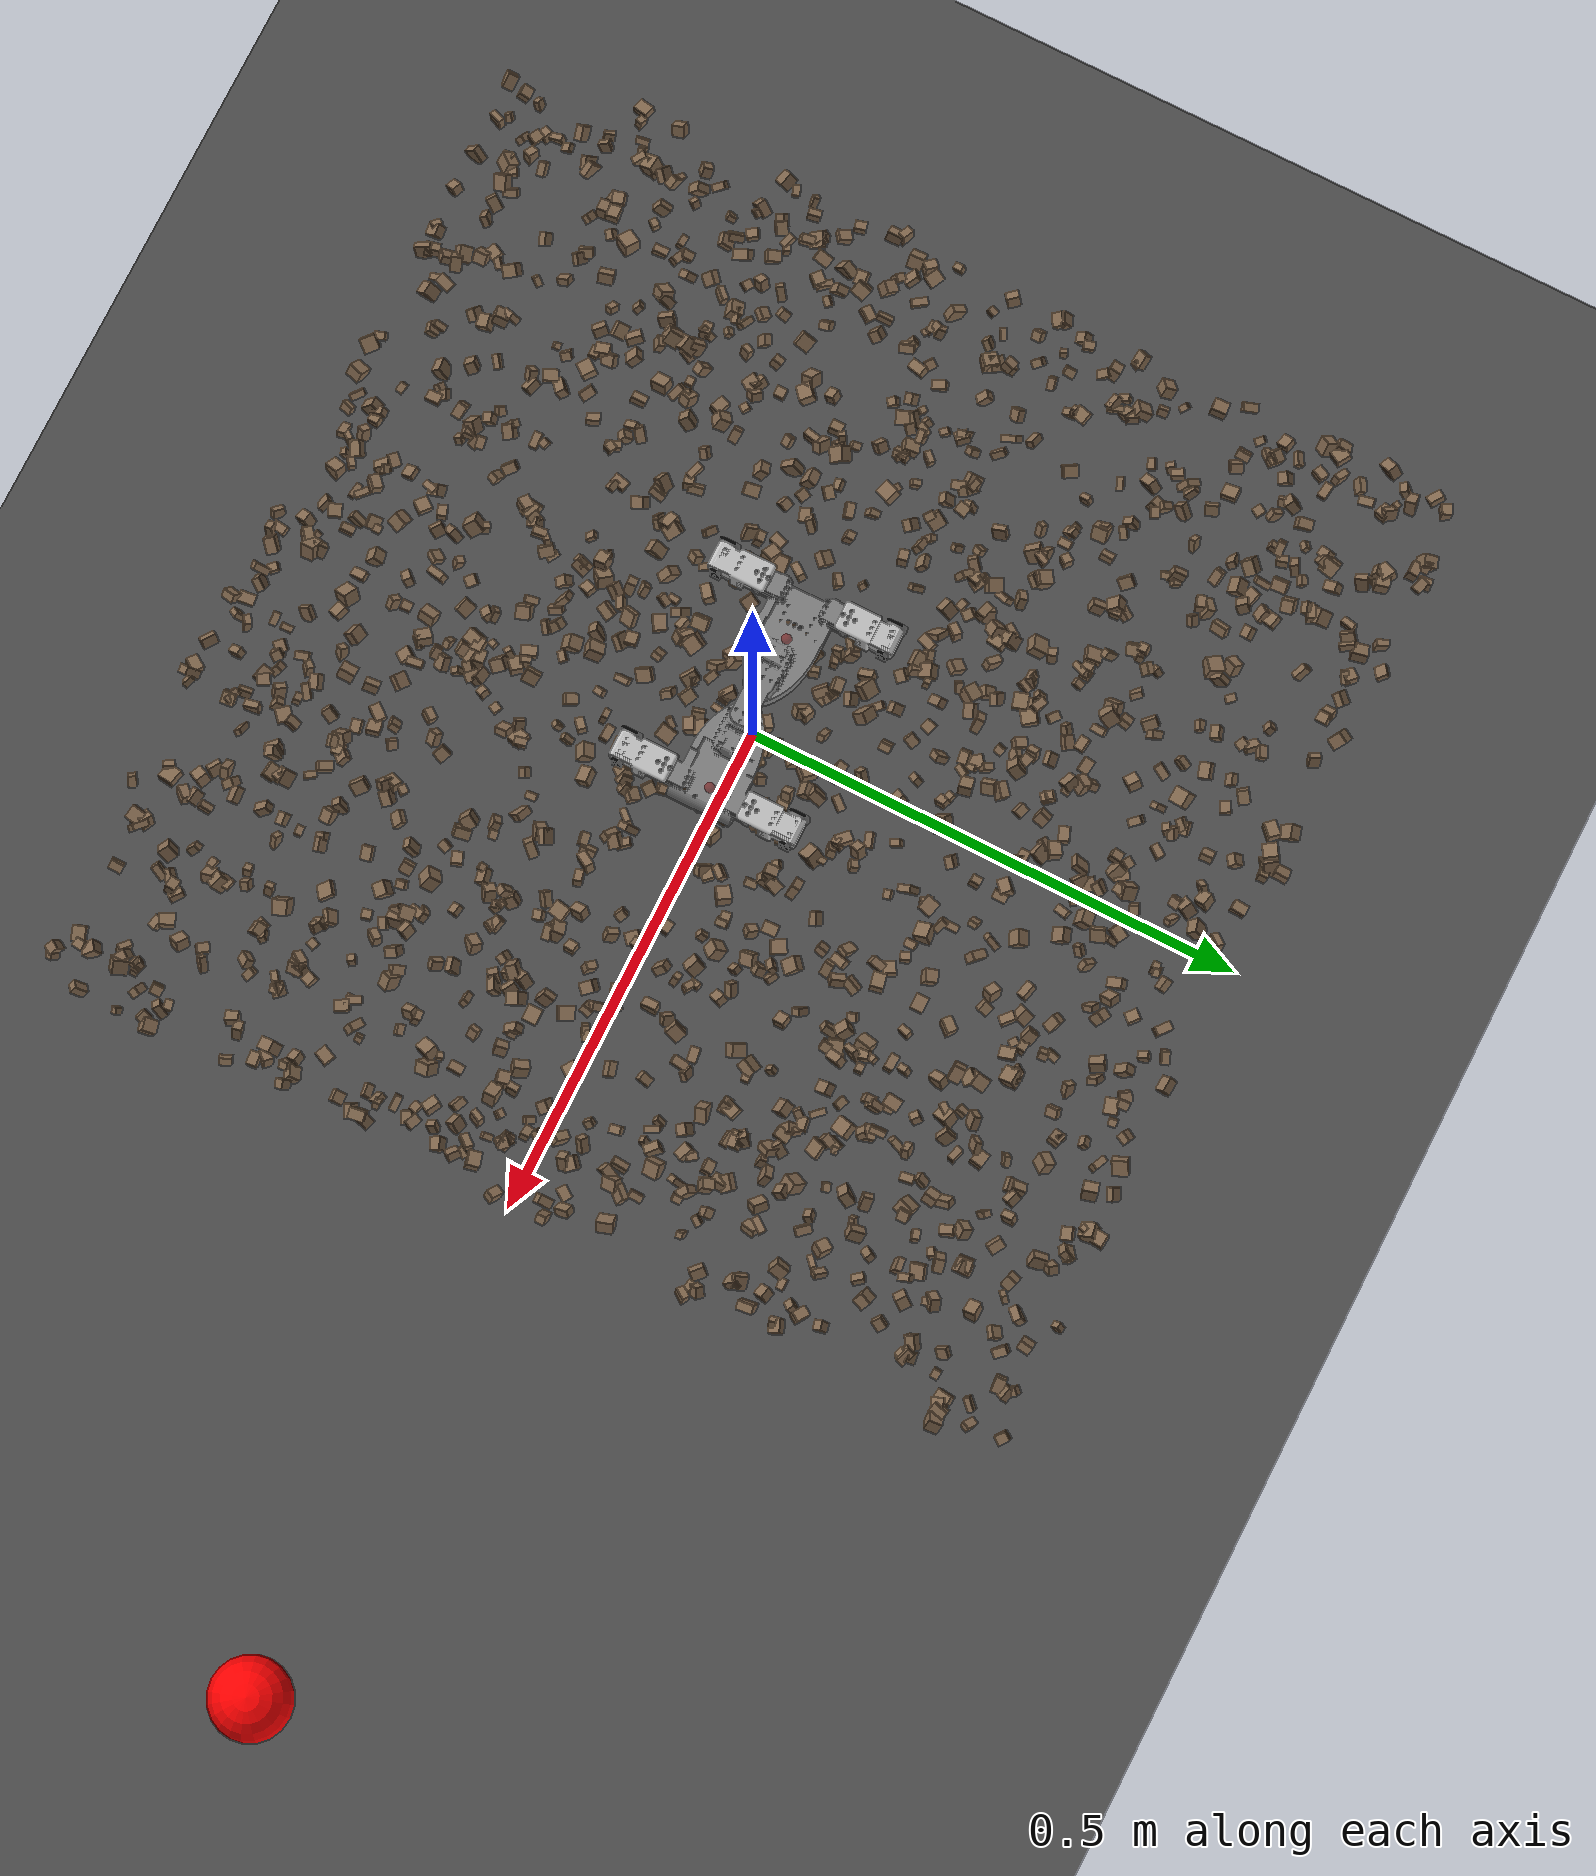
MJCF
<?xml version='1.0' encoding='utf-8'?>
<mujoco model="salamander_description">
  <include file="C:\Users\kevin\college_classes\SophomoreSpring\MiniRO\mujoco_box\assets\experiments\setup\../terrain_models\gravel_path_terrain.xml" /><compiler angle="radian" />
  <option solver="Newton" tolerance="1e-6" integrator="implicitfast" gravity="0 0 -9.81" />
  <include file="act2.xml" />

  <visual>
    <rgba haze="0.15 0.25 0.35 1" />
    <quality shadowsize="4096" />
    <map stiffness="700" shadowscale="0.5" fogstart="1" fogend="15" zfar="40" haze="1" />
  </visual>

  <asset>

    <texture type="skybox" builtin="gradient" rgb1="0.3 0.5 0.7" rgb2="0 0 0" width="512" height="512" />
    <texture name="texplane" type="2d" builtin="checker" rgb1=".2 .3 .4" rgb2=".1 0.15 0.2" width="512" height="512" mark="cross" markrgb=".8 .8 .8" />
    <material name="matplane" reflectance="0.3" texture="texplane" texrepeat="10 10" texuniform="true" />
    <material name="slope_mat" reflectance="0.3" rgba="1 1 0 .25" />

  <mesh file="C:\Users\kevin\college_classes\SophomoreSpring\MiniRO\mujoco_box\assets\experiments\setup\..\model_assets\salamander\meshes\body_front_link.STL" name="body_front_link" /><mesh file="C:\Users\kevin\college_classes\SophomoreSpring\MiniRO\mujoco_box\assets\experiments\setup\..\model_assets\salamander\meshes\body_rear_link.STL" name="body_rear_link" /><mesh file="C:\Users\kevin\college_classes\SophomoreSpring\MiniRO\mujoco_box\assets\experiments\setup\..\model_assets\salamander\meshes\dummy_base_link.STL" name="dummy_base_link" /><mesh file="C:\Users\kevin\college_classes\SophomoreSpring\MiniRO\mujoco_box\assets\experiments\setup\..\model_assets\salamander\meshes\leg1_link.STL" name="leg1_link" /><mesh file="C:\Users\kevin\college_classes\SophomoreSpring\MiniRO\mujoco_box\assets\experiments\setup\..\model_assets\salamander\meshes\leg2_link.STL" name="leg2_link" /><mesh file="C:\Users\kevin\college_classes\SophomoreSpring\MiniRO\mujoco_box\assets\experiments\setup\..\model_assets\salamander\meshes\leg3_link.STL" name="leg3_link" /><mesh file="C:\Users\kevin\college_classes\SophomoreSpring\MiniRO\mujoco_box\assets\experiments\setup\..\model_assets\salamander\meshes\leg4_link.STL" name="leg4_link" /><mesh file="C:\Users\kevin\college_classes\SophomoreSpring\MiniRO\mujoco_box\assets\experiments\setup\..\model_assets\salamander\meshes\shoulder1_link.STL" name="shoulder1_link" /><mesh file="C:\Users\kevin\college_classes\SophomoreSpring\MiniRO\mujoco_box\assets\experiments\setup\..\model_assets\salamander\meshes\shoulder2_link.STL" name="shoulder2_link" /><mesh file="C:\Users\kevin\college_classes\SophomoreSpring\MiniRO\mujoco_box\assets\experiments\setup\..\model_assets\salamander\meshes\shoulder3_link.STL" name="shoulder3_link" /><mesh file="C:\Users\kevin\college_classes\SophomoreSpring\MiniRO\mujoco_box\assets\experiments\setup\..\model_assets\salamander\meshes\shoulder4_link.STL" name="shoulder4_link" /></asset>

  <worldbody>
    <body name="ball" pos="1 0 .04">
      <geom type="sphere" size=".04" rgba="1 0 0 1" />
    </body>
    <light diffuse=".4 .4 .4" specular="0.1 0.1 0.1" pos="0 0 2.0" dir="0 0 -1" castshadow="false" />
    <light directional="true" diffuse=".8 .8 .8" specular="0.2 0.2 0.2" pos="0 0 4" dir="0 0 -1" />
    <geom name="ground" type="plane" size="0 0 1" pos="0 0 0" quat="1 0 0 0" material="matplane" condim="1" />

    <body name="body_rear_link" pos="0 0 0.0856">
      <geom pos="0 0 0.0856" quat="1 0 0 0" type="mesh" mesh="body_rear_link" />
      <joint name="fall" type="free" pos="0 0 0" axis="0 0 1" />
      <site name="torso_sensors" pos="-0.0682 0 .048" rgba="0.5 0 0 .5" />
      <body name="shoulder3_link" pos="-0.10533 0.043967 0.0784">
        <geom type="mesh" rgba="0.75294 0.75294 0.75294 1" mesh="shoulder3_link" />
        <inertial pos="-0.00035612 0.027895 -0.015524" quat="0.830241 0.554769 0.0182893 0.0509566" mass="0.022828" diaginertia="3.78438e-06 3.41587e-06 3.14145e-06" />
        <joint name="shoulder3_joint" type="hinge" pos="0 0 0" axis="0 0 1" range="-1.4 1.4" actuatorfrcrange="-0.39 0.39" frictionloss="0.1" />
        <body name="leg3_link" pos="-0.0174 0.041 -0.0164">
          <inertial pos="0.015303 -0.0075022 -0.031486" quat="0.991718 -0.121381 -0.0411625 0.00821591" mass="0.01174" diaginertia="4.05823e-06 3.86047e-06 1.0964e-06" />
          <joint name="leg3_joint" type="hinge" pos="0 0 0" axis="1 0 0" range="0 1.6" actuatorfrcrange="-0.39 0.39" frictionloss="0.1" />
          <geom type="mesh" rgba="0.10196 0.10196 0.10196 1" mesh="leg3_link" />
        </body>
      </body>
      <body name="shoulder4_link" pos="-0.10533 -0.044033 0.0784">
        <inertial pos="-0.00035261 -0.027895 -0.015524" quat="0.55469 0.830308 -0.0504036 -0.0191768" mass="0.022828" diaginertia="3.78439e-06 3.41596e-06 3.14135e-06" />
        <joint name="shoulder4_joint" type="hinge" pos="0 0 0" axis="0 0 1" range="-1.4 1.4" actuatorfrcrange="-0.39 0.39" frictionloss="0.1" />
        <geom type="mesh" rgba="0.75294 0.75294 0.75294 1" mesh="shoulder4_link" />
        <body name="leg4_link" pos="-0.0174 -0.041 -0.0164">
          <inertial pos="0.015303 0.0075097 -0.031486" quat="0.991713 0.121232 -0.0407594 -0.0121008" mass="0.01174" diaginertia="4.05702e-06 3.85955e-06 1.09592e-06" />
          <joint name="leg4_joint" type="hinge" pos="0 0 0" axis="1 0 0" range="-1.6 0" actuatorfrcrange="-0.39 0.39" frictionloss="0.1" />
          <geom type="mesh" rgba="0.10196 0.10196 0.10196 1" mesh="leg4_link" />
        </body>
      </body>
      <body name="body_front_link" pos="0.0185 0 0.0881">
        <site name="spinal_sensors" pos="-0.0182 0 0" rgba="0 0 0 .5" />
        <site name="front_sensors" pos="0.0682 0 -.04" rgba="0.5 0 0 .5" />
        <inertial pos="0.056805 2.3159e-05 -0.033606" quat="0.4638 0.4638 -0.53375 0.53375" mass="0.081874" diaginertia="3.73585e-05 2.58825e-05 1.9334e-05" />
        <joint name="spinal_joint" type="hinge" pos="0 0 0" axis="0 0 1" range="-1.5707 1.5707" actuatorfrcrange="-1.52 1.52" frictionloss="0.5" />
        <geom type="mesh" mesh="body_front_link" />
        <site name="tip_sensors" pos="0.09 0 -0.033" />
        <body name="shoulder1_link" pos="0.073327 0.044033 -0.0097">
          <inertial pos="-0.00035612 0.027895 -0.015524" quat="0.830241 0.554769 0.0182893 0.0509566" mass="0.022828" diaginertia="3.78438e-06 3.41587e-06 3.14145e-06" />
          <joint name="shoulder1_joint" type="hinge" pos="0 0 0" axis="0 0 1" range="-1.4 1.4" actuatorfrcrange="-0.39 0.39" frictionloss="0.1" />
          <geom type="mesh" rgba="0.75294 0.75294 0.75294 1" mesh="shoulder1_link" />
          <body name="leg1_link" pos="-0.0174 0.041 -0.0164">
            <inertial pos="0.015303 -0.0075022 -0.031486" quat="0.991718 -0.121381 -0.0411625 0.00821591" mass="0.01174" diaginertia="4.05823e-06 3.86047e-06 1.0964e-06" />
            <joint name="leg1_joint" type="hinge" pos="0 0 0" axis="1 0 0" range="0 1.6" actuatorfrcrange="-0.39 0.39" frictionloss="0.1" />
            <geom type="mesh" rgba="0.10196 0.10196 0.10196 1" mesh="leg1_link" />
          </body>
        </body>
        <body name="shoulder2_link" pos="0.073327 -0.043967 -0.0097">
          <inertial pos="-0.00035261 -0.027895 -0.015524" quat="0.55469 0.830308 -0.0504036 -0.0191768" mass="0.022828" diaginertia="3.78439e-06 3.41596e-06 3.14135e-06" />
          <joint name="shoulder2_joint" type="hinge" pos="0 0 0" axis="0 0 1" range="-1.4 1.4" actuatorfrcrange="-0.39 0.39" frictionloss="0.1" />
          <geom type="mesh" rgba="0.75294 0.75294 0.75294 1" mesh="shoulder2_link" />
          <body name="leg2_link" pos="-0.0174 -0.041 -0.0164">
            <inertial pos="0.015303 0.0075097 -0.031486" quat="0.991713 0.121232 -0.0407594 -0.0121008" mass="0.01174" diaginertia="4.05702e-06 3.85955e-06 1.09592e-06" />
            <joint name="leg2_joint" type="hinge" pos="0 0 0" axis="1 0 0" range="-1.6 0" actuatorfrcrange="-0.39 0.39" frictionloss="0.1" />
            <geom type="mesh" rgba="0.10196 0.10196 0.10196 1" mesh="leg2_link" />
          </body>
        </body>
      </body>
    </body>

  </worldbody>

  <sensor>
    <velocimeter name="velocity" site="tip_sensors" />
    <framequat name="spinal_quat" objtype="site" objname="spinal_sensors" reftype="body" refname="body_rear_link" />
    <gyro name="torso_angular_velocity" site="torso_sensors" />
    <velocimeter name="torso_velocity" site="torso_sensors" />
    <velocimeter name="front_velocity" site="front_sensors" />
  </sensor>
</mujoco>

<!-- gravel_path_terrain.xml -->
<mujoco model="rocky_terrain_scene">
    <compiler angle="radian" inertiafromgeom="true" />
    <option timestep="0.002" gravity="0 0 -9.81" />

    <worldbody>
        <light name="sunlight" pos="5 5 5" dir="-1 -1 -1" diffuse="1 1 1" specular="0.5 0.5 0.5" ambient="0.5 0.5 0.5" />

        <geom name="ground_plane" type="plane" size="50 50 0.1" rgba="0.3 0.3 0.3 1" />

        <body name="rocky_terrain_body">

        <geom name="rock1" type="box" size="0.006054577760274374 0.006341319462849942 0.006589428840517957" pos="0.007754975651790841 -0.3948748095205932 0.0010105148375381433" quat="0.3661344943610065 0.09833917881056416 0.30368407999676644 0.231842246831663" rgba="0.5 0.4 0.3 1" friction="0.6250496911904752 0.7830613320470301 0.689425617554396" /><geom name="rock2" type="box" size="0.0072361117779978675 0.006899415436517915 0.007496484778061519" pos="-0.11647445717168592 0.48178541038599876 0.0026118323717209116" quat="0.1845853878260746 0.17836613733297452 0.24811626577375437 0.3889322090671966" rgba="0.5 0.4 0.3 1" friction="0.6234537168034713 0.8450124057772872 0.748528212718989" /><geom name="rock3" type="box" size="0.006636702427769361 0.0033581314618201697 0.004863053550787987" pos="-0.34682767581650176 -0.3532187327195907 0.004429051181627355" quat="0.10109787865744156 0.286141017544314 0.38308995948005176 0.22967114431819272" rgba="0.5 0.4 0.3 1" friction="0.6065789532100275 0.7757637365864746 0.7242100542125435" /><geom name="rock4" type="box" size="0.005781652685255025 0.004256345269384 0.006246419910909863" pos="0.2140436937652873 0.42145257909264155 0.003788231909549419" quat="0.33890960905801165 0.21559478949064542 0.17040102007887048 0.27509458137247245" rgba="0.5 0.4 0.3 1" friction="0.6977176057484911 0.8048270448895322 0.6519136649961786" /><geom name="rock5" type="box" size="0.00792984662777791 0.007811051963748997 0.007163720298813266" pos="-0.3096231575614451 -0.24201372597913695 0.0034625773250240976" quat="0.24714741413670407 0.281529372415746 0.3670837554751665 0.10423945797238354" rgba="0.5 0.4 0.3 1" friction="0.578842872272129 0.7111095166831561 0.6527915411139796" /><geom name="rock6" type="box" size="0.007947957777307581 0.0045543626994429525 0.006425262371866032" pos="-0.07396382328920437 -0.09261094170191753 0.001215726671878472" quat="0.15795344712808831 0.3231422035787043 0.3033104820388917 0.21559386725431565" rgba="0.5 0.4 0.3 1" friction="0.54957105205929 0.8153714149604369 0.7006175996475654" /><geom name="rock7" type="box" size="0.005694026390176425 0.003507809963465313 0.005875290161117535" pos="-0.21420534344760223 0.47923616573777317 0.004541643597539063" quat="0.1344552819866165 0.258267937068171 0.47120144764980654 0.1360753332954059" rgba="0.5 0.4 0.3 1" friction="0.5029734763142418 0.821105013443365 0.7175617753605181" /><geom name="rock8" type="box" size="0.0075021128255730145 0.004198259369264088 0.003122250479995326" pos="0.07815482022447884 0.10772037957651637 0.0018293194035459148" quat="0.2652498537056284 0.24435475998796646 0.263420239748626 0.22697514655777914" rgba="0.5 0.4 0.3 1" friction="0.5772621674318714 0.8105776027279502 0.6975602239143334" /><geom name="rock9" type="box" size="0.006988164087981923 0.007828575513152806 0.007488102366215692" pos="-0.34115385425044265 0.4246895460463094 0.0016893341372789306" quat="0.2901336711404843 0.17783565472563703 0.36681000750546744 0.1652206666284112" rgba="0.5 0.4 0.3 1" friction="0.6721352561629299 0.7151493608590853 0.6664595194934693" /><geom name="rock10" type="box" size="0.007683015323707717 0.003847959581242439 0.006864215249261337" pos="0.17007150862857867 0.11190383250877789 0.00486822870246011" quat="0.2000272068159438 0.1649483971439308 0.32675342173741806 0.3082709743027073" rgba="0.5 0.4 0.3 1" friction="0.5610440511122001 0.733201214199391 0.6746997684859956" /><geom name="rock11" type="box" size="0.006582587402724861 0.006190434215635398 0.003702629703530252" pos="0.10230731302599894 -0.07502705519504327 0.0003672345982488062" quat="0.1479245742191127 0.5384500220833053 0.20532901891994357 0.1082963847776384" rgba="0.5 0.4 0.3 1" friction="0.6262991863615666 0.7458084080678757 0.7130951220434477" /><geom name="rock12" type="box" size="0.0046638778205652575 0.007515910865079324 0.0064579823747485075" pos="0.28873899600484465 0.0012468940150698327 0.003957868300285094" quat="0.3734505074972045 0.32439117298103515 0.20514071928855207 0.09701760023320839" rgba="0.5 0.4 0.3 1" friction="0.6379702120358183 0.7940616240113281 0.7115286538349517" /><geom name="rock13" type="box" size="0.006854912238157625 0.007002112464306869 0.006841504318640014" pos="0.19853421571762786 0.06102876236964205 0.0036695330354465884" quat="0.15514997784457557 0.4800738648461102 0.16089700902705126 0.20387914828226292" rgba="0.5 0.4 0.3 1" friction="0.5839493270282125 0.7895917436299136 0.6415158919984931" /><geom name="rock14" type="box" size="0.0035588638943515258 0.005235329725492571 0.0047340110436252724" pos="0.24053811636335642 0.0541095145761632 0.0007036738421215322" quat="0.06596395518631495 0.5538850438692704 0.2979763183929024 0.08217468255151232" rgba="0.5 0.4 0.3 1" friction="0.5627912181374539 0.8289876058744337 0.6126489249434798" /><geom name="rock15" type="box" size="0.006576937220227242 0.007090947382110749 0.0067996056464258966" pos="-0.00884984097915309 -0.2455584651791669 0.0008685863683089246" quat="0.663064543218483 0.05826759678615914 0.16576862743774337 0.11289923255761448" rgba="0.5 0.4 0.3 1" friction="0.5640523151083225 0.8386709774130392 0.673707266258572" /><geom name="rock16" type="box" size="0.005442050843569123 0.0036840468613350643 0.00609858909625907" pos="-0.11348607982946879 0.09876191824514668 0.0009873837358200742" quat="0.04121268851842079 0.2774797264677764 0.3213073228460913 0.36000026216771147" rgba="0.5 0.4 0.3 1" friction="0.6272409238478248 0.714206076919603 0.6096024601180832" /><geom name="rock17" type="box" size="0.005180389940106812 0.0071971961258350215 0.004300458653535949" pos="0.2612613833953652 -0.4148853884557262 0.0007645337608730812" quat="0.2706509548718906 0.007897539658692738 0.443856539487209 0.27759496598220756" rgba="0.5 0.4 0.3 1" friction="0.6376130222658511 0.7279146295798405 0.6481123780050861" /><geom name="rock18" type="box" size="0.004848810583909281 0.006095736659328797 0.006760289083397828" pos="-0.1041334248785829 0.226215823611013 0.0004148016045113828" quat="0.08313547130464355 0.6546756831554278 0.18584377421050727 0.07634507132942135" rgba="0.5 0.4 0.3 1" friction="0.6736762891131554 0.7301997105357321 0.6550435191325586" /><geom name="rock19" type="box" size="0.007777376599363696 0.0033990580997084628 0.006159480540780789" pos="0.0026284177454600766 0.33453275950294803 0.002796452939893118" quat="0.5659344053665994 0.02846000694052338 0.2106623823327455 0.19494320536013166" rgba="0.5 0.4 0.3 1" friction="0.5977086331716746 0.8223039981587116 0.6612060601546554" /><geom name="rock20" type="box" size="0.007868620729174651 0.00433561903209762 0.004700803667490991" pos="-0.1061392701351469 0.14010035435832657 0.0018508190141968744" quat="0.13207380213683087 0.38987623321958537 0.1472337081995969 0.33081625644398677" rgba="0.5 0.4 0.3 1" friction="0.5361719384746562 0.7623554798992599 0.7378574907101549" /><geom name="rock21" type="box" size="0.0073636513268801815 0.006792055554782997 0.005446182771048634" pos="-0.26862424456960843 -0.17146081396776125 0.0018649152599074308" quat="0.10927374056664227 0.04299251324255655 0.4240940990548509 0.42363964713595026" rgba="0.5 0.4 0.3 1" friction="0.6656114673942111 0.7297769589725723 0.621731830606201" /><geom name="rock22" type="box" size="0.003837614628979566 0.004534832230580619 0.003296380746016569" pos="0.15143801907222731 0.34672297983849476 0.0035461867266459884" quat="0.6240790301616007 0.0368600020012569 0.03622284246701871 0.30283812537012367" rgba="0.5 0.4 0.3 1" friction="0.5179057812259558 0.7077525874076338 0.628521360286052" /><geom name="rock23" type="box" size="0.005314691193790016 0.004604739987405251 0.004352164440347822" pos="-0.26203933224848697 -0.30106925491497727 0.0042062483731991765" quat="0.023636008224854024 0.922817970029052 0.006060091846182844 0.04748592989991113" rgba="0.5 0.4 0.3 1" friction="0.5156393085287077 0.7611733132739527 0.6385110760371071" /><geom name="rock24" type="box" size="0.006765115244288023 0.007659987849885978 0.006584249892107704" pos="-0.2455788951737954 -0.46988517562482024 0.0011236771164814263" quat="0.15205264263395454 0.3658781485827154 0.12113411991945901 0.360935088863871" rgba="0.5 0.4 0.3 1" friction="0.6901285548614927 0.7359426051496369 0.7049708885129152" /><geom name="rock25" type="box" size="0.005093959702266549 0.007904018647871637 0.004397567733427061" pos="0.44076974643030054 0.4746039009994041 0.00027096939295061516" quat="0.4002142662815438 0.05934858424609416 0.11850881493138687 0.42192833454097517" rgba="0.5 0.4 0.3 1" friction="0.528500931228216 0.7393587958098065 0.6643785803474094" /><geom name="rock26" type="box" size="0.005239407000771336 0.004635319965337985 0.004710960816090459" pos="-0.19844766824597793 0.41253325709809796 0.001852469061763553" quat="0.03160484674452352 0.1727837176311375 0.3954251183975855 0.4001863172267536" rgba="0.5 0.4 0.3 1" friction="0.6685432400040338 0.8026192610252574 0.6153265114228984" /><geom name="rock27" type="box" size="0.0030658298155192623 0.005250681533937464 0.007002395989835048" pos="-0.35348798739976484 -0.18737429383227067 0.0012620393762642463" quat="0.39810750377894866 0.2275260351144078 0.2278317768303495 0.14653468427629412" rgba="0.5 0.4 0.3 1" friction="0.6324118893817129 0.8288569963474082 0.6663540345344923" /><geom name="rock28" type="box" size="0.0033585875766465015 0.0030457826755865593 0.0077066948039429236" pos="0.21102172405027098 -0.4302350399229543 0.0004975077798215671" quat="0.20243381235480462 0.2403900276104106 0.06464548702069516 0.4925306730140897" rgba="0.5 0.4 0.3 1" friction="0.6556588031541827 0.8317973193322981 0.7350546658072434" /><geom name="rock29" type="box" size="0.007729844774267631 0.006004626558496533 0.0077581066561012105" pos="0.25182235200782366 0.2717460461033374 0.0024242268628300407" quat="0.48704734535323196 0.02175793840742232 0.05686713262843191 0.43432758361091384" rgba="0.5 0.4 0.3 1" friction="0.5192068216023837 0.7070050606882222 0.6804216657356792" /><geom name="rock30" type="box" size="0.007718222751443206 0.007710686021711972 0.00582463723313459" pos="0.40559519849061787 0.10225451171054645 0.0003676475205001617" quat="0.6565608008250212 0.1223308280369208 0.19861588024888183 0.02249249088917611" rgba="0.5 0.4 0.3 1" friction="0.5009557148016881 0.8359546446749512 0.6557262604478558" /><geom name="rock31" type="box" size="0.00799245421599169 0.004109551491012878 0.0037943560000764627" pos="-0.44614159498262285 -0.04863083685655134 2.8632170865086626e-05" quat="0.1908121480443681 0.1470951132081737 0.33465808012565856 0.3274346586217995" rgba="0.5 0.4 0.3 1" friction="0.6682803954848758 0.8094119020847141 0.7068366690012681" /><geom name="rock32" type="box" size="0.0078578753129864 0.0047623382925142494 0.004243451529971206" pos="0.4923757997430772 0.03223945946757567 0.002872084610240619" quat="0.3386318507656043 0.01966949525671691 0.5854190937783208 0.05627956019935798" rgba="0.5 0.4 0.3 1" friction="0.5630144314615174 0.8101885514000959 0.7364815208696687" /><geom name="rock33" type="box" size="0.005168297265227233 0.0031300685659470945 0.006414750110221484" pos="-0.0024740371781770687 0.2747484933876492 0.004002155470884925" quat="0.04680858606961804 0.3637853792742074 0.2730762144594696 0.31632982019670497" rgba="0.5 0.4 0.3 1" friction="0.5930798928009903 0.8486173188523607 0.7144521065761149" /><geom name="rock34" type="box" size="0.0048924716962083425 0.007206170218326761 0.006391314311370581" pos="0.3456138276111048 0.16016274608095482 0.004034307999583887" quat="0.10651702010068667 0.3720849656719 0.1839048533371128 0.33749316089030057" rgba="0.5 0.4 0.3 1" friction="0.5530315071785865 0.7935633359043281 0.6055930540049046" /><geom name="rock35" type="box" size="0.0060444936626716924 0.004907952800451054 0.003840422982164622" pos="0.12724877130685153 0.06179599850700013 0.0014028602279300135" quat="0.22831256505511566 0.25060549848594127 0.30846995267542376 0.21261198378351942" rgba="0.5 0.4 0.3 1" friction="0.5002558232479519 0.7669734878786705 0.6296798751108301" /><geom name="rock36" type="box" size="0.0030770433234962643 0.004112166962377995 0.007015893312791548" pos="0.46905325227831574 0.4588131110383882 0.004987462670036027" quat="0.04772984156991206 0.26287369712872666 0.3567866038536981 0.3326098574476632" rgba="0.5 0.4 0.3 1" friction="0.5095919834481896 0.7359953284985605 0.6177658480003033" /><geom name="rock37" type="box" size="0.005649616640890975 0.005027166932149406 0.005751975145842792" pos="0.3316179748211121 -0.4760885414623719 0.0005993806171046679" quat="0.25532376380126903 0.2421697112661065 0.23684737859585794 0.2656591463367665" rgba="0.5 0.4 0.3 1" friction="0.5307779706716975 0.7289539190633519 0.6643569482220962" /><geom name="rock38" type="box" size="0.003227005137820626 0.005890710195068756 0.005579470016282768" pos="0.08885932692631293 0.39579868299515153 0.0007418016642644105" quat="0.5197224151133957 0.19119946248366151 0.1972757644139548 0.091802357988988" rgba="0.5 0.4 0.3 1" friction="0.6427018678169536 0.771889888213733 0.6389589153669214" /><geom name="rock39" type="box" size="0.006696597512036412 0.0034232754041541988 0.003418995939226812" pos="0.032970073649258524 -0.030327394312394618 0.004361005209011775" quat="0.5668689689570726 0.2879359218223949 0.0005628049110487293 0.1446323043094838" rgba="0.5 0.4 0.3 1" friction="0.6973601582882374 0.8021360391673323 0.6298080354642595" /><geom name="rock40" type="box" size="0.0031061778977095056 0.004281064874910158 0.0035168437427925752" pos="-0.43418653347848213 -0.4810348840519234 0.0005433102697692805" quat="0.26417287503582976 0.18592359173473852 0.09564228769791727 0.45426124553151453" rgba="0.5 0.4 0.3 1" friction="0.6751764852662641 0.7032177476819743 0.7202622811902101" /><geom name="rock41" type="box" size="0.0061168325907746315 0.007655567033973084 0.007019371861462733" pos="-0.08427871751531957 -0.2010906404851952 0.004503155938804016" quat="0.2670682706055511 0.23315079754039822 0.17546936857990375 0.32431156327414684" rgba="0.5 0.4 0.3 1" friction="0.5955320960918253 0.7464589676749429 0.6547752893010779" /><geom name="rock42" type="box" size="0.006992947671551898 0.00657793091015918 0.006709503471779351" pos="-0.12740110559010387 0.11906774899855743 0.0037989865182849747" quat="0.12769772419469502 0.2888600442477878 0.24057185498413655 0.34287037657338065" rgba="0.5 0.4 0.3 1" friction="0.6457518829291558 0.7014410362423746 0.661536017679377" /><geom name="rock43" type="box" size="0.004896678168697978 0.007135879516738418 0.006812455872579273" pos="0.4827012788835421 -0.27352946784306986 0.002126808651974722" quat="0.23059980864485713 0.24210312027706904 0.2504768236592557 0.27682024741881806" rgba="0.5 0.4 0.3 1" friction="0.5210560236656145 0.8029264031078971 0.673319714974228" /><geom name="rock44" type="box" size="0.004919892336798788 0.0057492455868214205 0.0076883542153236865" pos="-0.46223760775642253 -0.22381653223499898 0.0012317232090698722" quat="0.08439150089153266 0.1210395435826459 0.52225788116776 0.27231107435806146" rgba="0.5 0.4 0.3 1" friction="0.6745141766795772 0.7308314321007973 0.7276343536072094" /><geom name="rock45" type="box" size="0.003463718674902426 0.004191030857284427 0.003911958061348743" pos="-0.43741938914528755 -0.2834695604361158 0.0011193315433631796" quat="0.27545483085399214 0.37111792937145305 0.056989207701102516 0.2964380320734522" rgba="0.5 0.4 0.3 1" friction="0.5492468181834116 0.7272724241875114 0.7373220981660578" /><geom name="rock46" type="box" size="0.0044234297542065015 0.0035939543624678807 0.003251927397773732" pos="0.0015246907776542695 0.02323860244182918 0.003984918139328744" quat="0.42131595103579966 0.01926615366501091 0.18706489256719835 0.37235300273199107" rgba="0.5 0.4 0.3 1" friction="0.59187422044309 0.7268867344639993 0.6374611372051288" /><geom name="rock47" type="box" size="0.005773690706113913 0.007254037045433424 0.005393248253071267" pos="0.005300272293636721 -0.46994639383849635 0.003257200319694387" quat="0.22881366502251624 0.3189181327291378 0.13956997622575645 0.3126982260225894" rgba="0.5 0.4 0.3 1" friction="0.558884918085864 0.8111106523936453 0.6054997290944739" /><geom name="rock48" type="box" size="0.004428547257596005 0.007208404939842401 0.004052218092912077" pos="-0.09193110861241915 0.21255675569289367 6.0102745322206386e-05" quat="0.23961193182145768 0.32209234690666816 0.2755581730823204 0.16273754818955374" rgba="0.5 0.4 0.3 1" friction="0.6493216846386778 0.8100402776476404 0.6353429535101676" /><geom name="rock49" type="box" size="0.003988447390152882 0.003934892510652633 0.006745662339381996" pos="-0.07055709018536926 0.38650120631083273 0.00013819575038836185" quat="0.15284872270892655 0.0974025356371367 0.36936041151195964 0.3803883301419771" rgba="0.5 0.4 0.3 1" friction="0.5644118613363247 0.7136867765250469 0.7312284037524394" /><geom name="rock50" type="box" size="0.006414419884753095 0.006699485365970688 0.006134838626075649" pos="-0.04510322552313151 0.1998266653372579 0.004595727702166232" quat="0.08336883447084821 0.36152211125702777 0.4345129432644919 0.12059611100763218" rgba="0.5 0.4 0.3 1" friction="0.6801428197544175 0.7913193964181638 0.6930916473555991" /><geom name="rock51" type="box" size="0.003351294299439814 0.005484362327089881 0.0038978976702881397" pos="0.45151844580999656 -0.41080496964842406 0.004509147148562775" quat="0.33323235081378483 0.2685915985223905 0.3352719452101776 0.06290410545364697" rgba="0.5 0.4 0.3 1" friction="0.6350870534484379 0.7477988478127786 0.7032062073178181" /><geom name="rock52" type="box" size="0.007700063239894915 0.007154531125221341 0.007802115276988749" pos="0.05253750236438093 -0.40159265874996375 0.0019145412934602408" quat="0.2804040577037087 0.30921412690406547 0.07537735650214883 0.3350044588900771" rgba="0.5 0.4 0.3 1" friction="0.5689914702565895 0.8245092766357529 0.7373164627432044" /><geom name="rock53" type="box" size="0.007942577752461516 0.004807256582657716 0.004105656770654243" pos="0.21748375749214033 0.18930947790719987 0.0012006219479761171" quat="0.2586937813309189 0.28478818771369663 0.367195322578862 0.0893227083765225" rgba="0.5 0.4 0.3 1" friction="0.6086233636273165 0.8145770686372522 0.6153224872891565" /><geom name="rock54" type="box" size="0.003074548266697588 0.003527907633792552 0.0033638692192243212" pos="0.03289746597291643 -0.2569162123891978 0.003630791848281845" quat="0.2622541957003308 0.3420959877515462 0.18952360099969584 0.20612621554842717" rgba="0.5 0.4 0.3 1" friction="0.5708079468028456 0.7130228570912749 0.7449858237920015" /><geom name="rock55" type="box" size="0.00300113373047096 0.007213172667141365 0.003944988819414313" pos="0.36671066783169326 0.44303872114633036 0.0015130740343465066" quat="0.10282860446237503 0.20422486710172857 0.4376130803468486 0.2553334480890477" rgba="0.5 0.4 0.3 1" friction="0.5169294813952285 0.7224901949341592 0.7349337900497903" /><geom name="rock56" type="box" size="0.005577690697225499 0.007874074336876008 0.005373059912946245" pos="-0.18272167637333792 0.16484297291670824 0.00013236689779672628" quat="0.42611154158526576 0.10547746283901689 0.4335670320619578 0.03484396351375955" rgba="0.5 0.4 0.3 1" friction="0.5202791024997062 0.8361177404652027 0.6670386807411105" /><geom name="rock57" type="box" size="0.007292306999533563 0.005718815856875377 0.006199631274671269" pos="-0.24340103888914588 -0.19232796404679942 0.001917632514601485" quat="0.4611430062186313 0.04819639871683118 0.25844949190982824 0.23221110315470925" rgba="0.5 0.4 0.3 1" friction="0.6806497726818275 0.8246207850116709 0.7085981762643894" /><geom name="rock58" type="box" size="0.0032768766934903994 0.003975303039075142 0.004387771522749906" pos="0.46802615517618895 -0.15294766046646802 0.004803921401779524" quat="0.3453658289876161 0.13743642161655203 0.15951197198495926 0.3576857774108726" rgba="0.5 0.4 0.3 1" friction="0.5096915582958077 0.8324867482177398 0.6636437200087764" /><geom name="rock59" type="box" size="0.0042480114563271665 0.003558274225328552 0.004970844048904849" pos="0.12549852860921717 0.22151682047416998 0.004814143419805158" quat="0.40095441747285204 0.45331427351724185 0.007542098513264713 0.1381892104966414" rgba="0.5 0.4 0.3 1" friction="0.5062960944408712 0.8433307232855438 0.744462740589062" /><geom name="rock60" type="box" size="0.006281195901529509 0.00799828135176478 0.004994431069628031" pos="0.4580701154925183 -0.3091889985939149 0.0004271891944681749" quat="0.2198581259556913 0.18799878557968905 0.2315647008791324 0.36057838758548727" rgba="0.5 0.4 0.3 1" friction="0.5782290103834694 0.7721846741765115 0.7445067702337336" /><geom name="rock61" type="box" size="0.005313846462494838 0.006776569408014647 0.006180957258688105" pos="0.3287872370429651 -0.4699462754525341 0.00080780719181194" quat="0.2950393048041508 0.33077223640812253 0.07894732755522797 0.29524113123249873" rgba="0.5 0.4 0.3 1" friction="0.5651148746721315 0.721811896304873 0.7020787031426267" /><geom name="rock62" type="box" size="0.005664533617548016 0.00555316100222521 0.004624884079838649" pos="-0.2939803497993497 -0.14699863355833176 0.003326922968020163" quat="0.1628552025502356 0.1856226150567401 0.4971976378633459 0.15432454452967845" rgba="0.5 0.4 0.3 1" friction="0.561585533338935 0.7770779217428514 0.6154218597265928" /><geom name="rock63" type="box" size="0.0039036200044503086 0.006722738622002037 0.00513208264787284" pos="-0.487909460525344 0.443754012021606 0.0028114822252375184" quat="0.1579905244348912 0.22106954354154482 0.22344706975198778 0.39749286227157626" rgba="0.5 0.4 0.3 1" friction="0.6503543204525909 0.7706690430710325 0.6776962885333141" /><geom name="rock64" type="box" size="0.004006530583177967 0.006350524084577621 0.006686140937213104" pos="-0.06307719530309563 -0.018209805280288482 0.001262130652035598" quat="0.2607220669745275 0.24260620415758408 0.3293522272779428 0.16731950158994569" rgba="0.5 0.4 0.3 1" friction="0.5832351072643173 0.7291217749798126 0.6346965691122808" /><geom name="rock65" type="box" size="0.006224022456777573 0.007264596552267451 0.0064051773711523985" pos="0.1317972734001055 0.24957416487126471 0.0008539731659110034" quat="0.26511539342139073 0.13417028054080765 0.310568578592019 0.2901457474457826" rgba="0.5 0.4 0.3 1" friction="0.6328715479126727 0.8040235746785876 0.7485654052139785" /><geom name="rock66" type="box" size="0.007980854445377742 0.0036265119722384584 0.005255270430439557" pos="-0.2881872144021449 0.3457848335468625 0.0035180158943019465" quat="0.0969603892525896 0.42093097489087744 0.2981697767024139 0.1839388591541191" rgba="0.5 0.4 0.3 1" friction="0.6829568516042966 0.7653286035826833 0.7237881765338245" /><geom name="rock67" type="box" size="0.007856772778545466 0.00738047540190491 0.005036853513134996" pos="-0.412373381887986 -0.21962670601823253 0.001922502806348786" quat="0.11962222525697384 0.2861832352995397 0.2959549168856399 0.2982396225578466" rgba="0.5 0.4 0.3 1" friction="0.6982333830967687 0.7703807500159298 0.6667958299114303" /><geom name="rock68" type="box" size="0.00345101374196557 0.0058071684348678316 0.0036983499678948538" pos="0.3552645717363152 0.18796457607196249 0.0014078874791046637" quat="0.35056646869631297 0.09851883780902095 0.2291472166001067 0.3217674768945595" rgba="0.5 0.4 0.3 1" friction="0.5195465424755497 0.7862499664646053 0.7342911947948896" /><geom name="rock69" type="box" size="0.003798917746725491 0.006498376581720244 0.006627630812374038" pos="0.12377130974355832 -0.41141489978750667 0.004452575711846944" quat="0.43683184995554525 0.44053446840783334 0.12194854548866042 0.0006851361479610352" rgba="0.5 0.4 0.3 1" friction="0.5119821178122209 0.762878522119988 0.7229656769212891" /><geom name="rock70" type="box" size="0.007564958111223367 0.005404325057288691 0.003449309860337823" pos="-0.4716481066875443 0.4038546676683157 0.0044271042275226165" quat="0.4921989062888059 0.3158388216699061 0.04887172061853275 0.14309055142275515" rgba="0.5 0.4 0.3 1" friction="0.6915853157144549 0.745118814759028 0.7445568832393763" /><geom name="rock71" type="box" size="0.006471212112767886 0.005183147102656192 0.0054425620455257236" pos="0.0053907228833717236 0.04544059577281201 0.003006295604842245" quat="0.28594374863596644 0.05391938251976119 0.34137528160327096 0.3187615872410014" rgba="0.5 0.4 0.3 1" friction="0.6369649382327668 0.7826966360894833 0.6167710893154775" /><geom name="rock72" type="box" size="0.00739933890927407 0.00393191577098911 0.006538277101146052" pos="-0.4107208129835953 0.29735742675538657 0.004699119891829001" quat="0.24441619735153539 0.24783505574415501 0.20019452283624706 0.3075542240680625" rgba="0.5 0.4 0.3 1" friction="0.6635553284319322 0.702749846997435 0.747384727147541" /><geom name="rock73" type="box" size="0.007342008954506698 0.006700643308103155 0.006937050401798153" pos="-0.36017351863251357 -0.20226067535604142 0.00021455840711202213" quat="0.13713907914414034 0.6345307946274372 0.09295547664670667 0.13537464958171572" rgba="0.5 0.4 0.3 1" friction="0.6787483380716604 0.7459807605200303 0.6664674001139452" /><geom name="rock74" type="box" size="0.006006784472152254 0.0037157232885595736 0.004941212786441228" pos="-0.3141664086066056 -0.35976406184006204 0.0010484240905011216" quat="0.26468170408542446 0.2308184853867255 0.10320074721919016 0.4012990633086599" rgba="0.5 0.4 0.3 1" friction="0.6710974247258535 0.771606311042791 0.6839928517400861" /><geom name="rock75" type="box" size="0.0048808547432866115 0.004803142142276398 0.007207259433752029" pos="0.288684243364567 -0.43861409633850623 0.0042490429465872415" quat="0.33949894699970007 0.19338368335839914 0.33598881480848936 0.1311285548334114" rgba="0.5 0.4 0.3 1" friction="0.635609826378521 0.8247288265071471 0.6614374473373232" /><geom name="rock76" type="box" size="0.004806402479370277 0.004898931664213838 0.0061827062023152215" pos="0.3689888834997219 -0.32646116310764894 0.0026421128843764456" quat="0.3390991797134913 0.24408736465055608 0.29759186515936703 0.1192215904765855" rgba="0.5 0.4 0.3 1" friction="0.5830106040262351 0.7832491187282171 0.6460482212784996" /><geom name="rock77" type="box" size="0.005164587912157655 0.005632808294336944 0.005910764812439047" pos="-0.42640486852694726 -0.4486267747980742 0.003472299793544147" quat="0.3333887419674628 0.28324432002867794 0.19886680529881345 0.1845001327050458" rgba="0.5 0.4 0.3 1" friction="0.6266473460361341 0.841554987529816 0.6899004103033258" /><geom name="rock78" type="box" size="0.005075502180006717 0.0066139496110404015 0.007026940619142011" pos="0.46644441644982104 0.2836119657782873 0.003724515062612161" quat="0.3561119277531511 0.292947447481984 0.1489414602122807 0.2019991645525842" rgba="0.5 0.4 0.3 1" friction="0.615268248634563 0.7578416883156048 0.7345170097259824" /><geom name="rock79" type="box" size="0.004534229560784534 0.007099104884046533 0.005763500472042498" pos="-0.2469459497639529 0.041934174865752794 0.004401646844947492" quat="0.03420415517504025 0.3034881035343903 0.3080834269680401 0.3542243143225294" rgba="0.5 0.4 0.3 1" friction="0.5006123422447786 0.7015920040694918 0.6837616214154154" /><geom name="rock80" type="box" size="0.006782182127165994 0.0030302876045506825 0.003936751998167016" pos="0.016445800658039578 -0.4549647609890404 0.00011849011952449307" quat="0.10274459009702172 0.08745966254250229 0.1209616128196538 0.6888341345408223" rgba="0.5 0.4 0.3 1" friction="0.5827017068244467 0.7056996338542828 0.6366391198252612" /><geom name="rock81" type="box" size="0.0031168735847716235 0.004732905595310387 0.0049966782742648114" pos="0.05385480330066583 -0.09939881413347029 0.0038885298064414947" quat="0.11604128168149619 0.25254155336790846 0.3260003514781194 0.3054168134724759" rgba="0.5 0.4 0.3 1" friction="0.5147341163613632 0.8425266301926058 0.7448090236434952" /><geom name="rock82" type="box" size="0.004738024442169218 0.0074080166697547065 0.0068087447611446" pos="-0.07645641050612273 0.04912514389578537 0.0023777391022847213" quat="0.284894711081747 0.18587871055925476 0.28526227114209823 0.24396430721689993" rgba="0.5 0.4 0.3 1" friction="0.6427948196954634 0.7803712967094214 0.7284718985263744" /><geom name="rock83" type="box" size="0.0034058859585501347 0.004103321480859003 0.006476846286310801" pos="0.4899537377973503 0.18081909366460824 0.0015446830769569786" quat="0.3030145632157218 0.24993167056213042 0.16906388951160362 0.2779898767105441" rgba="0.5 0.4 0.3 1" friction="0.6202992929996302 0.7326855470990405 0.6412365021954289" /><geom name="rock84" type="box" size="0.004127876031549878 0.006031976750069595 0.007525291246476953" pos="0.41255393910133287 0.13911817407808824 0.003035810111814559" quat="0.1987737325592693 0.49909252538999 0.1641846996396885 0.13794904241105213" rgba="0.5 0.4 0.3 1" friction="0.5049602995476502 0.7332062590233007 0.7454592684411693" /><geom name="rock85" type="box" size="0.006157738632346781 0.004254755188520105 0.007015855159139959" pos="-0.4592787862476103 0.4355251547011968 0.0017717633252012155" quat="0.29698585963119295 0.297479108318875 0.13901646296310022 0.2665185690868318" rgba="0.5 0.4 0.3 1" friction="0.5299444929464125 0.7280375976175838 0.7174451106164239" /><geom name="rock86" type="box" size="0.004764091031067118 0.00605457736620604 0.003274432477221739" pos="0.3688558217533833 -0.10375799593107782 0.002879625606854705" quat="0.37699934346261443 0.20347569709240365 0.10460391881804369 0.31492104062693826" rgba="0.5 0.4 0.3 1" friction="0.693869787036864 0.7638455599077347 0.6605226516147417" /><geom name="rock87" type="box" size="0.003259726299265294 0.006304298970471922 0.005966708637288737" pos="-0.307392683702315 0.07688454326418559 0.004467766748876909" quat="0.3264598477781506 0.22293534442721105 0.26552785171198334 0.1850769560826549" rgba="0.5 0.4 0.3 1" friction="0.584139392943736 0.7113771813602109 0.6055791768474692" /><geom name="rock88" type="box" size="0.0067427279169145855 0.004250787698734233 0.00440689504345045" pos="0.12964949663208114 0.1305928932736613 0.000552445969575019" quat="0.5625581765762762 0.21250267583034224 0.11986191161127245 0.10507723598210925" rgba="0.5 0.4 0.3 1" friction="0.5201729253238688 0.8385958846146175 0.7234187558765754" /><geom name="rock89" type="box" size="0.007736372506144998 0.003374660862642714 0.003694508094035668" pos="-0.02901474215901667 0.059440284882906536 0.002240430120109204" quat="0.28715958110121714 0.04500169800996954 0.6207893822173685 0.04704933867144482" rgba="0.5 0.4 0.3 1" friction="0.5315877060538385 0.785575469422133 0.6382740334642135" /><geom name="rock90" type="box" size="0.006785087922874336 0.003605538330125941 0.007697206333475107" pos="-0.11078241891898999 -0.020276850911404964 0.0018584942358849782" quat="0.2711168449964829 0.3360327228802557 0.13965396711019532 0.25319646501306603" rgba="0.5 0.4 0.3 1" friction="0.5060959903926338 0.8199321316651553 0.6417226718880106" /><geom name="rock91" type="box" size="0.00575292129298158 0.005477759678715091 0.003328474665071657" pos="0.2710466074530732 -0.13521764934351932 8.691748339219597e-06" quat="0.12559379075099944 0.5186217678180918 0.304206794793008 0.051577646637900675" rgba="0.5 0.4 0.3 1" friction="0.6431086682694287 0.8484288148899994 0.7114395756589886" /><geom name="rock92" type="box" size="0.005254710313801544 0.004562956988674521 0.006788504716565636" pos="-0.13037164839243398 0.2790579094514468 0.0020068620673694914" quat="0.45253035361914806 0.06438678203416714 0.4729675374883977 0.010115326858287053" rgba="0.5 0.4 0.3 1" friction="0.6440321756386111 0.7910549562579136 0.7267487560509394" /><geom name="rock93" type="box" size="0.007276218571137349 0.004913348859347829 0.00509350930077203" pos="-0.4136982046056559 -0.0868663075638415 0.0011901290913946283" quat="0.36955613545383764 0.2922728308299927 0.17153421299348087 0.16663682072268887" rgba="0.5 0.4 0.3 1" friction="0.5857837216855548 0.7271326488805302 0.6230032619594561" /><geom name="rock94" type="box" size="0.004375419136118571 0.003507929969013319 0.005480040108433743" pos="0.30613791735029083 -0.10060571386118022 0.0002492304694433023" quat="0.0069479649601416425 0.361873242269756 0.413807200394213 0.21737159237588938" rgba="0.5 0.4 0.3 1" friction="0.5219825564515119 0.788193274365679 0.700255349906836" /><geom name="rock95" type="box" size="0.006076309602783413 0.005181461944392786 0.0038838038052234143" pos="-0.0883866390039093 0.42998298194909645 0.000704019827590337" quat="0.10786423893295773 0.37440521830365897 0.3637865448244739 0.1539439979389093" rgba="0.5 0.4 0.3 1" friction="0.6984713985821174 0.7542127534077776 0.6259665935640173" /><geom name="rock96" type="box" size="0.007797134633044705 0.005698099536963177 0.007750599666188968" pos="-0.08655133083402211 0.07605148110649662 0.004039928999928777" quat="0.14259418900964801 0.07297967597107653 0.5083991846369055 0.27602695038236996" rgba="0.5 0.4 0.3 1" friction="0.537637993560035 0.8194565176075101 0.620298216690571" /><geom name="rock97" type="box" size="0.0038630561332460567 0.00427505434607819 0.004634265244740892" pos="0.07824596875027046 -0.2444977055446641 0.0016498175394256077" quat="0.2522434987896293 0.34533307799108376 0.12312000394548986 0.279303419273797" rgba="0.5 0.4 0.3 1" friction="0.5133172148743792 0.7409350093954099 0.6453040411596858" /><geom name="rock98" type="box" size="0.004418609929390253 0.003941947843288384 0.006852168977629247" pos="0.23466546028205615 -0.37728104176931987 0.0027166159810774067" quat="0.3046467479159721 0.2766084929765486 0.13252014987449584 0.2862246092329834" rgba="0.5 0.4 0.3 1" friction="0.5572053007730473 0.8053733760602034 0.6768430324766189" /><geom name="rock99" type="box" size="0.0054700413026717454 0.0042498624164803685 0.0034106964651877637" pos="-0.15427603911549137 -0.22650335880761052 0.004375040068579534" quat="0.01189017181605212 0.08260975338669643 0.5793344676287396 0.32616560716851173" rgba="0.5 0.4 0.3 1" friction="0.6711120941661606 0.8134013985938408 0.6683048766078936" /><geom name="rock100" type="box" size="0.007772030588236994 0.0065682917551057925 0.007503635647562871" pos="-0.10543140190328071 0.48560238079798457 0.00012553005744953937" quat="0.13556240762191618 0.2083688456784378 0.4639344590620676 0.19213428763757837" rgba="0.5 0.4 0.3 1" friction="0.6333987607801425 0.753946590771752 0.7285821942668151" /><geom name="rock101" type="box" size="0.004310215860727751 0.003386390641698792 0.0037215938517199424" pos="-0.2790245849665872 -0.1496912989626129 0.0002591324479331292" quat="0.09517695822463167 0.15431237449263083 0.3325209133452227 0.41798975393751486" rgba="0.5 0.4 0.3 1" friction="0.5747063532833634 0.7202232461469972 0.6761159229371974" /><geom name="rock102" type="box" size="0.005381265335562258 0.0037882250760338555 0.004037493761377882" pos="-0.2838169810982053 0.31936513199588334 0.004318890229391661" quat="0.49361184325254454 0.24921535797171335 0.19695749529365028 0.060215303482091774" rgba="0.5 0.4 0.3 1" friction="0.6121391652420977 0.7242899965370385 0.6599491053964257" /><geom name="rock103" type="box" size="0.006285544460483336 0.003941848501798687 0.005720375195668474" pos="0.47792439464619063 -0.06926549633561807 0.0030771369271624096" quat="0.20442966018778144 0.036474096951171465 0.19314020022769096 0.5659560426333561" rgba="0.5 0.4 0.3 1" friction="0.6989766133062221 0.8061514352008384 0.6218167739037386" /><geom name="rock104" type="box" size="0.006354316268640428 0.005809110405566923 0.005254770662549662" pos="0.47610165034534513 -0.08550987372891772 0.00293768848010348" quat="0.2962642441870555 0.5202031837207207 0.09440707466047134 0.08912549743175248" rgba="0.5 0.4 0.3 1" friction="0.5575110025909205 0.7491821819524755 0.7150677924803127" /><geom name="rock105" type="box" size="0.006076443042738221 0.007918248584992273 0.007586518724778267" pos="-0.004340054486496547 -0.16918523854682566 0.004551874094020995" quat="0.01130310617338141 0.2842034698923349 0.1310671470065173 0.5734262769277664" rgba="0.5 0.4 0.3 1" friction="0.6574320038242079 0.7727831724829781 0.6927525128043442" /><geom name="rock106" type="box" size="0.005081139810291871 0.0050175500239843405 0.004149861183506329" pos="0.46302472635832204 0.27335639042460425 0.004574458275216513" quat="0.3380392166982406 0.26080516355335465 0.3825399268316055 0.018615692916799265" rgba="0.5 0.4 0.3 1" friction="0.517583133189099 0.7533929247983548 0.6938343799010648" /><geom name="rock107" type="box" size="0.007289321322816654 0.007828511363984814 0.006243677128329748" pos="-0.43359330980586297 0.49199696375954893 0.0025290663808957975" quat="0.2811347247296438 0.13308142061968598 0.32806176255301106 0.2577220920976592" rgba="0.5 0.4 0.3 1" friction="0.557126594454276 0.7020301843068 0.7088379729388431" /><geom name="rock108" type="box" size="0.005026504435207484 0.0075647445173633076 0.006399856775745559" pos="0.05221723911486831 -0.2618579692152254 0.002903695417337951" quat="0.10704664476048921 0.37678327174607323 0.4271376269739472 0.08903245651949031" rgba="0.5 0.4 0.3 1" friction="0.5083401899510444 0.7108727106883705 0.6417844495796495" /><geom name="rock109" type="box" size="0.004305330332277345 0.003672162273182099 0.006959668875187934" pos="0.3882449387578357 0.31457176156770883 0.0024001972950258156" quat="0.10353329790913149 0.10771059459405154 0.20069536520776404 0.588060742289053" rgba="0.5 0.4 0.3 1" friction="0.5397587294371238 0.7629366208914377 0.722567901304372" /><geom name="rock110" type="box" size="0.0047722548254854735 0.005948086501109456 0.007496800533955063" pos="-0.2786159138295631 -0.06850700727095216 0.004144358843815408" quat="0.31697314545878025 0.26412931911318094 0.04726430242978932 0.3716332329982495" rgba="0.5 0.4 0.3 1" friction="0.6444460041631282 0.7812589330146632 0.7017632586990135" /><geom name="rock111" type="box" size="0.005491557706611434 0.007821727173581912 0.00464296830502498" pos="-0.07185819968573037 -0.21663156425784114 0.0032427769867622563" quat="0.11800843443098216 0.2722616133894186 0.02695037845896279 0.5827795737206364" rgba="0.5 0.4 0.3 1" friction="0.5048250105112306 0.7649067120478843 0.6025913615252754" /><geom name="rock112" type="box" size="0.006209700340461022 0.005516889130909917 0.004883378698794635" pos="0.4767636221399981 -0.264713943225209 0.0013706266737723205" quat="0.3579619195245487 0.32615770782769393 0.05688912428092373 0.25899124836683374" rgba="0.5 0.4 0.3 1" friction="0.5664451619292601 0.7457597366451496 0.662850948572466" /><geom name="rock113" type="box" size="0.007263873389301415 0.006157925723126713 0.006980344356518191" pos="0.14939688367235449 0.043778894521633194 0.0008202342065953094" quat="0.3873829008347882 0.3717843274355364 0.04324593199535023 0.1975868397343251" rgba="0.5 0.4 0.3 1" friction="0.5082472934335336 0.7180987878880938 0.7462382232226343" /><geom name="rock114" type="box" size="0.0033547895884918875 0.0033313936068655728 0.007711366975267355" pos="-0.3556227712115112 -0.19767617008089267 0.003213651238179502" quat="0.13326785264922808 0.2911064403139112 0.24309425683912902 0.3325314501977318" rgba="0.5 0.4 0.3 1" friction="0.5436249598540608 0.8285457557459224 0.7181375309696506" /><geom name="rock115" type="box" size="0.005614832461580235 0.0033506879824223732 0.0034298754161669483" pos="0.26750409243403506 -0.3153211537696856 0.001813097907273133" quat="0.08277742191963718 0.35706802441943664 0.23075716232932242 0.32939739133160373" rgba="0.5 0.4 0.3 1" friction="0.5716415089728846 0.7800865447658266 0.614014629101121" /><geom name="rock116" type="box" size="0.0034171315877200227 0.0072310981584576195 0.007808046904133206" pos="-0.047522038846862236 -0.15450110781082904 0.004396358115237687" quat="0.259193911363312 0.11667528877574551 0.553197237684634 0.07093356217630849" rgba="0.5 0.4 0.3 1" friction="0.6495011230516264 0.8093627829032402 0.7028808053202634" /><geom name="rock117" type="box" size="0.006954776382386795 0.0035422443768113954 0.0035676606005803973" pos="-0.09742105041111093 0.036014525671985265 0.0008601393233278187" quat="0.03695725130887017 0.6582668243313943 0.09366559176171547 0.21111033259802003" rgba="0.5 0.4 0.3 1" friction="0.5615185465593994 0.786019339444569 0.6355244425499872" /><geom name="rock118" type="box" size="0.00793437092339157 0.0031290568131574423 0.007418034401019916" pos="0.3123102533224461 -0.28778109579885836 0.0032144002183897183" quat="0.08263492130624321 0.23113632409682586 0.26936835498638095 0.41686039961054994" rgba="0.5 0.4 0.3 1" friction="0.6496771889401598 0.8454029684917685 0.7285399507435487" /><geom name="rock119" type="box" size="0.005374885344400366 0.003099973934127019 0.006312874471916908" pos="0.23003548999015488 -0.1931743584442961 0.0017649629083208607" quat="0.2264902390851884 0.17116578247242015 0.2531484212591321 0.3491955571832593" rgba="0.5 0.4 0.3 1" friction="0.5765165276584612 0.7676923434199426 0.6079083608744108" /><geom name="rock120" type="box" size="0.004743244266531394 0.00557622712264421 0.00403605312106798" pos="0.47316753015164736 -0.2452651450352965 0.0009789673686295686" quat="0.09970783215162671 0.3575343398806495 0.281253750183132 0.2615040777845918" rgba="0.5 0.4 0.3 1" friction="0.6605541554405334 0.7520793175119789 0.6710375707326833" /><geom name="rock121" type="box" size="0.004595659983982162 0.007279174256261881 0.004575078705120231" pos="0.23489837296887872 -0.3137939882459956 0.0008807640145959445" quat="0.1426129101067298 0.21687804907553893 0.17484925129228404 0.46565978952544723" rgba="0.5 0.4 0.3 1" friction="0.6847778570715584 0.8373938052029487 0.7285826227601706" /><geom name="rock122" type="box" size="0.007047594122688296 0.004762336675670413 0.006742810227527256" pos="-0.18079377062415158 -0.016069567710322308 0.003091588894557743" quat="0.48400202984001356 0.22509071780671133 0.09131752649810171 0.19958972585517343" rgba="0.5 0.4 0.3 1" friction="0.6476043718543537 0.7732368594013138 0.6704774930406452" /><geom name="rock123" type="box" size="0.006401141913530884 0.0036124747358994274 0.0066477525720451255" pos="-0.02061723645974889 -0.411717026326025 0.0020886987234877193" quat="0.26329302946787936 0.20557456418169576 0.33325778552231006 0.1978746208281148" rgba="0.5 0.4 0.3 1" friction="0.5771831280778211 0.7039589293988376 0.6124391590272017" /><geom name="rock124" type="box" size="0.0041269434431947995 0.0031116442161544535 0.003692522701515577" pos="0.17715254578958461 0.461561453498217 0.004829404616759774" quat="0.18322268059807598 0.29184160995072495 0.29495347607166933 0.22998223337952975" rgba="0.5 0.4 0.3 1" friction="0.6602634191251446 0.7764296456081079 0.7372012021052347" /><geom name="rock125" type="box" size="0.003459799632794344 0.004635368657275695 0.005695592120940431" pos="-0.16241668041173973 0.4185052514712049 0.004051600610548431" quat="0.30949111796855977 0.10543759220748306 0.35654135098950696 0.22852993883445014" rgba="0.5 0.4 0.3 1" friction="0.5568172396127876 0.8047222892497602 0.6266183424017546" /><geom name="rock126" type="box" size="0.007679276591227239 0.003819566000203661 0.00670077320357043" pos="-0.16830280128233388 -0.18524525024952154 0.002978004201849087" quat="0.41067859319246436 0.09803136801366404 0.16622164077516677 0.3250683980187049" rgba="0.5 0.4 0.3 1" friction="0.5893823706643867 0.7266374418360709 0.7291955202195914" /><geom name="rock127" type="box" size="0.004668572642405788 0.0034386733612713273 0.005205125645329997" pos="-0.3961547314529894 -0.01191802970858824 0.0008936401992477855" quat="0.351385863519788 0.31461683569897547 0.2434576122897652 0.09053968849147136" rgba="0.5 0.4 0.3 1" friction="0.589689097019391 0.7868545562265445 0.6914711219508981" /><geom name="rock128" type="box" size="0.004869147477447627 0.006119548546000077 0.005899765566196645" pos="-0.2153630164799697 0.04932253482560822 0.0033310933123810445" quat="0.25705388437862303 0.18931242574533502 0.2361023761960778 0.3175313136799642" rgba="0.5 0.4 0.3 1" friction="0.6187091938033432 0.8361152260930976 0.7082278158130901" /><geom name="rock129" type="box" size="0.0072562994254664025 0.004268978290865559 0.006601236515833557" pos="0.465612511765533 0.2150816556954367 0.0005164958054878438" quat="0.17961887413294295 0.2578713615876519 0.10989186702148337 0.45261789725792184" rgba="0.5 0.4 0.3 1" friction="0.6294679628058328 0.7444705612057695 0.7379780420354265" /><geom name="rock130" type="box" size="0.004495473199157117 0.006664503555261343 0.0037869227154958443" pos="-0.33714550636426954 0.06229523755794031 0.0034767839368812447" quat="0.24256775889191728 0.20192585184115577 0.3904571693883018 0.16504921987862517" rgba="0.5 0.4 0.3 1" friction="0.6380281064758898 0.771210612506646 0.6158413854104502" /><geom name="rock131" type="box" size="0.0056382707909880805 0.005883463637960199 0.004976603139900582" pos="0.13456938368904703 0.30845225851852054 0.0037145336479440234" quat="0.009183147404510117 0.10683058719248428 0.524956737934056 0.3590295274689497" rgba="0.5 0.4 0.3 1" friction="0.6334291500154166 0.7240126302339048 0.7315818892771875" /><geom name="rock132" type="box" size="0.004143535468946382 0.0054351880922768655 0.003935594856194135" pos="-0.2777761219753532 -0.2077328069300357 0.00047358235278668784" quat="0.48991771053954525 0.4939021666702278 0.0006797900264787953 0.015500332763748077" rgba="0.5 0.4 0.3 1" friction="0.6927841176434075 0.8176899326988584 0.6415690261419047" /><geom name="rock133" type="box" size="0.00785180272900679 0.0031690628177980856 0.004213994393770373" pos="0.39483171584144383 0.25083394066560505 0.0014356141522746191" quat="0.1368035116272774 0.1731641944784649 0.4211475753368706 0.268884718557387" rgba="0.5 0.4 0.3 1" friction="0.6212545405918891 0.7503771205177 0.6657437965217357" /><geom name="rock134" type="box" size="0.006406525478169406 0.004348057261337052 0.006335818827423656" pos="-0.05431307662250484 0.21907930308858237 0.003470963067899863" quat="0.07664201839750778 0.33883368273680153 0.36892133088896273 0.21560296797672798" rgba="0.5 0.4 0.3 1" friction="0.5987533055848643 0.7537906628067597 0.6999470103699789" /><geom name="rock135" type="box" size="0.005099559737656167 0.007543273050742184 0.00487720144170748" pos="0.4733239518395074 -0.4878951534853191 0.0029904261147310676" quat="0.03438793400947242 0.18692855777618675 0.34718336437947633 0.4315001438348644" rgba="0.5 0.4 0.3 1" friction="0.5581527896789777 0.7526677116444959 0.6670250560928773" /><geom name="rock136" type="box" size="0.007216356856552447 0.003921603182244948 0.006322533487838443" pos="-0.4372244006720015 0.17546305377230487 5.0710949339093374e-05" quat="0.25534574872129906 0.3525296707005777 0.04543874655023089 0.34668583402789244" rgba="0.5 0.4 0.3 1" friction="0.5779810800137326 0.7584819879349647 0.6720592397989242" /><geom name="rock137" type="box" size="0.0034925052853454737 0.005668879003231577 0.007081258456461114" pos="0.31734912076110466 -0.0927151056156702 0.00317734063560762" quat="0.2363424486722688 0.4126034166383062 0.053253034192754053 0.29780110049667097" rgba="0.5 0.4 0.3 1" friction="0.6025458776629988 0.7967112211610844 0.7482530460252648" /><geom name="rock138" type="box" size="0.0038918312909374626 0.006918414436091274 0.005862333528060012" pos="0.025033763972473033 0.2194031576847969 0.0028322441685344722" quat="0.07117936794305256 0.26179704581551627 0.34042294571150383 0.3266006405299273" rgba="0.5 0.4 0.3 1" friction="0.591616680120286 0.7220103853125008 0.6644330250161318" /><geom name="rock139" type="box" size="0.005124754852685154 0.007980374227108771 0.0036454655971715918" pos="-0.34984213472430536 0.04820243120576273 0.0006361880120037749" quat="0.13006358988004424 0.33430424588650204 0.2559064901255906 0.2797256741078631" rgba="0.5 0.4 0.3 1" friction="0.6353126540622958 0.7452087716826228 0.6900328675092176" /><geom name="rock140" type="box" size="0.007932659272179772 0.007951075350304856 0.00338809548625931" pos="-0.19467751504952702 0.24838944465704793 0.0026501492424974462" quat="0.35204596804619875 0.1589367010762273 0.46356127588200724 0.025456054995566784" rgba="0.5 0.4 0.3 1" friction="0.5573066844025536 0.8363363417271039 0.7059498282233451" /><geom name="rock141" type="box" size="0.006273345093794762 0.0054501764355838755 0.0039678985830084055" pos="0.11118748359921815 0.22064554528853808 0.0007396951013316871" quat="0.4124647789381227 0.045106091709494735 0.5224099071298907 0.02001922222249193" rgba="0.5 0.4 0.3 1" friction="0.557240336415647 0.8436733115161459 0.704050013653727" /><geom name="rock142" type="box" size="0.0031577929893461033 0.006537437181842442 0.0030579818734212056" pos="-0.46882333232007367 0.44205349284796747 0.0013113283192732483" quat="0.16265010410730016 0.03456688346270412 0.4102641138176477 0.392518898612348" rgba="0.5 0.4 0.3 1" friction="0.5388116721271261 0.7008762001406222 0.6516113695050851" /><geom name="rock143" type="box" size="0.004740035940661158 0.004941727759288373 0.0063103712074942106" pos="-0.3986137265049443 0.403751340837174 0.0023544730572976503" quat="0.011059647129557428 0.09332726996899851 0.2869803469858199 0.6086327359156243" rgba="0.5 0.4 0.3 1" friction="0.531256749214184 0.7557758598114173 0.6392099114261885" /><geom name="rock144" type="box" size="0.005807397258248579 0.007542543827416988 0.004821774715746283" pos="-0.15199211757842834 -0.19686253983518887 0.00014538680060966646" quat="0.5797837602255017 0.19994281893051427 0.11922650319866819 0.1010469176453158" rgba="0.5 0.4 0.3 1" friction="0.6979976212599428 0.806947268256096 0.7442285817996899" /><geom name="rock145" type="box" size="0.0031735878038017013 0.005064343202033648 0.007133239850020064" pos="-0.14357204961083236 -0.1708028159373941 0.0029533442300947385" quat="0.0007618461511360604 0.3506435690617377 0.3370642046481287 0.3115303801389976" rgba="0.5 0.4 0.3 1" friction="0.644096084049965 0.7184906737652866 0.6349684857798252" /><geom name="rock146" type="box" size="0.006671070799066393 0.003995876533148181 0.004598551457967866" pos="0.37900906545524193 -0.4733965489718708 0.0014523049084588324" quat="0.21765782138069004 0.29146057854056945 0.3238459046635496 0.16703569541519092" rgba="0.5 0.4 0.3 1" friction="0.5701814714710737 0.7276035645834968 0.6893578493053025" /><geom name="rock147" type="box" size="0.005793738668492841 0.006296222276178648 0.004266209790072205" pos="0.1390176943020458 0.3572506625630546 0.0023917737720354553" quat="0.4373939782587349 0.026414056690527776 0.1839008797251508 0.35229108532558656" rgba="0.5 0.4 0.3 1" friction="0.5356011686948681 0.7067199942279138 0.6517396345284249" /><geom name="rock148" type="box" size="0.005530916264404155 0.007163328477248422 0.0054955879814289395" pos="0.20757648348143043 -0.278052252983101 0.0006790756783986074" quat="0.25619673790212477 0.1857120934649738 0.029853281932237817 0.5282378867006636" rgba="0.5 0.4 0.3 1" friction="0.6917301417589659 0.7888568720326694 0.7174229680372735" /><geom name="rock149" type="box" size="0.00627378195864269 0.006891729326265025 0.006734895539644526" pos="0.2800215900668892 0.4982077751969818 0.0012331397300534219" quat="0.24736806450854984 0.27277671335354303 0.21095016744722364 0.2689050546906834" rgba="0.5 0.4 0.3 1" friction="0.6263521910783807 0.7625542209528803 0.6189528230425864" /><geom name="rock150" type="box" size="0.004488848571268915 0.007061591017554827 0.0034422516564438896" pos="0.22031053892748498 0.2681302110384648 0.0019168700362644508" quat="0.23177514166322602 0.30152498820593004 0.17628980841363295 0.2904100617172109" rgba="0.5 0.4 0.3 1" friction="0.6218034504271417 0.7078266197754166 0.734172239081354" /><geom name="rock151" type="box" size="0.004782718334007037 0.0059633638370170435 0.006059490626689069" pos="-0.24446723782868374 -0.4199126219376642 0.004786784490716952" quat="0.0021460910407477217 0.3304704835859434 0.33877562318924986 0.3286078021840589" rgba="0.5 0.4 0.3 1" friction="0.5406443651721308 0.7138493368212302 0.6336897434828673" /><geom name="rock152" type="box" size="0.004006726164574607 0.005702826260716425 0.0054404803475846565" pos="0.30089794422746596 -0.49827311208048464 0.0035041657900641153" quat="0.2848626795667786 0.0736923689619739 0.14252781162172024 0.49891713984952724" rgba="0.5 0.4 0.3 1" friction="0.5904482561605672 0.7427541630069499 0.6463047233411836" /><geom name="rock153" type="box" size="0.004336608583859381 0.006393484469658995 0.003662909655650083" pos="-0.15621480497054063 0.37079105169003945 0.0047475881705152335" quat="0.17264367339838255 0.3605853729971267 0.024951523636927743 0.44181942996756296" rgba="0.5 0.4 0.3 1" friction="0.6217780971574017 0.8101813864213089 0.6512630926640535" /><geom name="rock154" type="box" size="0.007619716883597242 0.005786499641895981 0.003295980901300987" pos="-0.26113751599540824 -0.46723060725989096 0.0016639406446295457" quat="0.1576100579551077 0.2935865461027077 0.24379089815491536 0.30501249778726924" rgba="0.5 0.4 0.3 1" friction="0.6689024008651362 0.8188025939912448 0.6090503173496621" /><geom name="rock155" type="box" size="0.0032416889114370868 0.006210700082033917 0.006986357026152203" pos="0.22150144776497438 -0.2592697278858548 0.002339460353659918" quat="0.3332388950422944 0.00548310330532338 0.366947579149662 0.29433042250272023" rgba="0.5 0.4 0.3 1" friction="0.683999743452973 0.7167842015988682 0.7202194723541139" /><geom name="rock156" type="box" size="0.004065135028637177 0.004427663075194668 0.007728240935813114" pos="-0.3952922794999967 -0.1702911135112154 0.003104284545503886" quat="0.08644008555922382 0.24593189713842722 0.4462232481898356 0.22140476911251328" rgba="0.5 0.4 0.3 1" friction="0.5410112215963694 0.7508264584735994 0.7361156526410664" /><geom name="rock157" type="box" size="0.00578693365928037 0.006845474528778277 0.006925638802024416" pos="-0.3111832757952242 0.07540770558972842 0.003329558949237243" quat="0.09048641568559435 0.44350988358406807 0.11591584745500032 0.3500878532753373" rgba="0.5 0.4 0.3 1" friction="0.5047175806536394 0.7228745999605397 0.7372905709396944" /><geom name="rock158" type="box" size="0.004447145388026007 0.006529127879391118 0.007622065427019891" pos="-0.004705046597095142 0.14834134481275063 0.0021563841589970264" quat="0.3546664244159925 0.2375188413944979 0.3401632200824889 0.06765151410702076" rgba="0.5 0.4 0.3 1" friction="0.5027257411542219 0.7423450519653826 0.6286180945237339" /><geom name="rock159" type="box" size="0.007862233729473062 0.007017154300373912 0.003074982897945975" pos="0.007630035319645234 -0.13270533425488096 0.0015748837987681337" quat="0.3968143734687643 0.029691462909085326 0.5371274020172389 0.03636676160491157" rgba="0.5 0.4 0.3 1" friction="0.5672784059047891 0.7445755864410667 0.6735818181086963" /><geom name="rock160" type="box" size="0.004573073723356451 0.0035525842700483284 0.006479030553520133" pos="-0.19871062576640652 0.43249952534365976 0.004045612703176968" quat="0.2856344737981912 0.11078504676396332 0.3129548039455765 0.29062567549226903" rgba="0.5 0.4 0.3 1" friction="0.6984158402036931 0.7760797232044069 0.7350997088526936" /><geom name="rock161" type="box" size="0.003914469935717085 0.003576416649509062 0.006589382429657017" pos="0.3320065502917563 -0.41607729161472484 0.0025079065906785476" quat="0.22048896289932346 0.40034454112578477 0.3665829485133846 0.012583547461507099" rgba="0.5 0.4 0.3 1" friction="0.6190139308940638 0.8054083214949547 0.6369258530132809" /><geom name="rock162" type="box" size="0.005037503786402929 0.003393582272330061 0.006935424847935752" pos="-0.10493675657206814 0.03721625899709269 0.0025284524662265244" quat="0.007223183975641553 0.42452295008190316 0.3565325225372073 0.21172134340524792" rgba="0.5 0.4 0.3 1" friction="0.6773478927718065 0.7070622986071085 0.6976072199611607" /><geom name="rock163" type="box" size="0.004834204904570068 0.004023816937836471 0.006485307852165893" pos="0.3830369355947808 0.14706997861740956 0.00423514923506824" quat="0.33032592863235816 0.16800906250525377 0.2429229571276569 0.25874205173473125" rgba="0.5 0.4 0.3 1" friction="0.5133237390863316 0.7402871462381458 0.6894632474324527" /><geom name="rock164" type="box" size="0.007353813776320123 0.006020434639491259 0.006617722792081357" pos="-0.25351134563807554 -0.39644999030782024 0.0036347248559678025" quat="0.3278123229986629 0.12535480043199163 0.23944537379439912 0.3073875027749464" rgba="0.5 0.4 0.3 1" friction="0.6976471282106773 0.8036755054133442 0.7434374993967436" /><geom name="rock165" type="box" size="0.005352391833574487 0.004538299793739316 0.0030581185601626266" pos="-0.4596498903784978 -0.3868661603410989 0.002915952682338418" quat="0.28550054925845386 0.09030746368636777 0.22795606587545172 0.39623592117972656" rgba="0.5 0.4 0.3 1" friction="0.6492236486824773 0.8205338178120932 0.7013184995701103" /><geom name="rock166" type="box" size="0.0072456205265768745 0.004188158811460724 0.006677418617617423" pos="0.25239181416722367 -0.08472070265439502 0.0013156507568627869" quat="0.7258332084241428 0.0745025639098773 0.1615202532613065 0.03814397440467326" rgba="0.5 0.4 0.3 1" friction="0.6498206133140001 0.7685334280179994 0.70457172481556" /><geom name="rock167" type="box" size="0.007413454127901559 0.006052785635355579 0.0076925194810879135" pos="-0.16069375360840288 -0.06257073323592544 0.004951169300844642" quat="0.13081394221038592 0.14669056967264685 0.6905325674874605 0.031962920629506585" rgba="0.5 0.4 0.3 1" friction="0.5666840231349661 0.7742792988674846 0.7396466660181817" /><geom name="rock168" type="box" size="0.006699535072710488 0.003115314766717686 0.00473497648425559" pos="0.18480366838894446 -0.39036158644793084 0.002411688135742214" quat="0.37722258003576953 0.14735975230225082 0.24813829774592938 0.2272793699160502" rgba="0.5 0.4 0.3 1" friction="0.6398284367989382 0.7459711498094157 0.6325843284995583" /><geom name="rock169" type="box" size="0.005895877567251725 0.005232499196797866 0.003894718754472751" pos="-0.36822586183781225 -0.1756646948145686 0.0031776590590161585" quat="0.1566743609608629 0.5355080231128211 0.22224141682642246 0.08557619909989354" rgba="0.5 0.4 0.3 1" friction="0.5822789945047572 0.747508160365151 0.6390523204211304" /><geom name="rock170" type="box" size="0.004691250517796661 0.00392962186921236 0.004427361423707392" pos="-0.3474401926275048 -0.026734034848048815 0.00022202107658653936" quat="0.08777707952753483 0.2679957385037594 0.24797832455693208 0.3962488574117736" rgba="0.5 0.4 0.3 1" friction="0.5905382610771119 0.8295792640034476 0.7251327009076365" /><geom name="rock171" type="box" size="0.00554542770262822 0.0073747189004237995 0.006068588608020894" pos="-0.4689657574974404 0.1472888385260357 0.001715874436905161" quat="0.16341488878869942 0.3733211824980102 0.37302694602206116 0.09023698269122918" rgba="0.5 0.4 0.3 1" friction="0.6834357071021313 0.7591309682124724 0.7406418279573538" /><geom name="rock172" type="box" size="0.007663101703249274 0.004803256958653966 0.0038086054007755573" pos="0.11979158098629539 0.07269820382453296 0.0025651318264927965" quat="0.2518517758062611 0.33959408294380317 0.39827143574442664 0.010282705505509079" rgba="0.5 0.4 0.3 1" friction="0.626333145280844 0.7776254146729936 0.7057425701195892" /><geom name="rock173" type="box" size="0.0048899542642771255 0.005168434870987983 0.0075888760151688085" pos="0.4469322951335696 -0.10767792122375419 0.0016546772621057243" quat="0.28565197848842516 0.33329477845599104 0.12824225786073987 0.2528109851948439" rgba="0.5 0.4 0.3 1" friction="0.6521430132881701 0.7125796783833417 0.6991743908452781" /><geom name="rock174" type="box" size="0.005298478286351856 0.004472438975430246 0.004766792930353635" pos="0.24374211493535214 -0.10006929808208098 0.004597954277541838" quat="0.41905986779273763 0.005041069526799982 0.44386483832628515 0.13203422435417728" rgba="0.5 0.4 0.3 1" friction="0.5368088708416336 0.7428151154880318 0.6964265729037734" /><geom name="rock175" type="box" size="0.007275635302194812 0.0074649188381641805 0.005775906402528578" pos="0.2437526932311731 0.47068997726817097 0.00285264150448338" quat="0.27460215561207857 0.16211631483788488 0.20958280902696289 0.35369872052307366" rgba="0.5 0.4 0.3 1" friction="0.661553609422648 0.8133009339921965 0.7383200995195566" /><geom name="rock176" type="box" size="0.004138232501334028 0.004870856899565069 0.003889367301328863" pos="0.07000964736979043 0.139887787051044 0.004641939191515616" quat="0.15612178715861427 0.28867124427833313 0.4827949995486967 0.07241196901435583" rgba="0.5 0.4 0.3 1" friction="0.6918895670112293 0.7006725262008237 0.693649657428602" /><geom name="rock177" type="box" size="0.0030000170524381435 0.003746599489352624 0.006916640438532831" pos="-0.004057773204351189 -0.22016918737264468 0.004177262916200611" quat="0.06412959206054077 0.30395384666108444 0.3368605671604268 0.295055994117948" rgba="0.5 0.4 0.3 1" friction="0.5816468802168641 0.8104807379503297 0.6299299551711409" /><geom name="rock178" type="box" size="0.004100256991745842 0.003767025860850379 0.006260375798005646" pos="0.17468008232634258 -0.4119275605922321 0.0004186526028708748" quat="0.21203614117813877 0.3386368092799586 0.44334339842490106 0.0059836511170015564" rgba="0.5 0.4 0.3 1" friction="0.518730046890467 0.7934539527757628 0.6314428518177777" /><geom name="rock179" type="box" size="0.0036585222542573305 0.0036959758746452 0.004311732776730003" pos="0.3590352147067366 -0.23643471733472377 0.0008969327646028453" quat="0.01863625387308512 0.3090990050736643 0.518109381401073 0.15415535965217764" rgba="0.5 0.4 0.3 1" friction="0.5653623297702262 0.8041894415749936 0.7255437453954702" /><geom name="rock180" type="box" size="0.007529151496870196 0.0036891019711227414 0.007547239929636417" pos="0.18018852845958722 0.35890312462363727 0.0025934424770109733" quat="0.049899978284337704 0.3051250972771964 0.28831406498812046 0.3566608594503454" rgba="0.5 0.4 0.3 1" friction="0.6364631623687751 0.8005978890956664 0.6709223858161466" /><geom name="rock181" type="box" size="0.00613057459014457 0.0063190147774285 0.005300901964593946" pos="0.3476016206791285 -0.3917824300055063 0.0010582630669781273" quat="0.057432764187040186 0.3631635519153767 0.3814605150962022 0.19794316880138083" rgba="0.5 0.4 0.3 1" friction="0.6975476418523224 0.8307903028836678 0.6257553889776604" /><geom name="rock182" type="box" size="0.005796878258541324 0.004148787970532651 0.005558194077303416" pos="0.32360843021089436 -0.0063750443106893595 0.0036975344977045223" quat="0.3368088808781209 0.05123601914933733 0.42654046494910786 0.18541463502343394" rgba="0.5 0.4 0.3 1" friction="0.6063736021414579 0.7161837706130115 0.6907351747939257" /><geom name="rock183" type="box" size="0.004773776856365429 0.0033578785936050817 0.00693997824248741" pos="-0.31268822430073484 0.28738494203231413 0.001327704161033622" quat="0.2795268883996752 0.09826440404523804 0.3288796257034279 0.29332908185165885" rgba="0.5 0.4 0.3 1" friction="0.5835255322635232 0.7232184230207841 0.6069592168278385" /><geom name="rock184" type="box" size="0.007910859106807389 0.004924086837378026 0.004604790786414798" pos="-0.3388325790358737 -0.2645306341900244 0.0019177244472815948" quat="0.3654484746482133 0.1835467223058102 0.34086246513558194 0.11014233791039457" rgba="0.5 0.4 0.3 1" friction="0.5274169766489155 0.73097645880668 0.6135450180643276" /><geom name="rock185" type="box" size="0.004552438099137788 0.006105120446528165 0.006906720231459975" pos="0.4852602258225921 0.26877820334280733 0.0017815287058310075" quat="0.39310299437071816 0.028651178983878443 0.3928675006853282 0.18537832596007514" rgba="0.5 0.4 0.3 1" friction="0.5394895538407911 0.7115316239593286 0.6210045937639732" /><geom name="rock186" type="box" size="0.0054493381129984385 0.005911750125215098 0.006673365310671123" pos="0.24761390920398163 -0.3190903701847302 0.0015979210257891757" quat="0.15573732844489105 0.3522250155133174 0.26777744181723595 0.22426021422455553" rgba="0.5 0.4 0.3 1" friction="0.6752913242930291 0.7878623366606134 0.7152054132955024" /><geom name="rock187" type="box" size="0.0054288914882255675 0.003360364298179087 0.007988634451806479" pos="0.09797654412991008 -0.4845305178040271 0.00024361510327114866" quat="0.48090293219508484 0.4545699050099849 0.03020298077603414 0.034324182018896116" rgba="0.5 0.4 0.3 1" friction="0.5858692832194401 0.8307983380834092 0.7470340299274394" /><geom name="rock188" type="box" size="0.00794745642524282 0.006032918956552216 0.005364126101129636" pos="0.14078893183849817 -0.32320955621908776 0.0027857479417426807" quat="0.3485692790249098 0.32691890726969064 0.15580175498767498 0.16871005871772443" rgba="0.5 0.4 0.3 1" friction="0.5297084937642025 0.8213152752012939 0.7465439830768732" /><geom name="rock189" type="box" size="0.003390246546291365 0.00589494089340057 0.0066660231061219264" pos="-0.3290584197279329 0.01284084534226404 0.0035497401012043552" quat="0.16398496989821668 0.32552426510491494 0.2672651236601004 0.24322564133676788" rgba="0.5 0.4 0.3 1" friction="0.5631201487702745 0.8241768759785855 0.6047660301074569" /><geom name="rock190" type="box" size="0.007716352841429176 0.007312954515409652 0.006072913541242404" pos="0.4610410085330492 -0.4266421958630846 0.003920058825434579" quat="0.31607047740282335 0.008944730958956551 0.2130256932182207 0.46195909841999944" rgba="0.5 0.4 0.3 1" friction="0.6535395623029341 0.8125490680367983 0.6902660269730518" /><geom name="rock191" type="box" size="0.007971874961547654 0.005443658406998081 0.0031223053609878604" pos="0.28222681780754943 0.2717799190147263 0.004290912665532384" quat="0.20460151830121073 0.28409041119950923 0.30528321851370843 0.20602485198557163" rgba="0.5 0.4 0.3 1" friction="0.5083730469595068 0.7789068669859942 0.6597526732021984" /><geom name="rock192" type="box" size="0.007620439834157623 0.005235996567823399 0.003860393489335515" pos="0.22705821454139208 -0.10137052012522763 0.004486443879560401" quat="0.473863522083323 0.26986104471058875 0.17388488112741984 0.08239055207866837" rgba="0.5 0.4 0.3 1" friction="0.5161863281661196 0.7493124696792969 0.7400371340351424" /><geom name="rock193" type="box" size="0.006432050631493399 0.007604249053587173 0.0073720953923299345" pos="0.451050709091227 -0.47394937259291614 0.0008185635395577323" quat="0.38329593375857907 0.047248331509266 0.04158406172468495 0.52787167300747" rgba="0.5 0.4 0.3 1" friction="0.5060245512025603 0.7933389667418513 0.6498572292670163" /><geom name="rock194" type="box" size="0.003840218249517678 0.0078087098050506525 0.00527420231160203" pos="0.3193424469852568 -0.013098946576726611 0.0005820660961569507" quat="0.17467480132649188 0.22342984003580138 0.3658594760720214 0.2360358825656854" rgba="0.5 0.4 0.3 1" friction="0.5403880764033084 0.8106693586332093 0.7178090937393339" /><geom name="rock195" type="box" size="0.004320085971055142 0.005395855084112373 0.0034293641934305943" pos="-0.26815306289054186 -0.09843834796735418 0.0026541489619326666" quat="0.42526038818087986 0.2048620618923177 0.033924530493384356 0.3359530194334182" rgba="0.5 0.4 0.3 1" friction="0.6154112896148367 0.7195299604395693 0.6336660728621749" /><geom name="rock196" type="box" size="0.0057018212831882855 0.006614943506130201 0.0032314156942496275" pos="0.00731522397684603 0.006286733906231912 0.0009270381513333104" quat="0.27157032916650603 0.29372706082550515 0.2929188058637071 0.14178380414428177" rgba="0.5 0.4 0.3 1" friction="0.6060208234464561 0.7851424824071567 0.7226547971385" /><geom name="rock197" type="box" size="0.005803104852491103 0.0030401534602955828 0.007908056147034373" pos="0.16267583365096627 0.3464603723284255 0.0007907336337575566" quat="0.3754775140591811 0.5347173761276355 0.016642825010060605 0.07316228480312277" rgba="0.5 0.4 0.3 1" friction="0.5760007066983324 0.7516761807686432 0.6471832568607678" /><geom name="rock198" type="box" size="0.0033412674931361996 0.003298470295277428 0.004367930435106596" pos="-0.3957333000175902 0.3829422536063394 0.004431798970369513" quat="0.3620290312556223 0.014993187320079919 0.32280960886145077 0.30016817256284695" rgba="0.5 0.4 0.3 1" friction="0.5980731570618923 0.8083566780405541 0.7336606187742438" /><geom name="rock199" type="box" size="0.0030640629286106226 0.003703194020685656 0.007830789211591329" pos="0.29205929058178925 0.21434839061459565 0.00166857552564944" quat="0.3626943978477724 0.35147412205793105 0.17662767601033832 0.10920380408395823" rgba="0.5 0.4 0.3 1" friction="0.6387186459331413 0.7583424282836186 0.6808030587529962" /><geom name="rock200" type="box" size="0.007442289089761633 0.004045773946163497 0.005331771913248346" pos="0.32555357396660445 0.1948093644879565 0.004914016490493856" quat="0.30439313795268835 0.23315948451922933 0.25113966726718134 0.21130771026090092" rgba="0.5 0.4 0.3 1" friction="0.6946398812709583 0.7989529801187158 0.7248458219852122" /><geom name="rock201" type="box" size="0.007866166984165713 0.005509047872986225 0.005087916972681753" pos="-0.2173154287652751 -0.31435443568017596 0.002020863512113986" quat="0.2629814182647383 0.446023493093349 0.08560241845439726 0.20539267018751545" rgba="0.5 0.4 0.3 1" friction="0.5579811878773707 0.8111637659296768 0.7197795350904872" /><geom name="rock202" type="box" size="0.0031470785016383253 0.006022434296231699 0.003218573951003274" pos="-0.25168794816838613 -0.33625413905465995 0.004411354195968776" quat="0.2626181857779092 0.21977192177576058 0.3157429665933143 0.20186692585301583" rgba="0.5 0.4 0.3 1" friction="0.6189061719275829 0.7229695770703974 0.7469056735417581" /><geom name="rock203" type="box" size="0.005527653608824206 0.006493014078493451 0.0032632792581458966" pos="0.14761961047227312 0.4294077630440106 0.0003903012808742895" quat="0.027919682339340064 0.3545478855826863 0.32210433096155294 0.2954281011164208" rgba="0.5 0.4 0.3 1" friction="0.569212068359475 0.8356329543946367 0.7324640614577752" /><geom name="rock204" type="box" size="0.007255470138575769 0.00589410365097928 0.004468988572327215" pos="0.42044069961364905 0.012610741792957847 0.004041395428470506" quat="0.24567526922952942 0.03676752517704514 0.3583511171339022 0.3592060884595233" rgba="0.5 0.4 0.3 1" friction="0.6512260309447366 0.8078295712610017 0.664959292433143" /><geom name="rock205" type="box" size="0.00557031529463858 0.005538860028189122 0.005237837199038668" pos="-0.48435078607086435 0.1073175660223803 0.0020192364453265354" quat="0.35306837333016206 0.08845019594380027 0.3644656326008413 0.1940157981251964" rgba="0.5 0.4 0.3 1" friction="0.559825776212057 0.7335447962094183 0.6690050520031738" /><geom name="rock206" type="box" size="0.006793572196982581 0.0068705438184413084 0.0034195525642582015" pos="-0.3349241046883501 0.4577221785030394 0.001357102598287484" quat="0.5536766365907347 0.06069579175158933 0.2072179599302162 0.17840961172745975" rgba="0.5 0.4 0.3 1" friction="0.6776636056342218 0.759477344769971 0.6603296460318756" /><geom name="rock207" type="box" size="0.005950059701240721 0.004032864253804294 0.005463950295739554" pos="0.32699786516309415 -0.16520596769953633 0.001092200462649025" quat="0.21392016071835568 0.19911397155415123 0.4630341479515613 0.1239317197759318" rgba="0.5 0.4 0.3 1" friction="0.6564198415614928 0.8360992833802965 0.6252787426948037" /><geom name="rock208" type="box" size="0.0032494233325115946 0.003261774247058375 0.005093799052175585" pos="-0.2555276951823926 0.235067567626139 0.00031434965925049855" quat="0.16249852895725275 0.20106787951102456 0.17803822906092043 0.45839536247080226" rgba="0.5 0.4 0.3 1" friction="0.5416695937528466 0.8270509162998403 0.6444577759391322" /><geom name="rock209" type="box" size="0.004901645945313407 0.004562032933782276 0.005660551597763132" pos="0.16103725812667002 -0.297539984153103 0.0034760178171136247" quat="0.31057327665326245 0.0212615075741675 0.13836048216316452 0.5298047336094056" rgba="0.5 0.4 0.3 1" friction="0.6105995834513066 0.8464568143691974 0.7365294520557181" /><geom name="rock210" type="box" size="0.005617049971641127 0.004365841259582278 0.00489483887047399" pos="0.39283132023007816 -0.2628456663209552 0.0008991913134903884" quat="0.03346840207350893 0.10546126321545665 0.3776289624498956 0.4834413722611388" rgba="0.5 0.4 0.3 1" friction="0.5903213368481559 0.8098831876735071 0.7296860600206255" /><geom name="rock211" type="box" size="0.0070381774448089705 0.006566089429149871 0.0033224491863868477" pos="0.12463960468191759 -0.07040873395144398 0.004754091295290664" quat="0.32518868012001256 0.3675242660619014 0.1207631003466394 0.1865239534714466" rgba="0.5 0.4 0.3 1" friction="0.6500044136143214 0.7485763392446034 0.7238476452077944" /><geom name="rock212" type="box" size="0.0033453500542369174 0.004607245497259753 0.006499290498801365" pos="-0.10245177774431025 0.4008805309802528 0.0005523808287305238" quat="0.13276046803504554 0.3200037020409195 0.27345167475413007 0.2737841551699049" rgba="0.5 0.4 0.3 1" friction="0.5711462530832974 0.8379907627895943 0.6728848295348208" /><geom name="rock213" type="box" size="0.006893146833287597 0.006078376019150747 0.004509453533746365" pos="0.22260605277245316 -0.012593807912376853 0.002596440209820735" quat="0.28566329965726733 0.08848732281071975 0.0017381879024491237 0.6241111896295637" rgba="0.5 0.4 0.3 1" friction="0.6951472285549194 0.8259719664786132 0.6439487942281739" /><geom name="rock214" type="box" size="0.003050686129398072 0.0044324953903999795 0.007458384199316586" pos="0.2908807555919063 -0.35190875669082555 0.0012900439551571542" quat="0.07728596566448154 0.44028629645124046 0.30297084425953336 0.17945689362474454" rgba="0.5 0.4 0.3 1" friction="0.6268112074982651 0.82576788819355 0.6445895236863738" /><geom name="rock215" type="box" size="0.0035268283058009645 0.0035114709602179373 0.0041549870635139985" pos="-0.469058331326472 0.01787124465472234 0.0017828693142176988" quat="0.09695779138044372 0.050736087572814136 0.4878909647610642 0.36441515628567794" rgba="0.5 0.4 0.3 1" friction="0.5278306468398628 0.7563470461425816 0.6924398649390529" /><geom name="rock216" type="box" size="0.004371296892958454 0.003439828311789169 0.003983928189814344" pos="0.1950100729533889 -0.26846775508233234 0.0012479575725881848" quat="0.3633955820695166 0.3161411742979647 0.14711830407165233 0.17334493956086638" rgba="0.5 0.4 0.3 1" friction="0.5180779006125751 0.7015502303711769 0.6624070531621967" /><geom name="rock217" type="box" size="0.0060843454583371275 0.007903231205637335 0.007633244767297953" pos="0.4122604889253839 -0.061811803532857534 0.0045607821754397974" quat="0.3142528216404421 0.205046911909759 0.15883754561410665 0.3218627208356923" rgba="0.5 0.4 0.3 1" friction="0.5391594667712477 0.7575189302267265 0.6266967589673389" /><geom name="rock218" type="box" size="0.004235015848971915 0.0036458227894303518 0.004532188729956972" pos="-0.25381867224517685 0.11073524229980514 0.0036587762285337994" quat="0.4265134775696008 0.21478648008249537 0.025124474505225772 0.333575567842678" rgba="0.5 0.4 0.3 1" friction="0.5419839568279645 0.7679331864264904 0.6897557544144433" /><geom name="rock219" type="box" size="0.007389155156913379 0.006052255961138791 0.006356237752399109" pos="-0.034189021890842275 0.4345067809884432 0.0031245217951768036" quat="0.3792157473892657 0.23558725290370888 0.3339912891072233 0.05120571059980211" rgba="0.5 0.4 0.3 1" friction="0.6713274292697717 0.7211462504119072 0.656317862381195" /><geom name="rock220" type="box" size="0.007997455345849527 0.0070232072091961735 0.004440857659703354" pos="0.48091143318718677 0.2366243540833496 0.0023268242600349366" quat="0.16139490803909526 0.3057482637848987 0.28409794379857295 0.248758884377433" rgba="0.5 0.4 0.3 1" friction="0.6503963377727552 0.787364383028628 0.7145470827966224" /><geom name="rock221" type="box" size="0.0048317125273711495 0.006917217152428652 0.007269833375222635" pos="-0.1554066335009957 -0.3891686062710228 0.0015528982886821852" quat="0.21183061429863667 0.3264498665825691 0.2903501423795522 0.17136937673924213" rgba="0.5 0.4 0.3 1" friction="0.6564883450895344 0.7416078491232683 0.6276596522118437" /><geom name="rock222" type="box" size="0.0060822220139477075 0.004469707800486965 0.0036055867897044173" pos="-0.4126843463345903 0.1276965787397224 0.0019002917201939534" quat="0.3611628178122667 0.11355794823947749 0.37918118287251285 0.14609805107574295" rgba="0.5 0.4 0.3 1" friction="0.6555736688869181 0.7053328379537263 0.7367513035956569" /><geom name="rock223" type="box" size="0.007329760087497511 0.0036469599516730524 0.005483005595192788" pos="-0.19647654292358818 0.17219697369172626 0.004944546496678069" quat="0.059707677930213025 0.6054270488938258 0.32462427815863276 0.010240995017328272" rgba="0.5 0.4 0.3 1" friction="0.5562320756508774 0.7084401938123196 0.6765295336757615" /><geom name="rock224" type="box" size="0.007151600158948025 0.005691616235364757 0.005019538941296642" pos="-0.15824386529125356 -0.3382902612766113 0.001339881352690664" quat="0.5816314757926984 0.126999976983271 0.1563301363138987 0.13503841091013202" rgba="0.5 0.4 0.3 1" friction="0.5507556190931022 0.7329125857264349 0.613865267850291" /><geom name="rock225" type="box" size="0.006707009723684355 0.0033725902923292693 0.007113554543315421" pos="0.258280868569967 0.3298737386191034 0.0019790457635109403" quat="0.27528038353485923 0.31161561628186313 0.3682962478220049 0.04480775236127277" rgba="0.5 0.4 0.3 1" friction="0.5070761117415941 0.8281922371366438 0.6033646618416669" /><geom name="rock226" type="box" size="0.0042885342542408784 0.00661179537749145 0.006796773985069386" pos="-0.1729907418533414 0.12465992073384968 0.0009719287973511509" quat="0.08147496834068033 0.23218425805060136 0.618451597066773 0.06788917654194532" rgba="0.5 0.4 0.3 1" friction="0.6651143725782999 0.719818792850673 0.6266268452981201" /><geom name="rock227" type="box" size="0.005911980695384934 0.0050437583502931285 0.004085618482670257" pos="-0.3805248872824879 -0.27339288698702846 0.003184067659145421" quat="0.12537205457435976 0.03458802423194353 0.4760878275963855 0.3639520935973112" rgba="0.5 0.4 0.3 1" friction="0.5035380326824621 0.7411518400828443 0.6243717912270436" /><geom name="rock228" type="box" size="0.007775616858871518 0.007775728823338385 0.0050628080765403784" pos="0.20998356093095272 0.4858776142400584 0.001243827329020793" quat="0.2864788761193348 0.14863878622193677 0.09809132785277591 0.4667910098059525" rgba="0.5 0.4 0.3 1" friction="0.6713954901780665 0.705353466623375 0.6994219199944002" /><geom name="rock229" type="box" size="0.0033612042977756904 0.007685026470257369 0.0039091697565224225" pos="-0.21888506704817035 0.26403911234825994 0.002402309976310326" quat="0.1659505587998442 0.40562739282863153 0.18707208795894992 0.24134996041257442" rgba="0.5 0.4 0.3 1" friction="0.5369227249875823 0.7071836551208799 0.6281707027109948" /><geom name="rock230" type="box" size="0.006511908290714612 0.004228751534663662 0.007604151888187619" pos="0.2095531943709642 -0.3062591630926419 0.0007499520716022757" quat="0.31454842593098514 0.35761654817981353 0.29650743327891266 0.0313275926102887" rgba="0.5 0.4 0.3 1" friction="0.52746116577015 0.7295618892431334 0.695005280717054" /><geom name="rock231" type="box" size="0.006245982164466467 0.007786773175584541 0.003249593633662418" pos="0.22761832458389508 0.21796586377311122 0.003018472241417576" quat="0.4230747061906958 0.2190455257276674 0.2941417820347392 0.06373798604689768" rgba="0.5 0.4 0.3 1" friction="0.6942210191976296 0.7852091555435561 0.6132280000124952" /><geom name="rock232" type="box" size="0.005545406081902804 0.006865930738179657 0.007041159689161739" pos="0.04125900046767528 0.34168204830209836 0.00353792221614854" quat="0.34183548580498985 0.07928104423756732 0.37299654974359675 0.20588692021384622" rgba="0.5 0.4 0.3 1" friction="0.646035845530808 0.7552120675766396 0.6778909179859346" /><geom name="rock233" type="box" size="0.00429066432022069 0.005825722395077142 0.0073473435205679205" pos="-0.054065882714069646 -0.04687229054634123 0.00435262720937484" quat="0.144853819102545 0.5090296959985876 0.19575450851097306 0.15036197638789436" rgba="0.5 0.4 0.3 1" friction="0.6153648924503832 0.8127115434593963 0.6327268817006703" /><geom name="rock234" type="box" size="0.006503494550227264 0.004384781079295753 0.004924549617789742" pos="0.16053310385376762 -0.33526317591055876 1.4918552491536841e-05" quat="0.4088623687671145 0.4959820685005931 0.06521269697325663 0.029942865759035747" rgba="0.5 0.4 0.3 1" friction="0.5863372121211295 0.7855514096473318 0.6629731299565758" /><geom name="rock235" type="box" size="0.006478125060114058 0.0062897010723945565 0.004396931793854907" pos="-0.48907079541476906 0.02966258351985762 0.0019147341836285193" quat="0.18492680889299462 0.13733692200841882 0.25118585471471794 0.4265504143838686" rgba="0.5 0.4 0.3 1" friction="0.6643799118029792 0.7265267575525585 0.6712982216259182" /><geom name="rock236" type="box" size="0.006384932459203334 0.006352801163172193 0.004544538367529158" pos="-0.4221821342077109 -0.121551976144051 0.003313700148400265" quat="0.08781973258710922 0.38131548577001967 0.1460105927022716 0.3848541889405994" rgba="0.5 0.4 0.3 1" friction="0.6610870329566059 0.7197696593388195 0.7348895345514908" /><geom name="rock237" type="box" size="0.0035820624328231723 0.00551161218383667 0.003452794760336841" pos="-0.1536529593120025 0.2237975689951741 0.0015850833658361096" quat="0.08709271151069534 0.23245889594754063 0.1735673445271245 0.5068810480146396" rgba="0.5 0.4 0.3 1" friction="0.5804450205710302 0.8069263505979798 0.6514061132236952" /><geom name="rock238" type="box" size="0.0033716711054200856 0.0034567313316610283 0.006279614857975013" pos="-0.39757217502402475 -0.2770065587091701 0.0018511207788406336" quat="0.32907525677900834 0.17997283903769049 0.23242603584665716 0.2585258683366441" rgba="0.5 0.4 0.3 1" friction="0.6289684456374444 0.8061485717909147 0.7196929499458047" /><geom name="rock239" type="box" size="0.004422300608525178 0.005137144912561099 0.00790613485724067" pos="-0.3751465941304315 0.26485787046810694 0.0013184171909978648" quat="0.18199017400571452 0.036146311877505964 0.5401848955522885 0.241678618564491" rgba="0.5 0.4 0.3 1" friction="0.6248854694068163 0.7431171835932333 0.6642055673755771" /><geom name="rock240" type="box" size="0.0032440054599091267 0.007870477685024902 0.0073028278607349196" pos="-0.27276943152236466 0.16571673731491143 0.0011431465327867807" quat="0.11155816437417933 0.07570836053095477 0.405692195487468 0.40704127960739794" rgba="0.5 0.4 0.3 1" friction="0.5004911546945532 0.8194620108501381 0.6176802173597358" /><geom name="rock241" type="box" size="0.0073393429767823915 0.0040429293697354434 0.005656560814069566" pos="0.15722635392131967 0.09730237201713421 0.0003003973562886064" quat="0.22089917470085144 0.27060386898897315 0.2797882959984211 0.22870866031175424" rgba="0.5 0.4 0.3 1" friction="0.6895686975053337 0.8440111692260805 0.6092586894289678" /><geom name="rock242" type="box" size="0.007251889322460547 0.003539112841076294 0.005464072026394115" pos="-0.34544332345695383 -0.16301265963249378 0.002159850129270945" quat="0.015186202808805324 0.3720940188224187 0.20180093489310988 0.41091884347566615" rgba="0.5 0.4 0.3 1" friction="0.5320343291744433 0.7788821222277621 0.6280098243912223" /><geom name="rock243" type="box" size="0.005424542049095694 0.004796963009833172 0.005205192172688866" pos="0.16742618768424955 0.08219720358763105 0.0012504648551858932" quat="0.16906213282431212 0.24104189779068588 0.5112350747630562 0.0786608946219457" rgba="0.5 0.4 0.3 1" friction="0.5213033813739592 0.7396224326127787 0.7233553458402255" /><geom name="rock244" type="box" size="0.005199600572294041 0.003512426852995204 0.0035020472043339945" pos="0.03386978247801453 -0.23947090193845877 0.003409348397245072" quat="0.3906214938593747 0.2550498014302431 0.35227950266720426 0.0020492020431779005" rgba="0.5 0.4 0.3 1" friction="0.5697402219011147 0.8183705672854554 0.6043084816238672" /><geom name="rock245" type="box" size="0.004888088340322596 0.0075742902274102035 0.004177709118579165" pos="-0.06512842986839551 0.04795071658914407 0.0014304324545736003" quat="0.20580643025966958 0.44864609405849304 0.2687960479978853 0.07675142768395211" rgba="0.5 0.4 0.3 1" friction="0.6343317342096696 0.741809522251542 0.6052962168017123" /><geom name="rock246" type="box" size="0.0032905137780134975 0.0048488317809979795 0.005822981633267478" pos="0.03222682777163299 0.1661918731109564 0.0022209921623556885" quat="0.691788755821507 0.1313036637524985 0.027686556822576067 0.1492210236034183" rgba="0.5 0.4 0.3 1" friction="0.5874464469644715 0.8155792759068837 0.6425495714791378" /><geom name="rock247" type="box" size="0.005295584213380923 0.007131844801363312 0.005255297906487509" pos="0.1933343539748602 -0.28007723959878916 0.00045266096168980696" quat="0.16967640297335745 0.14380220300975827 0.6021661274081357 0.08435526660874848" rgba="0.5 0.4 0.3 1" friction="0.6116049081085941 0.8429936309258015 0.662897970125976" /><geom name="rock248" type="box" size="0.0074588811872331635 0.003810779303825809 0.005482588419713521" pos="0.05965112283652285 0.05551937803742679 0.00115383481005227" quat="0.41974354690314913 0.11000835201198685 0.42471238096168923 0.04553572012317481" rgba="0.5 0.4 0.3 1" friction="0.539223424576527 0.7713678045870564 0.6569722293700453" /><geom name="rock249" type="box" size="0.006193293710287168 0.0036018459051762935 0.004578076240513262" pos="0.4952549299857879 -0.29664558630562154 0.004462604764866249" quat="0.31418377352082294 0.08812261272874368 0.12814091616085405 0.4695526975895794" rgba="0.5 0.4 0.3 1" friction="0.6626662330793667 0.844620041685002 0.6104709483959179" /><geom name="rock250" type="box" size="0.0045606864241593105 0.00520248815216945 0.003820142389811561" pos="0.1489887876535234 0.3761189565744554 0.0032518300342720477" quat="0.17076683809313323 0.3109557806815077 0.35778625726261987 0.16049112396273926" rgba="0.5 0.4 0.3 1" friction="0.6487334049633822 0.7448390166987138 0.6415931090609973" /><geom name="rock251" type="box" size="0.0036399233139767038 0.0058348666127960875 0.0058791515898014325" pos="0.19311853464351103 -0.3326637690205474 0.00434378824888159" quat="0.30415669051119393 0.24623971073969275 0.43059496208859227 0.019008636660521157" rgba="0.5 0.4 0.3 1" friction="0.6237618926271746 0.7011058159293544 0.7287040124890719" /><geom name="rock252" type="box" size="0.006863958440389349 0.006840925926963162 0.003233865701738891" pos="-0.05601848521200037 -0.37775770082035165 0.0036797360930586427" quat="0.066060295871641 0.2309145327434812 0.6580716223860117 0.04495354899886607" rgba="0.5 0.4 0.3 1" friction="0.6979192566328969 0.7818869365981049 0.7106751837044342" /><geom name="rock253" type="box" size="0.005372803719858214 0.00583356056470324 0.0075606933206562215" pos="0.06671971084107642 -0.25443543891322173 0.004899476197090364" quat="0.4058198133725245 0.15080293830936556 0.25622646976065244 0.1871507785574575" rgba="0.5 0.4 0.3 1" friction="0.6887495400329663 0.7692734110270993 0.6835908080099353" /><geom name="rock254" type="box" size="0.005681065558669264 0.007248217441528309 0.0031253349850917924" pos="0.10675456828169749 -0.4372721986724175 0.004234612595269926" quat="0.26100551179978737 0.22549414141370072 0.3024541983650323 0.21104614842147967" rgba="0.5 0.4 0.3 1" friction="0.655699200663 0.8450505207402821 0.6916288787483724" /><geom name="rock255" type="box" size="0.007508138813352236 0.006199683770780587 0.007958506939273493" pos="0.36104754541452166 0.2236193045767766 0.0029845085885985413" quat="0.43507940018674357 0.23545880611832254 0.004995194288148579 0.3244665994067853" rgba="0.5 0.4 0.3 1" friction="0.5232721178381886 0.7328072838759163 0.7330630555533213" /><geom name="rock256" type="box" size="0.007997129754955206 0.00705061249928365 0.006503147358753451" pos="0.03592309541787253 -0.07341535945472799 0.0019032656710913293" quat="0.47692248659438274 0.017397593336316786 0.11067872209970207 0.3950011979695984" rgba="0.5 0.4 0.3 1" friction="0.6292766445911544 0.7780850749538756 0.7016327011497816" /><geom name="rock257" type="box" size="0.006015134332474376 0.003906771922306233 0.007887256442433176" pos="-0.3887440239358605 0.44580587910058334 0.003559746224166128" quat="0.0304696464097346 0.3471495043477346 0.44273278972282015 0.17964805951971072" rgba="0.5 0.4 0.3 1" friction="0.5342638430477368 0.79269909061132 0.6019521824054164" /><geom name="rock258" type="box" size="0.006738946793794863 0.006432506049104089 0.004492024830875346" pos="0.4364694244668761 0.03236942336905779 0.0013548999049359277" quat="0.5744974696381724 0.14711759839299307 0.07103756472439147 0.20734736724444305" rgba="0.5 0.4 0.3 1" friction="0.5579362964507815 0.7278700823487769 0.6111744325564827" /><geom name="rock259" type="box" size="0.004384874813594532 0.005534877070745638 0.004925519772054772" pos="0.46525068406062975 -0.3848507140137608 0.0031744120396645192" quat="0.06448039160682881 0.5154462825464879 0.060032961811998076 0.36004036403468526" rgba="0.5 0.4 0.3 1" friction="0.568247625416724 0.8135592753288996 0.727557733035726" /><geom name="rock260" type="box" size="0.006307813129813667 0.0077890195949493314 0.004045986717967781" pos="0.1576655902751145 0.25240977523748875 0.00178044937463475" quat="0.4809462567630071 0.002808070956347131 0.03130448498690391 0.4849411872937419" rgba="0.5 0.4 0.3 1" friction="0.647394673863822 0.7549780422220719 0.7430324826537033" /><geom name="rock261" type="box" size="0.0058695989318113834 0.00570058141480499 0.004975481229846023" pos="-0.05093019376262542 -0.22538170174672956 0.001792498855717526" quat="0.053607248597262236 0.28298974377386027 0.2627179885840697 0.40068501904480786" rgba="0.5 0.4 0.3 1" friction="0.5786846787942823 0.792641059379178 0.6669643681609103" /><geom name="rock262" type="box" size="0.007464285570898481 0.006873121999984671 0.005203125387192766" pos="0.16527764466760708 0.28611842154838163 0.0027866887193836844" quat="0.3664610230851058 0.31725560379393125 0.12451627444996496 0.19176709867099792" rgba="0.5 0.4 0.3 1" friction="0.617090658398856 0.8464629054396685 0.7275746845686653" /><geom name="rock263" type="box" size="0.005532032622005073 0.007872559876240928 0.007189886600033758" pos="0.3393898792661332 0.11931977179121933 0.0004973211299649039" quat="0.31574819788195185 0.1671177978691351 0.0851649813348021 0.43196902291411077" rgba="0.5 0.4 0.3 1" friction="0.67553831965477 0.8127309486091145 0.6668556905498386" /><geom name="rock264" type="box" size="0.004045624546347888 0.00666879228531634 0.004787232578282016" pos="0.19547248210472534 -0.08347077212528131 0.004772113881691786" quat="0.061163508331246626 0.3515865691982964 0.470019937594059 0.11722998487639806" rgba="0.5 0.4 0.3 1" friction="0.6790723312189195 0.7106316581077603 0.711320317169981" /><geom name="rock265" type="box" size="0.005937796042297963 0.003093655738549741 0.006427449794610343" pos="0.14774192767213545 -0.25147749437141564 0.0021551466122259866" quat="0.2794054727293529 0.31874805846385934 0.2999417308064959 0.101904738000292" rgba="0.5 0.4 0.3 1" friction="0.5591710443525848 0.8111988753217297 0.7035783063709741" /><geom name="rock266" type="box" size="0.004307480160960593 0.006825801831488553 0.007331392527025917" pos="0.37652844796329954 0.46195985774104764 0.0017620963303844374" quat="0.10386873476958695 0.1768545946637437 0.26877679788973835 0.450499872676931" rgba="0.5 0.4 0.3 1" friction="0.5990656899184681 0.7995811255440441 0.6414954479080599" /><geom name="rock267" type="box" size="0.00650349764256436 0.006578926515272645 0.00479173277719039" pos="-0.371869876547714 0.4230991846989237 0.003713050292366779" quat="0.36750188755129076 0.08874367617239262 0.41688911693731884 0.12686531933899775" rgba="0.5 0.4 0.3 1" friction="0.5948934532354666 0.7205566845452388 0.6847030497158229" /><geom name="rock268" type="box" size="0.0030267388776683618 0.00339692112048247 0.006256815882364766" pos="0.36835648074857774 0.28888432520431406 0.00039374619895479523" quat="0.08498072850667707 0.3678599882142536 0.3001141996023802 0.24704508367668923" rgba="0.5 0.4 0.3 1" friction="0.6473608223093741 0.7687334054274824 0.7433699268344529" /><geom name="rock269" type="box" size="0.003849849050278014 0.0070393784718366485 0.0039974000224643445" pos="-0.4023297061062018 -0.42874079372049023 0.002341852765201877" quat="0.3762876091589517 0.15675911655831293 0.05198193873275111 0.4149713355499843" rgba="0.5 0.4 0.3 1" friction="0.5342325388114559 0.8366455497232926 0.7300349220293179" /><geom name="rock270" type="box" size="0.005167514984751077 0.00588008383555769 0.003042171388830786" pos="0.44864437754049113 -0.0009288568715528633 0.004587055330285541" quat="0.5347346576362917 0.32234453293949816 0.11353156415112689 0.02938924527308329" rgba="0.5 0.4 0.3 1" friction="0.6547397572169148 0.7168474168183757 0.6656123829897692" /><geom name="rock271" type="box" size="0.005214853547869245 0.0031495415116243332 0.0036887418774414933" pos="0.014013854690850591 -0.19363508706166954 0.0019704777638481293" quat="0.296711032354319 0.43880794166217985 0.1503912625337732 0.11408976344972799" rgba="0.5 0.4 0.3 1" friction="0.5734975958508446 0.7333562700325926 0.6163964827104239" /><geom name="rock272" type="box" size="0.005470180472033888 0.006776115189208769 0.0035304696965978103" pos="-0.14970240510605592 0.2871424278006115 0.003183042782645773" quat="0.3903989711611901 0.059128482366285234 0.5227122366726272 0.0277603097998974" rgba="0.5 0.4 0.3 1" friction="0.6300957761507717 0.7676188319962509 0.697896231282038" /><geom name="rock273" type="box" size="0.007808715838490391 0.006685870260810738 0.0036367727406245213" pos="0.08216191746540191 -0.31426132760685066 0.00308012041264056" quat="0.2243522153905376 0.23787568460983163 0.27296040231550417 0.2648116976841266" rgba="0.5 0.4 0.3 1" friction="0.5192778973404265 0.7639390290000956 0.7453307822305075" /><geom name="rock274" type="box" size="0.007961306118207362 0.007467242732328453 0.003219398009319004" pos="-0.02579761027181615 0.3281010266873001 0.003791408667651128" quat="0.2477958879691603 0.33078272865564345 0.3814456266739438 0.03997575670125239" rgba="0.5 0.4 0.3 1" friction="0.5152996907261375 0.7241787496575186 0.7330947009569959" /><geom name="rock275" type="box" size="0.005286279430885092 0.004891430792116064 0.00433025423086741" pos="-0.4488648946138668 0.10943823943597386 0.0021335045929517997" quat="0.23602792325668576 0.26751919466761204 0.3302795242942068 0.16617335778149547" rgba="0.5 0.4 0.3 1" friction="0.6454487290141815 0.7237234802739781 0.6077221482852858" /><geom name="rock276" type="box" size="0.004745087044656913 0.005610754632930086 0.00738668253767273" pos="0.3798258656415229 0.12104731273136338 0.0028374888209313776" quat="0.2381822767764547 0.36429998597102153 0.18301432708303436 0.2145034101694894" rgba="0.5 0.4 0.3 1" friction="0.5033015299041925 0.7562161048042033 0.6888740192751022" /><geom name="rock277" type="box" size="0.006363978397245951 0.004538673922704264 0.005023696451438001" pos="-0.15974594008051857 -0.36026420295106387 0.0032881570093453508" quat="0.39784831612622423 0.01631263174115098 0.4275928975387237 0.15824615459390107" rgba="0.5 0.4 0.3 1" friction="0.5916141115027236 0.7135504579092629 0.7488862788134382" /><geom name="rock278" type="box" size="0.007012102164721528 0.00403226290913106 0.004723081659313937" pos="-0.14547852701939046 0.026876496168253827 0.0017546096532883282" quat="0.24401867211747405 0.10745503138263648 0.143873031591711 0.5046532649081784" rgba="0.5 0.4 0.3 1" friction="0.6295468259288876 0.8348572580090755 0.709116508532011" /><geom name="rock279" type="box" size="0.005735258769597851 0.003817749485364364 0.00305631275476168" pos="0.16194937022439249 -0.3969289999746376 0.0011709001366911858" quat="0.0506653007775278 0.6543124263138341 0.05319904696299656 0.24182322594564157" rgba="0.5 0.4 0.3 1" friction="0.5530428736459927 0.7253265886141342 0.7470527424434569" /><geom name="rock280" type="box" size="0.004975903955547576 0.003251123956374822 0.004204517579647914" pos="-0.4535458062597082 0.20569758222663093 0.004468346950134407" quat="0.15228724513161013 0.3299107787758094 0.3885369707913593 0.12926500530122112" rgba="0.5 0.4 0.3 1" friction="0.6927435328191085 0.7659863922317194 0.6315500358216783" /><geom name="rock281" type="box" size="0.007077488567329464 0.006540536449162586 0.007182311856385039" pos="-0.024149476163889072 0.37810669504565064 0.0023707333573709617" quat="0.21795543936207026 0.210257400285971 0.4135553217688165 0.15823183858314221" rgba="0.5 0.4 0.3 1" friction="0.5269828791064212 0.8469367145966618 0.724989989607238" /><geom name="rock282" type="box" size="0.005585006128634614 0.007540846958623653 0.006806974533433549" pos="-0.0484603169298744 0.44625505393342324 0.002103873746688504" quat="0.23970687638028415 0.3050329456682109 0.15473286010958465 0.3005273178419204" rgba="0.5 0.4 0.3 1" friction="0.645296044149771 0.7229713546953348 0.6870115831849614" /><geom name="rock283" type="box" size="0.006910784457494198 0.0060714397612273065 0.0034311538178324634" pos="0.26984121006866557 0.3450606208639575 0.004716658019212577" quat="0.0776821738323603 0.036402188906020816 0.42237924225992673 0.4635363950016922" rgba="0.5 0.4 0.3 1" friction="0.5692148470475046 0.7425336183226171 0.6067582022650166" /><geom name="rock284" type="box" size="0.00684819102797265 0.005039452411806693 0.007754525238763217" pos="0.056829756151686395 -0.3187436096370798 0.003288585295695985" quat="0.3544400987411854 0.36777056541906106 0.026582330130866094 0.2512070057088873" rgba="0.5 0.4 0.3 1" friction="0.627459368358891 0.7327362759838245 0.7433825245164121" /><geom name="rock285" type="box" size="0.007447769530723258 0.005075936427694331 0.007770610851979732" pos="-0.17445412297756313 -0.49606454919667464 0.0023761507612965393" quat="0.3388203166343327 0.35038812613075976 0.24708321697361382 0.06370834026129375" rgba="0.5 0.4 0.3 1" friction="0.6502942636089194 0.8171678775635628 0.6719725493114801" /><geom name="rock286" type="box" size="0.003780545963700154 0.007464416036605425 0.005844845406369868" pos="-0.1333663993498635 0.1884982232289789 0.003113618619204912" quat="0.09674210545043768 0.32225178080079236 0.2868188364057321 0.29418727734303785" rgba="0.5 0.4 0.3 1" friction="0.5503925145561597 0.8335326173529309 0.711528474588251" /><geom name="rock287" type="box" size="0.007626502765141522 0.004162727529409112 0.003949019839082699" pos="-0.016552737395398975 -0.42680198106822387 0.0008393197562577465" quat="0.38146844277711356 0.15072270923089226 0.24767820035602847 0.22013064763596563" rgba="0.5 0.4 0.3 1" friction="0.5672209574388042 0.8271569158523673 0.611506037256134" /><geom name="rock288" type="box" size="0.006196047607045249 0.0048307916448683975 0.007215328864905941" pos="0.47861076267771097 -0.23603292751163785 0.0009543604863549126" quat="0.35274610067398343 0.07200290890678242 0.2907812706687142 0.28446971975051993" rgba="0.5 0.4 0.3 1" friction="0.668695441746298 0.7889669079382262 0.7385095479222661" /><geom name="rock289" type="box" size="0.0043029370096706035 0.0036540051533757705 0.0076699971674738165" pos="-0.4530883010613075 0.37653637822927555 0.002752248277014697" quat="0.25513506098885647 0.2780036675279428 0.2214936127600814 0.24536765872311928" rgba="0.5 0.4 0.3 1" friction="0.6973090409392078 0.8243111092134209 0.6626221736184149" /><geom name="rock290" type="box" size="0.004064378925762539 0.006111611720033041 0.006515820557698754" pos="0.4658438871325866 -0.12150066345927668 0.0011392986216761309" quat="0.33171296411182305 0.008368849009152394 0.46369570950064803 0.19622247737837653" rgba="0.5 0.4 0.3 1" friction="0.5308107795364388 0.736036067210509 0.6252855229228916" /><geom name="rock291" type="box" size="0.0057810148382995115 0.007594587883419048 0.0036246648633144534" pos="0.2752529396652079 -0.4734112103409319 0.0006681054186605767" quat="0.24082209303499624 0.11919030725573306 0.23848087368687593 0.40150672602239484" rgba="0.5 0.4 0.3 1" friction="0.5003218551485475 0.8006793652284172 0.675880631696105" /><geom name="rock292" type="box" size="0.007593834910825979 0.003084687756430948 0.004545203996682168" pos="0.13433318912227687 0.3317584890487426 0.003946885140799731" quat="0.13358341465347712 0.1578507305593754 0.2811220021796264 0.4274438526075212" rgba="0.5 0.4 0.3 1" friction="0.5519460235647888 0.7005899630420888 0.732491183995342" /><geom name="rock293" type="box" size="0.0074003919740034604 0.004213703820731906 0.005112788807640342" pos="0.4038522243962025 -0.3233335162106751 0.004860725905099632" quat="0.12746893450282187 0.46203107404511945 0.15861578166779375 0.2518842097842649" rgba="0.5 0.4 0.3 1" friction="0.6640758103849409 0.835352591251032 0.6208417682027845" /><geom name="rock294" type="box" size="0.005489113753997962 0.005691037455697715 0.005216085795339645" pos="-0.4282275750392519 0.05538886030804979 0.0044037388695813305" quat="0.3653395171893981 0.19470942610504197 0.19138468446987786 0.24856637223568212" rgba="0.5 0.4 0.3 1" friction="0.6186867824046933 0.7312855480903799 0.649052837309263" /><geom name="rock295" type="box" size="0.007187984724941799 0.00558406338585868 0.0030861373582840154" pos="-0.4208450151575295 -0.13652020415350863 0.0012373809315333784" quat="0.2181865432617585 0.09830011349282687 0.35447695218917763 0.3290363910562369" rgba="0.5 0.4 0.3 1" friction="0.5436872130948694 0.8215428520833247 0.6645366093544415" /><geom name="rock296" type="box" size="0.005243025903966334 0.007609042515570121 0.006204724953162925" pos="-0.22745044818314053 0.12484307016909435 0.0009087753723194958" quat="0.4611270176627053 0.17091166136352093 0.11326220720848612 0.2546991137652876" rgba="0.5 0.4 0.3 1" friction="0.5425881104152501 0.726605656575527 0.666232360553122" /><geom name="rock297" type="box" size="0.007915532628195634 0.006493623688474668 0.004322772640148307" pos="0.09458948808841217 0.2795459429415883 0.0026278930095422937" quat="0.24438311388458892 0.04481022868099348 0.3966711678680801 0.3141354895663376" rgba="0.5 0.4 0.3 1" friction="0.5321417137909366 0.7332911009057348 0.656962724853177" /><geom name="rock298" type="box" size="0.007922179778300335 0.003938186305935671 0.003700895686391845" pos="0.40972382783946437 0.21283481437443663 0.004528523891053046" quat="0.329722160721195 0.3385616518359224 0.15486745857216472 0.17684872887071787" rgba="0.5 0.4 0.3 1" friction="0.6273457232122264 0.7241428230227785 0.6400421820524574" /><geom name="rock299" type="box" size="0.006887670595558018 0.0039898424472792696 0.0036609420095692945" pos="-0.288298064998349 0.08389783224078129 0.0016993419778154385" quat="0.4071047825333396 0.09261712077701147 0.37772610133899936 0.12255199535064952" rgba="0.5 0.4 0.3 1" friction="0.6117119649094003 0.7027091537120258 0.7356784464832042" /><geom name="rock300" type="box" size="0.005864142895976705 0.003024081409469206 0.007016977979538197" pos="-0.32985046234186144 0.35841542503197465 0.0032274345679084377" quat="0.2164115232918645 0.36911627957771415 0.1999869878017607 0.21448520932866058" rgba="0.5 0.4 0.3 1" friction="0.6531584134939792 0.7538415915860006 0.723889535452632" /><geom name="rock301" type="box" size="0.006958681385310262 0.007784448828665001 0.006739574157675929" pos="-0.000837610502610997 -0.19101773530613797 0.003218281246939228" quat="0.30600967658492106 0.14049810400423327 0.3230085338126779 0.23048368559816768" rgba="0.5 0.4 0.3 1" friction="0.5993785101335863 0.7041778084981468 0.6237108163469568" /><geom name="rock302" type="box" size="0.006484845744056054 0.00688355081871676 0.003345495708665587" pos="0.08304993982371023 0.009278641129313758 0.0031357473264231324" quat="0.12273902377405824 0.6963303771130944 0.013434375601989897 0.16749622351085738" rgba="0.5 0.4 0.3 1" friction="0.5554118457972954 0.8056007800827173 0.6691230243499156" /><geom name="rock303" type="box" size="0.005321514336703449 0.005811178354207552 0.007143563854271393" pos="0.401776967556601 -0.22424777152988218 0.003004277267359544" quat="0.3776792110586434 0.4032195023058445 0.10812453553782447 0.11097675109768765" rgba="0.5 0.4 0.3 1" friction="0.5635174639746199 0.7148663649129311 0.6792773402670154" /><geom name="rock304" type="box" size="0.00595444979835061 0.006287377847409108 0.007012850406011215" pos="0.4116277883993179 0.36117921198718383 0.0014169044419247217" quat="0.18202841650163684 0.0896915981374684 0.1616776796978713 0.5666023056630235" rgba="0.5 0.4 0.3 1" friction="0.6476873808011454 0.7600989090186541 0.6212992466535631" /><geom name="rock305" type="box" size="0.0067348389736328375 0.006522064306664871 0.005208799355857888" pos="-0.42694560875305476 0.35387869321984633 0.003964599037811572" quat="0.31017862356961473 0.29207439679358577 0.36168005698111655 0.03606692265568296" rgba="0.5 0.4 0.3 1" friction="0.5860700117355152 0.8287249504424323 0.6666558089835103" /><geom name="rock306" type="box" size="0.0052966928360139096 0.0033339190591126495 0.004315853087734449" pos="0.22450436891619996 -0.20843680282046018 0.0029724544415941777" quat="0.25640073156211207 0.34543563519817916 0.2660051277693917 0.13215850547031713" rgba="0.5 0.4 0.3 1" friction="0.6735771605124339 0.7515500950709648 0.7483479734781182" /><geom name="rock307" type="box" size="0.005141046197963083 0.0031568989097243306 0.006131779555252636" pos="-0.09294767988935504 -0.27833417196985644 0.003905514648498206" quat="0.32347636572763006 0.27269337984481606 0.2777716349481917 0.12605861947936223" rgba="0.5 0.4 0.3 1" friction="0.6511975288886022 0.7834591536438837 0.6746788274571534" /><geom name="rock308" type="box" size="0.0034588263361114927 0.0057949938027351735 0.0036210277964025574" pos="-0.2930625428305096 -0.05360328864625152 0.004006239424734157" quat="0.2297025239425937 0.14369249419660976 0.19264872548383852 0.43395625637695806" rgba="0.5 0.4 0.3 1" friction="0.6850376247967438 0.8388493011453194 0.6782510017517953" /><geom name="rock309" type="box" size="0.00653140456186249 0.003140605667580041 0.005658178529732206" pos="-0.3890498060635835 0.2883941884834016 0.0026733486526643187" quat="0.10433021869070809 0.3016133838985551 0.404885431047449 0.18917096636328778" rgba="0.5 0.4 0.3 1" friction="0.5026360207551506 0.7982988539605826 0.7300100695991155" /><geom name="rock310" type="box" size="0.003686159619079179 0.004855531749032185 0.003740815918713928" pos="-0.47003455174739794 0.3004180750267079 0.001232665867106013" quat="0.5747736287170706 0.09084206348826412 0.09911566378288839 0.23526864401177694" rgba="0.5 0.4 0.3 1" friction="0.6071034387424529 0.8152085605933677 0.6643109361692409" /><geom name="rock311" type="box" size="0.005356509299668508 0.006233172524318085 0.0050916781908828795" pos="-0.30002351347616985 -0.0634379872655697 3.639162598211399e-05" quat="0.0036435924650147313 0.8310289211095201 0.0063418619374118294 0.1589856244880534" rgba="0.5 0.4 0.3 1" friction="0.6971680468132546 0.8352058782936237 0.6330817199997372" /><geom name="rock312" type="box" size="0.003910640448259348 0.007771226366042247 0.006254784780506949" pos="0.2522466680791604 -0.42398936711485846 0.003681201714688759" quat="0.12095856882896382 0.33477158845876526 0.36138030577598806 0.18288953693628293" rgba="0.5 0.4 0.3 1" friction="0.5185807555578535 0.7856154727255531 0.602177247149408" /><geom name="rock313" type="box" size="0.0036013428110866384 0.0059090411000415925 0.005880345457500302" pos="0.3152523087048187 -0.22588351126941308 0.003370813193532696" quat="0.3384355721341131 0.09509984453111371 0.009372836938691894 0.5570917463960813" rgba="0.5 0.4 0.3 1" friction="0.6311084643891718 0.7792837016455583 0.7332845194596616" /><geom name="rock314" type="box" size="0.003643733251811424 0.0044983079230463095 0.007323935430588235" pos="-0.2695747294882461 0.0115519153444551 0.0018770098770266165" quat="0.4176339794692791 0.21390523626833935 0.12840283077671807 0.2400579534856635" rgba="0.5 0.4 0.3 1" friction="0.6067451969503738 0.8153271963988399 0.6993627070525192" /><geom name="rock315" type="box" size="0.0030730381777362404 0.0034491322037780766 0.007852427531290342" pos="-0.1194072588315076 0.12333522618541082 0.004302331405110064" quat="0.3271868453305853 0.15749231741128458 0.171845932003512 0.343474905254618" rgba="0.5 0.4 0.3 1" friction="0.5802027074977305 0.7197298572110375 0.6458422126218211" /><geom name="rock316" type="box" size="0.004413819624465033 0.007442045039625759 0.00472360434528365" pos="0.4975725236653604 -0.4501795084374104 0.0020652456999286383" quat="0.04202379278965294 0.221157053363877 0.21903056522629857 0.5177885886201715" rgba="0.5 0.4 0.3 1" friction="0.6011571007890502 0.7101815627644791 0.603784133092164" /><geom name="rock317" type="box" size="0.005780694417435639 0.007221803943410462 0.003273227856125773" pos="0.08478232857433932 -0.42708271511891016 0.002023176593137561" quat="0.24240639507814918 0.24614664491180993 0.07941015869729494 0.432036801312746" rgba="0.5 0.4 0.3 1" friction="0.6634649137312961 0.7001513945352271 0.6296163002081835" /><geom name="rock318" type="box" size="0.005536379767041802 0.005149977470432412 0.007603002548030986" pos="0.3930769020156605 0.20360713602271086 0.0035632134880813795" quat="0.3214523477106158 0.33424188681047357 0.02113753159804522 0.3231682338808654" rgba="0.5 0.4 0.3 1" friction="0.5746728340808199 0.727624901290545 0.6263281782947808" /><geom name="rock319" type="box" size="0.006195865801504052 0.004222376727073176 0.006740546944692751" pos="-0.14337116485095147 0.1410482776598282 0.004133237141776656" quat="0.4473601704598402 0.26438687953570544 0.06124234111497156 0.22701060888948274" rgba="0.5 0.4 0.3 1" friction="0.5924045601797705 0.7385257437512465 0.6217008353290043" /><geom name="rock320" type="box" size="0.005184174494903187 0.004201864081997837 0.0057389968850507945" pos="0.4937274662069471 -0.38323152152569706 0.0031971774682752556" quat="0.3058494885443735 0.2820966983807244 0.28595948123959425 0.12609433183530777" rgba="0.5 0.4 0.3 1" friction="0.6049929778205659 0.7930165611782952 0.6605558994475308" /><geom name="rock321" type="box" size="0.006956877226382623 0.0047837099612111885 0.0035762814987483796" pos="0.13131310489401216 0.03191091383193834 0.0029687341544738805" quat="0.24885757106874593 0.4270015901627724 0.16093129174092027 0.1632095470275615" rgba="0.5 0.4 0.3 1" friction="0.6721264189635444 0.7129040405961307 0.7035332192884429" /><geom name="rock322" type="box" size="0.004138962664648294 0.004575725655049102 0.007601216482544603" pos="0.4742766521971178 -0.4001441598690617 0.0015686908074653355" quat="0.4644306938682436 0.1332317834637931 0.12943780757335538 0.2728997150946079" rgba="0.5 0.4 0.3 1" friction="0.5660353991717899 0.7536832891931724 0.6630510041010246" /><geom name="rock323" type="box" size="0.006782699736590834 0.0061446075705415965 0.005654301721673015" pos="-0.1544941932811793 0.4353305689479172 0.0004548220197694708" quat="0.37699130647947743 0.384666749404074 0.20843158198985523 0.02991036212659341" rgba="0.5 0.4 0.3 1" friction="0.5934871733259409 0.8182294204127409 0.6384936901297846" /><geom name="rock324" type="box" size="0.007404881165530101 0.0059259774032065105 0.004087005018009686" pos="-0.016973842359259805 -0.00888094367228931 0.002341337342379237" quat="0.39321397092195365 0.22725070331656977 0.29859891286203993 0.0809364128994366" rgba="0.5 0.4 0.3 1" friction="0.5565068703571966 0.7855157477829051 0.6034294352395551" /><geom name="rock325" type="box" size="0.003064269341719831 0.004570331803144993 0.007018687461370863" pos="-0.21263965203834123 -0.37944199019649927 0.004246157223475437" quat="0.0984977320032473 0.2473568173614306 0.3245184202001433 0.3296270304351789" rgba="0.5 0.4 0.3 1" friction="0.524623491125682 0.7912285140470918 0.6283145796397219" /><geom name="rock326" type="box" size="0.0076102379733836555 0.0059923378867934056 0.00704962108742217" pos="-0.1422785541625834 0.48955694632513536 0.002183166133221432" quat="0.07433274104980035 0.3468987516098595 0.1830391125183538 0.39572939482198627" rgba="0.5 0.4 0.3 1" friction="0.5838532159696757 0.8043073748305196 0.6280109024009956" /><geom name="rock327" type="box" size="0.0049167104910580696 0.007073280244066946 0.005351190708340425" pos="0.03160931737885353 -0.22412746353455126 0.0009058834992515786" quat="0.10638554068863802 0.32252265420980125 0.5056812887357343 0.06541051636582647" rgba="0.5 0.4 0.3 1" friction="0.5829102955487286 0.7820315679455233 0.61748093935099" /><geom name="rock328" type="box" size="0.0050266343278191055 0.0034974677049384637 0.0031679188030408504" pos="0.23596197669163 0.05848228381697307 0.0002903664280519103" quat="0.2810978109652686 0.2662727162528088 0.1635153224900208 0.2891141502919019" rgba="0.5 0.4 0.3 1" friction="0.5929805268666042 0.754445801451016 0.6482564807535224" /><geom name="rock329" type="box" size="0.0069525186023796015 0.004342309839684197 0.003225549854072001" pos="-0.43602549172915794 0.16392165583220708 0.0010606412647244884" quat="0.2563476223157286 0.1588491676084684 0.3030180309948673 0.28178517908093564" rgba="0.5 0.4 0.3 1" friction="0.59626965665443 0.7510351040278046 0.6415678091355395" /><geom name="rock330" type="box" size="0.0035559104695915846 0.0060788831891119225 0.004912662399846778" pos="-0.14174177214296502 0.112688421012197 0.0036428048017358404" quat="0.2520906888470676 0.16969070805177328 0.35590091169070714 0.22231769141045196" rgba="0.5 0.4 0.3 1" friction="0.5443874106792821 0.7335629302726289 0.616848256656882" /><geom name="rock331" type="box" size="0.0037360536713277243 0.0062412832947407425 0.007972126890837393" pos="0.44167322177806756 0.0852246726921082 0.002098356423110235" quat="0.2692832458850667 0.01835458135338184 0.3719651460062342 0.34039702675531713" rgba="0.5 0.4 0.3 1" friction="0.5655710420174052 0.7008460077699903 0.6315764727934909" /><geom name="rock332" type="box" size="0.005159497841837196 0.005006054710492577 0.005014451534847657" pos="-0.21182280770060513 -0.07327937388070871 0.002587958151512948" quat="0.06471963937128632 0.08682830453021385 0.5250497065551882 0.32340234954331154" rgba="0.5 0.4 0.3 1" friction="0.6438748381876911 0.7400418293027907 0.6885598605854474" /><geom name="rock333" type="box" size="0.005499119881189155 0.005530526091047137 0.0034866076650705703" pos="-0.4499382200558255 -0.385540155378173 0.0009169623293847002" quat="0.49443124187756543 0.040258261558566745 0.28576841174940243 0.17954208481446532" rgba="0.5 0.4 0.3 1" friction="0.5923993132744925 0.7329794305968178 0.6804135884824296" /><geom name="rock334" type="box" size="0.007147834392066257 0.006829321276177438 0.0035815085253365613" pos="0.39176189886651624 -0.216306422976132 0.002183514051959533" quat="0.17889482879901084 0.2038315777655434 0.3103038534517133 0.30696973998373245" rgba="0.5 0.4 0.3 1" friction="0.675513549018633 0.720329807864813 0.7262586698706807" /><geom name="rock335" type="box" size="0.00634587924670744 0.0035577163780688885 0.004047508817907797" pos="-0.3035529555288199 0.22078392913335398 0.0010087177653085937" quat="0.3321708622422325 0.1888729711760865 0.15591419516533958 0.32304197141634133" rgba="0.5 0.4 0.3 1" friction="0.6493440872056401 0.8186952851325783 0.6036838030740341" /><geom name="rock336" type="box" size="0.0032484396924658144 0.00617442104236 0.005618230676832511" pos="0.007236754539830748 -0.2689131211730592 0.0035226127623588653" quat="0.22464592191317467 0.24914337549659613 0.39195978293332634 0.13425091965690286" rgba="0.5 0.4 0.3 1" friction="0.613474696904644 0.7049514662012363 0.6549257136174076" /><geom name="rock337" type="box" size="0.0034402099346204714 0.006929958314128861 0.006185076100354976" pos="-0.3422223259864823 0.48775364569556223 0.0009976269077890143" quat="0.43165807645618526 0.3758167859689322 0.030609388536831716 0.16191574903805098" rgba="0.5 0.4 0.3 1" friction="0.6041509725450233 0.8358773971392429 0.693694578302188" /><geom name="rock338" type="box" size="0.005375722685433562 0.005931476799694919 0.0034697705783924312" pos="0.43990010062437224 0.3524125330731933 0.0017651532696488354" quat="0.17183346706915875 0.18686451174994667 0.07820424467076718 0.5630977765101274" rgba="0.5 0.4 0.3 1" friction="0.6990385199681058 0.7947870711386447 0.7067361658106904" /><geom name="rock339" type="box" size="0.0068393323993065965 0.0076769479099700385 0.007916430327196574" pos="0.028316309059460587 -0.45227139465655364 0.004632305946911149" quat="0.31531817576099214 0.21347145791653532 0.1229864716513526 0.34822389467111997" rgba="0.5 0.4 0.3 1" friction="0.6029343312897831 0.8327355318676236 0.6955900008664734" /><geom name="rock340" type="box" size="0.005752295911051838 0.005871206424772894 0.006655302824695534" pos="-0.2625168982369367 -0.20153942940273695 0.002456012578620549" quat="0.3599660931039233 0.24275254684789954 0.07964465789009971 0.31763670215807743" rgba="0.5 0.4 0.3 1" friction="0.6408625450630732 0.8236880211337941 0.7173234202646996" /><geom name="rock341" type="box" size="0.005036304651289108 0.005134239877177127 0.0054312794534079264" pos="0.3729727599613367 0.21725091195299895 0.00490475780666013" quat="0.4345744222637907 0.11097672956129852 0.27358611308013253 0.18086273509477818" rgba="0.5 0.4 0.3 1" friction="0.657296480608492 0.8317367931397129 0.693168689347446" /><geom name="rock342" type="box" size="0.003173854303354286 0.005699871741374856 0.0064646118847780515" pos="-0.017013090188839786 -0.46221801243639205 0.0003850445955818277" quat="0.30312441887114705 0.268465097027606 0.3696769525346661 0.05873353156658094" rgba="0.5 0.4 0.3 1" friction="0.6517718939379541 0.8087044760403844 0.7300203452040342" /><geom name="rock343" type="box" size="0.003982950206367054 0.005511072841122957 0.00637873271590024" pos="0.28873660657100475 0.46985226226553334 0.004264751301077488" quat="0.4150964494694777 0.009442723540305368 0.4254969149074851 0.1499639120827319" rgba="0.5 0.4 0.3 1" friction="0.6893081463504533 0.7307698930258225 0.7193315366505171" /><geom name="rock344" type="box" size="0.006989020423001133 0.0034011664336722966 0.005403824560919828" pos="-0.1255329286190341 0.26612462672886916 0.004527216201925073" quat="0.48318161268797044 0.2674316846710259 0.1459343453489438 0.10345235729205983" rgba="0.5 0.4 0.3 1" friction="0.6957048379008787 0.8252743053171441 0.6335872474440674" /><geom name="rock345" type="box" size="0.007912688371741826 0.006783480323077961 0.006676193483672548" pos="0.21565880820596972 0.2251240161930993 0.0025698141356598255" quat="0.3590441702880003 0.20622696703869148 0.11707366736157188 0.3176551953117363" rgba="0.5 0.4 0.3 1" friction="0.547977248393092 0.7953398726771538 0.6696602717432381" /><geom name="rock346" type="box" size="0.0073033673393930075 0.005515300824332725 0.005968006432712227" pos="0.36015813387390194 0.3980067519313769 0.004351925597125931" quat="0.3209530262986672 0.1695712994213758 0.32906605045923526 0.18040962382072173" rgba="0.5 0.4 0.3 1" friction="0.5676832538161727 0.8263780107293155 0.6664437624792334" /><geom name="rock347" type="box" size="0.003588855847403863 0.006245045773820242 0.005221301058080786" pos="-0.4033163493808526 0.2187643249707737 0.0013372339070149297" quat="0.15120559042118906 0.24429322025920455 0.28679564202024777 0.31770554729935874" rgba="0.5 0.4 0.3 1" friction="0.5317194850652196 0.7917958413254049 0.7301294700707689" /><geom name="rock348" type="box" size="0.007909597090944647 0.007333697675392185 0.003768872221651171" pos="-0.0028181337083048597 -0.3347536531531844 0.0036000239863021428" quat="0.24614624376507385 0.2993566224871891 0.20636151768506122 0.24813561606267587" rgba="0.5 0.4 0.3 1" friction="0.6101121908684563 0.849727287054597 0.6815478720088849" /><geom name="rock349" type="box" size="0.005278908919265848 0.007427825327817221 0.0032370027384361986" pos="0.14250058647989594 0.17037315213230064 0.0003471373476195416" quat="0.12143459703050677 0.46286595819437515 0.268057747421624 0.147641697353494" rgba="0.5 0.4 0.3 1" friction="0.6483961875297364 0.8394561921495981 0.6924226960792892" /><geom name="rock350" type="box" size="0.004801472978851496 0.006719391399539176 0.0032717943586499146" pos="-0.30099078360072085 -0.38264665846850865 0.0017510810427287093" quat="0.3707548647485184 0.3043721950249668 0.24154626638504323 0.08332667384147151" rgba="0.5 0.4 0.3 1" friction="0.6240922208088534 0.7437950389727398 0.6685284956591784" /><geom name="rock351" type="box" size="0.004408475555556875 0.005565745930644263 0.005725799794522498" pos="0.012530715506708812 -0.35846347845380944 0.0006398016131216228" quat="0.1515377024473005 0.1376491181927235 0.25199288518500934 0.4588202941749668" rgba="0.5 0.4 0.3 1" friction="0.6051632709145426 0.7705257485435819 0.7457146239550229" /><geom name="rock352" type="box" size="0.00425067722534506 0.007188565941341742 0.004595831750121257" pos="0.03610685182344986 0.024125788385363722 0.004366689218141044" quat="0.5006290819526482 0.3144498655464924 0.173475914284255 0.01144513821660447" rgba="0.5 0.4 0.3 1" friction="0.5423126172905657 0.7974732223554458 0.7342495551748087" /><geom name="rock353" type="box" size="0.007615863818611186 0.007226146924123285 0.007454042602950916" pos="-0.14091237779916688 0.2098539351610914 0.0026541623430802346" quat="0.8291895067451364 0.03509950852790919 0.018005426448462106 0.11770555827849231" rgba="0.5 0.4 0.3 1" friction="0.5078862540731051 0.8389050189459166 0.7437986545516262" /><geom name="rock354" type="box" size="0.005934986527957581 0.005519156421595195 0.004498726529058054" pos="0.3784631788924214 -0.16520823990856504 0.003685882754482514" quat="0.26966563141272665 0.2630235194675316 0.08874071012728003 0.37857013899246167" rgba="0.5 0.4 0.3 1" friction="0.6018262260553551 0.7176004070912183 0.6800195316510531" /><geom name="rock355" type="box" size="0.004417843579333205 0.0032838360392033325 0.004911057917158812" pos="-0.40813449483920794 0.2362453233934354 0.002027253726034327" quat="0.020389844649100507 0.28801726618816864 0.5306125303782625 0.16098035878446823" rgba="0.5 0.4 0.3 1" friction="0.5299573939315186 0.8391623933691374 0.7149885058209569" /><geom name="rock356" type="box" size="0.007928537360514942 0.007472392193557473 0.0031394758695895784" pos="0.33698468080611665 -0.47275898398264593 0.003907554359017912" quat="0.1879736810770122 0.08359985161023656 0.4300086202514029 0.2984178470613484" rgba="0.5 0.4 0.3 1" friction="0.6242559678299571 0.7113748098171329 0.6054790149547837" /><geom name="rock357" type="box" size="0.0062744136198168024 0.007449196072852285 0.007504773165045269" pos="0.24899735226980668 -0.07943693899719229 0.0021948804593869614" quat="0.32793305582709953 0.11214363184686667 0.24727170563428635 0.3126516066917475" rgba="0.5 0.4 0.3 1" friction="0.5290114963387533 0.7782181170333695 0.6760753218898428" /><geom name="rock358" type="box" size="0.005920427753060752 0.005866648018827493 0.00413399004697677" pos="-0.22834114779156145 0.12013848399860383 0.004638041570778149" quat="0.06420465730754943 0.12229228836262579 0.7187903353649111 0.09471271896491372" rgba="0.5 0.4 0.3 1" friction="0.645866329646581 0.8037432766172242 0.694903884758224" /><geom name="rock359" type="box" size="0.005237132437127381 0.005527156935704144 0.003382337933224457" pos="0.4471667203836778 -0.03377360356638681 0.004369678190181742" quat="0.42643509376722244 0.17160140213991326 0.13809524940122986 0.2638682546916344" rgba="0.5 0.4 0.3 1" friction="0.6533435118548467 0.7755861680156237 0.6405446180486731" /><geom name="rock360" type="box" size="0.0058361010694039026 0.00634766034644531 0.004182006996367771" pos="0.29576439632565854 -0.01404045594448633 0.0029554817222682966" quat="0.26020038782299443 0.16411371021078652 0.36764471830092516 0.20804118366529387" rgba="0.5 0.4 0.3 1" friction="0.6001438545396024 0.7896939668447024 0.6538788558389071" /><geom name="rock361" type="box" size="0.007206406584257859 0.00570901440259629 0.007715557748452461" pos="-0.14501438622830687 0.030575203885855218 0.0007601504495458722" quat="0.2380414729203611 0.2966104331674075 0.30411594195623104 0.16123215195600032" rgba="0.5 0.4 0.3 1" friction="0.6675749144715319 0.8124956440409566 0.7167513690920223" /><geom name="rock362" type="box" size="0.007555392787253257 0.007829163764922143 0.006018376381639752" pos="0.46553239618547504 -0.26620248630028587 0.002700427776832621" quat="0.3691415168459694 0.1221420802873732 0.38955743074159577 0.11915897212506173" rgba="0.5 0.4 0.3 1" friction="0.5167164254147262 0.8044671294664936 0.6229905593088475" /><geom name="rock363" type="box" size="0.005568475302960974 0.006896898279818937 0.004035167958001527" pos="-0.4427888689375926 -0.10789489810336028 0.002501171385313992" quat="0.4280435240996796 0.11087577092631222 0.00989023451529275 0.45119047045871535" rgba="0.5 0.4 0.3 1" friction="0.6821234865084689 0.8439104312575689 0.6461601280899766" /><geom name="rock364" type="box" size="0.0034435566273463662 0.006978220996493064 0.0052453439641994195" pos="0.39733464368231564 -0.16694910569499433 0.0011459980506709356" quat="0.2605101488701785 0.17845280165747066 0.3244574574283124 0.2365795920440384" rgba="0.5 0.4 0.3 1" friction="0.5956137981668004 0.8195310163087879 0.7494247114605077" /><geom name="rock365" type="box" size="0.005295966659543232 0.005076167158694984 0.006027658715122824" pos="0.3127088640318786 -0.11195636563993838 0.0015934980478795858" quat="0.22547548883764335 0.0985237248726764 0.17343544207695202 0.5025653442127282" rgba="0.5 0.4 0.3 1" friction="0.5565828293183388 0.8137344236240809 0.6573391341179655" /><geom name="rock366" type="box" size="0.007211906459874553 0.005055521825641313 0.005062753480499882" pos="-0.3066225069000953 -0.12589057892666766 0.0002467160399931423" quat="0.48468280624493637 0.011805566240830312 0.4980253425933827 0.0054862849208506155" rgba="0.5 0.4 0.3 1" friction="0.6239274715602375 0.7140431445240738 0.7492235577838875" /><geom name="rock367" type="box" size="0.0034341619018099546 0.003440387255919734 0.00550414864739025" pos="0.4483443860487287 0.256143727073032 0.0002397406457204676" quat="0.456828537095944 0.03697486158222414 0.46173912319966104 0.04445747812217075" rgba="0.5 0.4 0.3 1" friction="0.6544732448004211 0.7884675169348175 0.6259689542023783" /><geom name="rock368" type="box" size="0.004154003226745548 0.006992040247576339 0.005968430304795805" pos="-0.13590323751747224 -0.35781368941539027 0.0004465420117378821" quat="0.20847411089420811 0.2530540943818553 0.318832329432198 0.21963946529173853" rgba="0.5 0.4 0.3 1" friction="0.6477516822242735 0.785700210877743 0.622102560234465" /><geom name="rock369" type="box" size="0.006073942055627687 0.004295412640571582 0.007904358602134468" pos="0.022722789472305438 0.013464266106505862 0.0038283025837705497" quat="0.36279179313840937 0.3325229693307151 0.13735975021775787 0.16732548731311772" rgba="0.5 0.4 0.3 1" friction="0.5636455160531864 0.8367263593163653 0.6043743929677329" /><geom name="rock370" type="box" size="0.005968836876774009 0.006017436383509718 0.006719193148832309" pos="0.006660197972333415 0.017001219607069573 0.0001401786490412721" quat="0.3588122089343333 0.1948394047956208 0.026485985793119858 0.4198624004769261" rgba="0.5 0.4 0.3 1" friction="0.657213689393185 0.8313326643154669 0.7441088581027969" /><geom name="rock371" type="box" size="0.00589181999425625 0.0034347944418559764 0.0037058729934746023" pos="-0.05715467945048436 0.19014259644195552 0.004162617941241825" quat="0.5040954647651754 0.15764404059839549 0.040815292811477645 0.29744520182495143" rgba="0.5 0.4 0.3 1" friction="0.5052815606643367 0.7610834338992281 0.7212680596064136" /><geom name="rock372" type="box" size="0.0060825122240172405 0.005518347942250674 0.005538232349775917" pos="0.12446468247724651 -0.4344574238382064 0.0003664716094280052" quat="0.33821035170615416 0.3704243366149812 0.18725574076225532 0.10410957091660927" rgba="0.5 0.4 0.3 1" friction="0.500261009972403 0.8307557662896794 0.7317458903004453" /><geom name="rock373" type="box" size="0.004267262412445257 0.004384245401744426 0.003814130980109221" pos="-0.48551670288008664 0.16410413903253795 0.00020732220270347325" quat="0.3970036898337565 0.24295299471010612 0.1611899849355832 0.1988533305205542" rgba="0.5 0.4 0.3 1" friction="0.6793642460163818 0.8377548933843804 0.7217592310840729" /><geom name="rock374" type="box" size="0.004206638313180004 0.003185292079052335 0.004352171201683527" pos="0.3526439265881084 -0.07157154758863604 0.0017530106105255944" quat="0.354227890846552 0.10726212080116938 0.16473018789630414 0.37377980045597453" rgba="0.5 0.4 0.3 1" friction="0.6892207441934738 0.7405045135071319 0.6113559541112978" /><geom name="rock375" type="box" size="0.0038528005058237735 0.005376667952567492 0.003837659792391677" pos="-0.45648773818863986 -0.22610514162155593 0.0001055388628326881" quat="0.39571481145664716 0.2612170946885979 0.24345513717228234 0.09961295668247262" rgba="0.5 0.4 0.3 1" friction="0.6394829472384298 0.7055340658622621 0.7438641105619646" /><geom name="rock376" type="box" size="0.003991531887014643 0.005157376016860064 0.007333561515879341" pos="0.1454059777484077 -0.0765988953466128 0.00015063574876385933" quat="0.4037188310975948 0.2394414533607507 0.11848752014010672 0.23835219540154765" rgba="0.5 0.4 0.3 1" friction="0.5136842537337688 0.7645779340484324 0.6278733949620187" /><geom name="rock377" type="box" size="0.00512536551717561 0.005821960890389386 0.0053407871399223875" pos="-0.4337332568391332 -0.4413713509326218 6.189455705725711e-05" quat="0.2737818784606544 0.33665823365973285 0.12707837833513108 0.26248150954448174" rgba="0.5 0.4 0.3 1" friction="0.5549381732199881 0.7047077318643 0.6733524226749904" /><geom name="rock378" type="box" size="0.005389337117807258 0.005539683223216601 0.005313271725517402" pos="-0.0812021062422913 0.14349107101871583 0.001146462917664139" quat="0.015360957296268256 0.12183562728808822 0.4328604716796022 0.4299429437360412" rgba="0.5 0.4 0.3 1" friction="0.63450337726242 0.7950604770758243 0.6072805093098261" /><geom name="rock379" type="box" size="0.003839771703077466 0.007466118580836232 0.006976316239752913" pos="-0.44912009492732585 -0.3220692934021506 0.004026419555003242" quat="0.02323180271960543 0.33118649785380405 0.3361265787163583 0.30945512071023235" rgba="0.5 0.4 0.3 1" friction="0.6582447600297862 0.8300579140062425 0.7411102795255142" /><geom name="rock380" type="box" size="0.006538483903592152 0.00459471070851999 0.00472718800915367" pos="0.46806213674771846 -0.11601650339887537 0.0025679181572130466" quat="0.0922049558468783 0.0723314267687609 0.4781451728061568 0.357318444578204" rgba="0.5 0.4 0.3 1" friction="0.615141389840636 0.8499637858948749 0.7173392963913238" /><geom name="rock381" type="box" size="0.005521560338478842 0.005541563602569134 0.00622359990143068" pos="-0.3997985564630395 -0.07011077546357514 0.0010608499958411454" quat="0.48312801124043914 0.10465137418477106 0.20153987347319965 0.21068074110159016" rgba="0.5 0.4 0.3 1" friction="0.6965862211365923 0.7423171998236444 0.6803089338949347" /><geom name="rock382" type="box" size="0.0037008899345982 0.004380658736153498 0.007241295058787903" pos="0.2686622019580944 -0.1320083844399279 0.0017338944532234984" quat="0.32835647770647963 0.1717264054810707 0.46717307692996274 0.03274403988248694" rgba="0.5 0.4 0.3 1" friction="0.5557278231570671 0.7352956536251279 0.6682624874951794" /><geom name="rock383" type="box" size="0.005889711083546256 0.00743743655608325 0.004343553414548871" pos="0.3513695233922094 0.15843538614908093 0.004090231190650731" quat="0.40153610605249745 0.5452523593438184 0.024712146350868432 0.028499388252815692" rgba="0.5 0.4 0.3 1" friction="0.6802506596396227 0.7521357556471713 0.7030632354779881" /><geom name="rock384" type="box" size="0.006157538949253513 0.00389778527288986 0.007487606491212709" pos="-0.4897368305508115 0.1651781740850259 0.004084615466774108" quat="0.1431867883212046 0.4294796589508833 0.18035987847855656 0.24697367424935557" rgba="0.5 0.4 0.3 1" friction="0.5627321367436372 0.7493689676269926 0.6165042507570887" /><geom name="rock385" type="box" size="0.007608069685541977 0.007530674021247343 0.006540066439279077" pos="-0.16612236749062703 0.29039224044319834 0.0033953260304920886" quat="0.4844257255198144 0.003308710944741332 0.21983991657508828 0.292425646960356" rgba="0.5 0.4 0.3 1" friction="0.5060130563734606 0.7964889045287183 0.7359459696435167" /><geom name="rock386" type="box" size="0.00583631140653008 0.005230626909990729 0.0031200089070776366" pos="-0.06202734439607793 0.13499626613226 0.0013605465951268881" quat="0.514270710143902 0.00012313985778708618 0.1584388530013779 0.327167296996933" rgba="0.5 0.4 0.3 1" friction="0.6511163370426727 0.7261814332515778 0.633393067334818" /><geom name="rock387" type="box" size="0.007353878215613646 0.005689210989216384 0.00426865712041656" pos="0.4422933656973824 0.38677196634305433 0.004009155729045225" quat="0.5507605724097993 0.19230110923576058 0.13412666015030586 0.12281165820413427" rgba="0.5 0.4 0.3 1" friction="0.622478447904441 0.7036448399164327 0.6265307889919818" /><geom name="rock388" type="box" size="0.0070872126458714525 0.0038903490993125378 0.005642686091535109" pos="0.1373169331408095 0.020639608853013636 0.0004831522977406655" quat="0.3421096595982527 0.37639917687356983 0.1119647520488864 0.16952641147929118" rgba="0.5 0.4 0.3 1" friction="0.6476386900356939 0.740693838611968 0.6777357490789586" /><geom name="rock389" type="box" size="0.003846204870231332 0.00655425615720922 0.003121557791458655" pos="0.42396994607373717 0.28205889020543307 0.0008650129816573421" quat="0.031810763629133716 0.5085421236241416 0.2335272792133482 0.22611983353337645" rgba="0.5 0.4 0.3 1" friction="0.6281032399785091 0.8281638366272726 0.7092318099466505" /><geom name="rock390" type="box" size="0.003223164977086741 0.00481628041699755 0.007635126811822329" pos="-0.28514750321690496 0.4323043845554765 0.003626860722959933" quat="0.19256011457122865 0.45884382074180974 0.1406425180600596 0.20795354662690205" rgba="0.5 0.4 0.3 1" friction="0.6677555600673448 0.7754282101635598 0.6169391423489473" /><geom name="rock391" type="box" size="0.0056980483270075415 0.0075924921613592595 0.007033092781264715" pos="0.12497316622427934 0.34307924456861505 0.0011917697622754481" quat="0.3200434439458028 0.24401202479580447 0.31130943660874144 0.12463509464965124" rgba="0.5 0.4 0.3 1" friction="0.6540039357370415 0.7901239395744504 0.6504764498300227" /><geom name="rock392" type="box" size="0.006446304674493682 0.007827820770764908 0.006317677779722924" pos="-0.19328397981199574 0.15778945941343459 0.00033384203003090527" quat="0.26488755564049565 0.21182377319004717 0.43427661296175546 0.0890120582077018" rgba="0.5 0.4 0.3 1" friction="0.5245365875112565 0.7210476107420306 0.6676324294262564" /><geom name="rock393" type="box" size="0.006459537721337129 0.003697597718656532 0.0032568271682247157" pos="0.29283651765927354 -0.4249534151645127 0.003562276347356975" quat="0.1771015197034383 0.39371891525376507 0.42171859369560294 0.00746097134719375" rgba="0.5 0.4 0.3 1" friction="0.5598992754390911 0.8244100197001497 0.6843063575632344" /><geom name="rock394" type="box" size="0.004142044703214671 0.004356377591549049 0.007830669712377747" pos="0.06546773892969593 0.11440509659580422 0.0005124322328909825" quat="0.36690234719280385 0.06497796441171924 0.17780753587022924 0.3903121525252476" rgba="0.5 0.4 0.3 1" friction="0.6361620909510958 0.8310484343926298 0.6338952153981344" /><geom name="rock395" type="box" size="0.005364351542408318 0.005632205956390071 0.0051199241324459775" pos="0.4151611180933368 -0.2855969250833321 0.004417287583115187" quat="0.22634964292037246 0.2504201260641962 0.27385433029582357 0.24937590071960775" rgba="0.5 0.4 0.3 1" friction="0.5050453867237165 0.7079737821555002 0.6112926224437676" /><geom name="rock396" type="box" size="0.0035429342915258935 0.003691878108759745 0.006281392683356119" pos="-0.3314537938713005 0.22403601061364975 0.0019413032217800886" quat="0.09108262944737627 0.26473895923478713 0.35424541795548015 0.28993299336235645" rgba="0.5 0.4 0.3 1" friction="0.5277548917454681 0.7903483976266973 0.6503456997618319" /><geom name="rock397" type="box" size="0.005875036141468461 0.005782236562583842 0.00433515144030163" pos="-0.38698719501372414 -0.26744440421825766 0.0012815546074552969" quat="0.31143961327995356 0.16479770499754803 0.3059844123790832 0.2177782693434152" rgba="0.5 0.4 0.3 1" friction="0.5216554117762296 0.7156851233077642 0.6596658664380178" /><geom name="rock398" type="box" size="0.007699835967921124 0.007328566951814384 0.007643916804874686" pos="0.27841239524988337 0.4878330287361523 0.0009006404157900183" quat="0.4400901125315569 0.06805963954730683 0.33409924017983583 0.1577510077413005" rgba="0.5 0.4 0.3 1" friction="0.663366791171971 0.8490097812986489 0.741423680028835" /><geom name="rock399" type="box" size="0.003279992629657069 0.005325497827953104 0.007001696154533713" pos="-0.4596563086175025 -0.20142149849351354 0.00039316547067256457" quat="0.2630716565731254 0.058865130682724094 0.4710263491326713 0.20703686361147922" rgba="0.5 0.4 0.3 1" friction="0.5065750136467777 0.7628345008773985 0.6234600035275065" /><geom name="rock400" type="box" size="0.005296227622662998 0.00316285438940441 0.005074346667156461" pos="-0.03453423974534309 0.4229207690530259 0.004091074250753415" quat="0.14664736274489723 0.3925154138921644 0.27128131506257447 0.18955590830036392" rgba="0.5 0.4 0.3 1" friction="0.6028178875195932 0.744172035213541 0.6744722544289177" /><geom name="rock401" type="box" size="0.0050869685499787855 0.003898573297593754 0.004177033049633706" pos="0.440705285652489 0.4893142386426069 0.0033836708535199926" quat="0.01136956441505516 0.3035321763826329 0.33731851686275227 0.3477797423395596" rgba="0.5 0.4 0.3 1" friction="0.5894670859857654 0.7573132925732975 0.640738964930236" /><geom name="rock402" type="box" size="0.007870302226889204 0.007923739562731503 0.00526611139849059" pos="0.28194981403856223 0.1382668718978215 0.003050617937568797" quat="0.21840551752723167 0.4035325556200297 0.2648435294143917 0.11321839743834688" rgba="0.5 0.4 0.3 1" friction="0.5147650742066157 0.7804277531642554 0.6361835237743656" /><geom name="rock403" type="box" size="0.007247341480167633 0.005942370321023235 0.007995341331476849" pos="-0.0638634942969144 0.08490500725355854 0.0019487640502800858" quat="0.23137429976421123 0.300347557318593 0.021600500528248537 0.44667764238894725" rgba="0.5 0.4 0.3 1" friction="0.6412910051231835 0.7176411199367537 0.6259267151119682" /><geom name="rock404" type="box" size="0.006340385872060543 0.00604210771363281 0.004927682790123647" pos="0.19070759189975706 -0.4541459642025947 0.0037646788444263154" quat="0.39458871352322766 0.09297822841431355 0.07790402142604423 0.4345290366364145" rgba="0.5 0.4 0.3 1" friction="0.6661983665026054 0.7071248495988056 0.6960809877978118" /><geom name="rock405" type="box" size="0.0036083319680928557 0.0056775603572004965 0.007462643199563232" pos="0.04133351431202936 0.14239687381716415 0.002231272468327548" quat="0.17042995236309094 0.2505211261933345 0.27290643092502687 0.3061424905185477" rgba="0.5 0.4 0.3 1" friction="0.6677226695082176 0.7716279898513697 0.7148213837333838" /><geom name="rock406" type="box" size="0.0039979965634586 0.0072005769109500135 0.005098344893226449" pos="-0.3689720179424659 0.23808089943184108 0.0020678900575665338" quat="0.3568314326655979 0.2121029015914145 0.206307284072591 0.22475838167039666" rgba="0.5 0.4 0.3 1" friction="0.5152486005587354 0.7277981580954496 0.6080563201302074" /><geom name="rock407" type="box" size="0.007981214890961133 0.007881625023284163 0.0032156990361939452" pos="-0.36503815165549547 0.08911903814749833 0.004035901428568812" quat="0.1151960393062606 0.3017614234006347 0.2885783394938833 0.29446419779922145" rgba="0.5 0.4 0.3 1" friction="0.6615829766638326 0.7946317825723789 0.6576196998644231" /><geom name="rock408" type="box" size="0.0067022518946588915 0.006259488067735497 0.0038466020200898544" pos="-0.3696288477850984 0.24677643140423844 0.003079214621228686" quat="0.010533293538653074 0.3080597838984292 0.25115461024835684 0.43025231231456096" rgba="0.5 0.4 0.3 1" friction="0.5477940894583337 0.7757113242998606 0.624012847691949" /><geom name="rock409" type="box" size="0.007367449599938478 0.003142124657471737 0.006692236515215265" pos="0.025375417099781195 0.37205599909601084 0.004983390889572069" quat="0.10048677303758707 0.29980415714362735 0.3767575803252015 0.22295148949358415" rgba="0.5 0.4 0.3 1" friction="0.642320359701447 0.8042622673922247 0.6746259150950097" /><geom name="rock410" type="box" size="0.004447648663148904 0.00750247422285961 0.0033829174990935196" pos="-0.4852842681590156 -0.3659318244838424 0.00033364700841007343" quat="0.14039081235348683 0.01707216151860039 0.4073307118683195 0.4352063142595934" rgba="0.5 0.4 0.3 1" friction="0.6857674170533997 0.7608155395169154 0.7365830511102711" /><geom name="rock411" type="box" size="0.0058430113124008955 0.0034745149050312936 0.007071175283958675" pos="-0.28916297711560934 0.24788528845068003 0.002727320062919448" quat="0.30694962191990893 0.40423911926745604 0.26403783019413907 0.024773428618496015" rgba="0.5 0.4 0.3 1" friction="0.562222950263725 0.7427198370797425 0.6205543468277747" /><geom name="rock412" type="box" size="0.006615399085776836 0.0077783042821317466 0.006003528819688808" pos="-0.14194293676742187 -0.15660137490724468 0.00028125043434812814" quat="0.511692553210898 0.086525816795022 0.12777400461797037 0.2740076253761096" rgba="0.5 0.4 0.3 1" friction="0.6537243859193846 0.7974679531900308 0.7219382138827937" /><geom name="rock413" type="box" size="0.006826850225999451 0.0036036229844494607 0.006508242097673776" pos="-0.41665171513743793 -0.2393737076931456 0.00333015493509056" quat="0.34162834629330857 0.10702877401776892 0.30970924749611134 0.24163363219281117" rgba="0.5 0.4 0.3 1" friction="0.5583988584687637 0.7799952392764662 0.7103457643228713" /><geom name="rock414" type="box" size="0.006013911682744793 0.00472627159297192 0.006359482167567612" pos="-0.49185792913686666 0.0830216495868269 0.004558037377506101" quat="0.3604834129146991 0.06981743509570476 0.34435905725123284 0.22534009473836328" rgba="0.5 0.4 0.3 1" friction="0.6077236686828466 0.7139974315847503 0.6988193404085732" /><geom name="rock415" type="box" size="0.007940859343908112 0.004719179903289314 0.0076006950523899" pos="-0.1829298805780245 -0.42336675415609626 0.00044501412884250414" quat="0.4255832070016184 0.08395916255265508 0.3027642863227733 0.18769334412295333" rgba="0.5 0.4 0.3 1" friction="0.5870125296301427 0.8281547776181617 0.6733475085045693" /><geom name="rock416" type="box" size="0.005321658110979979 0.004212446352411251 0.005584462409961204" pos="0.27660746269999625 0.05013277133286409 0.0023437519700730365" quat="0.5024021970806581 0.27693637379900893 0.21223814425590376 0.008423284864429087" rgba="0.5 0.4 0.3 1" friction="0.5664711712425924 0.824421760368194 0.6541917121130904" /><geom name="rock417" type="box" size="0.006055062986352255 0.0034425671625735047 0.00582177137990517" pos="0.2583575909839484 -0.23069165682220394 0.0023853113696480446" quat="0.19382347646464926 0.32353452721964876 0.3460918366426529 0.136550159673049" rgba="0.5 0.4 0.3 1" friction="0.505800128589229 0.8225498781342193 0.6934211371091803" /><geom name="rock418" type="box" size="0.007855338287508853 0.005355682486586953 0.0039177699875630155" pos="-0.04404288452355409 -0.1763451272834874 0.0019867668286397966" quat="0.4716454165219267 0.14314193003978007 0.10568367470841274 0.27952897872988064" rgba="0.5 0.4 0.3 1" friction="0.5508418786355109 0.7981586090789814 0.6473148685497994" /><geom name="rock419" type="box" size="0.006101512079858815 0.006441457690611509 0.003873669794627014" pos="0.10131504233713418 -0.21028140988955746 0.0037407523567481215" quat="0.07982100687211845 0.3883123081729481 0.3316901371984725 0.20017654775646088" rgba="0.5 0.4 0.3 1" friction="0.555342051194109 0.8154080885655202 0.6018973600044462" /><geom name="rock420" type="box" size="0.005198105827823244 0.00469368764282647 0.004512660453121559" pos="-0.3084090448828418 -0.22496338468427268 0.004835440618109444" quat="0.45455259088635186 0.22852747998758532 0.16801596408374078 0.1489039650423221" rgba="0.5 0.4 0.3 1" friction="0.5821115750055438 0.760405510455081 0.670174626166297" /><geom name="rock421" type="box" size="0.005736717641085904 0.007445202750251184 0.006989971474090132" pos="0.024188555039792115 0.27554788446956646 0.0042174143661825435" quat="0.13081209673444832 0.17415961799798063 0.29688843561477507 0.398139849652796" rgba="0.5 0.4 0.3 1" friction="0.5250803775640611 0.8424231729210155 0.6208793116444261" /><geom name="rock422" type="box" size="0.004641316457366617 0.007450284684265728 0.004866287960973863" pos="-0.3293965503105274 -0.2167678810895851 0.003543810710264428" quat="0.09464331191408673 0.3737525069261424 0.4199820215984012 0.11162215956136962" rgba="0.5 0.4 0.3 1" friction="0.6241109136740665 0.7576989508488767 0.7452879151478305" /><geom name="rock423" type="box" size="0.005726075382768183 0.007427824225027508 0.007481031655573952" pos="0.3604211194125374 -0.19577630845577432 0.003904429374470113" quat="0.40236449864349555 0.23221119312000854 0.02553367400609313 0.3398906342304029" rgba="0.5 0.4 0.3 1" friction="0.6862985526574753 0.722618540328344 0.6223448921164887" /><geom name="rock424" type="box" size="0.005185051504270113 0.006192800421719815 0.003296743308226077" pos="-0.058529094844074536 0.43911667162480017 0.002460615875836018" quat="0.43392776218418777 0.2850798612068217 0.2574379371222543 0.02355443948673619" rgba="0.5 0.4 0.3 1" friction="0.570794996281632 0.8407205704502192 0.7306435121368687" /><geom name="rock425" type="box" size="0.006063679053467672 0.005661504696367104 0.007955280840420017" pos="-0.28255345034601653 0.07866439754557686 0.0029754605153762582" quat="0.5058360129660021 0.02661963481927235 0.057111681966973006 0.4104326702477524" rgba="0.5 0.4 0.3 1" friction="0.6647828658710633 0.7128199422211281 0.6304967825807875" /><geom name="rock426" type="box" size="0.006387400185476937 0.006825719617594808 0.003471238510403811" pos="-0.11155402874811737 -0.060254002262014716 0.004405765243039605" quat="0.5256273864877042 0.0064388161699663535 0.15293105691894526 0.31500274042338416" rgba="0.5 0.4 0.3 1" friction="0.5465061469126732 0.8184409793989202 0.6696352894796873" /><geom name="rock427" type="box" size="0.007669508575158909 0.007931339751419835 0.00452407974616091" pos="-0.49395494764978354 -0.09820229933210622 0.0004927370444786333" quat="0.3097407513538837 0.18923046453139136 0.20450615105999767 0.2965226330547272" rgba="0.5 0.4 0.3 1" friction="0.6056412213364702 0.7043344901822804 0.7402765695518729" /><geom name="rock428" type="box" size="0.006204233258447086 0.005906110377964566 0.003133709816062301" pos="0.34201767444233655 -0.2782406352703427 0.0014920559715342347" quat="0.17196762424069784 0.2941101611651532 0.0998750815952092 0.43404713299893966" rgba="0.5 0.4 0.3 1" friction="0.6755775322753076 0.7510554882745895 0.6379377859341561" /><geom name="rock429" type="box" size="0.003793313533413249 0.007533037090223633 0.005381678721378988" pos="-0.03903914539472508 0.036825460528636 0.004193520371523657" quat="0.3122800063357072 0.2870813478756293 0.14942963236246748 0.251209013426196" rgba="0.5 0.4 0.3 1" friction="0.5420458048802662 0.7118074128774537 0.6645984600243059" /><geom name="rock430" type="box" size="0.005935296166433502 0.0031637857928129994 0.004058969972635948" pos="-0.028783947921716013 0.2897795859688539 0.003750535378608989" quat="0.44485629113994557 0.19233595581540586 0.14766140127768967 0.21514635176695882" rgba="0.5 0.4 0.3 1" friction="0.5975022561721407 0.720073841711173 0.6356898728941023" /><geom name="rock431" type="box" size="0.006722800866532108 0.0031103946444559502 0.0036385294161273346" pos="-0.155840440774642 -0.12470889856978984 0.002942239872379696" quat="0.1761307225421654 0.08366676595666908 0.48001397576228433 0.2601885357388812" rgba="0.5 0.4 0.3 1" friction="0.6856532979846398 0.7263958243691694 0.7478353945727947" /><geom name="rock432" type="box" size="0.0051592152731292015 0.0032429615751434332 0.0033043937737380043" pos="0.3655382777370738 0.08743073406732804 0.000608285180135863" quat="0.2517797284290043 0.37042779818618154 0.3565279148496469 0.02126455853516726" rgba="0.5 0.4 0.3 1" friction="0.5691478525992644 0.7616440429498974 0.6069883363134296" /><geom name="rock433" type="box" size="0.00531090447039856 0.005364853309855259 0.005496174134382303" pos="-0.30244876026757317 -0.018046443634363585 0.004205480759176166" quat="0.26109353565458765 0.36210340134495583 0.006242218260963425 0.37056084473949313" rgba="0.5 0.4 0.3 1" friction="0.5242155410741737 0.8010761227928301 0.6593483439342416" /><geom name="rock434" type="box" size="0.006707342686605161 0.00401557135501978 0.007981946042883267" pos="0.32081002066971653 -0.1074404665394666 0.0026732555205710245" quat="0.41106510116851747 0.009814202390370279 0.36099252214351113 0.2181281742976011" rgba="0.5 0.4 0.3 1" friction="0.5643535895887317 0.7631346619181776 0.6135132967091553" /><geom name="rock435" type="box" size="0.003194735920251638 0.007925054863275736 0.0040285757322725095" pos="0.03214057781306323 0.4366620587035829 0.004382950859064764" quat="0.1728204126283611 0.28889241512078345 0.2972100050957333 0.24107716715512212" rgba="0.5 0.4 0.3 1" friction="0.5927341396468655 0.7102851782543094 0.7447989749187803" /><geom name="rock436" type="box" size="0.0036342602207516655 0.004063180917817921 0.00794494178323511" pos="-0.02162917733959069 -0.3226262304886096 0.0007592864309342218" quat="0.08051146876425672 0.585406244449557 0.2254995587874301 0.10858272799875611" rgba="0.5 0.4 0.3 1" friction="0.533201219112734 0.7097766969011835 0.6595611964574624" /><geom name="rock437" type="box" size="0.004837372005702998 0.006698265172422225 0.005247787559954753" pos="0.1327046606781912 -0.43331108597255963 0.0029250051918161724" quat="0.32697620028109886 0.3444997165677065 0.26286672957167595 0.06565735357951873" rgba="0.5 0.4 0.3 1" friction="0.536356201927519 0.7327979308368341 0.6583356516850728" /><geom name="rock438" type="box" size="0.006119298439369318 0.0035550740739317627 0.0031385607343854477" pos="0.23623811981326215 0.3176420301610038 0.003970531744411187" quat="0.0031239566871623303 0.623284199599149 0.2888453136637858 0.08474653004990278" rgba="0.5 0.4 0.3 1" friction="0.6902302073158856 0.7756464122120607 0.7456449542316157" /><geom name="rock439" type="box" size="0.005139191205869973 0.00466867936354533 0.003674238163221733" pos="-0.4914277080891105 -0.20235598523153364 0.0036687843500047036" quat="0.4267681055309728 0.4206215555827572 0.09387503526516597 0.058735303621104094" rgba="0.5 0.4 0.3 1" friction="0.6191486171649025 0.8303678143073635 0.6115138827732022" /><geom name="rock440" type="box" size="0.006526198944807523 0.006413108496801905 0.006296364997320646" pos="0.1989136233480011 0.32469118309971823 0.0018376824128333868" quat="0.5813788817257922 0.11655324856579512 0.03280262598324119 0.26926524372517147" rgba="0.5 0.4 0.3 1" friction="0.5000359247775028 0.7874022119794264 0.6776139007153015" /><geom name="rock441" type="box" size="0.007372838746482361 0.006332739992442179 0.0035735558466720146" pos="-0.05428355463814394 -0.09796490490156373 0.002898807160800582" quat="0.22375070713830375 0.002269119423512524 0.31648653294864104 0.4574936404895427" rgba="0.5 0.4 0.3 1" friction="0.6879024205703197 0.8134029736621657 0.7018977442881505" /><geom name="rock442" type="box" size="0.00584637794687256 0.00492023053377327 0.006044762646340588" pos="0.4002884545121427 -0.012931640170679048 0.004669018767618719" quat="0.23682716540314638 0.47449920598251905 0.24002471015957225 0.04864891845476234" rgba="0.5 0.4 0.3 1" friction="0.6456576327752881 0.7801843485463469 0.726952805646329" /><geom name="rock443" type="box" size="0.007921467796713228 0.0034374769152936413 0.007912489460854957" pos="-0.4577438293008227 -0.16188949125737784 0.0019321581050251418" quat="0.07982388418949064 0.3197810076627522 0.23816820237830968 0.3622269057694475" rgba="0.5 0.4 0.3 1" friction="0.6947112211799847 0.802510149500766 0.6495187004412826" /><geom name="rock444" type="box" size="0.0065338781166112 0.0061497157469718455 0.005170194805481615" pos="0.22314051020433345 -0.068112941858822 0.0026109544816622" quat="0.2561323063754917 0.2831692879927261 0.12382875546599571 0.3368696501657865" rgba="0.5 0.4 0.3 1" friction="0.6202299549843859 0.707251190155693 0.7171461883194135" /><geom name="rock445" type="box" size="0.0035405776554888802 0.005526685992244934 0.007084530368650215" pos="-0.21982997868359155 0.06789744275442156 0.0007015737854603366" quat="0.3791816996969497 0.09507887052003085 0.29037481585323605 0.23536461392978342" rgba="0.5 0.4 0.3 1" friction="0.5533844740396573 0.7783141585730918 0.7133597303968259" /><geom name="rock446" type="box" size="0.006427790654763466 0.006391891770760973 0.005959887606893877" pos="0.17609284260103486 -0.3427820751800882 0.00279203388434872" quat="0.275718133079598 0.02749858193179718 0.5418206331298195 0.1549626518587853" rgba="0.5 0.4 0.3 1" friction="0.6250362243636132 0.8057181395786973 0.6449789301412038" /><geom name="rock447" type="box" size="0.0054299051495879155 0.004788085182627888 0.004609117911345378" pos="-0.42777999035370096 0.057450630055665086 0.000360663788061546" quat="0.2141664554008872 0.3145321386552728 0.4027430611572543 0.06855834478658573" rgba="0.5 0.4 0.3 1" friction="0.6916162404320513 0.7628107739366874 0.7375850897393451" /><geom name="rock448" type="box" size="0.003940570630382753 0.007600354667414528 0.00633499932538387" pos="0.2332998699944444 0.3458817035571996 0.003644014909618406" quat="0.3287451427705102 0.0015366396738111419 0.2335113232590473 0.4362068942966313" rgba="0.5 0.4 0.3 1" friction="0.5660413647055309 0.8425356889926162 0.6735156677233637" /><geom name="rock449" type="box" size="0.006028474143399462 0.0034840158307695313 0.003039650038850802" pos="-0.4474952428626001 0.1854554249075332 0.00028094603495168013" quat="0.3395324993745231 0.20432585675633103 0.42804756284223144 0.028094081026914495" rgba="0.5 0.4 0.3 1" friction="0.5323335957931099 0.790601880148312 0.6776224693245477" /><geom name="rock450" type="box" size="0.006264446495680523 0.007448493150577285 0.003339694900153344" pos="-0.22606542671579233 0.10840040651684413 0.004101117638410999" quat="0.22093538637855475 0.06199083582222987 0.40618751503091116 0.3108862627683043" rgba="0.5 0.4 0.3 1" friction="0.5452096438667215 0.7297352338157722 0.6263619181580027" /><geom name="rock451" type="box" size="0.004670047872446605 0.0053266930123499635 0.00362305715550281" pos="-0.0709196085031023 0.2733389649226007 0.003800953534680823" quat="0.10818081325271912 0.5912811030268551 0.17043097649335523 0.13010710722707042" rgba="0.5 0.4 0.3 1" friction="0.643590853181139 0.7718136517607227 0.6136948988070697" /><geom name="rock452" type="box" size="0.0052837386578827965 0.0032275351319473694 0.0035297366125795065" pos="-0.08171558575066507 -0.12496199650418727 0.003697747345514736" quat="0.012369120247701093 0.501003069577974 0.4537216353521929 0.03290617482213204" rgba="0.5 0.4 0.3 1" friction="0.6963108813606391 0.7949907403066165 0.6312911996378078" /><geom name="rock453" type="box" size="0.007564464761561267 0.006803398089322614 0.007279681367954174" pos="-0.07098563540934211 -0.19423942406253603 0.0011508052443955725" quat="0.24215975842743295 0.05596829472089592 0.26283479506320195 0.43903715178846914" rgba="0.5 0.4 0.3 1" friction="0.5226897397411885 0.7789101271907231 0.6859081248830907" /><geom name="rock454" type="box" size="0.0034496343647565687 0.0041122166718737686 0.007278293648705095" pos="-0.16202573659585962 -0.302715095700846 0.002920909606933807" quat="0.5314879573752539 0.057035178945461326 0.058000330584984855 0.35347653309429994" rgba="0.5 0.4 0.3 1" friction="0.5242791729746505 0.78827346810802 0.6084366280038284" /><geom name="rock455" type="box" size="0.0034242972842266316 0.006887952664743072 0.006672811688029064" pos="-0.41586214469089355 0.13861218463652403 0.0030845520692948485" quat="0.3913467094094863 0.12109977878048113 0.4861139932112243 0.0014395185988082646" rgba="0.5 0.4 0.3 1" friction="0.6701271935856717 0.8126384259154823 0.6957781512877244" /><geom name="rock456" type="box" size="0.007891551034214718 0.006868829337137014 0.0038407918294643866" pos="-0.27934377359646867 -0.49321832146909694 0.001768253263123532" quat="0.22555929423927212 0.1846899926527063 0.1737429996609835 0.41600771344703813" rgba="0.5 0.4 0.3 1" friction="0.608933733666466 0.7361710747534752 0.7434127222448088" /><geom name="rock457" type="box" size="0.004056019776398165 0.004773328292669084 0.006033589516942765" pos="0.070256539968787 0.21626915458682217 0.001736765194697678" quat="0.3937406281174766 0.37732108982425666 0.0061752605995358065 0.22276302145873103" rgba="0.5 0.4 0.3 1" friction="0.6349326056034316 0.8251949726633472 0.6537671408058492" /><geom name="rock458" type="box" size="0.004584228133402517 0.007131284901157294 0.006886431659682567" pos="0.15543997071757631 0.16896349606907113 0.0016956807680730329" quat="0.0011908470175127266 0.09476013829240659 0.3958978714325861 0.5081511432574946" rgba="0.5 0.4 0.3 1" friction="0.5092207707823561 0.7654039975007815 0.673228083075867" /><geom name="rock459" type="box" size="0.0063296288135859455 0.006345941928636813 0.007558879946501362" pos="0.08598619875349789 -0.1328181329398207 0.001596346907868319" quat="0.3195632626266761 0.07777167706236635 0.3204899109276689 0.28217514938328864" rgba="0.5 0.4 0.3 1" friction="0.6708401068166401 0.810947568644561 0.6836518444104438" /><geom name="rock460" type="box" size="0.0054278631874643945 0.004867853636701931 0.005446936167261262" pos="-0.32600831524684815 -0.0803326313460947 0.004414077419903061" quat="0.45520635453278774 0.10597389165021161 0.36325082554552823 0.07556892827147238" rgba="0.5 0.4 0.3 1" friction="0.5743191719624912 0.73645925216144 0.721883475437457" /><geom name="rock461" type="box" size="0.006983610498009464 0.004935967084007163 0.005188539501612685" pos="0.22479245066786568 0.22760035414800317 0.0035239376366880738" quat="0.1811042076134447 0.24648429033840843 0.21287117046109832 0.35954033158704846" rgba="0.5 0.4 0.3 1" friction="0.6422988067005825 0.7427972972954409 0.6241954718818684" /><geom name="rock462" type="box" size="0.006995397813366966 0.006788469966847241 0.007579426960575399" pos="0.3140369738871749 -0.03619125141510848 0.0004255105073195242" quat="0.4507844656213989 0.35399451116625325 0.1060660145580879 0.08915500865425999" rgba="0.5 0.4 0.3 1" friction="0.6675554169848953 0.8226291335011746 0.6120692459648512" /><geom name="rock463" type="box" size="0.0030893341629049257 0.007631208339299535 0.00381045745804084" pos="0.30680161734063094 0.39283877081333296 0.0038441032300235655" quat="0.43020156062500164 0.2747585977111756 0.17003494967045416 0.12500489199336867" rgba="0.5 0.4 0.3 1" friction="0.62185045554248 0.7165560282862691 0.6336715708648682" /><geom name="rock464" type="box" size="0.0066163924570839345 0.003341231464478651 0.0031332961319953624" pos="-0.46943128529848244 -0.3560110764047687 0.003100982871972372" quat="0.1926987725733265 0.26953502012169717 0.3495904604217522 0.18817574688322417" rgba="0.5 0.4 0.3 1" friction="0.6482689631508676 0.7209351845154098 0.7260732252795938" /><geom name="rock465" type="box" size="0.007118276467517003 0.003998971197810919 0.004491645477089547" pos="0.405252530264426 -0.10340351869535214 0.0007863429351405388" quat="0.28939663663246457 0.21566636296050692 0.24856463964580866 0.2463723607612199" rgba="0.5 0.4 0.3 1" friction="0.6099985398889791 0.7920250385571526 0.6149020518768996" /><geom name="rock466" type="box" size="0.004017726655867269 0.005101823856103132 0.005003067480248229" pos="0.4558497965444669 -0.11933673332942762 0.004103881902181726" quat="0.299759076444263 0.2615756979073301 0.19746504455960226 0.24120018108880467" rgba="0.5 0.4 0.3 1" friction="0.5342605887176314 0.8056487584127656 0.6132442008946828" /><geom name="rock467" type="box" size="0.003818169198835297 0.0066357341376020425 0.0054885271626369005" pos="-0.35695966008937763 -0.012359492603453148 0.004337514483370139" quat="0.26431372154785615 0.15334975395882805 0.3973845913966723 0.18495193309664337" rgba="0.5 0.4 0.3 1" friction="0.5820784401009014 0.8080566071308316 0.6642676656236403" /><geom name="rock468" type="box" size="0.003907511465661758 0.0066295759472636984 0.005277180839767015" pos="0.2659496401723279 -0.03600290170995024 0.0029217680852319933" quat="0.4187915768953584 0.29922718552099364 0.090411915587023 0.1915693219966249" rgba="0.5 0.4 0.3 1" friction="0.603856482130308 0.8215531350814753 0.6854624049124446" /><geom name="rock469" type="box" size="0.007824184861335768 0.003188680037405383 0.005698027694362739" pos="0.024442222196477292 -0.22374172639506018 0.0024367435154101663" quat="0.23582707821458332 0.15864187877122146 0.2483699943596022 0.3571610486545931" rgba="0.5 0.4 0.3 1" friction="0.5894904872243258 0.7491958933021194 0.6023491958682656" /><geom name="rock470" type="box" size="0.004002777223301036 0.005005193446629752 0.006659952736295144" pos="-0.1182001394873613 -0.45719111912939436 0.004740657496876304" quat="0.3522952841747934 0.588260251929916 0.01941225902180155 0.04003220487348897" rgba="0.5 0.4 0.3 1" friction="0.6590200662829664 0.7902821996587637 0.692297038461397" /><geom name="rock471" type="box" size="0.0036946749195924614 0.005367439147001032 0.004151635980700632" pos="0.029973711651190005 0.4330899334048486 0.0036187327719524867" quat="0.30857095052716893 0.18049362412087655 0.19400247896901543 0.316932946382939" rgba="0.5 0.4 0.3 1" friction="0.5829245724722824 0.7562306661970947 0.7381446032546333" /><geom name="rock472" type="box" size="0.007493845771272039 0.004817215478489795 0.005319935429938406" pos="0.3278774011241081 0.41559458072410604 0.002994148598522456" quat="0.1735699053839489 0.0696352854088437 0.11210415037990058 0.6446906588273067" rgba="0.5 0.4 0.3 1" friction="0.5875476086427096 0.8128185405566173 0.7390213261439467" /><geom name="rock473" type="box" size="0.005998370313782908 0.004992194776388167 0.0037249876002032256" pos="0.14572342572089292 0.3840277623563929 0.00021924741131246873" quat="0.25213152788763904 0.3024649723372218 0.2822080442989152 0.16319545547622394" rgba="0.5 0.4 0.3 1" friction="0.6072116304391167 0.8044940168605497 0.7321164688116152" /><geom name="rock474" type="box" size="0.005289947124137426 0.006032820423670947 0.006365758665922916" pos="-0.19852681358361546 -0.3992497763375764 0.004675521991030004" quat="0.19421909895121026 0.17280992116923555 0.14831484792089178 0.4846561319586624" rgba="0.5 0.4 0.3 1" friction="0.672097155714914 0.7421874555456309 0.706124155545476" /><geom name="rock475" type="box" size="0.0071170021449671675 0.004664190294914764 0.005305790544455747" pos="-0.2941859617667403 -0.20269516143645516 0.0021671925570899476" quat="0.30310642087851997 0.1627558339290951 0.502463351706742 0.031674393485642986" rgba="0.5 0.4 0.3 1" friction="0.608633331803737 0.8410239355870155 0.7104428829263991" /><geom name="rock476" type="box" size="0.00300279793563688 0.006225162309981624 0.005111695869791164" pos="0.04708505643220351 -0.13193695283323548 0.001857760687596421" quat="0.3134408483560345 0.17886130398520178 0.21776500433557988 0.2899328433231838" rgba="0.5 0.4 0.3 1" friction="0.6063690334230502 0.7582218325391181 0.6935816600588289" /><geom name="rock477" type="box" size="0.007149735378624882 0.005647694996646642 0.0032195781491909494" pos="0.06311332750190302 -0.26685268738268686 0.001079097539762215" quat="0.537152742956013 0.15591893545492602 0.16245442622036985 0.144473895368691" rgba="0.5 0.4 0.3 1" friction="0.6241627849429278 0.779019235488269 0.6801626978674229" /><geom name="rock478" type="box" size="0.005335994252954737 0.007376507491818674 0.004491940267048633" pos="0.04908964784184744 -0.011505945397218942 0.002974419509595677" quat="0.00983134222977884 0.1708637383064474 0.3239440384993157 0.49536088096445813" rgba="0.5 0.4 0.3 1" friction="0.5189184655039901 0.7114274155344076 0.6068543628146107" /><geom name="rock479" type="box" size="0.0049283061841269415 0.007698438413729355 0.003312854310575687" pos="-0.408104186772857 -0.1259862431188672 0.0007565683071387103" quat="0.3178761131389948 0.41417499588545365 0.18455619112002794 0.0833926998555237" rgba="0.5 0.4 0.3 1" friction="0.5925717301998457 0.714818239930335 0.7054391522562835" /><geom name="rock480" type="box" size="0.003092578047869522 0.006617589223105382 0.0047341426632453885" pos="0.3138835900317909 0.0893702326872371 0.0013448399200730377" quat="0.01076971064738864 0.34785924332467677 0.3752241033034183 0.26614694272451617" rgba="0.5 0.4 0.3 1" friction="0.6167766732859457 0.7730002600160588 0.6542890580954026" /><geom name="rock481" type="box" size="0.005594222833941891 0.006592945536537625 0.007165766874141512" pos="0.08308230737219358 -0.37671049186145167 0.0019318926481147302" quat="0.1874600652903514 0.3131726382243691 0.05496529090445142 0.4444020055808281" rgba="0.5 0.4 0.3 1" friction="0.6114165230370685 0.818043423901506 0.7243024447453984" /><geom name="rock482" type="box" size="0.0053754108162171275 0.004428105179825762 0.006453019223092947" pos="-0.19698474841542435 0.3866752651634928 0.0020211329380094125" quat="0.4131547745528881 0.018792627179783316 0.39389746017434524 0.1741551380929833" rgba="0.5 0.4 0.3 1" friction="0.6981016854305253 0.7476319585476693 0.7026080831658483" /><geom name="rock483" type="box" size="0.006957103685941922 0.007452357613908298 0.004650899973973704" pos="0.2394572340495309 0.20667167511360085 0.004973536610102412" quat="0.2305527729590683 0.3175661717522433 0.17069405881761535 0.28118699647107315" rgba="0.5 0.4 0.3 1" friction="0.5665343032524253 0.709226652590945 0.6315287067676763" /><geom name="rock484" type="box" size="0.0049754398652871725 0.004691976372095823 0.004727335142458493" pos="-0.33189684110142925 -0.1422369123147733 0.004155058149111919" quat="0.1610488086816816 0.4134929596927272 0.3692582721613965 0.05619995946419477" rgba="0.5 0.4 0.3 1" friction="0.5567860978118777 0.7894396836571936 0.7254712491849404" /><geom name="rock485" type="box" size="0.007603313711422665 0.00513997111550327 0.006738529418882332" pos="0.21468851331868732 -0.39396753232568615 0.0002648796096084477" quat="0.012986780715144107 0.2614252358544069 0.4831468820849149 0.24244110134553407" rgba="0.5 0.4 0.3 1" friction="0.6651440866847563 0.7929678338243389 0.7277553092043056" /><geom name="rock486" type="box" size="0.0063117359414580475 0.005153361490992117 0.006095644718267115" pos="-0.4963465699593348 -0.32952830374581865 0.0028611275872683505" quat="0.05638837321321236 0.3588318213132326 0.37874240044052276 0.20603740503303233" rgba="0.5 0.4 0.3 1" friction="0.5289616738810927 0.7030276802602804 0.7238573892988578" /><geom name="rock487" type="box" size="0.007858016835844705 0.004184914475276642 0.0037189605635787517" pos="-0.32746785190270344 -0.21465462433057614 0.0038605133382476333" quat="0.32728365838082196 0.25898235375756634 0.2955335005159871 0.11820048734562465" rgba="0.5 0.4 0.3 1" friction="0.663503442953352 0.7705409673237198 0.6165677352024341" /><geom name="rock488" type="box" size="0.0035395003190407054 0.0038314684987203643 0.0030064092667077755" pos="0.2789826535099301 0.4819039409132837 0.004345890933820183" quat="0.2939954081039868 0.3264121642572246 0.10105490596243713 0.2785375216763516" rgba="0.5 0.4 0.3 1" friction="0.6069076604208379 0.7362820159429804 0.6371640497045289" /><geom name="rock489" type="box" size="0.003538229502457692 0.006400225773292925 0.005875974413108245" pos="-0.33418778865274845 -0.4543384979068187 0.0007559071939670731" quat="0.01191640089157001 0.29444407277968115 0.4462746882965547 0.24736483803219408" rgba="0.5 0.4 0.3 1" friction="0.6806020052678781 0.7800636096125612 0.6413944353893446" /><geom name="rock490" type="box" size="0.005037899991629941 0.00757013686462595 0.004449376610923279" pos="-0.09833412976197353 0.07012302793009406 0.0012032050741062389" quat="0.49463545439217116 0.06758752008008032 0.32921576764084837 0.10856125788690014" rgba="0.5 0.4 0.3 1" friction="0.6683743470440369 0.7718739092930127 0.6488831061110217" /><geom name="rock491" type="box" size="0.004275160619639973 0.006185249480346624 0.003947506092285533" pos="0.43010214491900467 -0.01719263318752584 0.0028513498142765086" quat="0.11281539221231301 0.39104366745305946 0.37962056564621327 0.11652037468841421" rgba="0.5 0.4 0.3 1" friction="0.6483601706543574 0.7558676004587869 0.6259623454352656" /><geom name="rock492" type="box" size="0.004436374780191603 0.004350017107437129 0.006679267793552301" pos="-0.09589659023739594 0.4839842703238145 0.0006854406649403344" quat="0.3311224518421186 0.13651549754383718 0.20284022111937264 0.3295218294946717" rgba="0.5 0.4 0.3 1" friction="0.6756924986021215 0.7209708325826215 0.6694520373409388" /><geom name="rock493" type="box" size="0.00611862997079975 0.004162835721975903 0.00485791871267818" pos="-0.46564312258772533 0.36504372277209074 0.0034013253147434203" quat="0.3311957146163366 0.2842918284463097 0.16519832142600555 0.21931413551134823" rgba="0.5 0.4 0.3 1" friction="0.6831638317429352 0.8038907787650932 0.6756355355443194" /><geom name="rock494" type="box" size="0.0030243333878245157 0.003144341546884252 0.005571016614966402" pos="-0.45300220416601333 -0.30809174428270725 0.0008570120982988472" quat="0.4005126531348149 0.24134764484675114 0.09314500159815708 0.26499470042027695" rgba="0.5 0.4 0.3 1" friction="0.6668486784557757 0.8287023701871576 0.6915398677177393" /><geom name="rock495" type="box" size="0.007137481474483302 0.004147121959093795 0.007581183918165959" pos="0.032786794300124544 0.2746862556162215 0.00039207791440818763" quat="0.43712347072626373 0.06554403772218852 0.07249790395067722 0.42483458760087056" rgba="0.5 0.4 0.3 1" friction="0.5709483088384355 0.7871750843274643 0.6846252621382783" /><geom name="rock496" type="box" size="0.005602740626758374 0.004039681453141314 0.0033182753890221447" pos="0.04630807821576255 0.3628284630537443 0.0036829847040005716" quat="0.5063087317952873 0.15909333111046176 0.2091876935202316 0.12541024357401942" rgba="0.5 0.4 0.3 1" friction="0.6897964109644754 0.7535116682821339 0.662847633442192" /><geom name="rock497" type="box" size="0.003928616208165913 0.004339285184461958 0.007939181339711176" pos="0.36635581788302063 -0.4231439118413658 0.0029484411137113246" quat="0.05110970097901591 0.26939088961566765 0.2997729823071911 0.3797264270981254" rgba="0.5 0.4 0.3 1" friction="0.606518152070501 0.737068513472162 0.6185482032838185" /><geom name="rock498" type="box" size="0.006246821016969571 0.005010321131401018 0.0034648311560037115" pos="-0.06854988607389967 -0.24657031634391446 0.00047085720730007" quat="0.07716810178025159 0.14540711428581654 0.4279197926157437 0.3495049913181881" rgba="0.5 0.4 0.3 1" friction="0.6363104913077937 0.7970276347623327 0.6639406463036083" /><geom name="rock499" type="box" size="0.004710354407287161 0.003263227175603096 0.006617887662038963" pos="-0.028259840447790507 -0.11378124580900761 0.002433692669395321" quat="0.41502922571438694 0.13087560144866497 0.1178694837404995 0.3362256890964486" rgba="0.5 0.4 0.3 1" friction="0.6929436889473902 0.8028832842900558 0.6272894853540709" /><geom name="rock500" type="box" size="0.005443512237875751 0.007304357407959842 0.004271254768688296" pos="0.1572053903313787 0.46208116979286107 0.00381459511932428" quat="0.22785280153982204 0.25706507496185277 0.32355296647565523 0.19152915702266987" rgba="0.5 0.4 0.3 1" friction="0.6148604460324081 0.7073057608787654 0.7400220629355154" /><geom name="rock501" type="box" size="0.0033083524179221293 0.004386826127208066 0.004231092376943716" pos="-0.09209872263307073 -0.19986284299813262 0.004727377631823485" quat="0.061203585716756326 0.2728390039777935 0.3433820120900015 0.32257539821544867" rgba="0.5 0.4 0.3 1" friction="0.5219841368209877 0.8457929022957554 0.6649920681367533" /><geom name="rock502" type="box" size="0.006067196711325945 0.005418862754095715 0.005679413122184425" pos="0.07702736967335233 -0.0965467332255664 0.00037719095972096054" quat="0.3671037966240186 0.08262967044209006 0.42083037527711536 0.129436157656776" rgba="0.5 0.4 0.3 1" friction="0.572792681916796 0.7229900521112993 0.6998586447194192" /><geom name="rock503" type="box" size="0.006037160926874062 0.0038919782199368074 0.006424568039000968" pos="-0.30735026961715783 -0.43186323723734155 0.001332213315813916" quat="0.06173750517073818 0.13475089446953742 0.36547866465662193 0.43803293570310237" rgba="0.5 0.4 0.3 1" friction="0.6280892888630075 0.774676299351094 0.6927225149562971" /><geom name="rock504" type="box" size="0.005681649929102714 0.0038855627209187114 0.0064217151567288674" pos="-0.04579329861120851 0.11618248354162453 0.002805007585393634" quat="0.413253645197328 0.09458761827306526 0.09561203512291927 0.39654670140668746" rgba="0.5 0.4 0.3 1" friction="0.5645117090294325 0.7870503664237104 0.6477976894729812" /><geom name="rock505" type="box" size="0.006826246851027368 0.004205116794122873 0.005747853935732452" pos="-0.1190218205485617 0.045807995547186287 0.004232439745191112" quat="0.5191759435604092 0.2302556582619351 0.08047471862736694 0.17009367955028867" rgba="0.5 0.4 0.3 1" friction="0.5839105874890366 0.8286804786187675 0.7222097596703952" /><geom name="rock506" type="box" size="0.007700560308612057 0.004946850656998507 0.007828840345959577" pos="-0.0993512153496604 -0.2847461972581081 0.0022829693240809445" quat="0.19391156060673623 0.33510027503175804 0.24455450070338003 0.22643366365812567" rgba="0.5 0.4 0.3 1" friction="0.663151021473005 0.7246331839239278 0.728149890324883" /><geom name="rock507" type="box" size="0.0033559791629626974 0.004317275383791622 0.004738869030299644" pos="-0.4613759399796231 -0.3517699656155511 0.001692540954776443" quat="0.35063083562311026 0.16528290738625215 0.08448452722238711 0.3996017297682504" rgba="0.5 0.4 0.3 1" friction="0.6948261068057582 0.7435946154866906 0.6433752656617722" /><geom name="rock508" type="box" size="0.003792657617327581 0.006992136860572247 0.007127591188882258" pos="0.4848214300510515 -0.17150712927726508 0.002998637561230465" quat="0.1175359209970995 0.27955244760348247 0.29215860785499564 0.31075302354442236" rgba="0.5 0.4 0.3 1" friction="0.5679051476510039 0.812935447416889 0.6042360998650671" /><geom name="rock509" type="box" size="0.006251356899410045 0.003977402581794594 0.0069581651473573074" pos="-0.07077712829037086 0.19827707980736176 0.0009054361753818469" quat="0.33677253031153564 0.41195035731757856 0.1254050199325795 0.12587209243830633" rgba="0.5 0.4 0.3 1" friction="0.5795042165819941 0.7908659915048974 0.6092925085529582" /><geom name="rock510" type="box" size="0.007013963782938494 0.006430614692246711 0.006069321307184972" pos="0.45018119075213636 -0.21646889333109143 0.0034551138452836856" quat="0.3099074746524851 0.2970507568693234 0.20015776776274358 0.19288400071544798" rgba="0.5 0.4 0.3 1" friction="0.6243607443124474 0.7498640056952086 0.7469072327345168" /><geom name="rock511" type="box" size="0.007023467204949131 0.004021131256522998 0.004682797996802793" pos="0.22457638124377233 0.09061218451068953 0.00038086956585204723" quat="0.5471790625837676 0.19567298667780328 0.1874673703726318 0.06968058036579722" rgba="0.5 0.4 0.3 1" friction="0.5097762307541723 0.7478137086290574 0.7029632849578957" /><geom name="rock512" type="box" size="0.0032236516917294785 0.0046145314069670285 0.004478050849801813" pos="0.07106224971129538 -0.27551617131430683 0.00041979734392370074" quat="0.2593067939504782 0.5613605400626436 0.0815187634622148 0.09781390252466349" rgba="0.5 0.4 0.3 1" friction="0.5761989627669284 0.761448990533196 0.6323300143105893" /><geom name="rock513" type="box" size="0.004110506519926435 0.006982786221158502 0.003163396751969393" pos="0.4256022702876332 -0.04740173257043878 0.003677523573650363" quat="0.38409221755663686 0.2865291704640354 0.16970432593497 0.15967428604435768" rgba="0.5 0.4 0.3 1" friction="0.5259032174726683 0.7491202522592647 0.7134045283527339" /><geom name="rock514" type="box" size="0.007286381102115872 0.0062200891704448525 0.0051688814415206666" pos="-0.3904045228193158 0.40615250910210743 0.0016393264776098377" quat="0.3063568541049957 0.26102919409797054 0.29647801725438677 0.1361359345426471" rgba="0.5 0.4 0.3 1" friction="0.6897841808242658 0.7948472544383743 0.6428082615815383" /><geom name="rock515" type="box" size="0.006796817364456089 0.006479512188436225 0.0045983576761200705" pos="0.452129820884006 -0.426748756829862 0.004676993288004936" quat="0.028863314688854804 0.21716199792699675 0.3452555774164423 0.408719109967706" rgba="0.5 0.4 0.3 1" friction="0.5143699005263955 0.7214779465970407 0.6403273705378814" /><geom name="rock516" type="box" size="0.007796481270958487 0.0055797946650629725 0.007020834757948349" pos="-0.49055687587098706 0.0797865711971788 0.001750825748366271" quat="0.35445419386481014 0.010625233850690969 0.4202716762913565 0.2146488959931425" rgba="0.5 0.4 0.3 1" friction="0.6501168699594796 0.7647182557392 0.6524643555852131" /><geom name="rock517" type="box" size="0.004327143362826474 0.005329345263882195 0.00707220155330518" pos="0.41286498902171653 0.4628752790907491 0.0019593176637802846" quat="0.302072850480679 0.409243743785777 0.21120135652192432 0.07748204921161964" rgba="0.5 0.4 0.3 1" friction="0.6079948854944277 0.7414044987008845 0.6183306009433878" /><geom name="rock518" type="box" size="0.004831047796148784 0.003941276842626665 0.007298032027887749" pos="-0.20023936726093394 0.4213170360069264 0.0017595619054750617" quat="0.3389924111752562 0.35783567342664707 0.04655973538272529 0.2566121800153715" rgba="0.5 0.4 0.3 1" friction="0.6730737479083855 0.7195482986407425 0.7136203115226627" /><geom name="rock519" type="box" size="0.007583377467279533 0.003102136844291963 0.00461194254936411" pos="0.3742291581155208 0.0848169997095759 0.0031935740844281114" quat="0.3485428743049228 0.054728463140435536 0.020114499469023883 0.5766141630856177" rgba="0.5 0.4 0.3 1" friction="0.5839349064865539 0.8067986791292912 0.6134891817522797" /><geom name="rock520" type="box" size="0.0039009485640344086 0.00448352776635023 0.004453381762204998" pos="-0.22318909951482768 0.42915998381356935 0.002986528194294823" quat="0.2574337479171244 0.3099914292596476 0.3850610925779996 0.04751373024522846" rgba="0.5 0.4 0.3 1" friction="0.583837420081863 0.7281896318557253 0.6411286510991364" /><geom name="rock521" type="box" size="0.0035635935492038745 0.005924064363434394 0.004377212924377062" pos="0.07885874525568204 0.1809579180738028 0.00011469881532848781" quat="0.16845936506537243 0.27589184049005394 0.26404658659224456 0.2916022078523291" rgba="0.5 0.4 0.3 1" friction="0.5196423870385082 0.7066522127107628 0.6088233253888612" /><geom name="rock522" type="box" size="0.00588836720201172 0.0031960146787258334 0.007039951676074771" pos="0.33284157081725374 -0.27259615553168615 0.0035762111689953344" quat="0.3341166473012474 0.057678439280068945 0.33345291508934854 0.27475199832933506" rgba="0.5 0.4 0.3 1" friction="0.6161801863190123 0.7423922806266283 0.694669753423269" /><geom name="rock523" type="box" size="0.006018754213740827 0.003400012502764365 0.00467256034983347" pos="0.01076186509863053 -0.4977783245535464 0.0007779917059099684" quat="0.16167644636842346 0.16222844104229842 0.5412560102717012 0.13483910231757693" rgba="0.5 0.4 0.3 1" friction="0.6337467433280699 0.7619027960013156 0.6491408302147031" /><geom name="rock524" type="box" size="0.004440782681674827 0.006589627176776629 0.004048662875218311" pos="0.30932502055186273 0.3151518303094054 0.004418766415790344" quat="0.4744617601100317 0.004145043524925762 0.457654203880052 0.06373899248499053" rgba="0.5 0.4 0.3 1" friction="0.6026973054808764 0.7634729691393058 0.6964296630547013" /><geom name="rock525" type="box" size="0.0077125229144283936 0.0035788191993084677 0.005082153279913918" pos="-0.15957994673073062 -0.22199470033448876 0.0032400074940329092" quat="0.2951602920492183 0.26249835985465997 0.2062518328707993 0.2360895152253224" rgba="0.5 0.4 0.3 1" friction="0.504798635921411 0.7017787655159254 0.6598235206836782" /><geom name="rock526" type="box" size="0.007244513682435797 0.0062255668808887995 0.0037446449041378897" pos="-0.2840063194272018 -0.4863850268366662 0.0012881620296329088" quat="0.13114382859586518 0.3109815209384766 0.42796353580091495 0.1299111146647433" rgba="0.5 0.4 0.3 1" friction="0.6654821902921562 0.8056162489338657 0.6263027681004063" /><geom name="rock527" type="box" size="0.005967318258891931 0.003617921138722978 0.006481280683987673" pos="-0.041794009019686995 -0.35418909598955883 0.0036711568866950716" quat="0.346969053352251 0.29940097894189915 0.3288277706057137 0.024802197100136154" rgba="0.5 0.4 0.3 1" friction="0.5313888945115814 0.8143213682227926 0.7442689992330757" /><geom name="rock528" type="box" size="0.0052742169148344165 0.007712524897316283 0.007485191469601025" pos="-0.1333644328496888 0.10774935695894627 0.0026117099203816735" quat="0.0955619741472707 0.4019158677867192 0.09300742582415894 0.4095147322418512" rgba="0.5 0.4 0.3 1" friction="0.6735579152594515 0.8370130616605935 0.6826728453730443" /><geom name="rock529" type="box" size="0.0036496186150897143 0.005159549374965287 0.0031074730066968127" pos="0.4493781870161442 -0.04850430621504742 0.0006333209276921642" quat="0.06087746137324463 0.413884081114469 0.11531170416059751 0.4099267533516888" rgba="0.5 0.4 0.3 1" friction="0.609693590413237 0.805963104710004 0.6836070769450987" /><geom name="rock530" type="box" size="0.00738058569747666 0.007746205591454614 0.003676787438003994" pos="0.28517992930629843 0.29269568959390935 0.0018659367651837294" quat="0.31728386641639883 0.2791529606441122 0.258033733498948 0.1455294394405411" rgba="0.5 0.4 0.3 1" friction="0.6071256589963105 0.7925067334784746 0.6238993415204116" /><geom name="rock531" type="box" size="0.0047105005102611106 0.00792374813288627 0.007834410065390932" pos="0.19011966737566022 -0.13619838518751137 0.003473752116435242" quat="0.2186500297270573 0.07863527021221406 0.13179315393974703 0.5709215461209816" rgba="0.5 0.4 0.3 1" friction="0.6791620401055225 0.7473333055629727 0.6097217988609351" /><geom name="rock532" type="box" size="0.00664296158365453 0.004080583635243779 0.004479494611325523" pos="-0.2044207823476034 -0.2734275343145165 0.00036531372428715735" quat="0.23740183528623934 0.15870570801212763 0.2493483494505306 0.35454410725110236" rgba="0.5 0.4 0.3 1" friction="0.5161870290945452 0.8292324821828221 0.6899412262348232" /><geom name="rock533" type="box" size="0.004923618706280564 0.005667414303360471 0.0039973482521080215" pos="0.1480125218528081 -0.46837898688751856 0.0034576274208488723" quat="0.42835502177683543 0.11587937443700101 0.36351423805316835 0.0922513657329952" rgba="0.5 0.4 0.3 1" friction="0.6281089471053575 0.8194538198438535 0.7404393885524951" /><geom name="rock534" type="box" size="0.006644617360731207 0.003923399322338315 0.0036876714948225753" pos="0.4277040857514989 -0.006401468953471823 0.0019692270258697985" quat="0.2731062007296333 0.4178658250358504 0.2539853519144731 0.055042622320043144" rgba="0.5 0.4 0.3 1" friction="0.6644693294738646 0.801211693135208 0.707439845802442" /><geom name="rock535" type="box" size="0.005784590869233799 0.003242333763817521 0.005310227214422907" pos="0.43757507572735665 0.41613586641225264 0.001320384989703119" quat="0.020276032564847737 0.33204260430431914 0.3596181449843146 0.28806321814651853" rgba="0.5 0.4 0.3 1" friction="0.5946903970272754 0.8483206425767394 0.7319502009944718" /><geom name="rock536" type="box" size="0.007649874954196009 0.00608593156141587 0.0045590340876418365" pos="-0.45072963721844017 -0.2857694918939768 0.0046002807644709535" quat="0.33313314434282154 0.06098104452339805 0.37295934569408934 0.23292646543969117" rgba="0.5 0.4 0.3 1" friction="0.589102295724724 0.8139979147422194 0.7103419600917877" /><geom name="rock537" type="box" size="0.004172481813503945 0.007544687698633907 0.004970059571114724" pos="-0.4058678355312396 -0.035644052922670144 0.004418775944980641" quat="0.28725413209553213 0.31594049605766983 0.31034914429721405 0.08645622754958401" rgba="0.5 0.4 0.3 1" friction="0.5602325896383571 0.774789829285564 0.705320150509746" /><geom name="rock538" type="box" size="0.00526944322186919 0.004273234438094622 0.00622871094434942" pos="0.047229926397857946 -0.16828302448291743 0.0007819912180312333" quat="0.4668985901578575 0.3315774248634353 0.06483683923427856 0.1366871457444286" rgba="0.5 0.4 0.3 1" friction="0.5440980704883562 0.7276484992745281 0.735719106014993" /><geom name="rock539" type="box" size="0.003185314050207524 0.0045304614554704066 0.00648655480908844" pos="-0.15582633625899778 0.20649763299376678 0.00019763649402491145" quat="0.12776579761901882 0.05663363975258772 0.45273994636848114 0.36286061625991234" rgba="0.5 0.4 0.3 1" friction="0.5579271376678068 0.8443736655836909 0.6796258224314956" /><geom name="rock540" type="box" size="0.004497507853014688 0.00604643491921617 0.006959429595557854" pos="-0.4091564505778591 -0.4449914633617241 0.0001553615184227808" quat="0.015759137348012802 0.503914529497404 0.3377723062780181 0.14255402687656513" rgba="0.5 0.4 0.3 1" friction="0.5167277921273368 0.7419328951641772 0.672370291164605" /><geom name="rock541" type="box" size="0.005501657137774037 0.007925476963941903 0.00727905786653184" pos="0.01800873350350185 -0.0035594473939410953 0.004875448438950692" quat="0.12355569963261724 0.3522011485593684 0.2002834123027405 0.32395973950527396" rgba="0.5 0.4 0.3 1" friction="0.5370187427203879 0.7741509569855631 0.6242705966415435" /><geom name="rock542" type="box" size="0.00630810017714604 0.007032395418987816 0.0030891994947646545" pos="-0.22420772592703164 0.1519064308463135 0.0010934929386383662" quat="0.3385554097289967 0.14457139318940518 0.47515703877599735 0.04171615830560065" rgba="0.5 0.4 0.3 1" friction="0.6147947132482715 0.7580851449419396 0.7292177649387894" /><geom name="rock543" type="box" size="0.003021313402732947 0.007631577301872882 0.006266599214714888" pos="-0.2523186767221416 0.1697009359402497 0.004807625471457455" quat="0.012165941220959046 0.2811822808700901 0.38212446719148274 0.3245273107174681" rgba="0.5 0.4 0.3 1" friction="0.5192292700667162 0.8023157078206901 0.6590647730395819" /><geom name="rock544" type="box" size="0.007311009287451878 0.0036971361235080386 0.005877874998584991" pos="0.015906409392559495 0.38794298346980927 0.0032992019014743226" quat="0.35179709213732685 0.27656473990627517 0.20883202947321464 0.1628061384831833" rgba="0.5 0.4 0.3 1" friction="0.6746835185470511 0.8162244519063001 0.6423659466600038" /><geom name="rock545" type="box" size="0.0038192194325501884 0.004533183924796327 0.0033779917500845586" pos="-0.16578734587534316 -0.41687947136464887 0.004090530496043572" quat="0.2044118168341308 0.052379458300140506 0.45839659578500014 0.28481212908072845" rgba="0.5 0.4 0.3 1" friction="0.582574742490435 0.8360396634865888 0.6586706183604714" /><geom name="rock546" type="box" size="0.003522278919352282 0.0036556555975669714 0.0050339209438228505" pos="-0.41664100889251177 0.1314440904218226 0.0016355803627245331" quat="0.20462381146617503 0.34181356629023485 0.07360484402459092 0.37995777821899923" rgba="0.5 0.4 0.3 1" friction="0.6020792882212308 0.7786921191673652 0.6283004474504632" /><geom name="rock547" type="box" size="0.007721517506485648 0.006489849234377381 0.005965363281762577" pos="-0.1357438925716804 0.4730172878193908 0.0034933812347502386" quat="0.3595900241605794 0.3538723887996776 0.10735119187966488 0.1791863951600781" rgba="0.5 0.4 0.3 1" friction="0.5761452621935595 0.8104334171450905 0.729002431281355" /><geom name="rock548" type="box" size="0.006301376354318263 0.004887355719646897 0.0032432548804646713" pos="-0.21919023380837221 -0.44554551958415656 0.001275264710505914" quat="0.31630024974909626 0.19451932002685132 0.294611275961294 0.19456915426275842" rgba="0.5 0.4 0.3 1" friction="0.6669029453565594 0.7249922948182026 0.6980457692439482" /><geom name="rock549" type="box" size="0.005288662971129483 0.005038959234440275 0.004934011060492714" pos="0.009499063544364472 -0.27496482867282046 0.0035761236919903626" quat="0.25082310106808525 0.42999775837873055 0.09970346100194155 0.21947567955124264" rgba="0.5 0.4 0.3 1" friction="0.6036195157154672 0.8175308009631282 0.6788564462645259" /><geom name="rock550" type="box" size="0.006657138760469969 0.005376474323156739 0.004431997726189786" pos="0.10238569395656327 -0.49852232895150017 0.004747838041757077" quat="0.127057364978371 0.39249196407524795 0.2732198413573584 0.20723082958902264" rgba="0.5 0.4 0.3 1" friction="0.5195973550894647 0.7758586128927643 0.688782303196676" /><geom name="rock551" type="box" size="0.0031891538853531846 0.005800995872853011 0.0036596470345112812" pos="0.3148248524939533 0.24379334488819637 0.001949850359142259" quat="0.18717871997802496 0.26959817012276194 0.32234481005779697 0.22087829984141616" rgba="0.5 0.4 0.3 1" friction="0.5791185755993473 0.7067706633004827 0.6452130356032763" /><geom name="rock552" type="box" size="0.006898842169648494 0.005405133580484604 0.006528001431842246" pos="-0.4980329552212517 0.3726209115555331 0.0007524645034918448" quat="0.1761492609777024 0.36875242026823724 0.4308198293888347 0.02427848936522573" rgba="0.5 0.4 0.3 1" friction="0.693554538896179 0.7682117530345063 0.6079402603185098" /><geom name="rock553" type="box" size="0.006067178722125054 0.006158073113966286 0.006748332202477258" pos="0.025535845957356584 0.06953343092439579 0.0019058138478550847" quat="0.3373386063132856 0.13546609531010764 0.3024978591252455 0.22469743925136124" rgba="0.5 0.4 0.3 1" friction="0.5461221417697889 0.727475263333283 0.6286225717241625" /><geom name="rock554" type="box" size="0.006900379182153731 0.0068370641977873415 0.005553689990028374" pos="-0.42341793341715994 -0.1934602067017699 0.0004671698330910895" quat="0.2370559885498028 0.15450829593677026 0.34129814325577346 0.26713757225765344" rgba="0.5 0.4 0.3 1" friction="0.6025350839424937 0.7044187382078817 0.7313269914467866" /><geom name="rock555" type="box" size="0.003882141827207677 0.004199786810946626 0.003632569481248002" pos="0.22739151603543795 -0.16786958917708394 0.004020831750270971" quat="0.30279661158644233 0.21498491360043748 0.27607275189392194 0.2061457229191983" rgba="0.5 0.4 0.3 1" friction="0.6621719479941721 0.757573945293981 0.6174426528203044" /><geom name="rock556" type="box" size="0.007183137804511154 0.007051304672522419 0.0032007726657548685" pos="0.3289780108992597 -0.4793381333710448 0.004984896165863179" quat="0.47405544584599024 0.05648472886520221 0.07518434773984552 0.39427547754896203" rgba="0.5 0.4 0.3 1" friction="0.6091967223314836 0.7276393813189667 0.6851908182985542" /><geom name="rock557" type="box" size="0.004578038840520934 0.006200260287068406 0.003510284330775674" pos="0.3364670789578599 -0.39373026611822737 0.004713699934165332" quat="0.022942952198032718 0.06364715995293944 0.45955695249531625 0.45385293535371163" rgba="0.5 0.4 0.3 1" friction="0.5736764371853609 0.7726012167404283 0.7161146556823421" /><geom name="rock558" type="box" size="0.0032817553105513966 0.006126324039900629 0.007627306780789767" pos="-0.31244785900854244 0.028091817962981658 0.0001555649098149886" quat="0.058768186492493026 0.2600232221435921 0.6594698374119643 0.021738753951950546" rgba="0.5 0.4 0.3 1" friction="0.629773201538751 0.8425228744525738 0.6023540932834341" /><geom name="rock559" type="box" size="0.0034707766709025614 0.007554368963936943 0.005927199706361247" pos="-0.46047280148473557 -0.15852062616331963 0.0009992610936891556" quat="0.28591387533796764 0.34026211725854716 0.3482720769728611 0.025551930430624144" rgba="0.5 0.4 0.3 1" friction="0.6693875884827576 0.7449017902573488 0.7396599119602612" /><geom name="rock560" type="box" size="0.004606486169153139 0.00759050257407312 0.0044603509152281035" pos="-0.01220156693024188 0.3914952626670476 0.001510579387402113" quat="0.1223565059861255 0.24974268613520384 0.3600322387502608 0.26786856912840984" rgba="0.5 0.4 0.3 1" friction="0.6694436591442452 0.7141338550694674 0.6534415317808199" /><geom name="rock561" type="box" size="0.004688399884795346 0.0074016170814014915 0.006704581427735334" pos="0.3106625164615896 0.24152057466141275 0.00029484707494615734" quat="0.019537985488313175 0.14138427182804114 0.38885638146552964 0.450221361218116" rgba="0.5 0.4 0.3 1" friction="0.5457045710734505 0.766155422142654 0.6158994824550005" /><geom name="rock562" type="box" size="0.006655725161794792 0.003132666308247843 0.00365797030193251" pos="-0.0033338005148386696 0.00572625913772995 0.00018594015078252758" quat="0.3216179768342859 0.191590812686276 0.35240477680361443 0.13438643367582362" rgba="0.5 0.4 0.3 1" friction="0.6582404370263794 0.7784088606748979 0.6243328586127908" /><geom name="rock563" type="box" size="0.006710900541505962 0.0041980099046653565 0.00537671080483686" pos="-0.2844808610871308 0.06096424464334893 0.0012804107916371981" quat="0.3581441357954827 0.07532583504314284 0.35184330640848205 0.21468672275289236" rgba="0.5 0.4 0.3 1" friction="0.593843494562359 0.7412847267758317 0.7192333557359686" /><geom name="rock564" type="box" size="0.006767441005346781 0.004239186344690336 0.003006972529949545" pos="-0.0038076011170856683 -0.43082308565890826 0.0034064164139860566" quat="0.13395138308925772 0.4001148214753994 0.44956932422020573 0.016364471215137146" rgba="0.5 0.4 0.3 1" friction="0.5497145354305484 0.7658119915326669 0.7067814669203071" /><geom name="rock565" type="box" size="0.004177709008776626 0.006221569937492883 0.00498815057687233" pos="-0.12849134771287585 0.05510352604430979 0.0032345023615192336" quat="0.5148904646919858 0.11757534853831839 0.3601826482966079 0.007351538473087826" rgba="0.5 0.4 0.3 1" friction="0.6196790679112961 0.8044071095158775 0.7460882970928329" /><geom name="rock566" type="box" size="0.0032752874808350367 0.0075464637216096035 0.007973888850302206" pos="-0.034373625347923875 -0.2171451696811203 0.004872479407366973" quat="0.4579261034833503 0.07700995238327796 0.17668829589779558 0.2883756482355762" rgba="0.5 0.4 0.3 1" friction="0.5826475368160532 0.7765740949596447 0.6175782659859211" /><geom name="rock567" type="box" size="0.003051007577641569 0.005416560016169748 0.006328137820536697" pos="-0.08195795412500329 -0.46996829692038766 0.004935898769229251" quat="0.18910551123999272 0.07685183991107562 0.2641395463050504 0.4699031025438813" rgba="0.5 0.4 0.3 1" friction="0.6597897613542614 0.7786209820744818 0.6519038426894413" /><geom name="rock568" type="box" size="0.006271176955581581 0.006351828177664625 0.003608591187382448" pos="-0.06495384346481592 -0.10672363023777576 0.0004738589498029566" quat="0.05728028415379048 0.05827328665286215 0.3739115169259911 0.5105349122673563" rgba="0.5 0.4 0.3 1" friction="0.5459196173627474 0.7102347838723989 0.7422082153811604" /><geom name="rock569" type="box" size="0.0066737131614903345 0.0030617710196973796 0.005544825609960393" pos="-0.2103867935765097 -0.05146457731421861 0.004383282267003811" quat="0.3867260430256525 0.47000861896499824 0.09386828044292954 0.04939705756641966" rgba="0.5 0.4 0.3 1" friction="0.6666292123330184 0.7422068260042742 0.6930086393133509" /><geom name="rock570" type="box" size="0.006309598037470989 0.005444232784024782 0.0033666450622034383" pos="-0.056108815475312435 -0.16771571190501677 0.003921980385369171" quat="0.3363710379598459 0.45684713439039254 0.11069283406030514 0.09608899358945637" rgba="0.5 0.4 0.3 1" friction="0.6716588614815863 0.8053873409092902 0.7372608530450204" /><geom name="rock571" type="box" size="0.007299849114833875 0.0033900968822131537 0.004647656441508627" pos="0.029225361466080346 -0.49535738734499546 0.0031113063436537768" quat="0.5441527244480077 0.04072407448962615 0.34766864684403276 0.06745455421833346" rgba="0.5 0.4 0.3 1" friction="0.5411308780492711 0.7188613456781078 0.7493565917337808" /><geom name="rock572" type="box" size="0.003550400650949822 0.003660140988973124 0.003200752742522142" pos="-0.3513694587788305 0.0016661306958792865 0.0035592907885815812" quat="0.16256819076330697 0.08706487637900999 0.3885658308890917 0.36180110196859133" rgba="0.5 0.4 0.3 1" friction="0.6731890457583176 0.8273772870959619 0.7466638707785531" /><geom name="rock573" type="box" size="0.005029940026151735 0.0066705815738133814 0.0036034511159068086" pos="0.13182176922565347 -0.40167524027673185 0.0009939767593417277" quat="0.394026283091766 0.32464124079694673 0.042418773209235774 0.23891370290205147" rgba="0.5 0.4 0.3 1" friction="0.6473975929960147 0.7152774436342775 0.6700473945399064" /><geom name="rock574" type="box" size="0.007415265877224131 0.006045382783728705 0.003808767575638295" pos="0.1878465889154186 -0.43089795274901765 0.00046386829519025786" quat="0.23103340781621565 0.2333229389292631 0.20012250396643186 0.3355211492880894" rgba="0.5 0.4 0.3 1" friction="0.5454938559134463 0.7387882069630665 0.7148415280703018" /><geom name="rock575" type="box" size="0.005390838535275671 0.0038291554849661557 0.005493053245192338" pos="-0.25893038900976895 0.25139603015489687 0.0018342696392653457" quat="0.2773523439521966 0.20906460608862806 0.20731231145748522 0.3062707385016901" rgba="0.5 0.4 0.3 1" friction="0.6770230607090274 0.7854316627429692 0.7041930456935743" /><geom name="rock576" type="box" size="0.004456414190657759 0.004881883065750735 0.0049306274052572496" pos="0.20798296915418468 -0.03219312156522569 0.0022767891081176403" quat="0.2836576621918013 0.3374151421877759 0.2869848709123402 0.09194232470808263" rgba="0.5 0.4 0.3 1" friction="0.5154317585368776 0.7452785566838485 0.6456607586558585" /><geom name="rock577" type="box" size="0.007881077180240257 0.007308887104189376 0.004466205096368787" pos="0.38316264166983516 -0.27910561714912097 0.003163494537912802" quat="0.38577538847311993 0.2971398404966912 0.033002398630035366 0.28408237240015355" rgba="0.5 0.4 0.3 1" friction="0.5172725405188073 0.7341086131072647 0.6996279779873532" /><geom name="rock578" type="box" size="0.007244519301754733 0.0031562791729234144 0.007391100316187645" pos="0.38142420827718615 0.3623571827955371 0.0037047975417482276" quat="0.11276941254193289 0.32014185291846675 0.28780374271786896 0.2792849918217314" rgba="0.5 0.4 0.3 1" friction="0.6977712151568565 0.7873763951151096 0.669631232186728" /><geom name="rock579" type="box" size="0.003342620128696533 0.006688814550222677 0.007723371588042212" pos="0.23409246397755723 -0.3709250072270276 0.0027785663503325066" quat="0.13024845154369832 0.40551709717642015 0.13603646300771374 0.3281979882721678" rgba="0.5 0.4 0.3 1" friction="0.6851515211438465 0.7293439002250373 0.7143115293570783" /><geom name="rock580" type="box" size="0.005104099050786062 0.004428528534149833 0.006300427817107237" pos="-0.2166569805006131 -0.34528996433254844 0.0019559226532587775" quat="0.04272889815770031 0.4884065641884075 0.2069981762451578 0.26186636140873437" rgba="0.5 0.4 0.3 1" friction="0.5561307156022934 0.7660262102560118 0.7461365338494471" /><geom name="rock581" type="box" size="0.005090861277930337 0.0068778768401141135 0.0075676918892264204" pos="-0.0958928811809534 0.29586137386620615 0.0024892294855095756" quat="0.18307493475400513 0.2071757575897005 0.5823744418409622 0.027374865815332175" rgba="0.5 0.4 0.3 1" friction="0.5335452090004551 0.8199994875161503 0.6442218293555058" /><geom name="rock582" type="box" size="0.005778688622745131 0.005365882600449459 0.0045595014481794715" pos="0.4892664337911179 0.1892849191465149 0.004477906968221027" quat="0.5072740683465815 0.24676383538557345 0.198757889845832 0.04720420642201305" rgba="0.5 0.4 0.3 1" friction="0.5636334234601064 0.7654311649437596 0.6733813977373109" /><geom name="rock583" type="box" size="0.00746860225614531 0.007066452855452474 0.006112447941267905" pos="-0.14501313696993778 -0.4933338670334486 0.0029645268576281737" quat="0.13764893735803843 0.42579872671473423 0.3095406776106932 0.12701165831653422" rgba="0.5 0.4 0.3 1" friction="0.5210457025032146 0.827413260322279 0.7251107761554239" /><geom name="rock584" type="box" size="0.007808222854208567 0.007686722307739255 0.007843358129768389" pos="-0.37272222514971287 -0.3223140092348209 0.0033193171361805157" quat="0.3281143394523796 0.31011159264719595 0.12074245779514137 0.24103161010528318" rgba="0.5 0.4 0.3 1" friction="0.5473871897416065 0.7590877997071033 0.6952249685079995" /><geom name="rock585" type="box" size="0.005165983692243631 0.007430860953172327 0.00433185249950258" pos="-0.17689479587909562 0.3272951601034899 0.004485301116373359" quat="0.5465305948685 0.03544417325855789 0.18752726007823903 0.23049797179470305" rgba="0.5 0.4 0.3 1" friction="0.563010371653601 0.7324689861191622 0.6954664425015054" /><geom name="rock586" type="box" size="0.007290294992761387 0.004861975395671457 0.004404182598039878" pos="-0.20658318076138327 -0.3404309122222401 0.0012164452230793439" quat="0.08599245965040879 0.03598011477063901 0.28013987147197406 0.5978875541069781" rgba="0.5 0.4 0.3 1" friction="0.543178910941845 0.8378349656752497 0.714505162409023" /><geom name="rock587" type="box" size="0.006323792578394466 0.0076647532801768165 0.0058937230901502" pos="0.47475511544486304 -0.04932972686946735 0.003009623015303689" quat="0.10629347699558532 0.37773278191023996 0.4910611046834409 0.024912636410733935" rgba="0.5 0.4 0.3 1" friction="0.6985394882480986 0.7084231748406189 0.7246943896521931" /><geom name="rock588" type="box" size="0.00621372945515123 0.006069516157175538 0.005300445862741656" pos="0.16016935852989467 -0.43357336413423275 0.0022081821314953293" quat="0.1803713509785572 0.19473634809085916 0.3292951370385023 0.29559716389208135" rgba="0.5 0.4 0.3 1" friction="0.605768621000746 0.8302594490101259 0.6863699958754895" /><geom name="rock589" type="box" size="0.007125586153250809 0.007273738887590748 0.007768753572580995" pos="0.09665185679708166 0.22668580221649437 0.0015342581732384626" quat="0.46497792825633383 0.05588459120449194 0.3641558220917129 0.1149816584474613" rgba="0.5 0.4 0.3 1" friction="0.5108023705562384 0.8304931482524865 0.6441533327711542" /><geom name="rock590" type="box" size="0.006789794684925439 0.006471939220991537 0.007171637565088649" pos="0.2873950550328769 -0.24117092866134493 0.0034201204213096113" quat="0.5792131920617317 0.14359946840414312 0.03940023142732428 0.23778710810680087" rgba="0.5 0.4 0.3 1" friction="0.6551754380037342 0.7822410738485632 0.7415202322323711" /><geom name="rock591" type="box" size="0.005616042786596297 0.00469181447025409 0.006154512636658872" pos="0.3243155603313048 0.1353348506810299 0.003704021583972534" quat="0.07112566215262786 0.6379434206410002 0.0011352789577077306 0.28979563824866433" rgba="0.5 0.4 0.3 1" friction="0.5303217787785928 0.7231427761860405 0.6593683474248829" /><geom name="rock592" type="box" size="0.007625596447061804 0.006023029390000144 0.005233036621670629" pos="0.3759330134457868 0.2952161747747991 0.0017859094691679916" quat="0.35310315297225014 0.04848548527525511 0.21765249894448846 0.38075886280800625" rgba="0.5 0.4 0.3 1" friction="0.6400260881287908 0.7947396661859155 0.6320101506552214" /><geom name="rock593" type="box" size="0.007694098167747189 0.006485780703890725 0.006263670178114227" pos="-0.26393949943856265 -0.23090881608037472 0.002839007947811362" quat="0.027997895287247155 0.44047973156619274 0.3948103400725738 0.13671203307398627" rgba="0.5 0.4 0.3 1" friction="0.5501517848584805 0.8053334560910836 0.7347153390894134" /><geom name="rock594" type="box" size="0.00412764160378985 0.005547275498347366 0.004239727024724123" pos="-0.4287789381427999 -0.017415836754223202 0.002325773008566868" quat="0.34678473800332443 0.09574761099329102 0.21779662009384282 0.33967103090954165" rgba="0.5 0.4 0.3 1" friction="0.5944269516048198 0.7361096161936579 0.6892095459606822" /><geom name="rock595" type="box" size="0.00684235868068446 0.004620912979254117 0.003833515294122433" pos="-0.023366692854241977 -0.2191411807453506 0.0049952673686942395" quat="0.0840685965779665 0.29320289235927155 0.37982276427346046 0.2429057467893015" rgba="0.5 0.4 0.3 1" friction="0.6643452024382751 0.7867975520935879 0.6631382148973564" /><geom name="rock596" type="box" size="0.005045872355967661 0.004191321469642068 0.00610719785775537" pos="-0.2490071985904304 -0.324289237062214 0.00020194251641694473" quat="0.25749194440757955 0.1292489434298901 0.09703585643003367 0.5162232557324967" rgba="0.5 0.4 0.3 1" friction="0.509388056136089 0.7823498876083189 0.7224306977462914" /><geom name="rock597" type="box" size="0.0057878284511890905 0.00312710009659034 0.0033499180484317507" pos="0.08296054158112931 -0.15326998619127197 0.003000883104649104" quat="0.3694100757356929 0.12716794264340686 0.29754358956913735 0.20587839205176292" rgba="0.5 0.4 0.3 1" friction="0.5994715280045838 0.7350646915910102 0.6347659175160475" /><geom name="rock598" type="box" size="0.0065749919402073795 0.0037482535817901044 0.0034654396298975667" pos="0.4366296677714021 0.09945519209794684 0.0030405818807689557" quat="0.4439006643595758 0.005812639744307507 0.12083710276006299 0.4294495931360537" rgba="0.5 0.4 0.3 1" friction="0.5977119706854804 0.7710494516344993 0.6524509282360957" /><geom name="rock599" type="box" size="0.0053057893179809315 0.006498538126623406 0.004435591979673394" pos="-0.13756122823769545 0.06670700351932901 0.0012729448099879864" quat="0.09310944869338363 0.36742804468710955 0.24795136979183227 0.29151113682767466" rgba="0.5 0.4 0.3 1" friction="0.5745855668405633 0.8306924998895049 0.6641550185689916" /><geom name="rock600" type="box" size="0.0038597236488984435 0.006551021784479662 0.005946363872228341" pos="-0.05911276708224167 -0.052711205439521014 0.0013071183327818508" quat="0.5115351888884606 0.183392830261558 0.2904112716161768 0.014660709233804595" rgba="0.5 0.4 0.3 1" friction="0.5075323541177701 0.8101110343689926 0.6931035334245103" /><geom name="rock601" type="box" size="0.005498821211916193 0.006849814758178666 0.007346138809737561" pos="-0.4963378384860817 -0.2152298863244051 0.00449774705861123" quat="0.3325187065234398 0.22668952917989976 0.35310804674479107 0.08768371755186932" rgba="0.5 0.4 0.3 1" friction="0.5196578250369299 0.7025927777374917 0.6434487233518822" /><geom name="rock602" type="box" size="0.003115097412163363 0.005812175947450543 0.0073582838469996425" pos="-0.3394318716142579 -0.3562468696784077 0.0034586310624547508" quat="0.2971077476638507 0.2561722532257026 0.009534145228563337 0.43718585388188336" rgba="0.5 0.4 0.3 1" friction="0.6878819741879589 0.7219061668370238 0.7402410074136613" /><geom name="rock603" type="box" size="0.007158477316606441 0.0065481813646895756 0.00436035871418001" pos="-0.04466567118634768 -0.3392411671173319 0.0037714778714960174" quat="0.19757967793219045 0.3885154911053683 0.07489440109560186 0.3390104298668393" rgba="0.5 0.4 0.3 1" friction="0.6180077839974254 0.8219453236399805 0.733983924390333" /><geom name="rock604" type="box" size="0.004606126315385555 0.006752259840459354 0.005634884323518247" pos="-0.2346891939489658 0.28246133119534134 0.0004669380665135553" quat="0.3230585791991127 0.002656889444535719 0.5523035121229338 0.12198101923341785" rgba="0.5 0.4 0.3 1" friction="0.5006526269112929 0.7786703735589889 0.732252832033633" /><geom name="rock605" type="box" size="0.004624693611378009 0.005986004960580309 0.005697607447656623" pos="-0.09534486136069487 0.4551594859121171 0.0012951239344838866" quat="0.05324659306061635 0.27844569306003863 0.22979324634608755 0.4385144675332575" rgba="0.5 0.4 0.3 1" friction="0.5101613445349775 0.7614953527513603 0.6411841426581893" /><geom name="rock606" type="box" size="0.0075198940194358315 0.004424289634872696 0.003894329009453993" pos="0.16866048844632142 -0.08727636632132663 0.0041268922967437685" quat="0.16428249690639185 0.3262099193241113 0.34391236321851626 0.16559522055098047" rgba="0.5 0.4 0.3 1" friction="0.5331367312306937 0.7726653681453004 0.6393631828096844" /><geom name="rock607" type="box" size="0.006830401962669501 0.0067870481716765935 0.0034814385741508227" pos="-0.27865988083130266 0.1201719595650208 0.003869787982753663" quat="0.23812507790442486 0.22754759099432817 0.1643228033923825 0.37000452770886444" rgba="0.5 0.4 0.3 1" friction="0.692324077705728 0.7676685535400245 0.7487723739897238" /><geom name="rock608" type="box" size="0.006834018118066738 0.004457152201447364 0.007351022845892227" pos="-0.4902991029344964 0.3744973592224855 0.003563863317556079" quat="0.30017790370242997 0.34229094587900166 0.13569142110239785 0.22183972931617052" rgba="0.5 0.4 0.3 1" friction="0.6473393969636065 0.8006175200802006 0.631866768458641" /><geom name="rock609" type="box" size="0.004366800989874369 0.004418465493253176 0.005422927093647238" pos="-0.10651630678092205 0.0019800207283362514 0.001004374363188712" quat="0.14068292003449115 0.29654353584180987 0.30681803330825197 0.25595551081544704" rgba="0.5 0.4 0.3 1" friction="0.5627972090282314 0.7334284400711447 0.6436911708496471" /><geom name="rock610" type="box" size="0.007581910539932599 0.005705207538368686 0.004758603411935392" pos="-0.15148986753854976 0.10687923831440771 0.0049055592087820215" quat="0.26354094232400743 0.32607079762307234 0.20491665661876107 0.2054716034341592" rgba="0.5 0.4 0.3 1" friction="0.5017588598897726 0.8229483616150557 0.708728075325586" /><geom name="rock611" type="box" size="0.005337685861061207 0.007417521964389884 0.0055922074783990704" pos="-0.039742338452557036 0.03086670490944421 0.004368594976771284" quat="0.054348853700460616 0.4903719289640337 0.19518560177037297 0.26009361556513266" rgba="0.5 0.4 0.3 1" friction="0.6965077510744291 0.7734754151789887 0.7401554574359628" /><geom name="rock612" type="box" size="0.0035584540774379826 0.00514157525886523 0.006603731306257475" pos="0.10375128784849297 -0.4513993407674859 0.003644688436600585" quat="0.24621591942795382 0.23875381814297605 0.308170731676375 0.20685953075269523" rgba="0.5 0.4 0.3 1" friction="0.6573039234013018 0.8185838776269361 0.685981255008336" /><geom name="rock613" type="box" size="0.003156749040925752 0.006721523365330018 0.00562045471280852" pos="-0.12326064506635404 0.10844012505594436 0.0036341984494033986" quat="0.09763234533883403 0.5961411101723425 0.17383239472032086 0.1323941497685026" rgba="0.5 0.4 0.3 1" friction="0.6793074793830478 0.7757277190917256 0.7251824194802633" /><geom name="rock614" type="box" size="0.005735619061421272 0.0069217875016109875 0.005680719408788458" pos="-0.07590322281337714 -0.3733427981010675 0.0007439822258888951" quat="0.11644718108958124 0.3266391268174775 0.24616447095357252 0.31074922113936876" rgba="0.5 0.4 0.3 1" friction="0.5031457768374096 0.7618773682097595 0.7010375428401342" /><geom name="rock615" type="box" size="0.004256795117602383 0.006039168323885548 0.004389195607586858" pos="0.33784568050518526 0.3271683892903986 0.0017889677635245216" quat="0.18976501309477517 0.35403024575064945 0.04968822051113446 0.4065165206434409" rgba="0.5 0.4 0.3 1" friction="0.6064455349286957 0.8368964457441481 0.6344236387291681" /><geom name="rock616" type="box" size="0.006069474362844968 0.003960821464591379 0.004549432454451721" pos="0.31567971531692507 0.20311488575882364 0.004700271606834789" quat="0.27099992077824875 0.0026923757672570195 0.34599135198399467 0.3803163514704996" rgba="0.5 0.4 0.3 1" friction="0.5796319038139306 0.769127577256315 0.6852626093335787" /><geom name="rock617" type="box" size="0.004564178414136056 0.00487815830326663 0.0030010246060094615" pos="0.06716486253472098 0.26459848555148757 0.003320433724796226" quat="0.14860583768095947 0.37468350768991066 0.2997371164769968 0.17697353815213307" rgba="0.5 0.4 0.3 1" friction="0.6858592342914571 0.7864708028910558 0.701277287183585" /><geom name="rock618" type="box" size="0.006281495906087256 0.005100296703819024 0.006355611927257846" pos="-0.23094187422357204 -0.10801702659743961 0.004021194291879723" quat="0.05964518099947074 0.28764396612846327 0.15365018269260655 0.49906067017945943" rgba="0.5 0.4 0.3 1" friction="0.5049127637985275 0.7955862940950335 0.639448932122574" /><geom name="rock619" type="box" size="0.0037988431617592125 0.004004182297285745 0.003878186581142329" pos="-0.3825470956608683 0.35602081932638996 0.002307746884080807" quat="0.07514258745086257 0.328558193737459 0.07528538890181977 0.5210138299098587" rgba="0.5 0.4 0.3 1" friction="0.6388541555384637 0.7773273033668157 0.7450030233657643" /><geom name="rock620" type="box" size="0.006565894643602857 0.0035295174479326695 0.0079690934129401" pos="-0.05593021280374577 -0.1271773212894275 0.0014860868704028851" quat="0.20463946701304864 0.15983112096631857 0.32010414571132334 0.31542526630930945" rgba="0.5 0.4 0.3 1" friction="0.5396818239338054 0.7124874397069507 0.6295755399566498" /><geom name="rock621" type="box" size="0.00753014589231234 0.00683401107532979 0.003798801079846795" pos="-0.2403254189406392 -0.24290961820560597 0.0020174809493139654" quat="0.2838102021995841 0.20928713481832398 0.24104373366197882 0.265858929320113" rgba="0.5 0.4 0.3 1" friction="0.5082398817830407 0.7515547281104143 0.6127471967664194" /><geom name="rock622" type="box" size="0.0067361877878722495 0.005474238766025539 0.0045678309364025425" pos="-0.2547505049640335 0.2334972032525241 0.0047711258966504164" quat="0.3400360205554142 0.07883276247718062 0.2447019907779843 0.3364292261894209" rgba="0.5 0.4 0.3 1" friction="0.6575813706877417 0.8397156952758993 0.688117960046356" /><geom name="rock623" type="box" size="0.007188357558096299 0.0064724722900058275 0.00357996987430851" pos="-0.4535524362250165 -0.3496495940103529 0.0009313673880652529" quat="0.07747648216163275 0.18633299697264805 0.31808717711415857 0.4181033437515606" rgba="0.5 0.4 0.3 1" friction="0.6288967625583073 0.8097779262056417 0.7112775960052484" /><geom name="rock624" type="box" size="0.004446742531302452 0.005053935419267189 0.007410544640061491" pos="0.03815684027775934 0.05481091726768261 0.002089320289612686" quat="0.08748660298440807 0.3674297001423133 0.36043463483352006 0.18464906203975867" rgba="0.5 0.4 0.3 1" friction="0.635238507240324 0.8006900988944006 0.6622747207396149" /><geom name="rock625" type="box" size="0.005000536594189102 0.003990341350237382 0.006042499529541062" pos="0.06361918536310696 -0.3013572750561203 0.002629484418163812" quat="0.07832477530486016 0.5209122568472033 0.07157342084163092 0.3291895470063056" rgba="0.5 0.4 0.3 1" friction="0.6063191648418628 0.7770569543883311 0.6357258469104359" /><geom name="rock626" type="box" size="0.0036558759621257214 0.003623240425823592 0.0031453137434962132" pos="0.4213045968764275 -0.19641017330436572 0.001984568480952068" quat="0.06589529523839432 0.5784007718795362 0.02875128842484898 0.32695264445722055" rgba="0.5 0.4 0.3 1" friction="0.6928452045329085 0.8407026759446872 0.7187602275244946" /><geom name="rock627" type="box" size="0.007981112897010926 0.0046466316187551305 0.007857078629068464" pos="-0.13219514333201676 0.22344265864804258 0.0008226161017422645" quat="0.3144707451803486 0.44972976387906227 0.10911494299849535 0.12668454794209377" rgba="0.5 0.4 0.3 1" friction="0.6079058859037569 0.8123290975438371 0.6944707297239318" /><geom name="rock628" type="box" size="0.003601351252123985 0.005021829039185346 0.007998549599175616" pos="-0.1500909434657366 -0.4491253998646212 0.0001881615160266842" quat="0.4792473739796992 0.03668196247447671 0.08516669507195168 0.39890396847387244" rgba="0.5 0.4 0.3 1" friction="0.5329621822789828 0.8303657568317881 0.6606520360925568" /><geom name="rock629" type="box" size="0.0033782825416014723 0.00517804186455473 0.004697190211184692" pos="-0.12758026124964006 0.15140764109397709 0.002230916177964507" quat="0.32412999303332063 0.04197683263864832 0.13942336286322 0.4944698114648111" rgba="0.5 0.4 0.3 1" friction="0.6280218731472271 0.7562569491498464 0.7093379269387301" /><geom name="rock630" type="box" size="0.0033799697427469473 0.005795865095217148 0.00566539119322047" pos="0.4634822030902921 -0.1547159893613832 0.00024073602754018654" quat="0.3851217210789554 0.18131825419072595 0.2832765845658269 0.15028344016449174" rgba="0.5 0.4 0.3 1" friction="0.6251898156216291 0.749778967182054 0.7270883544081383" /><geom name="rock631" type="box" size="0.00739134544211694 0.006624494398322847 0.0060559449988295665" pos="0.34546737575013553 -0.4365286893696243 0.004770127252567652" quat="0.4738240563891036 0.0002819899343916419 0.22963948578420787 0.2962544678922969" rgba="0.5 0.4 0.3 1" friction="0.5449522260473924 0.7791823055238825 0.6532209493631786" /><geom name="rock632" type="box" size="0.006314589836036839 0.007313465391312703 0.003349290050923989" pos="-0.24372175791950113 0.3670280266243807 0.004925774544760349" quat="0.3770973574642981 0.14828056824742422 0.29290857300725115 0.18171350128102648" rgba="0.5 0.4 0.3 1" friction="0.5290674067700348 0.812181994176336 0.6428772914574237" /><geom name="rock633" type="box" size="0.007745723503749794 0.004169958997001211 0.0037079804782045945" pos="-0.42490116956351853 -0.2333040894173135 0.0033463114696144843" quat="0.20292797221977218 0.22580727156494884 0.4110683488090976 0.16019640740618138" rgba="0.5 0.4 0.3 1" friction="0.6124610952114389 0.8357833900976924 0.7368643971541023" /><geom name="rock634" type="box" size="0.0035817355494001373 0.005066338435953916 0.006344925582541206" pos="0.039496350049032514 -0.3590209535538964 0.003476294326495673" quat="0.09617068586470368 0.4754345465177512 0.24742906816526877 0.18096569945227636" rgba="0.5 0.4 0.3 1" friction="0.6532802183041595 0.8128938041231121 0.6512563240913926" /><geom name="rock635" type="box" size="0.00688398892783882 0.00685212116187713 0.006408787826875041" pos="-0.396288093777461 0.4625942846225465 0.0031578879631471426" quat="0.2554278597725321 0.17411000461460738 0.25503371114001017 0.31542842447285036" rgba="0.5 0.4 0.3 1" friction="0.6434431525370237 0.743666541265351 0.7326517658262414" /><geom name="rock636" type="box" size="0.0056160657088266544 0.0030522476610251926 0.003697832097705674" pos="-0.06896672053285535 -0.4667533335725561 7.411990819037817e-05" quat="0.4220281595341768 0.03443586035369941 0.3587162822749719 0.18481969783715185" rgba="0.5 0.4 0.3 1" friction="0.6824384960240608 0.8146064187447524 0.7237858857416872" /><geom name="rock637" type="box" size="0.0033395198459842687 0.0037699125571386406 0.007656968308772085" pos="0.2401221818796545 0.040569897980793246 0.00099962376000281" quat="0.11333625686225782 0.43126678459196033 0.3557000071196756 0.09969695142610621" rgba="0.5 0.4 0.3 1" friction="0.5793034851360757 0.8370038290682655 0.711439776117368" /><geom name="rock638" type="box" size="0.003135804236017191 0.0034956986960086784 0.007435508753124868" pos="0.37623099573905483 -0.32026684781300563 0.004466693552186379" quat="0.5110727331879958 0.003230909406887958 0.2432147321358266 0.24248162526928957" rgba="0.5 0.4 0.3 1" friction="0.6643095505282107 0.7439189455365626 0.7414072579457824" /><geom name="rock639" type="box" size="0.004865465885122812 0.00486624623300338 0.00710813569323435" pos="-0.12600903724531487 -0.3211331609989265 0.003253255261762418" quat="0.32081708164601447 0.3710751429234074 0.2550184953539243 0.053089280076653936" rgba="0.5 0.4 0.3 1" friction="0.6748422791545157 0.7506099664375682 0.6923339277165776" /><geom name="rock640" type="box" size="0.005978135669589543 0.0071219829841143 0.005832921766956447" pos="-0.40794709044906763 -0.349672148996083 0.0016355005417792857" quat="0.1966412813063831 0.23821899935692323 0.265529729112071 0.29960999022462265" rgba="0.5 0.4 0.3 1" friction="0.5090567771971449 0.7516146806016873 0.7364257808601292" /><geom name="rock641" type="box" size="0.004691175203305842 0.004477568907629266 0.006426810302929008" pos="0.308021334897713 0.20643910706138435 0.0035880207640148704" quat="0.2040746789051493 0.25116244379162234 0.22313185341210742 0.32163102389112097" rgba="0.5 0.4 0.3 1" friction="0.616122879807851 0.7475180992054666 0.6982439280629176" /><geom name="rock642" type="box" size="0.005078931504041257 0.005463242681401029 0.007781743760666125" pos="-0.07715696497526758 -0.45854417450560214 0.004387293485177229" quat="0.10802121077023025 0.2764509657451873 0.283855296183913 0.3316725273006695" rgba="0.5 0.4 0.3 1" friction="0.6293162738402065 0.8085856408478168 0.7215344883461515" /><geom name="rock643" type="box" size="0.006205106817317943 0.006368610550502118 0.0037651743459585414" pos="-0.07507020875451587 -0.21879600741648497 0.0021405772316068754" quat="0.26510274304891585 0.33814309167915696 0.21030786720813313 0.18644629806379415" rgba="0.5 0.4 0.3 1" friction="0.6584198998189377 0.7884437553614652 0.6821601763888498" /><geom name="rock644" type="box" size="0.006461826085015325 0.0034039447314274233 0.0075253788267880305" pos="0.013271458575562667 -0.2963782922512448 0.0017223249400549656" quat="0.30981608811246675 0.2538827279279068 0.31933505373732013 0.11696613022230627" rgba="0.5 0.4 0.3 1" friction="0.5633202096520318 0.7883796137162388 0.7407675355137564" /><geom name="rock645" type="box" size="0.005307062718542596 0.006733617263859855 0.004110862985709299" pos="-0.3426286566863276 0.2266565364383153 0.0005424050889819399" quat="0.15232466954222115 0.2778292234938512 0.17599759785384975 0.39384850911007796" rgba="0.5 0.4 0.3 1" friction="0.6065776697197417 0.761321334936039 0.6530514751854265" /><geom name="rock646" type="box" size="0.007635188320017269 0.005437727238876707 0.003005549197374942" pos="-0.01235463418444216 0.33488839101931456 0.00283072676852556" quat="0.20055139408697686 0.038254573566395216 0.19077753640660347 0.5704164959400244" rgba="0.5 0.4 0.3 1" friction="0.6243908805802544 0.7467835669651764 0.6653760082370087" /><geom name="rock647" type="box" size="0.007885711572055696 0.004036834012808892 0.006265650027060353" pos="-0.1779998728908102 -0.18506947403007523 0.0028725675071760693" quat="0.4489718500772864 0.1821220792848544 0.23752885343104393 0.13137721720681522" rgba="0.5 0.4 0.3 1" friction="0.5599540098396162 0.8150249589694998 0.6895710485224852" /><geom name="rock648" type="box" size="0.00405299560724889 0.005005310665299185 0.007726134281789006" pos="0.34573227419229946 0.2909104855740826 0.0016734340798285063" quat="0.0380037534263924 0.5777244921678236 0.10684713915072004 0.27742461525506407" rgba="0.5 0.4 0.3 1" friction="0.5669097400320744 0.8093052045829706 0.6500757703992472" /><geom name="rock649" type="box" size="0.006238919365863219 0.0032919113444391237 0.003722929329086389" pos="-0.39655094716477524 0.4564931634952659 0.00490752707809638" quat="0.23788762856884163 0.032236893998954456 0.19526233358608575 0.5346131438461181" rgba="0.5 0.4 0.3 1" friction="0.5904514190855928 0.8048717744246234 0.6979275339855853" /><geom name="rock650" type="box" size="0.003531715890589547 0.004647082406583937 0.006817827795818819" pos="-0.4627757174559546 -0.26950376697613365 0.002668279496957358" quat="0.2845950413312866 0.45830858579080513 0.2078850246881535 0.04921134818975464" rgba="0.5 0.4 0.3 1" friction="0.5970204158800057 0.7405555342746045 0.727284071829563" /><geom name="rock651" type="box" size="0.005085712858766099 0.006958505430948727 0.007861682994060353" pos="-0.478963428380184 0.4546177378178706 0.00046214428711678635" quat="0.06928464077811547 0.36531805370684006 0.4011157756691799 0.16428152984586467" rgba="0.5 0.4 0.3 1" friction="0.5603144281672511 0.7709567988717135 0.6760489292169759" /><geom name="rock652" type="box" size="0.00505730005312654 0.007782896791977703 0.004941614637193372" pos="0.2184401775825604 -0.3925183935192925 0.004605944888732765" quat="0.28995672065593114 0.5289451926412259 0.08692135849019281 0.09417672821265022" rgba="0.5 0.4 0.3 1" friction="0.5083640319651703 0.7702813327565201 0.7487268983623765" /><geom name="rock653" type="box" size="0.006106675344475708 0.0067553457135525975 0.007524134677751107" pos="0.06144491094476778 0.3076824941158889 0.00020942657952754073" quat="0.32138001223245516 0.0804405846020124 0.3530331382277855 0.24514626493774708" rgba="0.5 0.4 0.3 1" friction="0.5274285077460715 0.7747337188168338 0.6744131689655624" /><geom name="rock654" type="box" size="0.007696693330061227 0.007302406025107944 0.007530833881319379" pos="0.07896068920052346 0.10119653351117441 0.00230067977943638" quat="0.3982661566354397 0.1972786433156382 0.3237385616839997 0.08071663836492234" rgba="0.5 0.4 0.3 1" friction="0.5463663308905777 0.7955315260591616 0.7355325481158606" /><geom name="rock655" type="box" size="0.0032945953367930743 0.0057291169681533815 0.006058366624266599" pos="-0.07982312084600685 -0.403582556109664 0.001724545085776208" quat="0.43079343045872337 0.10507235367224552 0.372224482422492 0.09190973344653915" rgba="0.5 0.4 0.3 1" friction="0.5930263011778455 0.7808710118612556 0.6563881572952954" /><geom name="rock656" type="box" size="0.0030798076612460847 0.004998245357459958 0.004528557158293778" pos="-0.34414336673904256 0.1783487907167256 0.0025770986783278226" quat="0.08968113695399789 0.06154352159569285 0.7008524852213792 0.14792285622893" rgba="0.5 0.4 0.3 1" friction="0.6769477677158174 0.7917385417694065 0.7396429785786637" /><geom name="rock657" type="box" size="0.003051853996764927 0.004040218489517782 0.00652838230861983" pos="0.4612640057104165 -0.16652897279165746 0.0005802365416733607" quat="0.09782285744366437 0.32980228657914906 0.13219259246819368 0.4401822635089929" rgba="0.5 0.4 0.3 1" friction="0.6192189892424609 0.8358411685418328 0.6827607600139733" /><geom name="rock658" type="box" size="0.0038942784155274806 0.0067608391734461475 0.00776824766668225" pos="0.07909111586028206 -0.4796987991861803 0.0043167084291354275" quat="0.2099046187273513 0.16864212977255325 0.07951547352525103 0.5419377779748443" rgba="0.5 0.4 0.3 1" friction="0.531381888653459 0.8394702700930483 0.7436166942010412" /><geom name="rock659" type="box" size="0.00739027545954724 0.00762854400525195 0.005415696703559599" pos="0.34827166658617503 0.27219748767811613 0.0005885841663805574" quat="0.32386697202100834 0.3128236889400905 0.32777756148918874 0.03553177754971248" rgba="0.5 0.4 0.3 1" friction="0.6966813203365207 0.7177862667734481 0.6490243801760402" /><geom name="rock660" type="box" size="0.005695971824508702 0.0038229868970622435 0.005871293406331026" pos="-0.21389565919823228 -0.44933247909707164 0.0005808724013781363" quat="0.35082022235841376 0.10337804421777104 0.2955020402769503 0.25029969314686495" rgba="0.5 0.4 0.3 1" friction="0.6512628655330408 0.7044723642558561 0.6073976837411607" /><geom name="rock661" type="box" size="0.007654530967086248 0.0036560850701361 0.005801700932299631" pos="-0.35214017768959494 0.3779593979784758 0.0011932051795849052" quat="0.1385859689003005 0.3451016582158812 0.2974867263395362 0.21882564654428202" rgba="0.5 0.4 0.3 1" friction="0.5959401629536011 0.7981108393543538 0.7273661436753477" /><geom name="rock662" type="box" size="0.005899704251645694 0.0071808884985563055 0.006772015570673745" pos="0.07013963777290522 -0.00995136526552265 0.0048202119896971945" quat="0.0400532614866982 0.5951151408266159 0.22540243395276754 0.13942916373391845" rgba="0.5 0.4 0.3 1" friction="0.5645238782675942 0.8252363466026845 0.6549725058571408" /><geom name="rock663" type="box" size="0.003662527084561784 0.006110076290900079 0.004091763084739989" pos="-0.2961849231118656 0.1798168619977959 0.004313892977338586" quat="0.4322461519372113 0.05118641430088252 0.48920954435363284 0.027357889408273363" rgba="0.5 0.4 0.3 1" friction="0.5310961342659235 0.8174044794376363 0.6106143850869743" /><geom name="rock664" type="box" size="0.00707779183546734 0.0035221307208831536 0.005274034714450877" pos="-0.08207527212445354 0.10812845845767438 0.0029582880076849654" quat="0.3299405788675819 0.1259743034094682 0.41088578513774704 0.13319933258520295" rgba="0.5 0.4 0.3 1" friction="0.5039101876292215 0.7646151309010009 0.6455262992197914" /><geom name="rock665" type="box" size="0.006506745466985563 0.00556622323142575 0.007247441703607492" pos="-0.09998447131659505 -0.29151128203386023 0.002929962741502025" quat="0.041553496215039884 0.5660071004472512 0.29916457539832436 0.0932748279393846" rgba="0.5 0.4 0.3 1" friction="0.6530736076143243 0.7790482442853457 0.6857119305984029" /><geom name="rock666" type="box" size="0.003786539900252156 0.00339608387874531 0.0060774666275837975" pos="-0.1039995188566677 0.3959251695541671 0.002319150760326914" quat="0.01728741885944023 0.27795572684945485 0.32281565072726437 0.38194120356384065" rgba="0.5 0.4 0.3 1" friction="0.6551998451359358 0.7616375676941752 0.7017111215537393" /><geom name="rock667" type="box" size="0.005320271525413037 0.006481889505961463 0.003448565874230902" pos="0.18806295485394398 0.2527755875912998 0.003678752414373185" quat="0.27021657217804373 0.30127782465019154 0.1838659807620125 0.24463962240975218" rgba="0.5 0.4 0.3 1" friction="0.5940820332041283 0.7127041094802776 0.6164416196137191" /><geom name="rock668" type="box" size="0.007530754574721322 0.007763979738145936 0.005382242548006403" pos="0.29980372184906456 -0.09774069128083374 0.002928502361055526" quat="0.3404538029118537 0.39059269369976396 0.24591646896749048 0.02303703442089186" rgba="0.5 0.4 0.3 1" friction="0.6154493489464696 0.750331039788237 0.6297931657951851" /><geom name="rock669" type="box" size="0.005156524591923567 0.0038054658191838454 0.0037078583091847287" pos="0.20541690647474797 0.4462583099972156 0.0009837943819029406" quat="0.2215152201014008 0.6089091192374408 0.030934008226003697 0.1386416524351547" rgba="0.5 0.4 0.3 1" friction="0.6843839103361992 0.7742789633795326 0.6086306908752236" /><geom name="rock670" type="box" size="0.006603557769430715 0.004835705210608802 0.003273386787952448" pos="-0.44904442442910375 0.16917131407785946 0.00019550989107165073" quat="0.4330703100069084 0.008147190228864492 0.4033648046946144 0.1554176950696127" rgba="0.5 0.4 0.3 1" friction="0.576345161677992 0.7982020113607095 0.6113989866694711" /><geom name="rock671" type="box" size="0.005617235873114658 0.005043762399226183 0.0057163231770498545" pos="0.2299492720627111 0.14578169852881817 0.004213730985243161" quat="0.26223496123495793 0.26460616721497443 0.16375487217865517 0.3094039993714124" rgba="0.5 0.4 0.3 1" friction="0.5430499946258631 0.7501834907163072 0.631270776099624" /><geom name="rock672" type="box" size="0.007444197267714668 0.0035705096249975194 0.005773295971031302" pos="-0.035142576537323 0.3661413521741159 0.002549089390225887" quat="0.1665141157062896 0.18108117103898003 0.3315490143273025 0.32085569892742793" rgba="0.5 0.4 0.3 1" friction="0.5750428756103327 0.7779998124273173 0.6068276485257268" /><geom name="rock673" type="box" size="0.007776310303548667 0.005113271129683889 0.00330848715671163" pos="-0.43530730640205306 -0.431353842796948 0.0009347829150583026" quat="0.20697649498256343 0.26779389444008445 0.21204051584339323 0.31318909473395895" rgba="0.5 0.4 0.3 1" friction="0.6113540429124393 0.8425133931853508 0.6002935958822169" /><geom name="rock674" type="box" size="0.0035070080734779623 0.006214410504402001 0.005008982878226411" pos="-0.06982371565027123 0.20893523221130195 0.0038176345582788098" quat="0.4556117827454077 0.3252545062907212 0.08798025497947738 0.1311534559843936" rgba="0.5 0.4 0.3 1" friction="0.6283590408031472 0.7954305023770939 0.6750200448834502" /><geom name="rock675" type="box" size="0.007148285037076339 0.005811396242581292 0.0033865321844171346" pos="-0.46011428473057636 0.43974380144556346 0.004973973162856413" quat="0.26100783838173813 0.015370537320060034 0.267309869668563 0.4563117546296388" rgba="0.5 0.4 0.3 1" friction="0.5200194195353129 0.8050580284067539 0.73947738376701" /><geom name="rock676" type="box" size="0.0068958145393064295 0.006162837775754968 0.004143517751771565" pos="-0.3811727237136735 0.0054069898471603706 0.003000245328291313" quat="0.16258837863066805 0.24065796519389593 0.28192082513812006 0.31483283103731596" rgba="0.5 0.4 0.3 1" friction="0.6673904008594681 0.7946621859164192 0.623716274810488" /><geom name="rock677" type="box" size="0.003114830881704032 0.0065464830624722 0.0030751955574905183" pos="0.4487760454337245 0.15292187046741834 0.0016788689410177481" quat="0.15426673372919675 0.31757133753431427 0.2827419570333507 0.24541997170313823" rgba="0.5 0.4 0.3 1" friction="0.6235031175940153 0.8233280722011654 0.7275732610866636" /><geom name="rock678" type="box" size="0.0037426539029663287 0.00574019545246935 0.004807034317037747" pos="0.2552023766732239 0.29715997644874526 0.0023355879909473802" quat="0.2822923297951054 0.42241626160331214 0.0865406461522233 0.2087507624493591" rgba="0.5 0.4 0.3 1" friction="0.5908541355219807 0.8375447931335348 0.7013850229246557" /><geom name="rock679" type="box" size="0.005721192419463526 0.00446153127532186 0.003039893321549661" pos="0.19888010579947946 0.1189166862008515 0.004023058929247482" quat="0.08669535643401877 0.12446944663739692 0.5020062201875001 0.28682897674108426" rgba="0.5 0.4 0.3 1" friction="0.6588148660400558 0.7749596208760817 0.6469266037453199" /><geom name="rock680" type="box" size="0.007705595422608916 0.007524691509330482 0.004211338146330347" pos="0.18475307862158474 -0.4991726287038173 0.0030856031579838935" quat="0.296762201250629 0.16201091928728975 0.3879527306718016 0.1532741487902796" rgba="0.5 0.4 0.3 1" friction="0.5330670117035412 0.7372405995660648 0.6823301166430792" /><geom name="rock681" type="box" size="0.004651456910114571 0.007491861605544427 0.007625103039460133" pos="-0.30064858746346446 0.326054706101381 0.0005092230596630048" quat="0.3034589632666876 0.05718272932613499 0.2982745476115372 0.34108375979564015" rgba="0.5 0.4 0.3 1" friction="0.6779170884999561 0.7635597117531964 0.702633915523475" /><geom name="rock682" type="box" size="0.0036105298398869824 0.0073123112100617425 0.005082292049002771" pos="0.3379721586855492 0.1977004320640322 9.442634186138666e-05" quat="0.2376217059886965 0.41525633730203143 0.022321493318968783 0.3248004633903034" rgba="0.5 0.4 0.3 1" friction="0.5266852868177958 0.7135403806345881 0.6262688763331286" /><geom name="rock683" type="box" size="0.005123903430051989 0.006804721404174785 0.00575673221972518" pos="0.26848494509258636 0.2100811976776522 0.0038352619488105674" quat="0.35402864399372375 0.12769934522971185 0.3764458779916452 0.14182613278491915" rgba="0.5 0.4 0.3 1" friction="0.6757935597103554 0.7633198753426941 0.6056718562052432" /><geom name="rock684" type="box" size="0.005392263873369017 0.004554373030606202 0.007251453667389292" pos="0.473369494671227 0.18211298239744322 0.001998131810748104" quat="0.36892468281187035 0.31645405649737335 0.273167232987088 0.04145402770366822" rgba="0.5 0.4 0.3 1" friction="0.6878155787486562 0.8003279922536337 0.7058920907353717" /><geom name="rock685" type="box" size="0.004138398330297223 0.006998966086293641 0.0038547393925102624" pos="-0.09296538933078213 0.3858936196938212 0.001278908143290125" quat="0.32449244513225284 0.45753056730887404 0.04691719905811553 0.1710597885007576" rgba="0.5 0.4 0.3 1" friction="0.6204731419057666 0.7004708140830014 0.6977115418892309" /><geom name="rock686" type="box" size="0.003077739962607737 0.005135563748305638 0.004525307701414162" pos="-0.32042428225068276 -0.2841586624578706 0.004903817781231514" quat="0.2807620147190767 0.31779474978900357 0.3494322772381706 0.05201095825374907" rgba="0.5 0.4 0.3 1" friction="0.5048879692658577 0.7776400730502637 0.6399908778658191" /><geom name="rock687" type="box" size="0.004279234405597067 0.004323337715430773 0.004404684539512187" pos="-0.3868337671444504 -0.45325413724142405 0.001770089396898072" quat="0.36808145605652653 0.4371796314814837 0.0914886523145299 0.10325026014745979" rgba="0.5 0.4 0.3 1" friction="0.6911110309834332 0.7568269988830166 0.7294473429905479" /><geom name="rock688" type="box" size="0.0043658487927261585 0.003064702923884782 0.0051074442936717805" pos="-0.4411001584499603 -0.2464061364479796 0.0004425599709946654" quat="0.39305416698428763 0.03968558117881422 0.20154439782637942 0.3657158540105186" rgba="0.5 0.4 0.3 1" friction="0.539319574268599 0.7120086764368726 0.6521316506450618" /><geom name="rock689" type="box" size="0.003998196047460229 0.006996388107322408 0.007397553021114998" pos="0.3655302726580145 0.19743907658206938 0.0019156127402926448" quat="0.3568639761019208 0.08981462621821314 0.23002557192399523 0.32329582575587085" rgba="0.5 0.4 0.3 1" friction="0.5098476130622833 0.7625990420086484 0.7423346873966196" /><geom name="rock690" type="box" size="0.0036491849304200593 0.007143803606836927 0.003074990212322966" pos="-0.0789083425183954 -0.25816698288449946 0.0023076704102496016" quat="0.4202250425039412 0.3060455302244594 0.2572871863887908 0.01644224088280854" rgba="0.5 0.4 0.3 1" friction="0.5953381184282566 0.736400091380377 0.6945566109772904" /><geom name="rock691" type="box" size="0.006235660797994197 0.005533180995816121 0.006685903533979038" pos="0.41604315487959553 -0.3872537471020213 0.001636397697092431" quat="0.31064533603427236 0.31230108624776143 0.05051055829060394 0.32654301942736225" rgba="0.5 0.4 0.3 1" friction="0.6409267578252666 0.8108528806318496 0.7222093674481949" /><geom name="rock692" type="box" size="0.007209695787986695 0.00662967327547365 0.006215977992516776" pos="-0.051374175447033155 -0.4682853471944505 0.0003142984017223749" quat="0.3059550380504045 0.275024189122378 0.12314427378949108 0.29587649903772634" rgba="0.5 0.4 0.3 1" friction="0.590925185065187 0.7029074164184476 0.6318344636129537" /><geom name="rock693" type="box" size="0.005066894725476535 0.006355368767828632 0.0034661639583709936" pos="-0.4780777444968617 -0.17631950273555674 0.0028251067245926016" quat="0.00767481422520405 0.7019709596201799 0.0727190953323425 0.21763513082227345" rgba="0.5 0.4 0.3 1" friction="0.698010209532206 0.7901043762825034 0.6687118409107602" /><geom name="rock694" type="box" size="0.006761953858126816 0.004252355787513948 0.006162141216815476" pos="0.07402561583539702 0.4080893562622524 0.0033640864739046916" quat="0.29104190255602 0.2892717360318108 0.0567013849553678 0.36298497645680144" rgba="0.5 0.4 0.3 1" friction="0.6434043550002762 0.7417730784979021 0.7433025422099171" /><geom name="rock695" type="box" size="0.004669382336641781 0.004655042628459247 0.007232057609263333" pos="-0.2239892806232674 -0.28929154147169256 0.002957644952288069" quat="0.3193819986943021 0.3117698083301059 0.2727418845979621 0.09610630837762975" rgba="0.5 0.4 0.3 1" friction="0.5787909963033707 0.8470129209005587 0.6548033846032539" /><geom name="rock696" type="box" size="0.005614608034640408 0.0032041793725719014 0.0035321102436983434" pos="0.3810180986465541 0.12845975466940496 0.0011446261915332833" quat="0.19407257358136495 0.13882806467040254 0.34552616070067055 0.3215732010475619" rgba="0.5 0.4 0.3 1" friction="0.616591757960371 0.8203093826994753 0.6340579922631704" /><geom name="rock697" type="box" size="0.0076342270024043635 0.0030474884173366016 0.00319749065235518" pos="-0.32707578477151167 0.4599314670460992 0.003311843062037218" quat="0.042301851745557284 0.2952186539551827 0.43155165215209357 0.2309278421471664" rgba="0.5 0.4 0.3 1" friction="0.5976849249684214 0.8196656387601512 0.7227884732226891" /><geom name="rock698" type="box" size="0.005230281048464271 0.00555599058421403 0.005769994771793388" pos="0.15089728479653974 0.46117273047033147 0.004454636880494047" quat="0.4174399478041345 0.343720751803837 0.17677886746775506 0.06206043292427335" rgba="0.5 0.4 0.3 1" friction="0.5079217392277956 0.7710026743140306 0.6745467811333342" /><geom name="rock699" type="box" size="0.00665444085813459 0.0074316300664324705 0.007516084022930609" pos="-0.42292528841392485 0.03729133884934788 0.002246867561658546" quat="0.02908597036753528 0.6501485768015399 0.229495666307463 0.09126978652346186" rgba="0.5 0.4 0.3 1" friction="0.6833634336539781 0.7319670610940789 0.6050379368058966" /><geom name="rock700" type="box" size="0.003032473413754412 0.007565449597958297 0.006121357956023018" pos="0.41850668107153666 0.2719217829620142 0.0016545386950400436" quat="0.15878651399374039 0.14368148719932033 0.31333815887690686 0.38419383993003237" rgba="0.5 0.4 0.3 1" friction="0.5661145853530837 0.7446353257819518 0.6743264423651575" /><geom name="rock701" type="box" size="0.005685584261050196 0.006005196698839003 0.007950891562049294" pos="0.106728281365154 -0.12171401103326263 0.004680217510056938" quat="0.20742785694450164 0.269744679499269 0.19507843370216277 0.3277490298540665" rgba="0.5 0.4 0.3 1" friction="0.6746278433053969 0.8162437717901275 0.7336354618958779" /><geom name="rock702" type="box" size="0.0045233467094194365 0.005214134809136477 0.0044373195232913125" pos="-0.23787461370279872 0.2909030691163922 0.003790951710262437" quat="0.23620225241890402 0.27037903396227514 0.19280062031548337 0.3006180933033375" rgba="0.5 0.4 0.3 1" friction="0.6577780219712807 0.813050612937939 0.6662826622158589" /><geom name="rock703" type="box" size="0.007965993203719574 0.0051214442356472475 0.0039312193545283" pos="-0.16247072467711654 0.16967733936051743 0.0029936310882093396" quat="0.2320037189846538 0.011537652275167646 0.3553261783181325 0.4011324504220461" rgba="0.5 0.4 0.3 1" friction="0.6655518164210058 0.7064644026550672 0.7276809854317542" /><geom name="rock704" type="box" size="0.003850025572329797 0.004957468386623751 0.005821874035223421" pos="0.09957176687587532 -0.08454635580293834 0.0009516782061400425" quat="0.28529179375873176 0.25471159741432525 0.37243995697554566 0.08755665185139722" rgba="0.5 0.4 0.3 1" friction="0.665857438017834 0.7732112303087965 0.7003734046318841" /><geom name="rock705" type="box" size="0.007792998943785895 0.003242470093468539 0.0036743469137390933" pos="-0.07578256303298925 0.09135827306106925 0.0006742858182723444" quat="0.06812752681514876 0.25171003099257105 0.30521370431729494 0.3749487378749852" rgba="0.5 0.4 0.3 1" friction="0.5957627605690458 0.8040870036438781 0.6860439985253902" /><geom name="rock706" type="box" size="0.00300293389677619 0.007434840463811001 0.007439533967379333" pos="-0.04133225342044289 -0.43459507960391797 0.0013361463323220862" quat="0.34353656810492295 0.3561550863657025 0.16850372173393952 0.1318046237954351" rgba="0.5 0.4 0.3 1" friction="0.6558447653439148 0.7174450240076583 0.6887847590705649" /><geom name="rock707" type="box" size="0.006321489903379264 0.004214242488478001 0.005891821002658658" pos="-0.4062262413539992 -0.3561768521519125 0.0011340570342981088" quat="0.0714408688490292 0.43026531189387324 0.004265731324690883 0.49402808793240666" rgba="0.5 0.4 0.3 1" friction="0.5500788461447778 0.7949997222219923 0.6078482221264252" /><geom name="rock708" type="box" size="0.006220767279909745 0.005419336189826705 0.007791883160772077" pos="-0.2985859993518698 -0.40843962373040543 0.004995005252470804" quat="0.29932953944424323 0.48362221210933737 0.21315530477165195 0.0038929436747675234" rgba="0.5 0.4 0.3 1" friction="0.5253455070643752 0.7415128492850511 0.6241860338383554" /><geom name="rock709" type="box" size="0.006180569493164808 0.007627065541402419 0.007305087183213026" pos="0.04617317592121761 -0.2428853831166785 0.0008786110796528135" quat="0.3009250659359483 0.43379663504762306 0.24352960290441691 0.021748696112011662" rgba="0.5 0.4 0.3 1" friction="0.5329633119404857 0.7697281627359206 0.6169834718871876" /><geom name="rock710" type="box" size="0.00519507112070532 0.003175334389579029 0.006414598852649882" pos="-0.05545858886323285 -0.20246139406932606 0.00020174599101863535" quat="0.12288891599880379 0.051712104860851586 0.3105621183108325 0.5148368608295121" rgba="0.5 0.4 0.3 1" friction="0.5216391008269475 0.8175700457333999 0.6896934688187528" /><geom name="rock711" type="box" size="0.007583908245391866 0.004810549757603394 0.006941994061097739" pos="0.2832395385015164 0.06295385464831282 0.002519822588599033" quat="0.2825285538949079 0.30984417566945754 0.3162830748975625 0.0913441955380721" rgba="0.5 0.4 0.3 1" friction="0.556417670663848 0.7086317001144837 0.7050240226700446" /><geom name="rock712" type="box" size="0.0032974001073987295 0.0038215930019573656 0.005127087466615733" pos="-0.19568657644888054 0.3696353743274875 0.0029994363591924135" quat="0.32615684139911927 0.08557465724765016 0.33115929187948795 0.2571092094737426" rgba="0.5 0.4 0.3 1" friction="0.6868020871045037 0.8158202849059882 0.6927404802000694" /><geom name="rock713" type="box" size="0.007793247253428319 0.007665000929607835 0.007932580015475603" pos="-0.12695027475766618 0.38481546518684784 0.0012605815831048279" quat="0.3703529559222432 0.10938723227075557 0.4564198394498145 0.06383997235718673" rgba="0.5 0.4 0.3 1" friction="0.6336173823403344 0.7524845454773994 0.6871792274416713" /><geom name="rock714" type="box" size="0.006190698885313961 0.0031399760057762016 0.0076850435914310854" pos="-0.17220018213294275 -0.09083244557317516 0.001620993460875696" quat="0.1974035918084886 0.2444432584408223 0.458418871417544 0.09973427833314519" rgba="0.5 0.4 0.3 1" friction="0.6220394786418937 0.7839139110467456 0.614304344944523" /><geom name="rock715" type="box" size="0.0057685063654987125 0.007314441665407356 0.005371448735395509" pos="0.3989300761753314 0.15273576023177848 0.004150690825112601" quat="0.27287000855850224 0.12870116614362156 0.3010206696631942 0.2974081556346821" rgba="0.5 0.4 0.3 1" friction="0.6695255499191514 0.8315978408446514 0.6780688721595539" /><geom name="rock716" type="box" size="0.004814514265678665 0.006507780583271365 0.005305562071306325" pos="0.49446600565458454 -0.018089235786127755 0.004357027089967173" quat="0.107323261409275 0.48613999103421446 0.2881954636516664 0.11834128390484415" rgba="0.5 0.4 0.3 1" friction="0.5964176606836314 0.7369743866165436 0.6779462392824694" /><geom name="rock717" type="box" size="0.004005227870632738 0.00653135865153312 0.003020244435516126" pos="-0.19506844029036274 0.07358022530517261 0.0021532700060774897" quat="0.07055931468525344 0.44427679996628633 0.1713277501874992 0.31383613516096104" rgba="0.5 0.4 0.3 1" friction="0.6483159278471338 0.8384652363395462 0.617346396428445" /><geom name="rock718" type="box" size="0.004095456990211237 0.006533795949840443 0.004897970440320816" pos="-0.4150876025736794 0.49857643772262583 0.0003235201054815218" quat="0.0013899802418057858 0.7409772342683182 0.04753533384792076 0.21009745164195523" rgba="0.5 0.4 0.3 1" friction="0.621813767095945 0.7194795571959535 0.6905780812701011" /><geom name="rock719" type="box" size="0.005969164758621288 0.005832248361412029 0.004062464178634344" pos="0.2594029225883092 0.251306893514574 0.002514751215771427" quat="0.046429459790251815 0.4191090637065675 0.09022005057373177 0.4442414259294489" rgba="0.5 0.4 0.3 1" friction="0.6004624871581996 0.8365179781786771 0.7312765045815592" /><geom name="rock720" type="box" size="0.006498227108863009 0.0034842828239302756 0.006807256530454548" pos="-0.34535552475429265 0.04708016834784723 0.002285369698172653" quat="0.3030398120126218 0.42545511341071185 0.01339692967767547 0.25810814489899087" rgba="0.5 0.4 0.3 1" friction="0.5711971605790298 0.7279481842470573 0.738967415095892" /><geom name="rock721" type="box" size="0.007834410256837775 0.007677090191979596 0.005079586945194864" pos="-0.4437345842272603 -0.12407247859905346 0.0010223714918731175" quat="0.36825698756604797 0.2061912313787927 0.26672866763089087 0.1588231134242684" rgba="0.5 0.4 0.3 1" friction="0.6150194670165902 0.7649286198791211 0.695529087071185" /><geom name="rock722" type="box" size="0.003288262813035074 0.0033850495572429096 0.004695837907036735" pos="-0.43521424394532093 -0.1846027448193136 0.0028126054525262744" quat="0.25506733321207187 0.12464811887492416 0.23929116672058848 0.38099338119241555" rgba="0.5 0.4 0.3 1" friction="0.5850282612156108 0.816827411259351 0.6062359524824941" /><geom name="rock723" type="box" size="0.0037202266946417878 0.004907698743746292 0.006244080983301401" pos="-0.06932599814486406 0.1868547661756138 0.0029864834651730423" quat="0.3476737352360579 0.07057428319855698 0.4828810174503822 0.09887096411500293" rgba="0.5 0.4 0.3 1" friction="0.5153550406579589 0.8153666520292902 0.6103128864700668" /><geom name="rock724" type="box" size="0.0051652368556204566 0.006481355025613702 0.005925824394056477" pos="-0.05369847512999526 -0.10246002246864117 0.0010871339724730822" quat="0.09559164608983498 0.5138190343671368 0.23685379950415755 0.1537355200388705" rgba="0.5 0.4 0.3 1" friction="0.6414957158782328 0.7780953809467817 0.6813872027935738" /><geom name="rock725" type="box" size="0.007235195238821399 0.007476663476307027 0.00719952741402101" pos="-0.3078586776584915 -0.22603257082722905 0.004952721372084205" quat="0.15988114158692385 0.3970054023438896 0.10378360860506154 0.339329847464125" rgba="0.5 0.4 0.3 1" friction="0.5520884541810691 0.7446737888280859 0.702724632918736" /><geom name="rock726" type="box" size="0.004839842681146574 0.0033083218382211127 0.0047074616791362885" pos="-0.07253235691515558 0.18611420976159065 0.0003407295135741545" quat="0.18644273473831124 0.2916471037621011 0.30594231012110124 0.2159678513784864" rgba="0.5 0.4 0.3 1" friction="0.5148132757677317 0.7623968406614424 0.656677941295183" /><geom name="rock727" type="box" size="0.0044541824741146695 0.004008708965855326 0.004227618875336452" pos="0.3619001611241741 -0.2757275914921453 5.705308784165752e-06" quat="0.2821603964595583 0.31240025015130596 0.21789727078409177 0.18754208260504399" rgba="0.5 0.4 0.3 1" friction="0.6719657270992296 0.7986450311117923 0.7223364819403064" /><geom name="rock728" type="box" size="0.003425208764047141 0.0030897406029741048 0.0061976992967366406" pos="0.19264951135160846 -0.49579094372965804 0.0028097329320964978" quat="0.17726424299809923 0.5135780461244966 0.06125071471493537 0.24790699616246878" rgba="0.5 0.4 0.3 1" friction="0.6513735012010913 0.788252726080868 0.7176727949438251" /><geom name="rock729" type="box" size="0.006599417492499587 0.007253873985028965 0.003358650125667216" pos="0.03989078169772664 0.4466144666582643 0.0022904226525571653" quat="0.002637671221600973 0.07029230044823406 0.5650128149524598 0.3620572133777052" rgba="0.5 0.4 0.3 1" friction="0.5775830802962523 0.7923333371202006 0.6656114351213391" /><geom name="rock730" type="box" size="0.003500947332541641 0.004438441867997029 0.0042106599257514185" pos="0.36070785872516586 0.3659846741990139 0.002419022771451911" quat="0.16570724097567668 0.2021092326653223 0.24974676821299355 0.3824367581460074" rgba="0.5 0.4 0.3 1" friction="0.5868785736598493 0.7757678550390608 0.650490992933983" /><geom name="rock731" type="box" size="0.0043273106942980175 0.007122146140581143 0.005376586680599648" pos="0.34453488049220593 0.16424570585485887 0.004016339229484287" quat="0.1969134358208466 0.1477591503615132 0.2005858742067759 0.4547415396108643" rgba="0.5 0.4 0.3 1" friction="0.6262602406037483 0.7052721303537582 0.7216173428515025" /><geom name="rock732" type="box" size="0.006525102290615659 0.003973251564524738 0.003509991770903834" pos="-0.21457508750947807 -0.23675515860644114 0.003962654132315209" quat="0.1753560211697835 0.30972542221544946 0.18494040062514636 0.3299781559896206" rgba="0.5 0.4 0.3 1" friction="0.5115319290840823 0.7708828310442964 0.6783103939228111" /><geom name="rock733" type="box" size="0.004390440621757782 0.00750062674852257 0.005488715817694688" pos="0.46540400174144525 -0.3000250284580742 0.0022515619017540586" quat="0.28297814204325056 0.16147636000334223 0.1929668033709723 0.3625786945824349" rgba="0.5 0.4 0.3 1" friction="0.6773072439491774 0.7594018712142043 0.7047790276657957" /><geom name="rock734" type="box" size="0.005915923388790189 0.006905904971377026 0.006836409922333872" pos="0.282264666358394 -0.02799718701499032 0.0013061076205138006" quat="0.2911932192886779 0.4390894940879987 0.1926236908775737 0.07709359574574974" rgba="0.5 0.4 0.3 1" friction="0.5283133206736513 0.7954423575085153 0.7299943752263415" /><geom name="rock735" type="box" size="0.004151745909322626 0.007887531419612303 0.004453852166317258" pos="0.41602670525285435 0.03392542931749776 0.004806080627040857" quat="0.301933653620549 0.31157709967020625 0.017701081572557422 0.3687881651366872" rgba="0.5 0.4 0.3 1" friction="0.6861422952862886 0.763439403400711 0.6564993091684396" /><geom name="rock736" type="box" size="0.005453480005972624 0.004667230660956572 0.006114402919543134" pos="-0.4783405317394269 0.32327272408051444 0.0029442152644789006" quat="0.24432443790263192 0.3062327178462658 0.1584276781144973 0.2910151661366049" rgba="0.5 0.4 0.3 1" friction="0.545476374927082 0.8183818175752947 0.6404130271664961" /><geom name="rock737" type="box" size="0.007349124268658262 0.004829466007446697 0.0032661911970750675" pos="-0.12438789642561143 -0.4829496672348036 0.004027307150547931" quat="0.07426762182020923 0.1899780814340947 0.4364462235364145 0.2993080732092816" rgba="0.5 0.4 0.3 1" friction="0.5188591400175104 0.764857063559382 0.620228817598274" /><geom name="rock738" type="box" size="0.0058244586535199224 0.0035028235662170255 0.00669558669408173" pos="-0.07842321055126666 -0.15483060892198397 0.00028613357411135524" quat="0.00982728185045328 0.17463608189191032 0.15079263655735373 0.6647439997002826" rgba="0.5 0.4 0.3 1" friction="0.5870273575886972 0.7825856151017936 0.6730180716359637" /><geom name="rock739" type="box" size="0.0046874350744715125 0.0037653113577574586 0.006319310847193914" pos="-0.058764120642743944 -0.3589914023240979 0.001550792579914686" quat="0.2466001496923037 0.16530391323422694 0.2350307104450207 0.3530652266284487" rgba="0.5 0.4 0.3 1" friction="0.552793142967285 0.7585649516353505 0.7168654603389394" /><geom name="rock740" type="box" size="0.003814846934091666 0.004404799923566738 0.004493309864534898" pos="0.3274287923824367 -0.3621076506215575 0.000493986486025268" quat="0.08541560996556159 0.3558199086773132 0.40632073252768064 0.15244374882944456" rgba="0.5 0.4 0.3 1" friction="0.6361960099999573 0.7977512345629995 0.7333996186464824" /><geom name="rock741" type="box" size="0.004302556740453265 0.0078025294058431454 0.0036768428574272287" pos="-0.07519904645482933 -0.37829198110182405 0.002619930778204233" quat="0.3801247643394607 0.16053264830544237 0.41323073463343885 0.046111852721658055" rgba="0.5 0.4 0.3 1" friction="0.5186609603292497 0.7790261144147831 0.6271010044595529" /><geom name="rock742" type="box" size="0.007958457388516166 0.005842578084023433 0.005954165849992336" pos="0.20052586052549137 0.3126114561960026 0.004532626255033586" quat="0.008113156774949443 0.20499937288793724 0.05404167699608872 0.7328457933410246" rgba="0.5 0.4 0.3 1" friction="0.5346690100890019 0.7034818795708229 0.6532779140365905" /><geom name="rock743" type="box" size="0.005401985315618931 0.0032015480941806787 0.00637706851072627" pos="0.08009016440236794 0.4345174211887022 0.0030551271986967495" quat="0.29657286872696953 0.3997944904400432 0.1216911510757316 0.1819414897572556" rgba="0.5 0.4 0.3 1" friction="0.5951074849160066 0.7455953077480513 0.6034358556829664" /><geom name="rock744" type="box" size="0.006656313233150147 0.006874257188454948 0.006712187056811791" pos="-0.2570909766805163 -0.163505003118378 0.0038211453205496235" quat="0.3456812453156269 0.042543634406903764 0.2784782763479269 0.3332968439295424" rgba="0.5 0.4 0.3 1" friction="0.5481374652845081 0.805715007065699 0.6865050072363706" /><geom name="rock745" type="box" size="0.006679363073813188 0.0042738899684979 0.00320015104218601" pos="-0.12382742092475318 -0.1118336581449152 0.003177613752424101" quat="0.07759189764052454 0.31672964651030666 0.2533792527587044 0.3522992030904644" rgba="0.5 0.4 0.3 1" friction="0.6106484130136394 0.7372603332031631 0.7105948721920728" /><geom name="rock746" type="box" size="0.007937901693815553 0.007581556121054141 0.0032704155421348184" pos="-0.16354824371376497 0.11092041151111309 0.002905450099942356" quat="0.0015239987748419629 0.40253011665287247 0.31901577632754957 0.276930108244736" rgba="0.5 0.4 0.3 1" friction="0.6727398616965861 0.8441746669228675 0.746666033250679" /><geom name="rock747" type="box" size="0.004557403451183166 0.0035956622604583852 0.0077606522113678605" pos="-0.33167887089977177 0.3213639902047368 0.0048379845811011915" quat="0.16135340063821732 0.4031237451965792 0.2692845207851467 0.16623833338005684" rgba="0.5 0.4 0.3 1" friction="0.6174777763179207 0.715489430461871 0.7420727063477106" /><geom name="rock748" type="box" size="0.005623705785123473 0.007160812891614621 0.007120633461794549" pos="0.17235858120542835 -0.13616100704251044 0.0006332047768900784" quat="0.1890672597298304 0.21918368903978397 0.4294914964437605 0.16225755478662507" rgba="0.5 0.4 0.3 1" friction="0.690804161855745 0.7932066042306896 0.7294073950661634" /><geom name="rock749" type="box" size="0.007704919611221236 0.00637495832734303 0.005068759931723771" pos="0.4286893959542033 0.06647987063432126 1.766748752460634e-05" quat="0.35933606700015236 0.2410759693555788 0.24838447467290153 0.15120348897136726" rgba="0.5 0.4 0.3 1" friction="0.5122645874499899 0.8334050542068354 0.6326903363830779" /><geom name="rock750" type="box" size="0.0058326052915621575 0.005589307370929291 0.004577132041409566" pos="-0.0479869616442149 0.25545565447833596 0.0004990373359873135" quat="0.05242181729201889 0.07614433972492891 0.5135829143695546 0.35785092861349754" rgba="0.5 0.4 0.3 1" friction="0.6158138375967418 0.7169528430829258 0.6750491604388235" /><geom name="rock751" type="box" size="0.007791811597531841 0.0049929521077353945 0.005896140791076617" pos="-0.4428050808517987 -0.14907963279223557 0.004942470873329535" quat="0.2687873461043533 0.2770375871931887 0.29637600700612904 0.15779905969632887" rgba="0.5 0.4 0.3 1" friction="0.5559407603200769 0.7017196416567917 0.7308597411629266" /><geom name="rock752" type="box" size="0.0035767402731504186 0.004727309728491494 0.007593993862750406" pos="0.1678028716718577 0.41083831130309345 0.0003187478908836949" quat="0.04189023174057083 0.4918038280327423 0.23367220360977617 0.23263373661691072" rgba="0.5 0.4 0.3 1" friction="0.6488453213501946 0.8486972830323127 0.7432316982476548" /><geom name="rock753" type="box" size="0.007788720620148162 0.005558501350374707 0.006708091963459751" pos="-0.2922087179379631 -0.4571997369054429 0.0023786252467314184" quat="0.5507797356071805 0.3085055459228137 0.06835590164204854 0.07235881682795735" rgba="0.5 0.4 0.3 1" friction="0.6494796782393332 0.8193625602879966 0.6712803913876635" /><geom name="rock754" type="box" size="0.003659937825215096 0.006627446425832603 0.003909994657794737" pos="-0.16455222335627284 -0.3387094540826314 0.0006489649435628697" quat="0.4639696773228786 0.2529099022921756 0.11356434143597806 0.1695560789489678" rgba="0.5 0.4 0.3 1" friction="0.6100245900818654 0.7234237527480776 0.7431143849109035" /><geom name="rock755" type="box" size="0.0065727773058104535 0.005261592926562518 0.003424982019757602" pos="-0.24084879519002833 0.004459817929578502 0.0012600682244570895" quat="0.056014175215742035 0.3954034287262101 0.1211462924037248 0.4274361036543231" rgba="0.5 0.4 0.3 1" friction="0.6669513872974778 0.790205740887622 0.614398027795606" /><geom name="rock756" type="box" size="0.005667797290538823 0.003998363389706153 0.00796654956751254" pos="0.10273086663450193 0.3361226263834254 0.0015780877210310985" quat="0.4373870618539343 0.11716700549416245 0.42392679950221834 0.021519133149684937" rgba="0.5 0.4 0.3 1" friction="0.5962755719817033 0.7430377649940689 0.7315154972844047" /><geom name="rock757" type="box" size="0.003659093324680946 0.0067172314120123805 0.0052310369565186955" pos="-0.3350844325160627 0.011123341639007411 0.003017183136746514" quat="0.19189864631301265 0.00738483102151383 0.03539407334049609 0.7653224493249773" rgba="0.5 0.4 0.3 1" friction="0.5414021214080494 0.7151361784828506 0.6070727431661448" /><geom name="rock758" type="box" size="0.006495636749556713 0.004650778363982061 0.003926466896581189" pos="-0.29922097399352643 0.4707992425776062 0.002944957964896513" quat="0.3806985991372159 0.40243950295452985 0.18915896840253474 0.027702929505719513" rgba="0.5 0.4 0.3 1" friction="0.6362063112643207 0.7047965290168579 0.7113981231786315" /><geom name="rock759" type="box" size="0.005977140691181995 0.0032663698285840793 0.0030933070079493213" pos="0.22133384463243266 -0.35252304064090423 0.001269255779742816" quat="0.20047252162395565 0.139327973330463 0.3395923123602953 0.3206071926852861" rgba="0.5 0.4 0.3 1" friction="0.6118701569924502 0.8058722223708124 0.6035637052647189" /><geom name="rock760" type="box" size="0.006088851481071609 0.007695516694810938 0.0034176803211799314" pos="-0.2625596731328175 -0.28572742778623217 0.0035389185749266513" quat="0.6026294574904136 0.17926829875023131 0.18998931687316148 0.02811292688619356" rgba="0.5 0.4 0.3 1" friction="0.5785618156932046 0.7276242471165328 0.6448459156774264" /><geom name="rock761" type="box" size="0.005565118105246866 0.006253499794506599 0.004091462197171681" pos="-0.47948328876316837 0.1146171335782622 0.0028995367134716666" quat="0.21532512892160302 0.21044774500047805 0.29788440357106843 0.2763427225068506" rgba="0.5 0.4 0.3 1" friction="0.6852495259248012 0.8464669461645461 0.7388604460575275" /><geom name="rock762" type="box" size="0.004188912785469716 0.004220095628848213 0.006088333144731696" pos="-0.087412161440097 0.28570576409298565 0.0007395280824768252" quat="0.2288039641310152 0.3089515650646804 0.3165993409340817 0.14564512987022266" rgba="0.5 0.4 0.3 1" friction="0.6466341531845606 0.8159887213802217 0.6495783498334996" /><geom name="rock763" type="box" size="0.007395602954152868 0.004970822664965999 0.0035820749601232363" pos="0.14344530686761114 -0.3039587052217295 0.0022007193690671686" quat="0.10725171983959243 0.5508786280115249 0.04860369740136979 0.29326595474751294" rgba="0.5 0.4 0.3 1" friction="0.5444142575728873 0.7674446276465858 0.7362359970824395" /><geom name="rock764" type="box" size="0.007731404798154985 0.006665418412433545 0.00544896319802907" pos="0.37915335357494007 -0.05009840775619523 0.00211864391786177" quat="0.28936771977647147 0.0826337513928259 0.2530606906794456 0.3749378381512571" rgba="0.5 0.4 0.3 1" friction="0.5749878267189579 0.7731297758675449 0.6471245285298866" /><geom name="rock765" type="box" size="0.005543468429738732 0.0038302816478889396 0.005825117569839994" pos="-0.16896237843645423 0.3057363387078639 0.00037147629030004516" quat="0.3859736874092687 0.14020264620414008 0.16461154116968577 0.3092121252169055" rgba="0.5 0.4 0.3 1" friction="0.5236687342090569 0.7416620690839386 0.6956028926710364" /><geom name="rock766" type="box" size="0.007812365134374815 0.005421965503209633 0.006967204088566803" pos="0.17956734473478853 0.13125193270137636 0.004598393183774279" quat="0.04310714392028063 0.26158118589862156 0.28616247393262234 0.4091491962484756" rgba="0.5 0.4 0.3 1" friction="0.6168026264839653 0.7430741285061483 0.7215604137231046" /><geom name="rock767" type="box" size="0.003905414282964728 0.003750463384318948 0.005571915964788584" pos="0.41352007290324655 -0.3147037684547469 0.002673163515857523" quat="0.22748932586981932 0.3720294659934883 0.2619318562039562 0.13854935193273626" rgba="0.5 0.4 0.3 1" friction="0.5350589286842098 0.8368491022177407 0.6225186501513997" /><geom name="rock768" type="box" size="0.0035471025605138076 0.007365104375680016 0.007084678047334974" pos="-0.20531908060648274 -0.04273965444813499 0.004800750225200183" quat="0.058840496287682176 0.2587184626159799 0.4290077616934886 0.2534332794028492" rgba="0.5 0.4 0.3 1" friction="0.5413007825996025 0.7178981921659133 0.6520052040604687" /><geom name="rock769" type="box" size="0.005833152641973009 0.004529629011407188 0.0034601298364014153" pos="-0.06311393707596014 -0.4582460659226678 0.0006401145504083228" quat="0.3881284616696734 0.35387656558482494 0.08315459424720172 0.17484037849829986" rgba="0.5 0.4 0.3 1" friction="0.6992536632361965 0.7466557629746213 0.6619637803782257" /><geom name="rock770" type="box" size="0.003983434587389592 0.005183051874030518 0.005476330700815695" pos="-0.44358248562959957 0.07930667557013793 0.003682901030873355" quat="0.28365712693774087 0.4508368485144955 0.23044162934454387 0.03506439520321966" rgba="0.5 0.4 0.3 1" friction="0.6477465292184771 0.833502714443134 0.7481753120139318" /><geom name="rock771" type="box" size="0.005168887688565467 0.005199262263897601 0.004698290982085346" pos="0.4906746333436428 -0.23963321909369872 0.0023784018831764626" quat="0.08828149714409027 0.3675474939948039 0.22825754788152416 0.3159134609795816" rgba="0.5 0.4 0.3 1" friction="0.5181942721311386 0.7239989243588396 0.6389453005001898" /><geom name="rock772" type="box" size="0.005516327901919615 0.003454090991303496 0.007069135096877596" pos="-0.46373692856887416 -0.064768790816772 0.002755565007566238" quat="0.22123502830467093 0.47477179950494575 0.09659461183477784 0.20739856035560553" rgba="0.5 0.4 0.3 1" friction="0.5104333003893476 0.7199083799413682 0.6246791391873214" /><geom name="rock773" type="box" size="0.0035860990302860104 0.007633946083226388 0.003426261325358612" pos="-0.24259157573575973 0.06269701654379756 0.0006683453203110318" quat="0.2802340496782757 0.08081815425929538 0.37549536709188525 0.2634524289705437" rgba="0.5 0.4 0.3 1" friction="0.6930700247717188 0.7560083770296517 0.646721018290123" /><geom name="rock774" type="box" size="0.007978534041503567 0.0033541628658518337 0.00415648856737097" pos="0.4178926578024933 0.0731995844313712 0.003631440054983827" quat="0.35799816822419267 0.13227228731051496 0.21437518130949962 0.29535436315579283" rgba="0.5 0.4 0.3 1" friction="0.5865816966469276 0.7015198243884792 0.681485081956263" /><geom name="rock775" type="box" size="0.004798416122664502 0.004825195103946877 0.007992973927058802" pos="0.2546037720414469 0.269756178883485 0.0007551710470947881" quat="0.25831141087913395 0.22505530453633765 0.31013442742495345 0.20649885715957494" rgba="0.5 0.4 0.3 1" friction="0.578535518651899 0.7193950612602259 0.7412337592169833" /><geom name="rock776" type="box" size="0.0034152795355213072 0.004529336647940944 0.006721825831766065" pos="-0.3462487349522634 0.4521254649160078 0.0034008019465163347" quat="0.08628002286737228 0.035627661451354105 0.3927102368789175 0.485382078802356" rgba="0.5 0.4 0.3 1" friction="0.6912035750162266 0.7401396566039937 0.704828411415945" /><geom name="rock777" type="box" size="0.004876141642311971 0.004963354860307707 0.005446786763294154" pos="0.2328759428717634 0.19286649856060745 0.003301478737792796" quat="0.43529835748820617 0.05296830650491822 0.12131216115842157 0.390421174848454" rgba="0.5 0.4 0.3 1" friction="0.50801401072396 0.7141212479866398 0.6300131237472605" /><geom name="rock778" type="box" size="0.003097311325658438 0.005094782017439835 0.006650579558737381" pos="0.09169834409900435 -0.19953767733159078 0.00421294630913615" quat="0.0314605791352477 0.49911728089482454 0.19792149195458833 0.27150064801533946" rgba="0.5 0.4 0.3 1" friction="0.5275501870590728 0.8125280447932777 0.6362251638319933" /><geom name="rock779" type="box" size="0.005670596481538594 0.0030777108912089374 0.004070729311289444" pos="0.27473262405210597 0.22917491173432758 0.004741354114782265" quat="0.11978746757580401 0.04668846111796647 0.48716392865238334 0.3463601426538461" rgba="0.5 0.4 0.3 1" friction="0.5224683435575002 0.7777759392147738 0.7085803182989252" /><geom name="rock780" type="box" size="0.004808868779447761 0.004047320494663081 0.007633968924256133" pos="-0.2110407787214248 -0.22682271969651457 0.001029001095292395" quat="0.09736022726212015 0.23422307635526887 0.41344378390780334 0.2549729124748077" rgba="0.5 0.4 0.3 1" friction="0.593097558215845 0.832646423295487 0.6280200015693608" /><geom name="rock781" type="box" size="0.007428987228125005 0.005607048117586574 0.0054736244571428625" pos="-0.0734721043387605 -0.4294956802880826 8.123099983669834e-05" quat="0.17371497968109909 0.16683969328749146 0.20106343026974857 0.45838189676166086" rgba="0.5 0.4 0.3 1" friction="0.6142474214161797 0.7476157463481486 0.6961317977863829" /><geom name="rock782" type="box" size="0.004016425419491566 0.0036354863538335495 0.007331365724707185" pos="-0.3734624463939553 0.10905062016967548 0.0024424234020302667" quat="0.23132151531372114 0.2860098336561503 0.0844387708755922 0.3982298801545363" rgba="0.5 0.4 0.3 1" friction="0.5475899187897563 0.7924632344816167 0.6817187033850947" /><geom name="rock783" type="box" size="0.005174806242202011 0.006831623077802357 0.0074130714379724745" pos="-0.11397412244465965 0.2910741025893141 0.0004926615623625896" quat="0.26278586078608035 0.2708876085807441 0.27765369441907095 0.1886728362141046" rgba="0.5 0.4 0.3 1" friction="0.5639568476584937 0.7978574630299565 0.7107622494179546" /><geom name="rock784" type="box" size="0.004589159027000252 0.00611484360915077 0.004599930357046412" pos="-0.3870974120297982 -0.20219221020702605 0.002144036034624575" quat="0.35155915614366695 0.2999556868535409 0.20591246308699165 0.1425726939158005" rgba="0.5 0.4 0.3 1" friction="0.6857468994360074 0.74413741154107 0.6715432409466906" /><geom name="rock785" type="box" size="0.00786117135904369 0.005762832011809084 0.00677371452751736" pos="-0.241897968959231 -0.40738204620890883 0.002773642940907136" quat="0.42370414753057384 0.024737578927411314 0.43802665395431006 0.11353161958770487" rgba="0.5 0.4 0.3 1" friction="0.6740176802644331 0.7070396273265035 0.7039300374864909" /><geom name="rock786" type="box" size="0.00747976987587853 0.00560940631460667 0.0052015512185462805" pos="-0.3347806185555955 -0.3260153002966425 0.0016077484161929434" quat="0.3029932665267405 0.1425168118130444 0.1622405572386499 0.3922493644215651" rgba="0.5 0.4 0.3 1" friction="0.6078335690835804 0.703251809431503 0.7302412165288841" /><geom name="rock787" type="box" size="0.0077665039030759275 0.007657606677284874 0.005833600888309154" pos="-0.2758246669548293 0.1580851215391751 0.0005279616048296248" quat="0.20706378010459567 0.18632773884501264 0.1338618203931897 0.4727466606572019" rgba="0.5 0.4 0.3 1" friction="0.5836794069219817 0.827567605130025 0.6302046265071318" /><geom name="rock788" type="box" size="0.006140414279718421 0.0074584338621064205 0.004035274272639237" pos="0.020345255968463705 0.33302375623594704 0.0008398726145309294" quat="0.2361961391836228 0.3150180869226316 0.21807057497830917 0.2307151989154364" rgba="0.5 0.4 0.3 1" friction="0.5136977433300159 0.7157787453677604 0.628581514688581" /><geom name="rock789" type="box" size="0.005578386443803736 0.006052206511008747 0.004650085057558982" pos="-0.022793212223338966 0.37206874842161497 0.0006572503415620013" quat="0.2150633160501564 0.3263352594856739 0.23736720073271755 0.22123422373145216" rgba="0.5 0.4 0.3 1" friction="0.5251886924363262 0.7090093489147578 0.6343225552569348" /><geom name="rock790" type="box" size="0.004545419506437111 0.005909709567713112 0.007407812902739236" pos="0.29548278902931824 0.08750889832411213 0.0005010309203990864" quat="0.2249533563578856 0.23957483427769202 0.2699176519701945 0.26555415739422794" rgba="0.5 0.4 0.3 1" friction="0.6785478247372809 0.7313014210467208 0.7033141870503576" /><geom name="rock791" type="box" size="0.003241591477952421 0.005494099041925986 0.006594477546862899" pos="0.05576547962713341 0.37511117761620527 0.0039962245967799966" quat="0.44591115880635723 0.23415260329625215 0.03925236986435574 0.2806838680330349" rgba="0.5 0.4 0.3 1" friction="0.5325383491225496 0.8364172965774004 0.7054099507903651" /><geom name="rock792" type="box" size="0.00392496298261368 0.006700423971247356 0.007013224277170149" pos="-0.14404120417683797 0.22618822091119828 0.004757340396684008" quat="0.3413269520557782 0.2703610815827188 0.17434705415623694 0.21396491220526603" rgba="0.5 0.4 0.3 1" friction="0.6406565077973368 0.7183515552001151 0.6687835710573814" /><geom name="rock793" type="box" size="0.003681756451907263 0.004929970318978414 0.005336212307549157" pos="-0.42084128113936103 -0.45933587098264417 0.00145278536389846" quat="0.4239815181857005 0.17476380819795045 0.19312761281414173 0.20812706080220725" rgba="0.5 0.4 0.3 1" friction="0.5303005297180965 0.7270565531380206 0.6442604482919994" /><geom name="rock794" type="box" size="0.005485068885319399 0.007812376349784503 0.00471547261146959" pos="0.12874699029037762 0.4496560681858973 0.004938855421410964" quat="0.3581700928155791 0.10222440941538062 0.32650309279103545 0.21310240497800476" rgba="0.5 0.4 0.3 1" friction="0.5641495440319461 0.7134068269543866 0.6260335964209617" /><geom name="rock795" type="box" size="0.007359587650575037 0.0068605944227393655 0.0064646606043151245" pos="0.22846053670659938 0.20149997724990487 0.0025746589030523925" quat="0.35740526628952046 0.07714387493216478 0.062187255857310234 0.5032636029210045" rgba="0.5 0.4 0.3 1" friction="0.5756447765604611 0.8455594101499981 0.6544419007961274" /><geom name="rock796" type="box" size="0.003286442023507429 0.006397152245092033 0.0050632349477496095" pos="0.4058277576249748 -0.292109928667758 0.0008579787875494649" quat="0.16266099700519368 0.16584896287775092 0.3052058277434243 0.3662842123736312" rgba="0.5 0.4 0.3 1" friction="0.5670424860813579 0.7458807133721695 0.7238836560180937" /><geom name="rock797" type="box" size="0.004067721275434298 0.007344223170613687 0.004194326427970912" pos="0.10353298075516582 -0.3805906489178562 0.0005143543239669574" quat="0.35415381255165773 0.29175133689574057 0.0485239306948753 0.30557091985772644" rgba="0.5 0.4 0.3 1" friction="0.6491144171300104 0.7596337136015795 0.6478574884653039" /><geom name="rock798" type="box" size="0.006131554994142848 0.004130622005139153 0.0030380970590657605" pos="-0.4533290228943151 0.036791456205491735 0.0034189311087167713" quat="0.41037586315848973 0.38018950294790493 0.1646953412230113 0.044739292670594" rgba="0.5 0.4 0.3 1" friction="0.6624111558518353 0.836957675222672 0.7459453631927996" /><geom name="rock799" type="box" size="0.00799708755272021 0.007173979993966143 0.003997554372547056" pos="-0.3862833643425925 -0.492488017830662 0.0018573817192096436" quat="0.4115935596756252 0.16353129001508387 0.27882693346247406 0.1460482168468169" rgba="0.5 0.4 0.3 1" friction="0.6466300009181386 0.736542540824735 0.6778043886834162" /><geom name="rock800" type="box" size="0.003879905948905809 0.006800639844158395 0.007393299650178519" pos="-0.45096135928351566 -0.4110763701284291 0.003813856924681879" quat="0.12053523632812137 0.3491717248681543 0.27451198572591 0.2557810530778144" rgba="0.5 0.4 0.3 1" friction="0.6454666985918992 0.8329414394302681 0.6223674495722211" /><geom name="rock801" type="box" size="0.005991369152118985 0.0062707431723401565 0.0038173036659463087" pos="0.22953316646407473 -0.032269686994698454 0.002838715121285951" quat="0.2891288950431658 0.055211633946422936 0.28282372418078483 0.3728357468296265" rgba="0.5 0.4 0.3 1" friction="0.6767101674906849 0.7009593548370072 0.7232670590192442" /><geom name="rock802" type="box" size="0.00686416130804463 0.005073941716762899 0.0040639176320728014" pos="-0.17641879506650704 -0.06270502704242753 0.003150731685979219" quat="0.003071882307496845 0.5647762750659836 0.41406967377927345 0.018082168847246134" rgba="0.5 0.4 0.3 1" friction="0.6489566717056764 0.7392864777099437 0.7045753739387001" /><geom name="rock803" type="box" size="0.007402396195074177 0.00630130749254257 0.007459300527397037" pos="-0.1265652713389417 0.1642901261270443 0.0015865607698925944" quat="0.20466461892856186 0.020181014538127602 0.4292549219753813 0.3458994445579293" rgba="0.5 0.4 0.3 1" friction="0.6631246309928513 0.7342836320811921 0.7413592484748095" /><geom name="rock804" type="box" size="0.00791410501398291 0.0069241446901337905 0.007935270430783351" pos="-0.2527911530104564 0.3563113930848387 0.0011743166055609062" quat="0.24557165230999753 0.09580241268194571 0.3101903385695914 0.3484355964384654" rgba="0.5 0.4 0.3 1" friction="0.6894499463609385 0.845701517126799 0.624488223917588" /><geom name="rock805" type="box" size="0.006415702120243326 0.007496455552300101 0.003105715969796612" pos="-0.006532311426769133 -0.03748681047491087 0.0024972139232391174" quat="0.4139175303178353 0.0962171208931212 0.4706228111325762 0.01924253765646722" rgba="0.5 0.4 0.3 1" friction="0.5675660976486547 0.7806045758100906 0.7000336520891759" /><geom name="rock806" type="box" size="0.005415858082540434 0.007738817820421741 0.005936317750015865" pos="-0.46669040843303256 -0.4973382305197973 0.001612641916212992" quat="0.39039610948661585 0.007026682828637957 0.18928549742487152 0.41329171025987466" rgba="0.5 0.4 0.3 1" friction="0.6082527372617299 0.7632613682241302 0.6137651318168519" /><geom name="rock807" type="box" size="0.0037759046526976503 0.00483211837761197 0.00505492582939591" pos="0.1085422706573681 0.4602665365660934 0.0002864448942164627" quat="0.33893170305400083 0.5161909738372682 0.0017535714782392375 0.1431237516304917" rgba="0.5 0.4 0.3 1" friction="0.6993178059960874 0.8036343212277361 0.6475652046968585" /><geom name="rock808" type="box" size="0.0060711816606574265 0.006263253014863351 0.007916803734877124" pos="-0.493225375071183 0.35894100194517276 0.00367284527413883" quat="0.2047636217033408 0.20566451257050666 0.5070223908271375 0.08254947489901511" rgba="0.5 0.4 0.3 1" friction="0.5112673223856368 0.7406019232048245 0.7277021707752122" /><geom name="rock809" type="box" size="0.007573103094078666 0.0074598849090069235 0.004434528618589784" pos="-0.3222635511662637 -0.25421086119102543 0.0006774771633299603" quat="0.5239145736936931 0.013708607768713077 0.2863918290766575 0.17598498946093633" rgba="0.5 0.4 0.3 1" friction="0.6806770612064488 0.7259337452325495 0.7384746528794996" /><geom name="rock810" type="box" size="0.0056771129922597585 0.003360685847159331 0.005574578248085179" pos="-0.37389133451851775 0.3694865549608485 0.001148308305290604" quat="0.2912838537576074 0.13628246110795542 0.17385695415887578 0.3985767309755614" rgba="0.5 0.4 0.3 1" friction="0.5354013377507516 0.8448819960661811 0.6599298058273135" /><geom name="rock811" type="box" size="0.0030626529690060446 0.006082710247362597 0.004540904661158448" pos="0.30462399326969813 0.32813083580398206 0.00029029855426722595" quat="0.15888796812640613 0.2943484417408308 0.07655646788789888 0.4702071222448642" rgba="0.5 0.4 0.3 1" friction="0.5683102476252899 0.8088607194019245 0.6808385327564529" /><geom name="rock812" type="box" size="0.006888098713479605 0.007189061660382844 0.003385696671807872" pos="-0.40321421482048525 0.45718730904400384 0.0027145588924199844" quat="0.2257286584896314 0.38617508326641836 0.3622462852521452 0.025849972991805078" rgba="0.5 0.4 0.3 1" friction="0.5206436166245263 0.8035678909208036 0.6714888624385823" /><geom name="rock813" type="box" size="0.0049682396513459764 0.007489541769481208 0.005850628442120322" pos="0.37352109150929813 -0.4173213021427552 0.004585153991794659" quat="0.3076756467701994 0.21082229153854232 0.20646924808630365 0.27503281360495463" rgba="0.5 0.4 0.3 1" friction="0.5624980503684556 0.8375099744973444 0.6132616880347115" /><geom name="rock814" type="box" size="0.004686700029787552 0.007838575364333912 0.003655868050885726" pos="0.27351030506569807 -0.3366193409760314 0.0032991358134733077" quat="0.5272982247309805 0.4413801931299098 0.01863314573454934 0.012688436404560358" rgba="0.5 0.4 0.3 1" friction="0.605222456429208 0.7610442195877463 0.6126591453585776" /><geom name="rock815" type="box" size="0.0034511565318527913 0.004014613256069022 0.004733791219303049" pos="0.2124054264496512 0.42318827151203875 0.0031323514860595965" quat="0.5495932169999422 0.18924116738609506 0.16752803577476733 0.09363757983919536" rgba="0.5 0.4 0.3 1" friction="0.639913998902617 0.7006021886044987 0.6110888079679521" /><geom name="rock816" type="box" size="0.004287318353310846 0.0032683801185227636 0.006312769941664291" pos="-0.37903177753181205 -0.36637663158448475 0.003982570116244984" quat="0.45484040209664045 0.1453382544671361 0.17704785589227276 0.22277348754395074" rgba="0.5 0.4 0.3 1" friction="0.5356833811742601 0.7901073645030305 0.7326889952778066" /><geom name="rock817" type="box" size="0.0076018135772617885 0.007223866407861603 0.005882662764965969" pos="-0.35548361127266237 0.3457136524941945 0.004139893712908437" quat="0.28257276130825165 0.44933975758463074 0.243796251299063 0.024291229808054624" rgba="0.5 0.4 0.3 1" friction="0.5006008592751553 0.7860504780129516 0.6114871595734825" /><geom name="rock818" type="box" size="0.003898987850089457 0.004644437062075923 0.004845959647863855" pos="-0.3737178227208606 -0.3404948851471278 0.0011745788383532745" quat="0.06277427748455325 0.27850137330709057 0.2830656850626661 0.37565866414569" rgba="0.5 0.4 0.3 1" friction="0.5020242163935411 0.746512901720567 0.7290390922478744" /><geom name="rock819" type="box" size="0.0058279747440634095 0.004904937424432475 0.006011410674793938" pos="-0.4221610870744045 -0.14462901990875343 0.004775197636858367" quat="0.15301992056851207 0.1267152991733059 0.36168636021758005 0.3585784200406021" rgba="0.5 0.4 0.3 1" friction="0.6187723980341496 0.7334335137882533 0.6023496425369665" /><geom name="rock820" type="box" size="0.004064188306581899 0.0036774353291735683 0.003702151375218653" pos="0.10086814213952366 0.07618240801299381 0.0010256013246592699" quat="0.2721324060824122 0.4963108041379846 0.09178541044835606 0.1397713793312472" rgba="0.5 0.4 0.3 1" friction="0.6425767373150426 0.7789028723731194 0.6035979888137755" /><geom name="rock821" type="box" size="0.005302123019506243 0.0056693993418115915 0.003437515841588221" pos="-0.40293167485527903 -0.03855226554460567 0.0036983375426016037" quat="0.16461575470320852 0.2425333114690899 0.2731107310051844 0.3197402028225171" rgba="0.5 0.4 0.3 1" friction="0.5294220996732292 0.7629046910741446 0.6191295647643357" /><geom name="rock822" type="box" size="0.004119580005587609 0.0069350609153818405 0.003844111644210882" pos="-0.09947216445671447 0.3046487824271604 0.003435249672519279" quat="0.2386011651492182 0.23394195046070193 0.3746892102677732 0.15276767412230674" rgba="0.5 0.4 0.3 1" friction="0.6563007833557297 0.8063448831137017 0.6886740363897828" /><geom name="rock823" type="box" size="0.00407697255725545 0.007549061568368299 0.003108423658997605" pos="-0.31121570912117935 0.18057877050504367 0.002179928949168166" quat="0.48913676380119564 0.05998422459508535 0.11663029312740958 0.33424871847630944" rgba="0.5 0.4 0.3 1" friction="0.5158334480670783 0.7708128945437621 0.7339368545538646" /><geom name="rock824" type="box" size="0.003245597501500667 0.006561943340681822 0.004454037828914883" pos="0.29080177334492574 0.2586333587632168 0.004027822870018701" quat="0.33668588643291286 0.33948756322466755 0.29135801438097336 0.03246853596144628" rgba="0.5 0.4 0.3 1" friction="0.5801083097274247 0.7992167367489862 0.6158470348749673" /><geom name="rock825" type="box" size="0.005482588568055113 0.006569733591078482 0.0058480184929148304" pos="0.3511701114088065 0.4425060774285724 0.0006630648110490006" quat="0.41501880991286594 0.14680702791723926 0.13146368416495072 0.30671047800494405" rgba="0.5 0.4 0.3 1" friction="0.5727423740795777 0.7758321259800613 0.7268893728295712" /><geom name="rock826" type="box" size="0.005327776054622244 0.007432402541935421 0.0044862158943593106" pos="0.34909814075645806 -0.07268290820119983 0.0013421108369324735" quat="0.38219173629517234 0.0669072082388615 0.33018901481141666 0.22071204065454944" rgba="0.5 0.4 0.3 1" friction="0.6158077502568635 0.810971279388504 0.6522645105169951" /><geom name="rock827" type="box" size="0.004217157110236768 0.007399007059848255 0.007968609903689621" pos="0.45573912729005916 0.38571547999806377 0.003923963041029472" quat="0.288259955663804 0.2910206964554301 0.3027493212039629 0.11797002667680297" rgba="0.5 0.4 0.3 1" friction="0.69881055844274 0.7402817914692514 0.6986021271964576" /><geom name="rock828" type="box" size="0.004804692751920575 0.0051653347502477395 0.006345794233485464" pos="0.18746595186478543 -0.33981711456408137 0.0009348381022097168" quat="0.4555284166700014 0.047307749815011325 0.41699882564863144 0.08016500786635597" rgba="0.5 0.4 0.3 1" friction="0.638261518805364 0.8280436817737655 0.709889627268921" /><geom name="rock829" type="box" size="0.007199363302280091 0.0048285190897011864 0.004998324974923928" pos="-0.00958118287138443 -0.21213371834706396 0.004833427666723472" quat="0.19332028916704241 0.2815806937044123 0.01608726738152835 0.5090117497470169" rgba="0.5 0.4 0.3 1" friction="0.5212618726167103 0.7835871462178634 0.617540994091372" /><geom name="rock830" type="box" size="0.007058895664106728 0.007741143484786915 0.005928965331348332" pos="0.06053010042278184 -0.016421884425036226 0.00042229838961357295" quat="0.4099757055360126 0.28023102040534775 0.18454275961779942 0.12525051444084032" rgba="0.5 0.4 0.3 1" friction="0.6415976387473455 0.7946344112484818 0.693329984048162" /><geom name="rock831" type="box" size="0.0077052086695831735 0.006925906792509403 0.004939197730049162" pos="-0.3848329659909091 0.22614611530341322 0.0023975432924995144" quat="0.22434857558885019 0.3706621642909515 0.09092771694042773 0.31406154317977053" rgba="0.5 0.4 0.3 1" friction="0.5098429141698299 0.7570742407411223 0.6762105832112147" /><geom name="rock832" type="box" size="0.006683979042835804 0.00736644830051133 0.007710900292279831" pos="-0.4512944687009205 -0.33733528401375235 0.0036152443147571497" quat="0.21700955645448688 0.2981791338850464 0.16132966197682225 0.32348164768364446" rgba="0.5 0.4 0.3 1" friction="0.6297997916424335 0.7368068364554752 0.7028045912823407" /><geom name="rock833" type="box" size="0.007464055395207829 0.0033508588616117402 0.00795920530418297" pos="0.3881454388795149 0.1691604949442752 0.004846693923128006" quat="0.010965351374180057 0.3216184405778173 0.2669042105971047 0.40051199745089805" rgba="0.5 0.4 0.3 1" friction="0.5508041845287626 0.7459506252602629 0.6854396925952682" /><geom name="rock834" type="box" size="0.004249186792897302 0.007077102348040871 0.007745933402520697" pos="0.11331941684963076 0.10049807666624155 0.0006111759061328276" quat="0.38008478590170625 0.1277063213053152 0.17340690321440116 0.31880198957857747" rgba="0.5 0.4 0.3 1" friction="0.576339028594852 0.8002662403869761 0.6164437521719439" /><geom name="rock835" type="box" size="0.00660472012621401 0.006277617112975286 0.006183482031685646" pos="0.40226481136325376 0.2742608126744214 0.002111772035569472" quat="0.21599016716169142 0.02615204662663572 0.35632247460466054 0.4015353116070122" rgba="0.5 0.4 0.3 1" friction="0.5700189978816337 0.7513217374557788 0.7428997257695353" /><geom name="rock836" type="box" size="0.006596105854563944 0.0065950698604232815 0.007340559785066018" pos="0.01601335205342569 -0.044603687029428074 0.002876238657023421" quat="0.35007841598316075 0.046182473005202805 0.40545142136114953 0.19828768965048693" rgba="0.5 0.4 0.3 1" friction="0.5040093686221259 0.8263906129606464 0.6177682711934147" /><geom name="rock837" type="box" size="0.0042820118584141415 0.005469012443347231 0.007285270218348228" pos="-0.1410160739280545 -0.37281467022979364 0.003203755253221983" quat="0.04471153300747153 0.3286521594034751 0.1368738080854487 0.4897624995036047" rgba="0.5 0.4 0.3 1" friction="0.6237424050464786 0.7168136349178447 0.7238942739332155" /><geom name="rock838" type="box" size="0.006144774649623313 0.004108081851107368 0.0055551689818232625" pos="0.16036529026183743 -0.09589529084707427 0.0032029563911561303" quat="0.10165646064952871 0.8208208017523129 0.07490130494225208 0.002621432655906281" rgba="0.5 0.4 0.3 1" friction="0.6423807680705578 0.7345563440694 0.7353351148455483" /><geom name="rock839" type="box" size="0.004521958859569681 0.005266944355431097 0.004318557788157609" pos="-0.18590924222292493 -0.2457209962163177 0.0040469857599135925" quat="0.3203674619636798 0.27654737100870663 0.19414326534027068 0.20894190168734286" rgba="0.5 0.4 0.3 1" friction="0.6231407227399097 0.7666650183907094 0.7163808443860672" /><geom name="rock840" type="box" size="0.0076846757838972945 0.007628453128792569 0.006950445493879429" pos="0.24161844371364738 0.3214851488835304 0.00037099373354273937" quat="0.23499781152848898 0.3256468281538713 0.12982843380284767 0.309526926514792" rgba="0.5 0.4 0.3 1" friction="0.5956383414464994 0.7270943877768595 0.6231247147626817" /><geom name="rock841" type="box" size="0.005781588840253926 0.00693127161071236 0.006015332415083831" pos="0.24525368158459793 -0.15193087472026512 0.0020998432261951257" quat="0.2646404936483778 0.054656153440607286 0.24929759989918363 0.4314057530118313" rgba="0.5 0.4 0.3 1" friction="0.5048031053318899 0.7670757737837691 0.655637392255695" /><geom name="rock842" type="box" size="0.006829519230957134 0.006592130425380297 0.003947795302725438" pos="-0.27834759581998625 0.47651346370905645 0.004978374192825654" quat="0.24442421611103832 0.4730830635551419 0.23369978725538404 0.04879293307843581" rgba="0.5 0.4 0.3 1" friction="0.668692528318645 0.7831369407265664 0.7483959359057409" /><geom name="rock843" type="box" size="0.0030932668193960236 0.007682775649324004 0.005992079846775892" pos="-0.19748631213454992 0.30274600515308303 0.00042532107347332263" quat="0.3538338483133155 0.36192754152190304 0.24767485805844072 0.03656375210634074" rgba="0.5 0.4 0.3 1" friction="0.6011836822177151 0.7934681665605441 0.7152323870206895" /><geom name="rock844" type="box" size="0.0032571904149726375 0.006802192646940949 0.006499269011850835" pos="0.0014071165470177505 0.055293309913178934 0.0032451669666494934" quat="0.38761324383213325 1.6361618144197556e-05 0.10703474309475705 0.5053356514549655" rgba="0.5 0.4 0.3 1" friction="0.5541424428123776 0.7919205288595886 0.6029277640553475" /><geom name="rock845" type="box" size="0.004751389336858177 0.007231724329048982 0.007758016583822821" pos="-0.10106053390135583 -0.140050177282403 0.004711956230319498" quat="0.20061776893231273 0.4752610054408017 0.20034462410778417 0.12377660151910139" rgba="0.5 0.4 0.3 1" friction="0.6852452065966907 0.7508691682354535 0.7416219232764205" /><geom name="rock846" type="box" size="0.007074408562066311 0.007288997463308153 0.006287967926477145" pos="0.32261229003087044 -0.08310116426590952 0.004381963900447535" quat="0.10018470118547496 0.3030191732502284 0.24771714654268537 0.34907897902161117" rgba="0.5 0.4 0.3 1" friction="0.5611015021371363 0.7297779565293698 0.6323240526544671" /><geom name="rock847" type="box" size="0.0036007438802011685 0.007213425650860135 0.005654757712502692" pos="-0.4306396111288566 -0.02247973820632032 0.002820388081574177" quat="0.24017169704777996 0.3342497340837079 0.2394966000975945 0.18608196877091768" rgba="0.5 0.4 0.3 1" friction="0.5032692981056148 0.8123700391525135 0.6784404312574279" /><geom name="rock848" type="box" size="0.004258800389175637 0.005436457888713136 0.004491411063986737" pos="0.22658754350576915 -0.006309645048351298 0.004232942509051478" quat="0.2445764644900722 0.28710772138126495 0.19064197524254353 0.27767383888611935" rgba="0.5 0.4 0.3 1" friction="0.5372836703514828 0.759375754731513 0.6188434820159202" /><geom name="rock849" type="box" size="0.0036275561772894 0.0043545499856399855 0.007053225183831993" pos="-0.06262036282322114 -0.31837651089999996 0.0029056299570822124" quat="0.4173523248400864 0.3706808203444059 0.00819080248824236 0.20377605232726528" rgba="0.5 0.4 0.3 1" friction="0.5585540422333779 0.7450037296316913 0.7394568038227667" /><geom name="rock850" type="box" size="0.006041247764113683 0.004472630590010018 0.006161439923226075" pos="-0.30157495805481027 0.47420107905274556 0.003183007849976204" quat="0.18857724244332033 0.08256428876807073 0.3248765703908368 0.40398189839777215" rgba="0.5 0.4 0.3 1" friction="0.5227933077233532 0.8194441942163019 0.6327061762256239" /><geom name="rock851" type="box" size="0.00487795414202743 0.007102054585255666 0.0045394919082938625" pos="0.1374757888088295 -0.26510121592172886 0.0027187215638993087" quat="0.39240594408155033 0.2417302466161124 0.022917568627616767 0.3429462406747205" rgba="0.5 0.4 0.3 1" friction="0.613936784110679 0.84171605238314 0.7050266221762982" /><geom name="rock852" type="box" size="0.005305769965398173 0.003689590122164905 0.004727568498909256" pos="-0.022586259273252085 0.18673872877900954 0.002270263439324655" quat="0.2704739091535216 0.2942512571013595 0.11404678356717454 0.3212280501779443" rgba="0.5 0.4 0.3 1" friction="0.5458211321217845 0.7180469776120746 0.7472036151568644" /><geom name="rock853" type="box" size="0.006589821324671393 0.005826613396798249 0.0037790208115292315" pos="-0.059607268406531744 0.16506056196551833 0.0022575760816565967" quat="0.25974351338494905 0.20462478696511943 0.43689897121721355 0.09873272843271785" rgba="0.5 0.4 0.3 1" friction="0.5705034724988911 0.8293765113846021 0.711195441736276" /><geom name="rock854" type="box" size="0.004124505087230926 0.00764754680995134 0.00781109802459434" pos="-0.10555880997242129 0.1826547215044222 9.27963785708713e-05" quat="0.37190744268890513 0.09253306252192083 0.1711431638495615 0.36441633093961245" rgba="0.5 0.4 0.3 1" friction="0.5653693944893879 0.7747931169204809 0.6816761152369403" /><geom name="rock855" type="box" size="0.00481575016980898 0.0056786582428945825 0.006913985854961551" pos="-0.28538956661467996 -0.3073838107025265 0.0008726489290593631" quat="0.38581749881961475 0.304046552872415 0.30205506649783254 0.008080881810137674" rgba="0.5 0.4 0.3 1" friction="0.6979470983778171 0.8371958177677303 0.6693125601669491" /><geom name="rock856" type="box" size="0.006794170667222583 0.005438368964205187 0.004059727433304926" pos="-0.44989194927412324 0.29230049115878376 0.0038998909918035118" quat="0.2004484913326003 0.3195470265676329 0.3223202906096532 0.15768419149011362" rgba="0.5 0.4 0.3 1" friction="0.6368772481138849 0.7443469568012588 0.7468352839011189" /><geom name="rock857" type="box" size="0.005527420988734582 0.005324682134633604 0.004887513337807077" pos="0.34690640123359584 -0.37363468122467736 0.0008827019173436079" quat="0.02521096671605733 0.07055636089400791 0.4431223571343412 0.4611103152555935" rgba="0.5 0.4 0.3 1" friction="0.6940917705614214 0.8464680688023122 0.6238539791218928" /><geom name="rock858" type="box" size="0.003787493225353684 0.006231521687592658 0.006812171438605979" pos="-0.38461785720311004 0.36272584164426835 0.0016864132482217738" quat="0.18186023186490133 0.30843219641391156 0.3121933534604993 0.1975142182606877" rgba="0.5 0.4 0.3 1" friction="0.5567530794726416 0.7183095199720922 0.6055704029028138" /><geom name="rock859" type="box" size="0.007835439409970973 0.00612284551619283 0.004428816070376737" pos="-0.0235936932276678 -0.03825433957243607 0.000816080554828143" quat="0.023576959172543887 0.2166506422958365 0.4924409282069853 0.2673314703246343" rgba="0.5 0.4 0.3 1" friction="0.6220244579609304 0.7124836316706631 0.652668897523085" /><geom name="rock860" type="box" size="0.005876363913141397 0.005371277320231571 0.005329664855494175" pos="-0.1348414564839444 0.1772510707216608 0.00033961439832775773" quat="0.3199744910754099 0.07583327670337116 0.3446230754145152 0.2595691568067038" rgba="0.5 0.4 0.3 1" friction="0.5799687099015725 0.7654951092807931 0.6518761297170126" /><geom name="rock861" type="box" size="0.005009326625726016 0.005483244790602817 0.005152096147448762" pos="0.23757281285632326 0.0841290995778109 0.003281149289644385" quat="0.032888198055244997 0.1175698453657909 0.6581346385767909 0.19140731800217325" rgba="0.5 0.4 0.3 1" friction="0.6968606381448329 0.8294071395017214 0.7125104713826758" /><geom name="rock862" type="box" size="0.0069912723624842394 0.0032172897474371195 0.006109263342993601" pos="0.3122274506336442 -0.203285547818162 0.004082359224309263" quat="0.4379422248108165 0.14889103409792914 0.3731304091604257 0.04003633193082863" rgba="0.5 0.4 0.3 1" friction="0.5807238533840258 0.7371416793391479 0.616433520498273" /><geom name="rock863" type="box" size="0.005788555600184403 0.006885300970957043 0.0037339813498067026" pos="0.2996463168189144 0.41516862660846077 0.004822566057301269" quat="0.24805637590541693 0.2675395596474182 0.1761195104171919 0.308284554029973" rgba="0.5 0.4 0.3 1" friction="0.566543864830572 0.7830374207009987 0.7026893870338373" /><geom name="rock864" type="box" size="0.007587070985308479 0.0039492239866778835 0.007890577783804396" pos="-0.2630915110458548 -0.21345316492551591 0.004561143000930791" quat="0.13366135596958423 0.1497313986300564 0.011708833091818128 0.7048984123085413" rgba="0.5 0.4 0.3 1" friction="0.5870906496631284 0.8356211542444507 0.6967564573177251" /><geom name="rock865" type="box" size="0.003218037716174831 0.0077205943386558845 0.006590450333351153" pos="0.3852450271058281 0.34330872069824236 0.004604928903651696" quat="0.2957945472998186 0.1843195762527974 0.2687807404253022 0.25110513602208173" rgba="0.5 0.4 0.3 1" friction="0.5246544546206424 0.8294542288100853 0.651322146518922" /><geom name="rock866" type="box" size="0.007737826829563085 0.007794370455036719 0.004987937010674931" pos="0.02544336520198509 0.0788103512578412 0.00405890917861049" quat="0.2799111340394675 0.2913006950199298 0.34046660668599926 0.08832156425460343" rgba="0.5 0.4 0.3 1" friction="0.6826685328335178 0.7248530722732693 0.6881927029131543" /><geom name="rock867" type="box" size="0.007669058792481986 0.005438199271322033 0.007316704516523937" pos="-0.020679986749697066 0.4517099928812204 0.0009413391262710186" quat="0.39971678857887794 0.07532502462949349 0.30533005211510916 0.21962813467651937" rgba="0.5 0.4 0.3 1" friction="0.5642573044673893 0.7240544248094177 0.6620368937159102" /><geom name="rock868" type="box" size="0.007160346872775615 0.004972214518658433 0.004318445819845422" pos="0.23779639022354904 -0.13831324852433013 0.003997728690989615" quat="0.3008082325108303 0.20754678055626202 0.45159184101759026 0.04005314591531743" rgba="0.5 0.4 0.3 1" friction="0.6856798667862996 0.7519148616265119 0.6353789209727083" /><geom name="rock869" type="box" size="0.007718389805753285 0.004837022693672859 0.005678567501307791" pos="-0.17608312532332615 0.2894784948694852 0.0032556717944600528" quat="0.08137214433233776 0.3890904397191609 0.2713198815767947 0.25821753437170664" rgba="0.5 0.4 0.3 1" friction="0.6523792294946049 0.7706466387820328 0.7215358555648826" /><geom name="rock870" type="box" size="0.004993540994769029 0.004372847397765612 0.004193539752304414" pos="0.03142432607611123 0.24797455111215905 0.0010878012444457113" quat="0.1130128109004382 0.4148409357916522 0.4131572245727293 0.05898902873518033" rgba="0.5 0.4 0.3 1" friction="0.6503069446588765 0.7343881420541607 0.6926314246674029" /><geom name="rock871" type="box" size="0.003130750869260575 0.006762358967468462 0.007053252981684245" pos="-0.44355813736911265 -0.18653641126323828 0.002283350014773205" quat="0.2529666627051716 0.33451547075622007 0.22099391761144763 0.1915239489271607" rgba="0.5 0.4 0.3 1" friction="0.5311293556574539 0.7595550990748644 0.6281273995807094" /><geom name="rock872" type="box" size="0.007413105046465613 0.00394031514229375 0.006412982424029271" pos="-0.07190913776810293 0.06720802846881724 0.00010778659857635931" quat="0.3268096391184881 0.060736797519883624 0.4215815743280232 0.19087198903360508" rgba="0.5 0.4 0.3 1" friction="0.6567871865921328 0.7819870429846506 0.7327594395411685" /><geom name="rock873" type="box" size="0.003123676648708043 0.004416636935594562 0.006549177040898255" pos="-0.3427117113050717 0.030537757328162662 0.0025295190797782387" quat="0.6385521274860592 0.08575705155458874 0.04151726282655284 0.23417355813279925" rgba="0.5 0.4 0.3 1" friction="0.5506916350865471 0.7293989296569793 0.7284577345635233" /><geom name="rock874" type="box" size="0.005867320584557403 0.003386372965747266 0.00504826696987049" pos="-0.4338186986791368 -0.21978975156537262 0.004942899585773602" quat="0.16640761707261223 0.20024142442773404 0.2564279687856946 0.3769229897139591" rgba="0.5 0.4 0.3 1" friction="0.5488649636662138 0.80819992005484 0.6778793913242298" /><geom name="rock875" type="box" size="0.005062253140366437 0.003137750752654938 0.003645532341336231" pos="-0.10169062457856703 -0.22250334212232636 0.0016266154739564187" quat="0.09808286143886852 0.25175962814810343 0.21524133926322409 0.43491617114980397" rgba="0.5 0.4 0.3 1" friction="0.6642049008910832 0.7675333705649064 0.7008960684804675" /><geom name="rock876" type="box" size="0.0060759318422289425 0.006834948917795974 0.0031299792437191184" pos="-0.10833756296286357 0.047866748798836456 0.0023976882658978587" quat="0.3410239566284108 0.0668366096838209 0.3034528936088247 0.28868654007894357" rgba="0.5 0.4 0.3 1" friction="0.5273111873862355 0.8455142280198213 0.7239789188906475" /><geom name="rock877" type="box" size="0.005025335507426276 0.003698045776208342 0.00668885585795545" pos="-0.008507824467239522 0.2769768375129019 0.003351330553873918" quat="0.2916632619854166 0.21571074084407596 0.19674162624258976 0.2958843709279177" rgba="0.5 0.4 0.3 1" friction="0.5973715746134224 0.8244228449822324 0.6049943357101224" /><geom name="rock878" type="box" size="0.007180453835842203 0.007296703229484482 0.00708016693621059" pos="-0.25563119696032754 0.17632046246628252 0.004872833392682509" quat="0.25356367546807 0.10103074978616576 0.3413344811501826 0.3040710935955817" rgba="0.5 0.4 0.3 1" friction="0.5388659679473463 0.7564323484156588 0.730776160489147" /><geom name="rock879" type="box" size="0.004039014500850302 0.005253042087038472 0.003247514061812097" pos="0.4739098383944109 -0.3687210199809159 0.0005289480983024536" quat="0.07077521082438486 0.400529996533588 0.4983030889976656 0.03039170364436152" rgba="0.5 0.4 0.3 1" friction="0.625669212631046 0.7976679903940443 0.7254326351027445" /><geom name="rock880" type="box" size="0.0031177781156318442 0.0063582387238067944 0.003134395408942829" pos="-0.4900765893829262 -0.18225331174055637 0.0019137043938279852" quat="0.32032629124568995 0.04731029679251587 0.24511366412024732 0.3872497478415469" rgba="0.5 0.4 0.3 1" friction="0.5794388750978753 0.8362887695757857 0.6380976979404116" /><geom name="rock881" type="box" size="0.004119973352532271 0.007560666776686626 0.005623479373068915" pos="0.41344123681574896 -0.20545880904473446 0.0004286213728072563" quat="0.1571300649562016 0.4970805844208652 0.2748883650810436 0.07090098554188952" rgba="0.5 0.4 0.3 1" friction="0.5491656287868291 0.8443245034126445 0.7372130047546062" /><geom name="rock882" type="box" size="0.003431967491212167 0.005523221355552461 0.0041084483859981005" pos="-0.13685490318621607 0.259596061532973 0.0006176375713967092" quat="0.2934429257835251 0.2674876474852513 0.025586697552908086 0.4134827291783154" rgba="0.5 0.4 0.3 1" friction="0.6900815161639775 0.8429212655081031 0.6282019232713891" /><geom name="rock883" type="box" size="0.0053125242408070955 0.00703291350239773 0.005519627978603456" pos="0.3613625043430211 0.11182593070830449 0.002956835556516697" quat="0.07561821191879105 0.26623761737206386 0.27701062612201693 0.38113354458712817" rgba="0.5 0.4 0.3 1" friction="0.596303495692394 0.7862659454674821 0.7447289669950534" /><geom name="rock884" type="box" size="0.0038947461151454723 0.006963788713205826 0.00355638576650239" pos="0.18895291562288996 0.11448161240358057 0.003259210164093982" quat="0.3156644752849733 0.29454858871725265 0.36914684303667133 0.020640092961102686" rgba="0.5 0.4 0.3 1" friction="0.675630293520886 0.7914868725867674 0.703685856493814" /><geom name="rock885" type="box" size="0.007330769600793581 0.003976678909879486 0.004488204331451359" pos="0.19469236288277258 -0.17365244576723526 0.001539368506932785" quat="0.007496305915740303 0.4897604756538033 0.07448631919612159 0.4282568992343348" rgba="0.5 0.4 0.3 1" friction="0.5269663562734415 0.7949388074247465 0.6271756912981777" /><geom name="rock886" type="box" size="0.006558584291527983 0.003268296030575715 0.006999237169942042" pos="-0.013436221479144028 0.3424331560506253 0.000239297662107536" quat="0.36236209190785934 0.39298096908472074 0.18147036533950936 0.06318657366791057" rgba="0.5 0.4 0.3 1" friction="0.5528792060857219 0.8199926567405448 0.686600036491262" /><geom name="rock887" type="box" size="0.007388628799827046 0.004001065973367341 0.005757119393973799" pos="-0.36189870463609664 0.15246532740012297 0.002810983087820517" quat="0.1703822155082751 0.18445023233789698 0.4069214473677769 0.2382461047860509" rgba="0.5 0.4 0.3 1" friction="0.6639687289368936 0.7801848515327293 0.624011814670514" /><geom name="rock888" type="box" size="0.003701532838086108 0.003700228150079932 0.003679403039769821" pos="-0.22957263743246115 0.29030100754301824 0.0017648462853497866" quat="0.1890360418261631 0.2936232441460416 0.40830804274046745 0.10903267128732783" rgba="0.5 0.4 0.3 1" friction="0.6829563134951805 0.7061405211550094 0.6749711629912887" /><geom name="rock889" type="box" size="0.005168129884277035 0.006797952265967876 0.007851001700468579" pos="-0.24504945707898973 -0.06335463288240628 0.0005402994160502677" quat="0.3651811409313335 0.1383652805521793 0.26842984144536836 0.22802373707111875" rgba="0.5 0.4 0.3 1" friction="0.5464748326919067 0.720322065006397 0.6052852467237475" /><geom name="rock890" type="box" size="0.005903703566033302 0.003930575850955792 0.007709822429043127" pos="-0.1597580191112935 0.3935043620126729 0.003152593711724097" quat="0.129053204687084 0.29906917152026724 0.23953095828503904 0.3323466655076097" rgba="0.5 0.4 0.3 1" friction="0.5515603819422391 0.7465284411673816 0.6140532722093934" /><geom name="rock891" type="box" size="0.006605878161548588 0.004387633415173741 0.0030760078202452354" pos="0.1793741603328035 -0.44344435908004975 0.004477516497552397" quat="0.3358667851412818 0.1016029123305392 0.22074323322903117 0.3417870692991477" rgba="0.5 0.4 0.3 1" friction="0.6146895563784567 0.8486331444243649 0.7239698856247467" /><geom name="rock892" type="box" size="0.00338504370652047 0.007215243638147004 0.004581698673223182" pos="0.029810008551938938 -0.40064920912539437 0.0008158799322388333" quat="0.4565865376774266 0.0788847816284783 0.40561965476246264 0.05890902593163249" rgba="0.5 0.4 0.3 1" friction="0.5778094768106073 0.7812030889512718 0.6877973850023156" /><geom name="rock893" type="box" size="0.007078447316566331 0.007341915570799089 0.005455884479916198" pos="-0.26722206694980144 -0.29482306705015615 0.0023259414329369977" quat="0.22472498312075562 0.20945157681721432 0.2403214987952598 0.32550194126677023" rgba="0.5 0.4 0.3 1" friction="0.54686455896578 0.7880688412421839 0.6336895720251692" /><geom name="rock894" type="box" size="0.0036554095348987122 0.004295761821524015 0.006315643691669183" pos="-0.3225328261646462 -0.10436782995497851 0.004628529394614923" quat="0.07851355903475823 0.2989787312038951 0.30015694323719017 0.3223507665241565" rgba="0.5 0.4 0.3 1" friction="0.6150218487245886 0.821834769701181 0.6830444494647532" /><geom name="rock895" type="box" size="0.006821414095782456 0.007585743764638842 0.004544555137569549" pos="-0.409975524438039 0.49566689181569723 0.004578603396346906" quat="0.023258936777162658 0.09513779365174793 0.4634738711350938 0.4181293984359956" rgba="0.5 0.4 0.3 1" friction="0.6762985356062191 0.8059768360139342 0.7318429745148809" /><geom name="rock896" type="box" size="0.007797440665910535 0.003875288043647277 0.007583217551147626" pos="-0.21116201176707639 0.2510218731578505 0.002833598209420667" quat="0.3056094723014813 0.1325382543646857 0.2587827582083444 0.3030695151254887" rgba="0.5 0.4 0.3 1" friction="0.5500571589640701 0.7467918570842236 0.7407490312165087" /><geom name="rock897" type="box" size="0.006223694082634573 0.005279674733452865 0.007015573494626127" pos="0.04106356950202006 -0.26818754050602744 0.0033259449958170303" quat="0.5098916709828739 0.025491787823944494 0.43635293886853654 0.028263602324644994" rgba="0.5 0.4 0.3 1" friction="0.6297761167524392 0.8123566496638994 0.6907872587271732" /><geom name="rock898" type="box" size="0.004492552324162397 0.005772274558292826 0.00452042859754123" pos="-0.10102002906814089 -0.043521653723327836 0.004474684320534676" quat="0.21551365712508982 0.24223435860314763 0.37268427133193266 0.16956771293982983" rgba="0.5 0.4 0.3 1" friction="0.5144552157330335 0.8185824681569676 0.7265118742073302" /><geom name="rock899" type="box" size="0.003980018819494998 0.005390659257924866 0.0073240138740503806" pos="0.34233492498702356 0.024439663776420595 0.003340297950809106" quat="0.2909641171294817 0.14142801134124156 0.3377290433631499 0.22987882816612687" rgba="0.5 0.4 0.3 1" friction="0.6206280332109926 0.8105757783993393 0.6243686594778939" /><geom name="rock900" type="box" size="0.00469055167441754 0.006589987801424141 0.004032537518172927" pos="-0.11241921541620015 -0.32901632540722403 0.0018415471587859894" quat="0.18537408195001348 0.4138317245729495 0.2690990129946684 0.1316951804823688" rgba="0.5 0.4 0.3 1" friction="0.6716670466953383 0.8193239073803293 0.64122412551331" /><geom name="rock901" type="box" size="0.0033545871771388193 0.00647948433595346 0.004821208469547709" pos="-0.14926709566909824 -0.08190577912419028 0.0007924002701967776" quat="0.2962442717988572 0.21366156077561416 0.2644186706499062 0.22567549677562246" rgba="0.5 0.4 0.3 1" friction="0.5268636762615393 0.7876019415861136 0.6317710911445305" /><geom name="rock902" type="box" size="0.004159028947618628 0.0039809886244572094 0.00719066861717147" pos="-0.44047457775852705 0.16076759191176992 0.0038016836169456375" quat="0.1819534786020112 0.38355986548273374 0.11955339043185584 0.31493326548339917" rgba="0.5 0.4 0.3 1" friction="0.6779392576535563 0.8438097378803273 0.7392235423621298" /><geom name="rock903" type="box" size="0.004324377150262392 0.007068472692904036 0.00784723592596224" pos="0.07542891153422526 0.06604271335392264 0.001666968522399353" quat="0.2079008512017246 0.20490424359685555 0.29930015526692394 0.2878947499344959" rgba="0.5 0.4 0.3 1" friction="0.5077690002682391 0.8173293674035802 0.6568957903939467" /><geom name="rock904" type="box" size="0.007603791921154889 0.00791116419434457 0.007186801064176971" pos="0.304704792694505 -0.21776200158556214 0.0009774990360033986" quat="0.05250005249481952 0.3806642715121075 0.4311494279827527 0.13568624801032023" rgba="0.5 0.4 0.3 1" friction="0.6782043401972092 0.7155900026585886 0.7337590365236679" /><geom name="rock905" type="box" size="0.007744707318331729 0.0045793938124529835 0.007765108018825297" pos="-0.4242928090310951 0.0427903230888258 0.0017631477388047956" quat="0.49550482809182556 0.260056224535179 0.13315902198513227 0.11127992538786324" rgba="0.5 0.4 0.3 1" friction="0.5129295562787256 0.7282966113242375 0.613403332438533" /><geom name="rock906" type="box" size="0.0067917677662949205 0.004480392991964088 0.00574084204356249" pos="-0.452821132519424 -0.19886494418207834 0.0019610837232442047" quat="0.4402741922034275 0.34627872760349027 0.18783000787579807 0.025617072317284127" rgba="0.5 0.4 0.3 1" friction="0.6163373239857034 0.8333258608158343 0.6087746945642433" /><geom name="rock907" type="box" size="0.007655750305441651 0.0031975314429978905 0.006068568926592143" pos="0.2530369399075545 0.3576501696974711 0.004081637083118375" quat="0.041227792461201784 0.5067358190172713 0.15777334782223174 0.29426304069929515" rgba="0.5 0.4 0.3 1" friction="0.6123096828507127 0.8465813846400668 0.6891986837244667" /><geom name="rock908" type="box" size="0.0052020559763169 0.006494782644340985 0.006556446292297537" pos="0.11860508457882835 0.3081634252690022 0.00247187367562062" quat="0.3245624417038952 0.29704964063828576 0.09598397841908159 0.2824039392387375" rgba="0.5 0.4 0.3 1" friction="0.5012944619804057 0.7438956556563059 0.7027795605804301" /><geom name="rock909" type="box" size="0.0053721520679390795 0.007169284036503481 0.005674097854431039" pos="0.09375319053566533 0.4075799975562431 0.0003821850757076756" quat="0.419490317202963 0.19743739346317146 0.15553823428082186 0.2275340550530437" rgba="0.5 0.4 0.3 1" friction="0.5004177776673833 0.799946398664364 0.6937484711749775" /><geom name="rock910" type="box" size="0.005383965379037361 0.004899576915057179 0.007459973902762942" pos="0.1359445605257723 0.01686602513207003 0.0008041328826468136" quat="0.5238430491880689 0.280348918347327 0.16454162834701816 0.03126640411758593" rgba="0.5 0.4 0.3 1" friction="0.5329686758620449 0.7163914057203774 0.699081395838309" /><geom name="rock911" type="box" size="0.005778613827002515 0.0072564590975347275 0.00692629129977747" pos="0.19866052003339874 0.3345942896671974 0.003948145485006394" quat="0.10681152888859169 0.4613025658573263 0.059142610328644894 0.3727432949254372" rgba="0.5 0.4 0.3 1" friction="0.685644916839668 0.7458123288618046 0.7449155734985683" /><geom name="rock912" type="box" size="0.0034360064798357195 0.005127928638431364 0.007550897875416948" pos="0.21800915247227015 0.46642769202165024 0.00456759392295095" quat="0.3670332692040963 0.23868754297949052 0.16409237759239256 0.23018681022402063" rgba="0.5 0.4 0.3 1" friction="0.5582001801889835 0.8109314082493138 0.7146362972730615" /><geom name="rock913" type="box" size="0.0035424720602799543 0.004168123836985602 0.0035846136309671045" pos="0.018273872726217055 0.35333619038037556 0.0008324033972979095" quat="0.3444625742815118 0.14673898045056558 0.38946582755250114 0.11933261771542154" rgba="0.5 0.4 0.3 1" friction="0.6182527117178525 0.7090959549815528 0.6182285871865432" /><geom name="rock914" type="box" size="0.00643176654022906 0.004603880513889123 0.004307120304201408" pos="0.06535071317323005 -0.1481624586241138 0.0038011559294046245" quat="0.34343881252166397 0.3771020620515732 0.08844649753799949 0.1910126278887633" rgba="0.5 0.4 0.3 1" friction="0.5170324389819583 0.7440731848301531 0.6607000504403374" /><geom name="rock915" type="box" size="0.0040127711529772715 0.007000177412455439 0.006587394718627659" pos="-0.4988352366084535 -0.08920461470269303 0.0011493685277819388" quat="0.3095425593916657 0.2882507936801611 0.13866893520024348 0.2635377117279298" rgba="0.5 0.4 0.3 1" friction="0.5626129485472942 0.7378805990349625 0.6120635102072348" /><geom name="rock916" type="box" size="0.005984799288607404 0.003603970358538902 0.006654881440375963" pos="-0.4715791231098835 -0.1411016029183476 0.0031717375531186537" quat="0.4364391572857607 0.33515824192022253 0.031206392142761278 0.19719620865125545" rgba="0.5 0.4 0.3 1" friction="0.5620034262422295 0.701635484760189 0.7314821116659962" /><geom name="rock917" type="box" size="0.006354841047013279 0.0063636638555565235 0.006191710572404723" pos="0.11145564525683715 0.07381927317944137 0.0038843507233642066" quat="0.32017302050844215 0.14923655227062807 0.21515938541171686 0.31543104180921294" rgba="0.5 0.4 0.3 1" friction="0.5430476392874636 0.7578626074179763 0.6803062786326777" /><geom name="rock918" type="box" size="0.0036641855293616677 0.0044198022694872195 0.006837160969315371" pos="-0.3953222895654873 0.26405431944408475 0.002073058742275799" quat="0.2648056358913256 0.3249460882723181 0.3766468330998 0.03360144273655629" rgba="0.5 0.4 0.3 1" friction="0.594131329656768 0.7008144664342812 0.7223866173032041" /><geom name="rock919" type="box" size="0.007906874675149372 0.005934912513671686 0.007971346545650845" pos="-0.19554608661077622 0.20052097190141305 0.003885146609199639" quat="0.3376555351143569 0.10624470815741505 0.2815300653121162 0.2745696914161119" rgba="0.5 0.4 0.3 1" friction="0.6320790626999645 0.761041186470671 0.6144840988282646" /><geom name="rock920" type="box" size="0.004886541542344875 0.003475333739845019 0.005569365158185062" pos="-0.13364978427526808 -0.3622314861137028 0.0013725229884263123" quat="0.2588334416370022 0.3143823845528931 0.31317549803134115 0.11360867577876346" rgba="0.5 0.4 0.3 1" friction="0.5760297933457661 0.7134176279584613 0.6416757561293539" /><geom name="rock921" type="box" size="0.006181245625815868 0.00774287893516295 0.003734941693715" pos="0.10583994844742584 -0.1910097078401357 0.004065790737962319" quat="0.23944082548768664 0.20273474423010446 0.28281413089028123 0.27501029939192767" rgba="0.5 0.4 0.3 1" friction="0.5415258972207879 0.7866962445327703 0.73022799422343" /><geom name="rock922" type="box" size="0.007556470741065168 0.006551678149517961 0.007719176224019606" pos="0.2935134714088983 0.2421357157175824 0.0037508847881210002" quat="0.21080176370770687 0.3434503015162649 0.19025606636615847 0.2554918684098697" rgba="0.5 0.4 0.3 1" friction="0.6535992657822363 0.7722455719776958 0.6403484775393159" /><geom name="rock923" type="box" size="0.0050727793689258225 0.0058074932386042045 0.0034198410173939516" pos="-0.09453437657211927 0.2393535853891018 0.001610510376870748" quat="0.4936786505313427 0.09778556696527366 0.06927663730786404 0.3392591451955197" rgba="0.5 0.4 0.3 1" friction="0.6789205774026993 0.7382121504002536 0.6299566897090705" /><geom name="rock924" type="box" size="0.00448504461986146 0.005691674743392949 0.004132141984385055" pos="-0.2617134942050635 0.4722063279633557 0.0018593667545140137" quat="0.5607821552894943 0.11052624952462878 0.30531964467599293 0.023371950509883922" rgba="0.5 0.4 0.3 1" friction="0.6863113807144556 0.7395785191181031 0.6456867024310647" /><geom name="rock925" type="box" size="0.007684106949503783 0.0033430226672370895 0.005735891080649357" pos="-0.09387441996616652 0.392769397075427 0.0002556050734217025" quat="0.28684401381893615 0.030957106368946954 0.5235514683404866 0.15864741147163045" rgba="0.5 0.4 0.3 1" friction="0.658973251906303 0.7349285056900227 0.6315839157451658" /><geom name="rock926" type="box" size="0.007893504773204715 0.007859969388244382 0.003631953960969282" pos="0.06620122655772753 -0.4869533640328322 0.0003936542725714931" quat="0.08847413651346825 0.45351762690056924 0.09930651292531813 0.35870172366064446" rgba="0.5 0.4 0.3 1" friction="0.6640283826292492 0.734355383830777 0.6713159816641731" /><geom name="rock927" type="box" size="0.004802476789713641 0.0034930034165658254 0.0034133758398171383" pos="0.02797710071227033 -0.14698263204594075 0.0010603597701011331" quat="0.17525707955321057 0.3597916602760144 0.21754621459182816 0.2474050455789469" rgba="0.5 0.4 0.3 1" friction="0.5859979009439096 0.7201169128578219 0.651541691843409" /><geom name="rock928" type="box" size="0.007744444908636712 0.006867187388908012 0.004726280856502016" pos="0.32267837451592174 0.45605408065786013 0.0014649526574263606" quat="0.3464765252803075 0.06264709933698871 0.23240219124816888 0.3584741841345349" rgba="0.5 0.4 0.3 1" friction="0.6309902277393193 0.8182817530056075 0.6185255543764404" /><geom name="rock929" type="box" size="0.006171662616735704 0.0033456993584234625 0.005793822549976666" pos="-0.017946832641302035 -0.34402858818470616 0.0018796305601412695" quat="0.4370942071188683 0.24554949090821 0.05131294855068177 0.26604335342224006" rgba="0.5 0.4 0.3 1" friction="0.5808154453157272 0.7177485324466607 0.6457978656274581" /><geom name="rock930" type="box" size="0.0041553028253511525 0.006792134239519878 0.003497066366465709" pos="0.05837640653226506 0.11751202236122837 0.004888366286575521" quat="0.24634370750636647 0.2755308055551394 0.15292680316964055 0.32519868376885347" rgba="0.5 0.4 0.3 1" friction="0.6148076109513512 0.8434223511867485 0.6677747874621967" /><geom name="rock931" type="box" size="0.004329605176487635 0.006360009635110807 0.007266772161120613" pos="-0.3015201862370597 0.3186858206147878 0.0014156451507813751" quat="0.06514586817350311 0.36811733666092933 0.5136600420286349 0.05307675313693264" rgba="0.5 0.4 0.3 1" friction="0.6010847672760081 0.7632131071250603 0.6574371611128692" /><geom name="rock932" type="box" size="0.006485419735259469 0.006522151917484195 0.003979225666785489" pos="0.15449056310470588 -0.3197123582756837 0.003033204478049126" quat="0.06295257180103105 0.3772341691307508 0.46394015842721487 0.09587310064100331" rgba="0.5 0.4 0.3 1" friction="0.5206837933051144 0.7805950945271507 0.6951930306405841" /><geom name="rock933" type="box" size="0.007423820651995045 0.007923705816090183 0.004249137371042548" pos="-0.4518872660320806 -0.013124573077001767 0.002794922714892006" quat="0.27907127203588084 0.035241983310400876 0.3400938564789453 0.34559288817477307" rgba="0.5 0.4 0.3 1" friction="0.5419825129053304 0.8170275494683991 0.7119600132207862" /><geom name="rock934" type="box" size="0.0067095639705708615 0.0069615354090890435 0.004342328757690798" pos="0.14292839730092533 0.20063001227368504 0.004478459624571239" quat="0.3090027847164547 0.24496214094200153 0.2613710172688285 0.18466405707271522" rgba="0.5 0.4 0.3 1" friction="0.6355792628639857 0.8339612282311147 0.7458425537510536" /><geom name="rock935" type="box" size="0.00676816833436054 0.007384685048055463 0.003348524855382235" pos="0.32195658817263495 -0.14957793896265292 0.0014191916731510173" quat="0.29782631690406924 0.5690440395542485 0.05009798573931006 0.08303165780237214" rgba="0.5 0.4 0.3 1" friction="0.600746998827561 0.7505836553443064 0.6517272936653553" /><geom name="rock936" type="box" size="0.007443531267238062 0.003640207402213118 0.006158846595791653" pos="0.3893951671130833 -0.27892220726649297 0.004159795972289554" quat="0.12168126488223956 0.35647421264836854 0.3300788607439469 0.19176566172544512" rgba="0.5 0.4 0.3 1" friction="0.5794230002450889 0.7184289046339642 0.7213260137894884" /><geom name="rock937" type="box" size="0.0034750338834192117 0.005398141435693183 0.007727194310104774" pos="0.35149445661891665 0.15094217966057089 0.0030266183485837777" quat="0.29594759543423604 0.23073725624843314 0.26983707216465214 0.20347807615267863" rgba="0.5 0.4 0.3 1" friction="0.61295017548367 0.8234469515380882 0.7106354882650023" /><geom name="rock938" type="box" size="0.005233783136522872 0.005336717838655507 0.004967955752463286" pos="0.3955313706031538 0.15188571038660426 0.0007044402920862031" quat="0.10741349495055515 0.27806205624279606 0.2507242403556071 0.3638002084510416" rgba="0.5 0.4 0.3 1" friction="0.6426728215845798 0.7912309214490102 0.6156170394632573" /><geom name="rock939" type="box" size="0.005590659108129529 0.0034362392056075403 0.0053590516747934" pos="-0.09366865158518123 0.22740394545707376 0.000763221153675247" quat="0.0190016514211073 0.2714783443871912 0.19455470398304223 0.5149653002086593" rgba="0.5 0.4 0.3 1" friction="0.6384669313485204 0.8440940462257502 0.7317506703877917" /><geom name="rock940" type="box" size="0.0046515792677378 0.00416163331655351 0.003448595880859085" pos="0.41794325176477576 -0.020754495311978483 0.001555234236057297" quat="0.21535447052040038 0.14586864081586026 0.3883706651791741 0.25040622348456526" rgba="0.5 0.4 0.3 1" friction="0.6964547475992846 0.7810866908944823 0.6608365159628743" /><geom name="rock941" type="box" size="0.004647512908339757 0.003976241379694952 0.005742944224815144" pos="-0.3313131451861382 -0.0009479408454724503 0.003024614732088737" quat="0.09733398571322598 0.21731391390736463 0.44446525226507905 0.2408868481143304" rgba="0.5 0.4 0.3 1" friction="0.6446353991966695 0.7060654025248424 0.6448292391464587" /><geom name="rock942" type="box" size="0.005158305737407261 0.007587292280036293 0.00783233252201947" pos="-0.003208834755270673 0.08671608568495981 0.003879795780890596" quat="0.34795916537416127 0.1682604610465182 0.2144297420506483 0.26935063152867217" rgba="0.5 0.4 0.3 1" friction="0.6895843108730089 0.7382078917488823 0.6202929414899365" /><geom name="rock943" type="box" size="0.004438607923091842 0.00434594700083903 0.006909542665976097" pos="-0.2100863095149591 -0.005430669970050261 0.0010263060219948517" quat="0.12131087895989355 0.41636964582586206 0.46004729499501706 0.002272180219227223" rgba="0.5 0.4 0.3 1" friction="0.5401234461555917 0.8349640422393113 0.6223830643904867" /><geom name="rock944" type="box" size="0.006639449353996807 0.004696196952211431 0.004094675713678528" pos="-0.4526127902109889 -0.17152993926783122 0.002612515652649963" quat="0.26837222523012216 0.159981496907814 0.30647138277865055 0.26517489508341324" rgba="0.5 0.4 0.3 1" friction="0.6787701809320011 0.8498024834813289 0.6688374509066786" /><geom name="rock945" type="box" size="0.007788881961956022 0.006488428243209558 0.0073518241879708" pos="0.009284958787913467 0.06117957490256354 0.004575400898041736" quat="0.20314161726430355 0.0868943262974404 0.34087668148907996 0.36908737494917604" rgba="0.5 0.4 0.3 1" friction="0.5634111892521506 0.7718569508484324 0.69342142641998" /><geom name="rock946" type="box" size="0.007706281074436426 0.004804672795687923 0.0033009928573547094" pos="0.4075837680531583 0.12725402291991827 4.955804584680701e-05" quat="0.3386919880147959 0.1891561284032961 0.3640446035303414 0.10810728005156658" rgba="0.5 0.4 0.3 1" friction="0.5639803721707299 0.8089509423444142 0.7064039372963531" /><geom name="rock947" type="box" size="0.006416908464032799 0.004177866559603672 0.0050144578160770375" pos="0.09271892674760085 -0.08809682955873654 0.0021095732931081146" quat="0.2921957309991534 0.2031703000638118 0.39724776636072334 0.1073862025763115" rgba="0.5 0.4 0.3 1" friction="0.6280141793581441 0.7379582081595963 0.658083559626498" /><geom name="rock948" type="box" size="0.0035495119266540412 0.007395616069994597 0.0033504621436318822" pos="-0.346519835786533 0.08528380158367577 0.004609026611312913" quat="0.4848213278500945 0.095892967751739 0.21449011828024997 0.20479558611791654" rgba="0.5 0.4 0.3 1" friction="0.668623147408019 0.844304400421215 0.6201037888620935" /><geom name="rock949" type="box" size="0.003905669618882379 0.005557438660409338 0.005745332845782812" pos="-0.2982076387480078 -0.25042347545479093 0.0023526142058596026" quat="0.28960201589122164 0.08419813545202703 0.3057368514822372 0.3204629971745141" rgba="0.5 0.4 0.3 1" friction="0.6501281853848291 0.779392539415505 0.6970225405370903" /><geom name="rock950" type="box" size="0.003462714043418796 0.006366192508312432 0.004625936948964134" pos="0.45385291457022414 -0.41160222341528496 0.004606357218577843" quat="0.17084063419139878 0.3007976582608275 0.049589477775338675 0.4787722297724351" rgba="0.5 0.4 0.3 1" friction="0.5917220161238322 0.8203993514366456 0.6789395188866643" /><geom name="rock951" type="box" size="0.006512375232434621 0.006828582800759971 0.004853740342373405" pos="0.08464992354568956 -0.04996423674986794 0.004703266439912141" quat="0.005782352856784105 0.44960123172134814 0.10593298602039579 0.4386834294014721" rgba="0.5 0.4 0.3 1" friction="0.6388898366130797 0.7413905041700869 0.6400713690815034" /><geom name="rock952" type="box" size="0.006822875911349217 0.0044433285768244275 0.006902395924971677" pos="-0.33727975973922186 -0.011414494524387808 0.004010974120512483" quat="0.408832970564911 0.43957718847080707 0.14767137391578453 0.003918467048497463" rgba="0.5 0.4 0.3 1" friction="0.6708884336542893 0.7412328352326603 0.6005888976210946" /><geom name="rock953" type="box" size="0.007792646953229366 0.0030618039651159725 0.0059179376160757476" pos="0.13369924628625507 -0.0018366017127743328 0.002674701409166179" quat="0.6427398014473575 0.10501803478625694 0.07627007659408253 0.1759720871723029" rgba="0.5 0.4 0.3 1" friction="0.6335293137289184 0.80160662837548 0.7262629325866374" /><geom name="rock954" type="box" size="0.0032459182417317123 0.004648333480730972 0.004300167246629944" pos="-0.43217560538137345 -0.4174476049976036 8.925622512446551e-05" quat="0.3795238169877567 0.0865024775462426 0.3697873182562845 0.16418638720971618" rgba="0.5 0.4 0.3 1" friction="0.5531633428976233 0.7088524527339422 0.6860832893857143" /><geom name="rock955" type="box" size="0.007932947325421196 0.003964996256796918 0.004175208025464109" pos="-0.009831151833855079 0.10885518035531783 0.0011451087331114053" quat="0.4841465896929064 0.181833829774035 0.2521847785965497 0.08183480193650891" rgba="0.5 0.4 0.3 1" friction="0.6972284074098105 0.7092031884644787 0.7281533001043956" /><geom name="rock956" type="box" size="0.004600073242275949 0.004915883293067669 0.007211603301674695" pos="0.2695855068711459 -0.37594963337327303 0.004740587170849217" quat="0.2542189336083128 0.5615607893072903 0.024593603441786894 0.15962667364261013" rgba="0.5 0.4 0.3 1" friction="0.6194325787400947 0.8356780463311297 0.6455465747470294" /><geom name="rock957" type="box" size="0.004356427844844863 0.007188212054186545 0.007657181420773394" pos="-0.06575084591810976 0.038095710545082095 0.0027812309449005306" quat="0.34535514537610584 0.3571890688948011 0.2375179089306623 0.05993787679843071" rgba="0.5 0.4 0.3 1" friction="0.613073382515648 0.8154579868193513 0.647203934744469" /><geom name="rock958" type="box" size="0.006914161033994585 0.003555868491097361 0.0073160914091862485" pos="0.46383515175516976 0.2200938624792539 0.0034898186110898523" quat="0.21081598417629893 0.20244530035595593 0.42536713739504717 0.161371578072698" rgba="0.5 0.4 0.3 1" friction="0.6321784929904337 0.8320517620098887 0.6061477861583139" /><geom name="rock959" type="box" size="0.006177126011087266 0.0056198932863907 0.007531576466476021" pos="-0.3394896316074105 -0.0036459873718331925 0.0024006445050777847" quat="0.03705875154432267 0.31073846434766594 0.3430390417054495 0.3091637424025618" rgba="0.5 0.4 0.3 1" friction="0.5371889508054543 0.7272589332899236 0.6858437922909054" /><geom name="rock960" type="box" size="0.004333149535246323 0.005862804321383736 0.004899543235258931" pos="0.46686420381321625 0.30533636930658303 0.0014234878705616221" quat="0.1389986304131395 0.29997242875167357 0.1998097981886763 0.3612191426465105" rgba="0.5 0.4 0.3 1" friction="0.6227082348659647 0.7679573629193579 0.6680872328339533" /><geom name="rock961" type="box" size="0.005634931902586644 0.0031738418094668344 0.004336771067670141" pos="-0.07133594341678262 -0.42631941769239634 0.0049510094084281794" quat="0.016193828026664046 0.4270433013409224 0.18518768444255124 0.3715751861898623" rgba="0.5 0.4 0.3 1" friction="0.5810898095782017 0.7451529906438963 0.6372600044339605" /><geom name="rock962" type="box" size="0.003292660487624374 0.00450562002433446 0.0037594314242261357" pos="-0.2846836094116926 0.027488220252610884 0.0037001562889702154" quat="0.09702774363482451 0.6648353152736417 0.13904131232028608 0.0990956287712477" rgba="0.5 0.4 0.3 1" friction="0.6920129530429904 0.7960194597551337 0.602465514001101" /><geom name="rock963" type="box" size="0.00452583252374158 0.004702409741400437 0.003503781542808326" pos="-0.4931364229959847 -0.0293468229096312 0.0016955469925260419" quat="0.2226969766512103 0.2956037189378689 0.19934979611205603 0.28234950829886485" rgba="0.5 0.4 0.3 1" friction="0.6151140288855567 0.7274816517592455 0.7129946958735953" /><geom name="rock964" type="box" size="0.00520308598488659 0.0039282890553883985 0.005309583580134326" pos="0.1449778194618967 -0.4267745022777967 0.0006616491915871431" quat="0.13922103671293004 0.24433303271066567 0.05443669087714397 0.5620092396992603" rgba="0.5 0.4 0.3 1" friction="0.5139408935368679 0.8206384048801907 0.6393926531012593" /><geom name="rock965" type="box" size="0.007448415994680333 0.004965938198977312 0.006518315616799948" pos="-0.19013642605001235 0.10921612057742758 0.0009980805829798562" quat="0.3702311059322412 0.20467081434736603 0.33026438405657355 0.09483369566381918" rgba="0.5 0.4 0.3 1" friction="0.6586662216539259 0.8313611572762902 0.6332876984543067" /><geom name="rock966" type="box" size="0.004560878636633627 0.0033798637834453913 0.006551450707430678" pos="0.4214592547202979 0.13405229920584716 0.00223796088590629" quat="0.44898186551638575 0.010189385325520276 0.09244779207603875 0.44838095708205516" rgba="0.5 0.4 0.3 1" friction="0.6784969314593313 0.7509546465425532 0.6784043282235297" /><geom name="rock967" type="box" size="0.004841833849866645 0.006151109726955232 0.0035492469412319962" pos="0.19328651050400492 0.4079749084528662 0.004790633401643895" quat="0.6209507629786309 0.15056312628032778 0.1905553272680999 0.03793078347294143" rgba="0.5 0.4 0.3 1" friction="0.6728472523965956 0.767337293790807 0.7053529586205043" /><geom name="rock968" type="box" size="0.007464513536912523 0.007650887800521497 0.007250263733139536" pos="-0.27852264547908145 -0.04868529910455277 0.0020268307197640494" quat="0.568062790265885 0.2054792249437161 0.08101679076127044 0.1454411940291285" rgba="0.5 0.4 0.3 1" friction="0.5712064682110369 0.7586234404329681 0.7274723142354331" /><geom name="rock969" type="box" size="0.00799846642163302 0.007095377222823772 0.00422134030112554" pos="0.3414227121380736 0.18924356854847124 0.0011734459119378887" quat="0.21969354839721691 0.1729479700850309 0.4991823410584198 0.10817614045933235" rgba="0.5 0.4 0.3 1" friction="0.6262584842055012 0.7648881363898878 0.6245218025674407" /><geom name="rock970" type="box" size="0.007531373546058983 0.004855592569068199 0.007353878464633591" pos="-0.3102966636849708 -0.2183792253179293 0.0031837783694767217" quat="0.23610818009216225 0.24637787057530403 0.45619639784936056 0.06131755148317314" rgba="0.5 0.4 0.3 1" friction="0.5827986649470072 0.7808158788177809 0.6973911824850751" /><geom name="rock971" type="box" size="0.004550738390144235 0.003140705887105063 0.005214067002173268" pos="-0.14117764610150807 -0.1713327590073671 0.004327489256259465" quat="0.22938375748141812 0.0077075210102574045 0.5659238745132795 0.19698484699504487" rgba="0.5 0.4 0.3 1" friction="0.5444729288791912 0.8243543498563645 0.6753245161213071" /><geom name="rock972" type="box" size="0.006824874048609769 0.006829779745976728 0.003938418093208228" pos="0.3052785419240541 0.4769104019163932 0.0021032713780419162" quat="0.18023295728381247 0.5188924315076848 0.009308407754320668 0.29156620345418205" rgba="0.5 0.4 0.3 1" friction="0.5373311842119008 0.7971096782314682 0.6300733068522663" /><geom name="rock973" type="box" size="0.004842975892436586 0.006588869556201538 0.006875855528379871" pos="-0.07545737194409896 -0.1675507111327138 0.0011833344329644751" quat="0.3499257083071285 0.11972994937485755 0.17200888107350337 0.3583354612445106" rgba="0.5 0.4 0.3 1" friction="0.6051855147809254 0.7590299996159194 0.743269013600348" /><geom name="rock974" type="box" size="0.0058599294770926205 0.003345061094318112 0.007865047157564269" pos="0.04839997431646503 0.05482099136650431 0.002229417291258701" quat="0.28454942059217897 0.15485355990998426 0.20111274552360342 0.3594842739742333" rgba="0.5 0.4 0.3 1" friction="0.5830756624320127 0.8379789638641784 0.6611662114622491" /><geom name="rock975" type="box" size="0.0076854701770853835 0.007350524342666173 0.004829823343081118" pos="-0.445393394347973 0.18820389272611138 0.0043103088322993645" quat="0.1253081505819213 0.5479849754121117 0.11604384808954285 0.21066302591642425" rgba="0.5 0.4 0.3 1" friction="0.5999974482800076 0.7842565896657895 0.6382951343014905" /><geom name="rock976" type="box" size="0.00677464771754783 0.004055019363569182 0.006308880602828978" pos="0.18493038427448683 -0.17679235553749162 0.001569727522012891" quat="0.08239887879574997 0.542713600240821 0.10085746106970093 0.27403005989372803" rgba="0.5 0.4 0.3 1" friction="0.6023263514478033 0.8220919381475752 0.7117133573332167" /><geom name="rock977" type="box" size="0.004935953742742834 0.0068669183736968405 0.006736783308633023" pos="0.40038159345527446 0.38699078332908166 0.004783962201641139" quat="0.27907077434632976 0.0305045245720592 0.22707170138230562 0.4633529996993053" rgba="0.5 0.4 0.3 1" friction="0.6674591562610821 0.7220697086138281 0.6967943635185223" /><geom name="rock978" type="box" size="0.007533363114155472 0.006093554147942061 0.007502824966852082" pos="0.024352960955393077 -0.4480205621611931 0.0007399625157448031" quat="0.381452371410244 0.004883819077455643 0.2178004926710385 0.3958633168412619" rgba="0.5 0.4 0.3 1" friction="0.683631965421697 0.7575294481890864 0.6220323958768189" /><geom name="rock979" type="box" size="0.00388546705022176 0.0063025200502497825 0.006309409653712255" pos="0.10047097057282539 0.4776511311225452 0.0034794786207794945" quat="0.1749195996267194 0.2232725292071565 0.3567991032531283 0.2450087679129958" rgba="0.5 0.4 0.3 1" friction="0.5165833155852 0.7156412446800385 0.7320061368789286" /><geom name="rock980" type="box" size="0.0071409311634630605 0.007248805308827561 0.00403249379213045" pos="-0.1586198053764365 -0.03224188985207255 0.002295982028984494" quat="0.29718292991625994 0.3685652457221233 0.1308837744996412 0.20336804986197554" rgba="0.5 0.4 0.3 1" friction="0.5948454464036087 0.7548682794290593 0.6746734537868974" /><geom name="rock981" type="box" size="0.004632108236720828 0.004250393524728245 0.003005188054898193" pos="-0.42363434117152676 -0.02877436258012367 0.003351679516471207" quat="0.05263620960486429 0.19537921060094984 0.3706664758678008 0.38131810392638504" rgba="0.5 0.4 0.3 1" friction="0.6822987117848001 0.804011342018862 0.6605575762249852" /><geom name="rock982" type="box" size="0.003198308081923958 0.0076203225832750885 0.003607799339246932" pos="0.3441321864058897 -0.12420478166949922 0.004162251037420294" quat="0.22514617254280575 0.3763763707979631 0.3367457851085564 0.06173167155067472" rgba="0.5 0.4 0.3 1" friction="0.5841781944979366 0.8053645299670824 0.6568771215132819" /><geom name="rock983" type="box" size="0.004198492930284297 0.003237731166776724 0.00454982998654717" pos="0.086138436659559 -0.22703899679730621 0.0007451146519187035" quat="0.28617336447280045 0.33845522845064935 0.1882795908395177 0.1870918162370325" rgba="0.5 0.4 0.3 1" friction="0.5178340261237425 0.7592505977638198 0.7379408540810128" /><geom name="rock984" type="box" size="0.006402928716094514 0.00303874218714284 0.007238010599233681" pos="-0.11193912588440735 0.17127604178060152 0.001937509086918981" quat="0.07397611202574317 0.3505953210577313 0.23018905911056492 0.34523950780596063" rgba="0.5 0.4 0.3 1" friction="0.53692376066918 0.7187022494334409 0.7473624418884655" /><geom name="rock985" type="box" size="0.0032661388329994112 0.0069355930151298656 0.0035010224712435445" pos="-0.09333639017418704 0.019480157423489852 0.0027980343606386023" quat="0.4380055553049742 0.008238500846035321 0.22260329340801333 0.3311526504409771" rgba="0.5 0.4 0.3 1" friction="0.5013651927672074 0.8157940303800761 0.6298333472225006" /><geom name="rock986" type="box" size="0.0034406655575317116 0.005095046525252158 0.005689770173308335" pos="-0.43954697163917755 0.028449929401804352 0.0011022817139298014" quat="0.0016833310444639242 0.3011739349838956 0.4040707107903999 0.2930720231812406" rgba="0.5 0.4 0.3 1" friction="0.5143771508765611 0.7269071288287383 0.6838476904783231" /><geom name="rock987" type="box" size="0.0048096192126983505 0.007647360670648553 0.004870546946578317" pos="0.1962993865935745 0.10443581151451331 0.0004768664073107315" quat="0.2518486686305933 0.22576603981493001 0.38927505535265994 0.1331102362018167" rgba="0.5 0.4 0.3 1" friction="0.5844461673924976 0.845060324092231 0.7091036953950496" /><geom name="rock988" type="box" size="0.00536298772634655 0.005014938220641937 0.0031747679402756427" pos="0.024263249841999568 -0.07433863828561371 0.0005845993658624759" quat="0.3567492439460718 0.32306440172970763 0.23263631834494627 0.08755003597927435" rgba="0.5 0.4 0.3 1" friction="0.6553698493714363 0.716800777322654 0.7090292102564595" /><geom name="rock989" type="box" size="0.003961622563740117 0.006300750680609693 0.0037747133385178434" pos="-0.01680588156229934 -0.40606729825037413 5.5925375351195686e-06" quat="0.25316234583734976 0.23782728725449384 0.27660064892340214 0.2324097179847542" rgba="0.5 0.4 0.3 1" friction="0.6577229472345905 0.8055731211039185 0.678074935809842" /><geom name="rock990" type="box" size="0.007362786416590415 0.004161760693655915 0.0040080234967073865" pos="-0.3803675761083606 -0.291418028389802 0.0003630387556440268" quat="0.28600172369704796 0.192022744381811 0.24776223445852494 0.274213297462616" rgba="0.5 0.4 0.3 1" friction="0.5666664490980303 0.714076819052993 0.6538283950192776" /><geom name="rock991" type="box" size="0.007691957584696479 0.006080559096932299 0.003324846274363538" pos="-0.188849983970531 -0.24441902283250694 0.0025102526982820157" quat="0.22766623664001404 0.1638338541019231 0.302992273770891 0.30550763548717186" rgba="0.5 0.4 0.3 1" friction="0.6966126596673525 0.7543948464639636 0.6087221237783527" /><geom name="rock992" type="box" size="0.003490693606282548 0.005538718375000763 0.006464356163339808" pos="-0.020964786709820604 -0.24472812115696574 0.0019937410442775806" quat="0.5099885631535326 0.3940209504538858 0.07307759061043148 0.02291289578215019" rgba="0.5 0.4 0.3 1" friction="0.5506106557191701 0.8287909568166574 0.6762010810688224" /><geom name="rock993" type="box" size="0.004425047213066746 0.00455886217521376 0.005384397643732561" pos="0.1519164438066548 0.3556243335934207 0.000593777096445054" quat="0.3112956375315559 0.20254178555165583 0.20136143361614492 0.2848011433006433" rgba="0.5 0.4 0.3 1" friction="0.636012803305452 0.7815444029729002 0.6182357150770323" /><geom name="rock994" type="box" size="0.004770535471189598 0.0034445657527509325 0.005089534322082721" pos="-0.04700752551815779 0.36682692359583324 0.004906348724453848" quat="0.16457914073331095 0.047453902189174085 0.44014215884036795 0.347824798237147" rgba="0.5 0.4 0.3 1" friction="0.697065207906778 0.7607895587078692 0.7384676727994992" /><geom name="rock995" type="box" size="0.003939011794072049 0.0035198368535905513 0.0034089689916007053" pos="0.49915840571123926 -0.409275825712794 0.00047499937169126873" quat="0.0636967975601864 0.40516910205971174 0.22589802028793632 0.30523608009216546" rgba="0.5 0.4 0.3 1" friction="0.6496762358263599 0.7258392229213527 0.6497782214485474" /><geom name="rock996" type="box" size="0.004787623805784174 0.006758932980151317 0.00625402658407341" pos="0.45162509863231404 -0.0791839494287947 3.127105401625252e-05" quat="0.21430625507300013 0.30897787816858363 0.06688485944201625 0.40983100731639993" rgba="0.5 0.4 0.3 1" friction="0.573142795932523 0.7134484079331357 0.6434834472824109" /><geom name="rock997" type="box" size="0.006757248606004361 0.005799075389727606 0.0048066323375423525" pos="0.33386466317958896 -0.20568802807896502 0.0006375991549752613" quat="0.054873510570074405 0.3180897079423917 0.32137175284335323 0.3056650286441806" rgba="0.5 0.4 0.3 1" friction="0.5899309567607853 0.8039012002645023 0.616606470429697" /><geom name="rock998" type="box" size="0.004832021890195903 0.004046402311272125 0.007617116886307227" pos="-0.0931431503155149 -0.4600797730253221 0.004205476571357536" quat="0.16611968475499725 0.16572812068968176 0.5852236451207175 0.08292854943460366" rgba="0.5 0.4 0.3 1" friction="0.5375086959400929 0.8095011259992653 0.6285498899799031" /><geom name="rock999" type="box" size="0.003275069337871952 0.007097899471656907 0.005891896948997739" pos="-0.4274984709813354 -0.02730176523892336 0.002019525453011496" quat="0.28346571745289734 0.23304636642889862 0.24527993875197474 0.23820797736622923" rgba="0.5 0.4 0.3 1" friction="0.5230335546889584 0.772050762467981 0.6020321251301737" /><geom name="rock1000" type="box" size="0.0076791287062967515 0.006079358531219003 0.0067554185649640434" pos="-0.3323832002679622 0.34336921692326805 0.0021826105482512497" quat="0.6506317084688313 0.2727451358811313 0.002954065986864965 0.07366908966317245" rgba="0.5 0.4 0.3 1" friction="0.5048343215133904 0.8421567060891887 0.7197388195265341" /><geom name="rock1001" type="box" size="0.005024802105949062 0.007369816862253324 0.0032210547234707274" pos="0.43035082355646626 0.16036420827248388 0.0014792170413259465" quat="0.3027763395828621 0.36698324102905683 0.22336641455727035 0.10687400483081068" rgba="0.5 0.4 0.3 1" friction="0.5357452586537098 0.7296295715895932 0.7089609212263274" /><geom name="rock1002" type="box" size="0.005195904195763007 0.004941968458014422 0.007876072115570247" pos="-0.19513891101095981 0.25225317408119086 0.0026328892817915083" quat="0.07115075235068559 0.4037203370174145 0.38475095880131666 0.14037795183058324" rgba="0.5 0.4 0.3 1" friction="0.5825834238290675 0.7420412951232401 0.7067009539890956" /><geom name="rock1003" type="box" size="0.0035253772895928576 0.0030153034653095474 0.004129429753106274" pos="-0.4628550054161782 0.09630781691081802 0.002829766032231604" quat="0.28097014504144435 0.13966533194495404 0.1624774261020355 0.4168870969115662" rgba="0.5 0.4 0.3 1" friction="0.6449581590835757 0.7376654719882371 0.606191503781042" /><geom name="rock1004" type="box" size="0.003163091792192377 0.0055603143786984825 0.004194172134704308" pos="-0.4582491709780874 -0.4612140205168488 0.0006319660732172766" quat="0.2538523944902654 0.27069980654683196 0.10283292748030974 0.37261487148259287" rgba="0.5 0.4 0.3 1" friction="0.5669831821486937 0.731844323320614 0.6132557631090161" /><geom name="rock1005" type="box" size="0.005260737140400167 0.00533552007547154 0.006924188105764996" pos="0.4640546051742884 0.039353649984631534 0.0008062215122353267" quat="0.11500365968060686 0.1263480553622146 0.3918464517924051 0.36680183316477344" rgba="0.5 0.4 0.3 1" friction="0.6953333256567558 0.783020047424093 0.6606576778161337" /><geom name="rock1006" type="box" size="0.0063033703378232745 0.0035251649197809817 0.006412377192631946" pos="0.14129651463491766 0.2127334641593952 0.0016936792770710868" quat="0.3800654712778569 0.416306089511409 0.041229473087062596 0.16239896612367152" rgba="0.5 0.4 0.3 1" friction="0.5175167526427821 0.7976629550842368 0.7188467304066707" /><geom name="rock1007" type="box" size="0.005967944397973263 0.00422433816997453 0.0043830608363760164" pos="-0.14142083093675373 0.2437358715492578 0.003580840135017111" quat="0.23367997647581273 0.024482204890473567 0.08910819685234134 0.6527296217813723" rgba="0.5 0.4 0.3 1" friction="0.5762779050331599 0.8416117063212007 0.6424139490629577" /><geom name="rock1008" type="box" size="0.004015169506936522 0.005460699453554869 0.0035675421114809316" pos="-0.3023189611607542 0.002754657196235466 0.0004698267264705874" quat="0.16892102572146564 0.03974571321350486 0.45019674515972596 0.34113651590530364" rgba="0.5 0.4 0.3 1" friction="0.6533384687080417 0.748860066299894 0.7343890081717412" /><geom name="rock1009" type="box" size="0.005330760225219112 0.006829513415538302 0.004284246462408437" pos="-0.36109067914839155 0.24149683551640877 0.004264324322244991" quat="0.41228519918249557 0.39263422048500296 0.13224139145362204 0.06283918887887935" rgba="0.5 0.4 0.3 1" friction="0.5904005091314446 0.8154386049459783 0.7158939115284241" /><geom name="rock1010" type="box" size="0.007526917656085823 0.0075426398892654185 0.007496185913031094" pos="0.3434306534273035 -0.3175283348159529 0.0029611716566749274" quat="0.12059838041835758 0.29333088462666623 0.3162693515770807 0.2698013833778956" rgba="0.5 0.4 0.3 1" friction="0.6450832403637151 0.8101151500949306 0.6217970669924119" /><geom name="rock1011" type="box" size="0.007617768332755492 0.004184262103628855 0.005428795241647954" pos="-0.350520153584293 -0.45407227171266185 0.003439505331874587" quat="0.35010993740499496 0.3062471118925102 0.28802688205397614 0.05561606864851874" rgba="0.5 0.4 0.3 1" friction="0.5391452176250116 0.7261217389639386 0.6550611935951359" /><geom name="rock1012" type="box" size="0.0050613982175906555 0.0040881115976431 0.006037243841018404" pos="-0.17053704390617253 -0.07953118360781697 0.004882749890635105" quat="0.029523334283814037 0.3550079601125045 0.07236708342244133 0.5431016221812401" rgba="0.5 0.4 0.3 1" friction="0.5004405720383498 0.726199203724411 0.7059009717239491" /><geom name="rock1013" type="box" size="0.004411921073334515 0.004579591786213784 0.003669444192416243" pos="-0.2920526081906415 -0.03941662809056834 0.0016938448956663622" quat="0.2737438643574714 0.18270930074126984 0.31378096751579027 0.22976586738546848" rgba="0.5 0.4 0.3 1" friction="0.6305425921836899 0.7524625610106493 0.7092438355550402" /><geom name="rock1014" type="box" size="0.004900422931095215 0.006517658374689754 0.0054641139351791915" pos="0.312263263328337 0.23333452440523095 0.003919882334523382" quat="0.1213228019791533 0.04752714499647385 0.48319408269773123 0.34795597032664166" rgba="0.5 0.4 0.3 1" friction="0.6623204766601335 0.788387209750305 0.6816515679252158" /><geom name="rock1015" type="box" size="0.004361633081592292 0.0045553806590011795 0.0075118408241034535" pos="-0.23348686804082597 -0.016563371339550548 0.0009139785227011798" quat="0.252255246676285 0.17719881408771357 0.30786208576864504 0.26268385346735645" rgba="0.5 0.4 0.3 1" friction="0.5477734927986257 0.7678319750405269 0.6466399144442503" /><geom name="rock1016" type="box" size="0.004911968423197088 0.005677651370651156 0.0044619922032715096" pos="-0.20260039964261056 -0.2380590119995022 0.0015595548364501716" quat="0.17896518718630602 0.528608348838347 0.13522178137530777 0.15720468260003925" rgba="0.5 0.4 0.3 1" friction="0.5637330059776025 0.7289592668233591 0.7150940409184035" /><geom name="rock1017" type="box" size="0.0065838609148666525 0.006912225190937901 0.0038826745598175864" pos="0.4346055510906046 -0.08628703759062872 0.002340115899662576" quat="0.10397989756314135 0.073700049787025 0.49150778919064037 0.33081226345919323" rgba="0.5 0.4 0.3 1" friction="0.5020231236189462 0.7650404557948214 0.7265399914466808" /><geom name="rock1018" type="box" size="0.004517921794036525 0.004026720357480187 0.007600186956459011" pos="-0.49425889838663706 0.4725863871792191 0.0003273704792257931" quat="0.28040446456840723 0.38098290992184647 0.10671811431925088 0.2318945111904953" rgba="0.5 0.4 0.3 1" friction="0.6604507315717918 0.8060841951563797 0.7137932425906897" /><geom name="rock1019" type="box" size="0.005292030222120251 0.005495647988932149 0.0059893680436476195" pos="0.46343780822461067 0.24518576851666862 0.001630061782976957" quat="0.20778964786929224 0.3359200251859121 0.11854691887201207 0.3377434080727837" rgba="0.5 0.4 0.3 1" friction="0.5683598840767847 0.7347878746018082 0.7205803159420958" /><geom name="rock1020" type="box" size="0.007913903058830777 0.00366454132968416 0.0067476673966399055" pos="-0.005549300984892924 -0.11703148084187842 0.0007170900762683036" quat="0.0678926834878831 0.2939404475398101 0.34996818003473856 0.2881986889375682" rgba="0.5 0.4 0.3 1" friction="0.6680485642146224 0.7281681753600447 0.6330186989076446" /><geom name="rock1021" type="box" size="0.003043927120536336 0.005934977030095542 0.006112313518511422" pos="-0.28387470160454376 -0.05392951737221363 0.0019335400638308437" quat="0.051077608755583315 0.42784448841133244 0.2816320119420877 0.23944589089099666" rgba="0.5 0.4 0.3 1" friction="0.6634655640788796 0.7067388465898015 0.7013264421990935" /><geom name="rock1022" type="box" size="0.005698213911916791 0.005605786124885245 0.004560283182370241" pos="-0.0895132196995907 -0.27579942064835994 0.0008921632614766989" quat="0.11020198926990296 0.3108413206926283 0.22126194512424358 0.357694744913225" rgba="0.5 0.4 0.3 1" friction="0.6189809846986167 0.7322950404945178 0.6169463133085691" /><geom name="rock1023" type="box" size="0.006339623447820736 0.00527616236010839 0.0073315225776244336" pos="0.05142441948345167 -0.27161750260532835 0.001274698284359449" quat="0.3905210761920172 0.10181459097508633 0.48703640549923044 0.020627927333666005" rgba="0.5 0.4 0.3 1" friction="0.6398949565832923 0.7698799406353559 0.7428710522535369" /><geom name="rock1024" type="box" size="0.0049216415405570965 0.003348596299786385 0.004484125832827578" pos="0.3150042196445044 -0.24392499380595822 0.0008650984124221484" quat="0.22998916469554365 0.21288252070284455 0.25743443106127495 0.2996938835403369" rgba="0.5 0.4 0.3 1" friction="0.671009829949574 0.7021608648376487 0.6868198319605647" /><geom name="rock1025" type="box" size="0.007869249236676614 0.006064374889793998 0.006212471345593329" pos="0.26936038676738017 -0.44247994779452915 0.0005851509771647723" quat="0.4277844666170176 0.18469535984908683 0.3772833883519326 0.010236785181962887" rgba="0.5 0.4 0.3 1" friction="0.6750680790662804 0.7102135371575812 0.6125654578226294" /><geom name="rock1026" type="box" size="0.004434004125872267 0.0038290875842304974 0.0073733144875316545" pos="-0.35309004345525896 0.32806331867765215 6.138270630684117e-05" quat="0.1928947081221917 0.2130391490073658 0.10893154191591733 0.48513460095452515" rgba="0.5 0.4 0.3 1" friction="0.6241618358358428 0.815494782148857 0.6137721303381336" /><geom name="rock1027" type="box" size="0.007659960729746238 0.006405074485812781 0.006597249993154454" pos="0.27357752255211387 0.120481374825262 0.002330504470805207" quat="0.24625162151760546 0.12847554286508306 0.3985856770042616 0.2266871586130499" rgba="0.5 0.4 0.3 1" friction="0.6892462908787108 0.7181946180351197 0.6439375889787118" /><geom name="rock1028" type="box" size="0.00656333298064883 0.003571664535493863 0.003855885876957832" pos="0.3018993457710485 0.2001305690501497 0.004097817902788555" quat="0.34838155863301173 0.33426580662148714 0.25756365013793586 0.059788984607565245" rgba="0.5 0.4 0.3 1" friction="0.5555370143508425 0.8185290175634121 0.6635801261105667" /><geom name="rock1029" type="box" size="0.007378599506054055 0.007914084990241195 0.004905919150683306" pos="0.05832532376761157 0.40771761575444443 0.0009699147863990377" quat="0.1502358875661318 0.2775137904189421 0.2510444330331154 0.3212058889818107" rgba="0.5 0.4 0.3 1" friction="0.674659945590052 0.7923607872922153 0.6573766704017168" /><geom name="rock1030" type="box" size="0.0038734409201592315 0.007143064223857228 0.007831911210498716" pos="-0.16074446523642882 -0.31169340639210785 0.0005572818527602596" quat="0.2278694514276888 0.25732842505129105 0.26407747644463947 0.25072464707638065" rgba="0.5 0.4 0.3 1" friction="0.5752628325940341 0.7952582158153577 0.6390848705171769" /><geom name="rock1031" type="box" size="0.004566514521864394 0.0038393434201322036 0.004932599755526136" pos="0.29184370903012036 0.14052266720128825 0.0023978664495336328" quat="0.49184539382313325 0.014192622570444546 0.46006526317104135 0.033896720435380945" rgba="0.5 0.4 0.3 1" friction="0.6179144050956787 0.7482352456086545 0.6493587166035774" /><geom name="rock1032" type="box" size="0.006457243425055673 0.0031345520123246934 0.004286844536552317" pos="-0.46221417599870507 0.13945081064533393 0.0012524406006044397" quat="0.07466281742355875 0.29364241372331307 0.25413896688116716 0.3775558019719611" rgba="0.5 0.4 0.3 1" friction="0.6264386713235728 0.7349048069111814 0.6811299323853259" /><geom name="rock1033" type="box" size="0.0061139638789060695 0.007534741007267606 0.006541374946841677" pos="-0.027997469309445022 0.29986475277045554 0.0012748334189312004" quat="0.08522618693311138 0.3190098701007164 0.5612595577405222 0.03450438522565008" rgba="0.5 0.4 0.3 1" friction="0.6952427853628832 0.7699814445443938 0.6173549243683681" /><geom name="rock1034" type="box" size="0.003241184756043101 0.007005439450597091 0.0049627014193150375" pos="0.29074265080346917 -0.19718929127638452 3.698937607884367e-05" quat="0.2440267376631928 0.27937536725933226 0.3828618782043486 0.0937360168731263" rgba="0.5 0.4 0.3 1" friction="0.6220208160436809 0.7974842858880592 0.6226996404995274" /><geom name="rock1035" type="box" size="0.007276820141191384 0.005780634548529692 0.007161499223473316" pos="-0.07018406311079173 -0.02273245953244596 0.003883715363343678" quat="0.29024237955424975 0.16541471637399424 0.2463287475378157 0.29801415653394037" rgba="0.5 0.4 0.3 1" friction="0.5994874565363176 0.7157166277537146 0.67090774825181" /><geom name="rock1036" type="box" size="0.0031154019616342937 0.0057373930666226244 0.00513352702188484" pos="0.4718874481737515 -0.06161837330506703 0.0009488872724975356" quat="0.05075570029638547 0.15297857327258763 0.43630372771234194 0.3599619987186849" rgba="0.5 0.4 0.3 1" friction="0.522156820260839 0.7610113725342404 0.6523490114991277" /><geom name="rock1037" type="box" size="0.005140325258705747 0.004261659399679503 0.0037450943464678622" pos="0.35306458039216204 0.3455014771366024 0.001963400389217383" quat="0.445330895719768 0.406974477172579 0.0015267056339419507 0.14616792147371113" rgba="0.5 0.4 0.3 1" friction="0.5959407511673109 0.8473377823353905 0.7298767947435334" /><geom name="rock1038" type="box" size="0.007872776723158871 0.0033924153964618228 0.005066428795949492" pos="0.38020260968674624 -0.15737022610998896 0.002199611362591415" quat="0.022086657347385165 0.37725423207667946 0.07559748418829355 0.5250616263876418" rgba="0.5 0.4 0.3 1" friction="0.6177480070353213 0.835436404003512 0.6388391114519464" /><geom name="rock1039" type="box" size="0.007107887926566272 0.005606915446895014 0.006239991049048045" pos="0.2947691813193519 -0.14295948522125368 3.0427195478358037e-05" quat="0.053853629857302104 0.5178118574265138 0.23623465588068837 0.1920998568354956" rgba="0.5 0.4 0.3 1" friction="0.5840389793868017 0.8315728570927662 0.6688292068719992" /><geom name="rock1040" type="box" size="0.007907055297019332 0.007811151483795771 0.007649468137279267" pos="-0.05322877908251877 -0.08907777498574398 0.00018615335235823871" quat="0.0010869839692980614 0.20277478399991758 0.4159825956694283 0.3801556363613561" rgba="0.5 0.4 0.3 1" friction="0.691241870736351 0.7518331508488285 0.6451679938774697" /><geom name="rock1041" type="box" size="0.005059555988662669 0.005368896930857825 0.007639221467984057" pos="-0.14728118899262244 -0.1621667344988632 0.001881488138529452" quat="0.26581208548546365 0.3023400441669911 0.14737369029820555 0.2844741800493397" rgba="0.5 0.4 0.3 1" friction="0.6266856136922642 0.7022405879691993 0.6673083108235008" /><geom name="rock1042" type="box" size="0.0033538028736199957 0.004848544072843401 0.005204755058903944" pos="0.34646766747795543 -0.28005014385042715 0.004174817159379095" quat="0.2745451956327229 0.324351087787028 0.03181838764592143 0.3692853289343277" rgba="0.5 0.4 0.3 1" friction="0.5274759945419294 0.8274362231102501 0.72088194561129" /><geom name="rock1043" type="box" size="0.007494781183074829 0.004464417261677178 0.006116855197231567" pos="0.14030923923419913 -0.38864258273968866 0.004141012607881363" quat="0.6963892137729948 0.10793457715362861 0.07265594926375295 0.1230202598096237" rgba="0.5 0.4 0.3 1" friction="0.5070043324962689 0.7938373401783475 0.6121558804531441" /><geom name="rock1044" type="box" size="0.003585426703297835 0.0042886017821914795 0.006727706875324076" pos="0.08289469022987406 0.23699487099156513 0.00038055914162174687" quat="0.24107683606891436 0.33806142684596985 0.30921726315603004 0.11164447392908575" rgba="0.5 0.4 0.3 1" friction="0.6835847520622386 0.7443948062510373 0.6629428098619758" /><geom name="rock1045" type="box" size="0.0060423718898301795 0.0052578724022313336 0.006340377509234635" pos="0.24168263831363634 -0.12961532699254397 0.00014432959129744794" quat="0.294281759213271 0.386178318697701 0.31795343159999356 0.0015864904890345534" rgba="0.5 0.4 0.3 1" friction="0.6783507453621503 0.8106181486106325 0.6396020346179336" /><geom name="rock1046" type="box" size="0.007359709836397761 0.00684338887586123 0.006831483029632517" pos="-0.48177427179915355 -0.06889589758089842 0.0033430188258941553" quat="0.14192109419487525 0.3458488421308224 0.35716342006230556 0.15506664361199687" rgba="0.5 0.4 0.3 1" friction="0.6463898728215021 0.7880483181772151 0.6721825521106592" /><geom name="rock1047" type="box" size="0.005806652921009507 0.003712525812720115 0.005826154058037315" pos="0.4790326606043326 -0.18846422864606382 0.0004943613769453936" quat="0.32367988684170745 0.16865900355070587 0.3087601923852278 0.19890091722235886" rgba="0.5 0.4 0.3 1" friction="0.5125325231608103 0.7685945410686618 0.7247471932559908" /><geom name="rock1048" type="box" size="0.004441651898393346 0.0031631267702702725 0.006867831567035389" pos="-0.302258157612073 0.06476684612473038 0.003121898362780071" quat="0.39746912764371706 0.46902706139290024 0.12833908088225998 0.005164730081122671" rgba="0.5 0.4 0.3 1" friction="0.574122701709347 0.8212664357429557 0.6398120180835882" /><geom name="rock1049" type="box" size="0.007844495358330855 0.006980984888993061 0.0067367252225604595" pos="0.33372975835826935 0.32663395649183724 0.0026974630692792136" quat="0.17136737106664893 0.4099024563383817 0.2690844752426471 0.1496456973523223" rgba="0.5 0.4 0.3 1" friction="0.519509622938227 0.8431512456323584 0.6662675228895056" /><geom name="rock1050" type="box" size="0.005252666421028928 0.006652335331806718 0.0040834393016220384" pos="-0.10082374695328644 0.2418242695651216 0.004060433916502966" quat="0.31533519085610745 0.2289090011418582 0.1291080094848711 0.32664779851716313" rgba="0.5 0.4 0.3 1" friction="0.5983302315407524 0.7241784560778802 0.6948409388580512" /><geom name="rock1051" type="box" size="0.0074475526653891505 0.007453684232560097 0.0035548801259502522" pos="0.06662797309913948 0.19552190012268444 0.002755564111691289" quat="0.11282048708502952 0.3267826678009108 0.2147713807341002 0.34562546437995945" rgba="0.5 0.4 0.3 1" friction="0.6768671667168213 0.7348172898455538 0.7251713540908825" /><geom name="rock1052" type="box" size="0.004801378877350425 0.007709567374261388 0.006128367321362279" pos="0.3732608728265897 -0.32827758494536063 0.0022746099345250055" quat="0.32274892880099154 0.19770200202249066 0.28436453861947103 0.19518453055704668" rgba="0.5 0.4 0.3 1" friction="0.5302466455102235 0.7538643514915737 0.745163757803643" /><geom name="rock1053" type="box" size="0.005874262995935912 0.0037124158302833145 0.006575855045800501" pos="0.0791158987791839 -0.32611643844289595 0.0002850048100748781" quat="0.2597994057001228 0.40060155616309534 0.1601006216557928 0.17949841648098902" rgba="0.5 0.4 0.3 1" friction="0.5703855712074839 0.7660670269760178 0.7299179133828693" /><geom name="rock1054" type="box" size="0.006968532158591866 0.006808139740034637 0.005465331949205609" pos="0.30417419064643914 -0.08596959662989734 0.0023143195369249685" quat="0.22028599944497937 0.36090460335312397 0.05743854619649845 0.3613708510053982" rgba="0.5 0.4 0.3 1" friction="0.5127388990654037 0.8398892310209558 0.7017988406354578" /><geom name="rock1055" type="box" size="0.003353364895176884 0.003803335861692406 0.005466283551104047" pos="-0.25140189727733675 -0.03652015946223186 0.001531411533907004" quat="0.3803559083490058 0.08782733507635883 0.39573094536344006 0.13608581121119526" rgba="0.5 0.4 0.3 1" friction="0.611412291361641 0.8154187938455588 0.7119537164177394" /><geom name="rock1056" type="box" size="0.006810197060988817 0.0036867688874308753 0.004603215463668358" pos="0.02382744159806216 -0.48813535186062973 0.0017281758243937856" quat="0.23764276413896807 0.30075788912078577 0.22450874388419229 0.23709060285605388" rgba="0.5 0.4 0.3 1" friction="0.6465540868701264 0.7323831432019032 0.6174280446208938" /><geom name="rock1057" type="box" size="0.006359256422517713 0.007688670780176706 0.005441125704955629" pos="-0.12025170930837048 -0.4647443180545786 0.003218601833091722" quat="0.4035739192836971 0.12301387499000149 0.2728699583240024 0.20054224740229895" rgba="0.5 0.4 0.3 1" friction="0.6244269797086086 0.7957142211567019 0.6924364671719515" /><geom name="rock1058" type="box" size="0.006658868159463517 0.00328912734857667 0.005007080665189989" pos="-0.0827525976111626 -0.422303818705805 0.003910568665144058" quat="0.3941520766411613 0.3184684832812957 0.16977491801653022 0.11760452206101288" rgba="0.5 0.4 0.3 1" friction="0.6926117648039172 0.7235812976659498 0.7372992141637577" /><geom name="rock1059" type="box" size="0.0076667849576339065 0.00676047588612837 0.007634725390782927" pos="-0.26542385073412444 0.008793552849394426 0.003369130870941901" quat="0.24590101967042793 0.35289317799507364 0.18276520725775844 0.2184405950767401" rgba="0.5 0.4 0.3 1" friction="0.6879327388430112 0.7338064054446936 0.7196599682657258" /><geom name="rock1060" type="box" size="0.006189124112784418 0.007223934447531293 0.006188549325176301" pos="0.4262102962655574 0.3297061427364696 0.0015867950746561515" quat="0.2167556382559105 0.3930909938198064 0.29349994305863475 0.09665342486564846" rgba="0.5 0.4 0.3 1" friction="0.6079693446139681 0.7131147497877636 0.6538980116094812" /><geom name="rock1061" type="box" size="0.005392917821105842 0.007535106625743772 0.007662552741704161" pos="-0.25932769377586706 -0.4592945213655686 0.0032063077678866924" quat="0.12373960147067567 0.06949899591100067 0.03694177381891678 0.7698196287994068" rgba="0.5 0.4 0.3 1" friction="0.618225822547457 0.8236851467483574 0.6336923120028958" /><geom name="rock1062" type="box" size="0.007430027781471724 0.00491042859351914 0.004322010404069052" pos="0.20848161485266892 -0.3434750074074834 0.004048574488832324" quat="0.2413188223409321 0.13039314571842694 0.3273281868443819 0.30095984509625906" rgba="0.5 0.4 0.3 1" friction="0.621388764234156 0.8222581603684809 0.6202229257453515" /><geom name="rock1063" type="box" size="0.005683207839036081 0.003051767532206592 0.003021890122953256" pos="0.02511765777238395 0.38523996237853586 0.0023727153738522994" quat="0.31461301224989713 0.18768380480605162 0.34004100223381795 0.15766218071023322" rgba="0.5 0.4 0.3 1" friction="0.5323134097553311 0.8366502782770426 0.7490607634034578" /><geom name="rock1064" type="box" size="0.004415839999141901 0.0072531899692102825 0.006182977348950946" pos="-0.07426316809295097 -0.11417569980056108 0.001497449569892199" quat="0.5549285518163078 0.223568389526965 0.12215747780192483 0.09934558085480225" rgba="0.5 0.4 0.3 1" friction="0.6298947327647909 0.8291810941705415 0.643346538433282" /><geom name="rock1065" type="box" size="0.007444171048053619 0.003534123734743536 0.0060994043088777716" pos="0.487828830617 0.43649408968759673 0.004782351662846785" quat="0.18483861210920438 0.37293854665056414 0.2768839899955326 0.16533885124469896" rgba="0.5 0.4 0.3 1" friction="0.6418166593851646 0.8021251858303236 0.6914418459425206" /><geom name="rock1066" type="box" size="0.005812847541553619 0.0041936235694063195 0.007951845519024408" pos="0.44553633400656156 -0.03079567995105692 0.004256529746471967" quat="0.24434789848365043 0.29822389185061293 0.3382228903523995 0.11920531931333711" rgba="0.5 0.4 0.3 1" friction="0.6271458473950966 0.7117042823034891 0.7355316257930837" /><geom name="rock1067" type="box" size="0.007775488487114245 0.003738572999614032 0.0035137719133328388" pos="0.4249692932712593 -0.3588282123962456 0.0009556250357115642" quat="0.4878994498455496 0.25256919179211756 0.2110357136912823 0.0484956446710505" rgba="0.5 0.4 0.3 1" friction="0.593440951441266 0.7743814421962613 0.7203917733844515" /><geom name="rock1068" type="box" size="0.0038677769442979097 0.0071262694495544355 0.0052701301486977915" pos="-0.3056444016486257 0.0028698897564386483 0.0017433434758085554" quat="0.6519749914532975 0.07289443177490464 0.23127557170275118 0.04385500506904676" rgba="0.5 0.4 0.3 1" friction="0.6528643850066429 0.840196863056238 0.7319525178381954" /><geom name="rock1069" type="box" size="0.004008964659134735 0.004005522601340592 0.003146510510112809" pos="0.2760631961938498 0.15830398281946167 0.0037358077891319237" quat="0.17557509205241228 0.28107815194879227 0.10998651260854635 0.43336024339024914" rgba="0.5 0.4 0.3 1" friction="0.6172993129341116 0.7658997366288207 0.7346971641878473" /><geom name="rock1070" type="box" size="0.005530549905016433 0.007159550513817357 0.003381008050542755" pos="0.17213838618257904 0.05499736418425494 0.004286490685900542" quat="0.18707025647604522 0.2959453507321916 0.29874553486784994 0.21823885792391323" rgba="0.5 0.4 0.3 1" friction="0.6284216390261347 0.7103005352712228 0.6382325830217749" /><geom name="rock1071" type="box" size="0.007960465485423063 0.004347844576586405 0.004899246787290059" pos="0.3185607938421229 0.19617102137830245 0.004055861001086815" quat="0.05128916799526601 0.3152511694305073 0.17411047616500466 0.4593491864092221" rgba="0.5 0.4 0.3 1" friction="0.5243316360509057 0.7673175654147414 0.685656981532202" /><geom name="rock1072" type="box" size="0.007299927483742392 0.004778290114351416 0.00487812144795895" pos="0.06748417314442656 -0.0022006546288017015 0.0015412463936007132" quat="0.2605190931651423 0.336696122656706 0.17608687806853376 0.22669790610961782" rgba="0.5 0.4 0.3 1" friction="0.5318703351228594 0.8476541245698854 0.6764518010386884" /><geom name="rock1073" type="box" size="0.0034954441705656153 0.005519664095812858 0.0035159389976109684" pos="-0.3164663098022157 -0.24655616654110057 0.0014742345415811127" quat="0.15054490235259002 0.354271398164838 0.20686553971874055 0.2883181597638315" rgba="0.5 0.4 0.3 1" friction="0.5497699727150953 0.7353884196387362 0.6582716811826383" /><geom name="rock1074" type="box" size="0.004287743248236203 0.005444885332228732 0.006917768258348463" pos="0.23587567275253996 0.023920957063243153 0.0027071056594206062" quat="0.2496428102249253 0.4241885664844173 0.3171413171555507 0.009027306135106654" rgba="0.5 0.4 0.3 1" friction="0.518475650997527 0.8038807647850145 0.6667172619368645" /><geom name="rock1075" type="box" size="0.006974028775462343 0.007423443669191485 0.0031685207531687923" pos="0.04453187082274712 -0.21070548124768596 0.0037825934811270496" quat="0.022460651611695092 0.24646420671581207 0.08559828122672149 0.6454768604457715" rgba="0.5 0.4 0.3 1" friction="0.5212001456577802 0.7114213626621908 0.6636765616008666" /><geom name="rock1076" type="box" size="0.006244492156233327 0.004002163590119485 0.006778529156259341" pos="0.007914924477847807 -0.05420176841307933 0.001117867347115339" quat="0.15020979853506777 0.2864856944724317 0.38031058890787367 0.1829939180846268" rgba="0.5 0.4 0.3 1" friction="0.675883740638057 0.8025456801463456 0.7191117506025513" /><geom name="rock1077" type="box" size="0.004224304543580465 0.0076340922654894 0.003383974362373531" pos="-0.08818689624673837 -0.4786462431292262 0.0010570521470459615" quat="0.06864716743595439 0.37231346779488245 0.4009397713024876 0.15809959346667568" rgba="0.5 0.4 0.3 1" friction="0.5035247314838168 0.7144679092938312 0.6189098921049974" /><geom name="rock1078" type="box" size="0.005624973061231028 0.004276162428919261 0.004887547682467623" pos="-0.19430440188285159 0.12956223531067113 0.0033455405405444887" quat="0.036742537379859504 0.25032072139426936 0.33182307806086975 0.3811136631650014" rgba="0.5 0.4 0.3 1" friction="0.5440930642026881 0.7352348321818744 0.647372923429018" /><geom name="rock1079" type="box" size="0.0031505447874494697 0.007794451119769354 0.0051050502639601" pos="0.2520183015061719 0.3881957492085021 4.6719136586787505e-05" quat="0.20002095541537557 0.21608230214705054 0.38357227626844526 0.2003244661691287" rgba="0.5 0.4 0.3 1" friction="0.5772242051735857 0.8264822792101532 0.6349478809636165" /><geom name="rock1080" type="box" size="0.003746068628122803 0.004232754971597976 0.0051470951800139655" pos="-0.23261798570305992 0.3838414454144238 0.0023216948284485394" quat="0.34570579939263363 0.37028599713720367 0.1673828667617116 0.11662533670845117" rgba="0.5 0.4 0.3 1" friction="0.6147703199297241 0.8146221310255578 0.7325485169829226" /><geom name="rock1081" type="box" size="0.006831344507440223 0.006496132094175593 0.007464442749587401" pos="0.49831836187121015 0.43645407215796994 0.0028583418048215713" quat="0.34956755439550236 0.09709599975562991 0.20374962228080756 0.34958682356806015" rgba="0.5 0.4 0.3 1" friction="0.582310467581644 0.809373847005431 0.6225041626994807" /><geom name="rock1082" type="box" size="0.005238859437188321 0.005897673078869232 0.007863433769098118" pos="0.051821012900621244 0.1207090648573903 0.004727144615699782" quat="0.34638339043613453 0.3556578704994608 0.12181256221316862 0.17614617685123604" rgba="0.5 0.4 0.3 1" friction="0.5015496684189026 0.7362722523824468 0.6861465160441226" /><geom name="rock1083" type="box" size="0.007289888864033086 0.005642335062110065 0.005848293922260151" pos="0.13468774013454654 0.4250375378463982 0.004654994461928246" quat="0.042235480536858105 0.304655412463831 0.44922696298979176 0.20388214400951918" rgba="0.5 0.4 0.3 1" friction="0.5233590761213718 0.8362494859019787 0.7406972348389128" /><geom name="rock1084" type="box" size="0.007194060371376525 0.003997098800269762 0.006362813058089389" pos="-0.22873634465204917 0.16669731347106664 0.003966570235157744" quat="0.03964173761916467 0.597892628105781 0.12064341601123595 0.2418222182638183" rgba="0.5 0.4 0.3 1" friction="0.6669936142457628 0.7095668205589472 0.6827375150055189" /><geom name="rock1085" type="box" size="0.003107666617600628 0.0049215602526351005 0.003195305871598317" pos="0.0747125054204133 -0.16747105220614278 0.000550979466661049" quat="0.04917794229054283 0.1777960696747209 0.25669130260221207 0.5163346854325243" rgba="0.5 0.4 0.3 1" friction="0.570069338905214 0.8251160892254907 0.6560005326405065" /><geom name="rock1086" type="box" size="0.005127975388458635 0.003095975773512849 0.003373025354260489" pos="-0.24660588584009624 0.09084452337819704 0.004106936377824926" quat="0.264039231149664 0.1609971899592329 0.44672678132832183 0.12823679756278128" rgba="0.5 0.4 0.3 1" friction="0.559588918784966 0.8276948640582916 0.7225711924206688" /><geom name="rock1087" type="box" size="0.004988390570841532 0.006436802140087468 0.003882885926920457" pos="-0.2402173071386956 -0.04161944868038503 0.0033162591156692643" quat="0.284693569462495 0.00931521268677344 0.08840208517499137 0.6175891326757401" rgba="0.5 0.4 0.3 1" friction="0.5741699642013831 0.8413724362515642 0.6688762011321578" /><geom name="rock1088" type="box" size="0.003450886425147211 0.005896915190725757 0.007779786609018888" pos="0.06599523173928701 -0.1064765448922772 0.003754082253381215" quat="0.38939608321665364 0.10259406259500727 0.36107558452627464 0.1469342696620645" rgba="0.5 0.4 0.3 1" friction="0.5416574353029224 0.724312923037982 0.7454588030426991" /><geom name="rock1089" type="box" size="0.0038591589226443187 0.007831216290512751 0.007056681986781463" pos="-0.016653684367338162 0.4731702330805815 0.001688584747527361" quat="0.23240348598952154 0.0572428704641579 0.3160462088535349 0.3943074346927858" rgba="0.5 0.4 0.3 1" friction="0.5302474937321283 0.8233277989474519 0.6456048587566835" /><geom name="rock1090" type="box" size="0.007936260582931301 0.0078057780956572965 0.0037028360054644103" pos="0.15156110800236766 -0.39220436726442276 0.001334680631388125" quat="0.3770503415479017 0.39027594509345204 0.18077763702566516 0.051896076332981086" rgba="0.5 0.4 0.3 1" friction="0.6278030844129371 0.7719369491123866 0.64691864142922" /><geom name="rock1091" type="box" size="0.005731304937632669 0.003571503326207199 0.004961621391438671" pos="-0.4866689989140678 -0.13156473050395556 0.004064447900248961" quat="0.2629603426552673 0.1683848279650468 0.23890767383168549 0.3297471555480004" rgba="0.5 0.4 0.3 1" friction="0.5090958586019432 0.7210003168538756 0.7241865848700682" /><geom name="rock1092" type="box" size="0.004495049530768759 0.007291213067436539 0.007472140942939755" pos="-0.20254629115083678 0.1403136719238134 0.004012755882223832" quat="0.3264331551725286 0.2403815577617198 0.2116683134894479 0.22151697357630368" rgba="0.5 0.4 0.3 1" friction="0.6917663814861033 0.7024765615532474 0.6156302967820981" /><geom name="rock1093" type="box" size="0.005214609707862669 0.004028468627232208 0.006758776407099531" pos="0.1613112974006854 -0.36288180589140684 0.0021190302878559652" quat="6.0308803805954515e-05 0.21016269776298396 0.47841803521803256 0.31135895821517756" rgba="0.5 0.4 0.3 1" friction="0.6800301825044075 0.7797201823694295 0.6131921233391612" /><geom name="rock1094" type="box" size="0.00321501063276759 0.004558782429186037 0.0053717845581328985" pos="0.05056144407023122 -0.2950768583205108 0.00035541670459323494" quat="0.4025065050680865 0.16387473156147206 0.07291454296036018 0.36070422041008116" rgba="0.5 0.4 0.3 1" friction="0.5742180727319266 0.7713572469769401 0.6038326783906601" /><geom name="rock1095" type="box" size="0.0035447738966585276 0.005059828641917386 0.004332652156699097" pos="0.054083811122505265 0.038535708193042084 0.003434677189683734" quat="0.17574066126672255 0.09435278829060131 0.4415245938469072 0.28838195659576893" rgba="0.5 0.4 0.3 1" friction="0.6944610374412907 0.7052992659123318 0.6705888394350132" /><geom name="rock1096" type="box" size="0.006970617314258828 0.0061411021784892935 0.0032451935187198275" pos="-0.4262555477270842 -0.48988715020154294 0.0027917976664312456" quat="0.29852728483339425 0.30812674669639395 0.14609833435548789 0.24724763411472386" rgba="0.5 0.4 0.3 1" friction="0.600785258024574 0.802993441763527 0.7443230904209599" /><geom name="rock1097" type="box" size="0.007928074570377072 0.004874052632256737 0.0038515257679741896" pos="0.022840398961441966 0.1006945119294641 0.002281864105993558" quat="0.35739365830937275 0.32405098056691634 0.18617172285659944 0.13238363826711144" rgba="0.5 0.4 0.3 1" friction="0.6525565986896735 0.7539784554395211 0.7345902962739219" /><geom name="rock1098" type="box" size="0.005980007629018469 0.004089601759569508 0.007643712409095779" pos="0.04172948099722862 -0.22954236034298825 0.001143818304001859" quat="0.21171701985337424 0.0932735712012176 0.2902371535989605 0.4047722553464476" rgba="0.5 0.4 0.3 1" friction="0.5739820152571902 0.8269208616144086 0.7464889770370181" /><geom name="rock1099" type="box" size="0.0036111456607063027 0.005330011239222221 0.005028778290384594" pos="0.25645404463379706 -0.060016795654112554 0.0017118174264546344" quat="0.5325091316431255 0.0853382582735989 0.3556688558178863 0.026483754265389296" rgba="0.5 0.4 0.3 1" friction="0.631653946706223 0.7061029393297279 0.6729434460255682" /><geom name="rock1100" type="box" size="0.006031866031882681 0.007065503291686663 0.0032680978742624135" pos="0.4384018011300611 -0.06447472257132236 0.004600628049554521" quat="0.3323758218189309 0.2851830609014793 0.1396285354640021 0.2428125818155878" rgba="0.5 0.4 0.3 1" friction="0.5248765281695769 0.7528274819903197 0.6474454944778298" /><geom name="rock1101" type="box" size="0.006459523384386868 0.006540687301751653 0.0042099222540244955" pos="-0.015274137467374271 0.3536119331564319 0.0007094103885376757" quat="0.2691427471401312 0.4107760953950375 0.2573729324288487 0.06270822503598261" rgba="0.5 0.4 0.3 1" friction="0.6999937399773414 0.7307696189139875 0.6157548142653957" /><geom name="rock1102" type="box" size="0.004591509410985984 0.007714815152899359 0.004274910126138605" pos="0.3081090575447558 0.07927834337847428 0.0026181324627726293" quat="0.043334226624817694 0.0036459656701331245 0.10393081712162557 0.8490889905834236" rgba="0.5 0.4 0.3 1" friction="0.666333250905532 0.8338524573214953 0.6936525349344227" /><geom name="rock1103" type="box" size="0.0032780267828333245 0.005994283584247293 0.0064092286520030595" pos="0.39638657202921024 -0.22184489351209347 0.0006082817624024106" quat="0.32200859781806807 0.16080642498735462 0.22122675432676717 0.2959582228678101" rgba="0.5 0.4 0.3 1" friction="0.5346001756177223 0.7311390760354327 0.6685810110452646" /><geom name="rock1104" type="box" size="0.007205078492246442 0.004865113692014549 0.005335578357549459" pos="-0.05618381037979925 0.47832634729307166 0.001013444712633864" quat="0.2898041626724045 0.2222505662076684 0.23954351725372136 0.24840175386620578" rgba="0.5 0.4 0.3 1" friction="0.680368087091702 0.8291753125378867 0.6651702949021903" /><geom name="rock1105" type="box" size="0.006943932142199279 0.0038886733280343094 0.006465638810574063" pos="0.1487863099295017 -0.0692632587890748 0.004182804180806291" quat="0.26523645910236393 0.48817999184761524 0.22602646043459085 0.020557088615430007" rgba="0.5 0.4 0.3 1" friction="0.6288888786601883 0.7324778253721521 0.6143674018523367" /><geom name="rock1106" type="box" size="0.007933770804942494 0.0063527343314563525 0.00751221106226696" pos="-0.3897641949328038 0.4120070918376396 0.0018190033267396028" quat="0.20912423261988497 0.34282399046752476 0.3045706567764587 0.1434811201361316" rgba="0.5 0.4 0.3 1" friction="0.6674691763228204 0.8194861996295577 0.7140405571341106" /><geom name="rock1107" type="box" size="0.0046168748759115325 0.006282067084432156 0.004670061754405664" pos="-0.3765012110127588 -0.1579032658075984 0.0044220465119433824" quat="0.28451651950569595 0.25339362101662255 0.33210088916421826 0.12998897031346335" rgba="0.5 0.4 0.3 1" friction="0.5103465240767061 0.7479311156695265 0.6570373013527727" /><geom name="rock1108" type="box" size="0.00635195106239477 0.005314999221093927 0.006899305377437839" pos="0.3027397398331573 0.18414423095943422 0.004715553923128566" quat="0.14508459943930635 0.3701026829394661 0.09718439870497578 0.38762831891625177" rgba="0.5 0.4 0.3 1" friction="0.539510711326088 0.7346382126475487 0.6956972045626328" /><geom name="rock1109" type="box" size="0.007338429900594868 0.007048078883364384 0.006099838563420002" pos="-0.08249490556290373 0.23407392331580967 0.0019861561012568772" quat="0.29803990879979714 0.3251847948828731 0.3527745210945576 0.02400077522277215" rgba="0.5 0.4 0.3 1" friction="0.6766073485817135 0.7772082390052428 0.7418631278892107" /><geom name="rock1110" type="box" size="0.007199917311858883 0.005949487805988719 0.006091261002383275" pos="0.3559325495410075 0.39764723046432615 0.004589467437868306" quat="0.41548869029538066 0.08151497660217785 0.04868492900484793 0.4543114040975935" rgba="0.5 0.4 0.3 1" friction="0.6846723723654491 0.8418992867824546 0.709358106201049" /><geom name="rock1111" type="box" size="0.004961447418079872 0.003152229511190295 0.005184588014395046" pos="-0.16176509962268026 -0.4102969005851297 0.0012634612471197494" quat="0.07374490886310725 0.323931026990845 0.24507208808790523 0.3572519760581425" rgba="0.5 0.4 0.3 1" friction="0.6251436493583302 0.7429084849638488 0.705583447215647" /><geom name="rock1112" type="box" size="0.00796885596712903 0.005721163532273912 0.005140056868343428" pos="0.20600330753675666 -0.20036648804930313 0.004792557782629193" quat="0.2174607478889983 0.2429882334254866 0.36841756323010694 0.17113345545540823" rgba="0.5 0.4 0.3 1" friction="0.6391055572120837 0.742069841187397 0.7349270712782066" /><geom name="rock1113" type="box" size="0.005938769885446737 0.0055239466796775435 0.0032218865835368874" pos="0.2515274755124701 -0.13918058677871614 0.00475029630087833" quat="0.20766376092570396 0.22615902627847445 0.32628014060328886 0.23989707219253265" rgba="0.5 0.4 0.3 1" friction="0.6905136752427301 0.797543333486732 0.692048684693956" /><geom name="rock1114" type="box" size="0.005849140706852709 0.005265099720268572 0.005876895876960792" pos="0.4555779883172214 0.38927355605948655 0.004015505389977224" quat="0.32754028693803006 0.13006183192963197 0.3794743422636887 0.16292353886864933" rgba="0.5 0.4 0.3 1" friction="0.643092083750389 0.7390359529737803 0.6964865611260923" /><geom name="rock1115" type="box" size="0.007417189162246993 0.006452997528069222 0.0050682961048980416" pos="-0.4154054971180592 0.3721405880006562 0.0007044122729371994" quat="0.2544869507122827 0.18670486864876013 0.31553721138180707 0.24327096925715003" rgba="0.5 0.4 0.3 1" friction="0.6052152159816961 0.7041086082339204 0.633853655306761" /><geom name="rock1116" type="box" size="0.0035208577914570332 0.005627035970225369 0.0066738988653578185" pos="0.11932519888629023 -0.47352137921768356 0.0011381607922905119" quat="0.12098344971581035 0.27755457474903467 0.537268259686906 0.06419371584824901" rgba="0.5 0.4 0.3 1" friction="0.6573980435264172 0.8259419524672698 0.6964351486156385" /><geom name="rock1117" type="box" size="0.006276505296910434 0.005514991528328451 0.0058740072425611575" pos="0.31452162745112033 0.3426965101451862 0.002776355993704349" quat="0.3612989930122181 0.17872149823791705 0.14577785532651955 0.31420165342334533" rgba="0.5 0.4 0.3 1" friction="0.6001727365045072 0.7579001685722515 0.6895212245045812" /><geom name="rock1118" type="box" size="0.007491676667464269 0.007152286208650598 0.006444623808725393" pos="0.035333578833046886 -0.27528272451186864 0.001674559965291369" quat="0.22560370622236403 0.3381571356181324 0.23467168213246395 0.20156747602703962" rgba="0.5 0.4 0.3 1" friction="0.6463668492140137 0.8488155218203843 0.7098879347076298" /><geom name="rock1119" type="box" size="0.006417771306442312 0.004171243739813939 0.003423901012649738" pos="0.4857615309634681 0.46670386796093655 0.0007447661303896325" quat="0.19626280302978932 0.1640506780504072 0.6220443151838159 0.017642203735987582" rgba="0.5 0.4 0.3 1" friction="0.6140168655549366 0.8485429088600593 0.66100011914598" /><geom name="rock1120" type="box" size="0.006972500376379807 0.003837058240188455 0.004304920493084699" pos="-0.3677975861452265 -0.4449978475839943 0.0016398995338567435" quat="0.3115877414929789 0.13616329909732164 0.09236760646860863 0.4598813529410908" rgba="0.5 0.4 0.3 1" friction="0.5950918993192145 0.7293272081622739 0.622341629894438" /><geom name="rock1121" type="box" size="0.004557948270964488 0.007958657083565548 0.0039341850614033474" pos="0.2929677861515083 -0.11073007972292592 0.0016808202877479535" quat="0.24403651887997393 0.38556233136607204 0.2481629006447212 0.12223824910923284" rgba="0.5 0.4 0.3 1" friction="0.6000297739438831 0.7278531176839962 0.6356249413179617" /><geom name="rock1122" type="box" size="0.004164261535766298 0.005287195438172129 0.006712662786716132" pos="0.07029170971938137 -0.4011392139664405 0.0033151165707667523" quat="0.42924265120620414 0.14959902686437876 0.3947008069406607 0.026457514988756526" rgba="0.5 0.4 0.3 1" friction="0.5406974989491609 0.83201585423441 0.7232768390560199" /><geom name="rock1123" type="box" size="0.003082874501099958 0.006057548350848971 0.005496083827547581" pos="-0.29976155976111984 -0.4231101925533963 0.0012834386301347673" quat="0.105643959590214 0.2188410591300282 0.34611851039012076 0.32939647088963714" rgba="0.5 0.4 0.3 1" friction="0.5059691383176435 0.8250474334376846 0.684481804339526" /><geom name="rock1124" type="box" size="0.006097949396330635 0.0038666425963778095 0.0038690281463529294" pos="0.41251388064633787 0.31634401895930664 0.0028442404537735323" quat="0.17389849578738878 0.16691756676124508 0.22871696886472304 0.4304669685866431" rgba="0.5 0.4 0.3 1" friction="0.693887782176372 0.7237068730388151 0.7019493294690337" /><geom name="rock1125" type="box" size="0.006062398293984882 0.007370713631231379 0.007822082365382368" pos="-0.3919417955090859 -0.4607812329254335 0.003460615557832736" quat="0.2706278557749948 0.010449874335409537 0.35575629791918123 0.3631659719704144" rgba="0.5 0.4 0.3 1" friction="0.6918856424807035 0.7747233118600141 0.7081775079154832" /><geom name="rock1126" type="box" size="0.003523086908618564 0.007964963651434988 0.007969437932984099" pos="-0.4001536811283949 0.25862555171757673 0.002775637555883461" quat="0.17448226136540942 0.558746875002665 0.20258413075300882 0.06418673287891676" rgba="0.5 0.4 0.3 1" friction="0.6199775818983821 0.7047433194866108 0.6269161561209974" /><geom name="rock1127" type="box" size="0.007025133778912158 0.006219168037636642 0.0037708204583852796" pos="-0.4186610053663793 -0.3088845953991016 0.002840732953364072" quat="0.3722274043407406 0.08097438857280775 0.27616442139134834 0.27063378569510343" rgba="0.5 0.4 0.3 1" friction="0.5513834487334464 0.8381119956354326 0.6388836861305414" /><geom name="rock1128" type="box" size="0.0077368006207789814 0.00640973314760643 0.007072711318431639" pos="-0.3227557557154481 0.20522404116982607 0.0001642936252901328" quat="0.11011062638210722 0.3688394334529246 0.3306289410582278 0.19042099910674037" rgba="0.5 0.4 0.3 1" friction="0.5185098571275836 0.8453662767253147 0.7048831172293666" /><geom name="rock1129" type="box" size="0.006695605419870628 0.004935862493130009 0.005650880206254256" pos="0.27383350163435194 -0.003326472581434148 0.0038046651183838574" quat="0.7020137914227893 0.07997017243983982 0.07671108360543755 0.14130495253193337" rgba="0.5 0.4 0.3 1" friction="0.5716592556110303 0.7054205431758765 0.631514830476872" /><geom name="rock1130" type="box" size="0.005250484998745568 0.00769235540364843 0.0034456689677820674" pos="0.39975241659005845 -0.04697288875235961 0.004921787879209927" quat="0.2943783974824909 0.2211632470454945 0.2105655018099388 0.2738928536620758" rgba="0.5 0.4 0.3 1" friction="0.6092300642953233 0.8107572527182224 0.6779542784139541" /><geom name="rock1131" type="box" size="0.003779842058089497 0.007784896351535745 0.0055800727922977935" pos="0.00019639914673319492 -0.08905023373918541 0.0019017529232329645" quat="0.3275847519269199 0.4299295031487048 0.2295072214741518 0.012978523450223418" rgba="0.5 0.4 0.3 1" friction="0.6093048663890952 0.7454701472383152 0.6396274464066491" /><geom name="rock1132" type="box" size="0.005191747351023346 0.005241562255459668 0.006986328033985861" pos="0.019150465624166335 -0.05701867075606071 0.002045958022207156" quat="0.1739596872064642 0.2004594061770178 0.24924986790413442 0.37633103871238355" rgba="0.5 0.4 0.3 1" friction="0.5121636297322214 0.7287523180084295 0.6578852405006926" /><geom name="rock1133" type="box" size="0.007663000755408102 0.006784918026642698 0.005833174777172725" pos="0.1776134345655579 -0.4981789202081567 0.00016909526273278742" quat="0.353134832735487 0.3012355975974233 0.12418061680196239 0.22144895286512722" rgba="0.5 0.4 0.3 1" friction="0.6923990964667949 0.8184201583698182 0.6999534207255693" /><geom name="rock1134" type="box" size="0.005449466945449676 0.006452712272736775 0.0077906349076609736" pos="-0.2824822125996427 -0.45963378602660443 0.003093828791851187" quat="0.14045545253279465 0.2764559967823984 0.3968710727075424 0.18621747797726462" rgba="0.5 0.4 0.3 1" friction="0.641304251670095 0.7943818552458685 0.7007397758586442" /><geom name="rock1135" type="box" size="0.006958470870919374 0.0035229170146764146 0.007302901855536992" pos="-0.10333634785914037 0.499251284076744 0.004542438604456533" quat="0.3590091202989434 0.1346201544357633 0.1723719505790043 0.33399877468628886" rgba="0.5 0.4 0.3 1" friction="0.6952030596294984 0.760911517451258 0.7199232038646295" /><geom name="rock1136" type="box" size="0.004468159317474904 0.007060865537581836 0.006006208765130873" pos="0.4124238574831117 -0.3650276999730879 0.002501734073471552" quat="0.40944361804873847 0.3439849405412198 0.11091928999931312 0.13565215141072867" rgba="0.5 0.4 0.3 1" friction="0.5500105216385145 0.8239567336518159 0.6988728522748128" /><geom name="rock1137" type="box" size="0.0036285015873526337 0.005604712569528185 0.006235240763988971" pos="0.3014111304284546 -0.019704108498682205 0.0020772602622992705" quat="0.09835557574482356 0.20446249739031502 0.037273145637984374 0.6599087812268771" rgba="0.5 0.4 0.3 1" friction="0.6127987735725844 0.732702787469166 0.6140003326045387" /><geom name="rock1138" type="box" size="0.004692598068529995 0.007066295482896126 0.004030289836038073" pos="-0.2512590494906297 -0.14573779789240526 0.0014344202212137848" quat="0.3882217909937271 0.09852288800734957 0.15053567578094929 0.362719645217974" rgba="0.5 0.4 0.3 1" friction="0.6282551505436815 0.7541801157980087 0.6659638854786094" /><geom name="rock1139" type="box" size="0.0032616027049269386 0.0033084793465618 0.004296453033228007" pos="-0.33817447190862626 -0.19708414825611797 0.0008226331980482377" quat="0.3287982765355166 0.047046077659297636 0.32124087315243016 0.30291477265275557" rgba="0.5 0.4 0.3 1" friction="0.6375583638463022 0.7661047186387729 0.745770719854028" /><geom name="rock1140" type="box" size="0.0043724020855493255 0.004332000378543607 0.004709976827039696" pos="0.34036846910918317 -0.3571436049846852 0.0018347569767711697" quat="0.05614217520467058 0.33526901822894317 0.35577127745857706 0.25281752910780914" rgba="0.5 0.4 0.3 1" friction="0.6512432128369436 0.8444086020084307 0.6869363796473296" /><geom name="rock1141" type="box" size="0.006738542944965805 0.0037885582668338532 0.006967635205233568" pos="0.4444276998350106 0.4829638224819375 5.607564584791614e-05" quat="0.04301885413058772 0.1122505485095458 0.2025153255016819 0.6422152718581847" rgba="0.5 0.4 0.3 1" friction="0.6038418158741601 0.7266662226436319 0.7355589045502944" /><geom name="rock1142" type="box" size="0.007516882802057724 0.005385573121309284 0.007883863854911563" pos="-0.22316201471225994 -0.328143052141062 0.002813975907201501" quat="0.3686899003968521 0.020977079822712012 0.02845717718625881 0.5818758425941771" rgba="0.5 0.4 0.3 1" friction="0.6850265071108691 0.7109997884870658 0.7391418786948916" /><geom name="rock1143" type="box" size="0.0037181833022939563 0.006662944891572825 0.0061079017399584224" pos="0.4986722459035171 0.1788637476315701 0.0032841518578897284" quat="0.17639838018666087 0.06338351809878368 0.362446285469433 0.39777181624512253" rgba="0.5 0.4 0.3 1" friction="0.5528754638240744 0.8031834033040967 0.6871281101217068" /><geom name="rock1144" type="box" size="0.0034146043534623695 0.0043500942425704885 0.007898700389633976" pos="-0.4585942218447202 0.3217522093095142 0.0026776353315677713" quat="0.3748212635727475 0.30489026863975377 0.12702568146218834 0.19326278632531035" rgba="0.5 0.4 0.3 1" friction="0.6411556276116162 0.7462747798095801 0.6221041296891736" /><geom name="rock1145" type="box" size="0.00798679980791175 0.0069832598315108995 0.0058597249684867805" pos="0.47158666684123174 0.08636823251382209 0.0027029990997311597" quat="0.09335217345658375 0.314517884157017 0.39527045897651253 0.1968594834098867" rgba="0.5 0.4 0.3 1" friction="0.5950973420309108 0.7896486383566974 0.7296368903492176" /><geom name="rock1146" type="box" size="0.007667966775821351 0.003470648841000134 0.007643299621630881" pos="-0.2617601342509993 0.06094151214682664 0.0019924904159456087" quat="0.3152468312000997 0.3240245202872179 0.28339800753120037 0.07733064098148189" rgba="0.5 0.4 0.3 1" friction="0.6920343121232487 0.7335259048619832 0.6095219351879505" /><geom name="rock1147" type="box" size="0.007894296500658959 0.005521559648243269 0.003320746547358414" pos="0.3012314003252312 -0.21811749126112867 0.004273912112032038" quat="0.5079883787499826 0.13006788738395397 0.17197795132530774 0.18996578254075563" rgba="0.5 0.4 0.3 1" friction="0.617974121070942 0.7034152289631038 0.6678178949694002" /><geom name="rock1148" type="box" size="0.004942031557751347 0.0039906823877842775 0.003021268646764901" pos="0.275200757068906 -0.2276244354045418 0.0046104807595333756" quat="0.3693773536999913 0.1791457196223728 0.01564068795863138 0.4358362387190045" rgba="0.5 0.4 0.3 1" friction="0.5403630530507609 0.8267232128000853 0.6794986248903184" /><geom name="rock1149" type="box" size="0.0038477105455031265 0.005127113908349202 0.00554462877412309" pos="-0.18555438058100848 -0.4903634338153394 0.0016393987783074554" quat="0.7415213267923563 0.06135666214860253 0.06899474158760714 0.12812726947143405" rgba="0.5 0.4 0.3 1" friction="0.5549778740246127 0.736586584471554 0.6883467710998261" /><geom name="rock1150" type="box" size="0.005176592025889562 0.005853249017461044 0.0075543464160702295" pos="0.11836123076416072 0.37181050949834415 0.004103276905305699" quat="0.19762642518351953 0.40739473686575933 0.2517131490367896 0.14326568891393152" rgba="0.5 0.4 0.3 1" friction="0.5901277194106102 0.832928599316546 0.6485997072755145" /><geom name="rock1151" type="box" size="0.006617240027599343 0.007384081068922059 0.0030810884129454214" pos="0.4447895223289675 -0.4303170372221784 0.0021542583908985818" quat="0.19418091582405314 0.05236474661585312 0.36166457447753253 0.3917897630825612" rgba="0.5 0.4 0.3 1" friction="0.5728244240433956 0.8016348997957499 0.6221425853026028" /><geom name="rock1152" type="box" size="0.006902868571026628 0.0034669935983578444 0.007439697811596499" pos="0.10355292302538766 -0.3187944632021089 0.0017974708791952683" quat="0.21707934796289863 0.02145948460603317 0.462443307946667 0.2990178594844013" rgba="0.5 0.4 0.3 1" friction="0.6194167935731965 0.7233716344842522 0.6309676237598728" /><geom name="rock1153" type="box" size="0.0037701482108890424 0.007173165498785516 0.005769893088197604" pos="0.1635421876541292 -0.41533696653512586 0.004246815860950755" quat="0.39482231624250186 0.3335762846846095 0.012022188020400603 0.2595792110524881" rgba="0.5 0.4 0.3 1" friction="0.5175089069947576 0.7953716990125351 0.6788120315296656" /><geom name="rock1154" type="box" size="0.006700984911900097 0.0030704605164127183 0.006798411363067851" pos="0.2565283948389242 -0.4339992339184796 0.003124325724839378" quat="0.4398670248925181 0.21178389135668163 0.33746012327611824 0.010888960474681984" rgba="0.5 0.4 0.3 1" friction="0.5527223659046351 0.7552406767103961 0.7479808056778153" /><geom name="rock1155" type="box" size="0.007515161612377549 0.005279179919282444 0.006723668167425794" pos="-0.31450760345056517 0.007861229499572575 0.002776969681696981" quat="0.29703989209683856 0.1379281380982713 0.27373096102833605 0.29130100877655407" rgba="0.5 0.4 0.3 1" friction="0.6099594015168918 0.7468884577354223 0.614025839592173" /><geom name="rock1156" type="box" size="0.006889800293804068 0.00785084293538753 0.005111897057250837" pos="-0.15912415962432624 -0.05071457176708094 0.0016757046044140061" quat="0.41697113641877126 0.09097610335231925 0.05682082954154263 0.4352319306873669" rgba="0.5 0.4 0.3 1" friction="0.5210167378631828 0.7365740567251932 0.7081800357337356" /><geom name="rock1157" type="box" size="0.00710753296211683 0.0030689922556588604 0.007817140110903788" pos="0.32954273265148415 -0.06280517427404309 0.002725085953943418" quat="0.23924021064226672 0.26128272870004376 0.2502011438330318 0.24927591682465758" rgba="0.5 0.4 0.3 1" friction="0.6185980078048974 0.7583191648035313 0.6236468220330981" /><geom name="rock1158" type="box" size="0.007790409938017324 0.003582966487588507 0.007220538809437213" pos="-0.019390275213304276 0.2905116105623945 0.0028119331499052835" quat="0.36296512454916724 0.20395846620276423 0.295026594643387 0.1380498146046815" rgba="0.5 0.4 0.3 1" friction="0.6430813636025983 0.7614498692801394 0.657037244704831" /><geom name="rock1159" type="box" size="0.0035123154436365023 0.004351315919322653 0.007932246072239284" pos="-0.20112496884775566 -0.16353987332212483 0.004999003406889848" quat="0.2799751415747247 0.3055255153803732 0.20151380722347123 0.21298553582143082" rgba="0.5 0.4 0.3 1" friction="0.5128263405371742 0.7700069251374091 0.6255457686709248" /><geom name="rock1160" type="box" size="0.006845792768143632 0.005368417114768771 0.006351047450808587" pos="0.10354577101995321 0.008613267717809792 0.003264957971005862" quat="0.15507451411476367 0.08883073034788448 0.6497473219799654 0.10634743355738643" rgba="0.5 0.4 0.3 1" friction="0.541191598140457 0.78043564329554 0.7315212253184993" /><geom name="rock1161" type="box" size="0.005386242923252914 0.004761445248399516 0.004562573801610361" pos="-0.1279739312143202 -0.12512542634260027 0.0023728901446735612" quat="0.1116133260091538 0.4714875642194921 0.21443662520981707 0.202462484561537" rgba="0.5 0.4 0.3 1" friction="0.6810172449002839 0.8176448855829361 0.6049309497228852" /><geom name="rock1162" type="box" size="0.005412694801667708 0.00349853529280081 0.0034107508229516046" pos="-0.018240247178876845 -0.03932427341507494 0.0014185499674251745" quat="0.3393438030120504 0.18711103070267116 0.1904192431447446 0.28312592314053375" rgba="0.5 0.4 0.3 1" friction="0.5908376117701172 0.7198771536820162 0.749400159163191" /><geom name="rock1163" type="box" size="0.004349248795101778 0.003293538704694396 0.007625135862197027" pos="-0.4940578751945067 0.2773975166781659 0.004377298787364634" quat="0.48820114304356355 0.34589361048564 0.10153510468347673 0.06437014178731977" rgba="0.5 0.4 0.3 1" friction="0.680477486610878 0.8173144002501549 0.6058256742466931" /><geom name="rock1164" type="box" size="0.004667183557090168 0.00774635116395079 0.004192444853049957" pos="0.17133626732456586 0.18923007649563384 0.004087462676603128" quat="0.1516606247316682 0.23860375172729897 0.013131717106806584 0.5966039064342262" rgba="0.5 0.4 0.3 1" friction="0.6696764109914779 0.7744890872720857 0.7383403852841384" /><geom name="rock1165" type="box" size="0.007366580969399681 0.005521686393345569 0.0056293381474274255" pos="0.28738653157227656 0.2647218465490411 0.000205392113032975" quat="0.07869105739657407 0.7344273517131195 0.11067437159089245 0.07620721929941396" rgba="0.5 0.4 0.3 1" friction="0.606467085826178 0.7557296451642868 0.7071726544273982" /><geom name="rock1166" type="box" size="0.006638662302574902 0.006246174085178359 0.007399864387658546" pos="0.0176734291100481 0.3542047571556016 0.003329371738311724" quat="0.08105100743017057 0.3451631444446701 0.11184575923632048 0.46194008888883875" rgba="0.5 0.4 0.3 1" friction="0.6358947538735364 0.7407107560453199 0.6877858369346257" /><geom name="rock1167" type="box" size="0.00514045487390334 0.0076995365767545745 0.006498545113100969" pos="0.4359903358425262 0.0739509057845309 0.0029222178684540677" quat="0.27378047032253755 0.07245601681274275 0.5236898374990812 0.13007367536563852" rgba="0.5 0.4 0.3 1" friction="0.5736693271605363 0.7729183444785297 0.6759319692764155" /><geom name="rock1168" type="box" size="0.00536908228691045 0.007627510430602031 0.007144527686207505" pos="-0.49992556857158077 0.422705489072436 0.004501327951117714" quat="0.02707600929981954 0.1377730235191316 0.6169073383660693 0.21824362881497958" rgba="0.5 0.4 0.3 1" friction="0.642235738514556 0.7352606506644651 0.6706628713186" /><geom name="rock1169" type="box" size="0.0038342043478226135 0.006574340055151878 0.0031377905535802373" pos="-0.03174069116438116 -0.060146636312912505 0.0021737719459599693" quat="0.5147744268172375 0.024071397051866804 0.12923364433350001 0.3319205317973956" rgba="0.5 0.4 0.3 1" friction="0.6802065443793985 0.7864140761590975 0.6286684942288" /><geom name="rock1170" type="box" size="0.003491745054185475 0.005258703739551587 0.006099909541364191" pos="-0.4308727252783363 0.09955817842113912 0.004308609055070826" quat="0.1493721546975446 0.3033682822813116 0.31678645460458066 0.23047310841656313" rgba="0.5 0.4 0.3 1" friction="0.5964587473799384 0.747752614468329 0.7440692875588548" /><geom name="rock1171" type="box" size="0.006362431349568258 0.004680112725980264 0.003152915317498961" pos="-0.434966412150396 0.18227492468415873 0.002781472726662509" quat="0.21448019110860964 0.17899195436566062 0.21745207886942014 0.38907577565630963" rgba="0.5 0.4 0.3 1" friction="0.6964902314597481 0.7045313819274858 0.6774201663855808" /><geom name="rock1172" type="box" size="0.004564023980924766 0.004291152957410278 0.0032451392691880488" pos="0.19771810238891074 0.20324264916152712 0.0036155452623518654" quat="0.337745398159794 0.15415494756072887 0.010113035718125163 0.4979866185613519" rgba="0.5 0.4 0.3 1" friction="0.5144464967054618 0.8370828432406148 0.6214556570693965" /><geom name="rock1173" type="box" size="0.005087406831787487 0.007643528609377097 0.005431856904716084" pos="-0.4858728988931532 0.4866127895196275 0.0026386426195384068" quat="0.2189923200445844 0.15926873229280814 0.28937499437160463 0.3323639532910029" rgba="0.5 0.4 0.3 1" friction="0.6376358470255206 0.7431922155076922 0.7230086707672665" /><geom name="rock1174" type="box" size="0.0038935885271637926 0.0058495497964500855 0.007443965925975012" pos="-0.44690204353422647 -0.3105268165489661 0.003690409582850718" quat="0.45760565698891276 0.14660584127616527 0.06230044744738535 0.33348805428753653" rgba="0.5 0.4 0.3 1" friction="0.5934313401123217 0.8067512051634796 0.6964754066915495" /><geom name="rock1175" type="box" size="0.0038223312609350743 0.004803480601241258 0.006326149490428306" pos="-0.26108524402472866 0.2593751985337226 0.00012965336325861777" quat="0.19248831092466145 0.006792840754708496 0.4766070922239952 0.32411175609663484" rgba="0.5 0.4 0.3 1" friction="0.5690526147202757 0.7734509608607503 0.6903557106857092" /><geom name="rock1176" type="box" size="0.005488091598881164 0.007820479196866315 0.005005622248078125" pos="-0.25507752913569726 0.4703706795868088 0.0013171320489915729" quat="0.20793130659492884 0.3026358115236484 0.2324881182581263 0.2569447636232965" rgba="0.5 0.4 0.3 1" friction="0.5229567408227962 0.7175351902811057 0.6430698009465334" /><geom name="rock1177" type="box" size="0.006092402945867896 0.005975148222450622 0.007041246945614171" pos="0.21207899778904937 0.20158861577564513 0.004886093972579426" quat="0.22093004731352964 0.4673276829384706 0.08281769384562104 0.2289245759023787" rgba="0.5 0.4 0.3 1" friction="0.6990515503633532 0.8355409561566215 0.705314900624944" /><geom name="rock1178" type="box" size="0.007243679023853095 0.004325697450354894 0.005075994405700885" pos="0.11944015458666224 -0.34098520554010536 0.00028981822979942727" quat="0.14873552974630852 0.34169591968138197 0.39998509211210803 0.10958345846020151" rgba="0.5 0.4 0.3 1" friction="0.6031516789477555 0.7686543063405611 0.691223757701649" /><geom name="rock1179" type="box" size="0.007557891668402348 0.007882843673921665 0.00461017133824097" pos="0.34959559327955236 -0.37996633113246925 0.0037524423153174735" quat="0.05271565466521376 0.14602249182836607 0.25806756979335876 0.5431942837130613" rgba="0.5 0.4 0.3 1" friction="0.5327854162145466 0.7709008978728121 0.660290331036231" /><geom name="rock1180" type="box" size="0.0066404740400926275 0.005748976648033486 0.005700508550505105" pos="0.4458142024826792 -0.031136727809926712 0.0041556561351666224" quat="0.04024179560802103 0.2704660921419623 0.3447738722542328 0.34451823999578385" rgba="0.5 0.4 0.3 1" friction="0.6611789672923923 0.7571113557335486 0.6750569448660568" /><geom name="rock1181" type="box" size="0.005725610462974958 0.0046312968111813435 0.0060013043843842005" pos="0.19989630435772598 0.009711351837490945 0.002979232520306977" quat="0.29543816310856147 0.23662552727639996 0.22807769005752024 0.2398586195575184" rgba="0.5 0.4 0.3 1" friction="0.6703808677513914 0.7302925898812375 0.728972070105425" /><geom name="rock1182" type="box" size="0.005311790930381628 0.004913961986917329 0.0071608261353249755" pos="-0.09183840337814464 0.28468556785584553 0.00449598113862278" quat="0.21498819751207268 0.381022666632674 0.07101947514805144 0.3329696607072018" rgba="0.5 0.4 0.3 1" friction="0.5204591142915967 0.7792164171544405 0.6187701770010504" /><geom name="rock1183" type="box" size="0.005156488740941727 0.0064962878787757725 0.0076344899746372255" pos="-0.06954405988734291 -0.2535819107967229 0.004409641819066566" quat="0.38073661172695 0.35176102386404823 0.21975695136720722 0.04774541304179453" rgba="0.5 0.4 0.3 1" friction="0.5416629758789367 0.7071675584734757 0.6609490212918434" /><geom name="rock1184" type="box" size="0.006600506179303835 0.004044888939003019 0.006685902072232151" pos="-0.4276664999856771 -0.39271889431075413 0.0006099262584099552" quat="0.2677772255160676 0.11843701963278376 0.43175936846118457 0.18202638638996416" rgba="0.5 0.4 0.3 1" friction="0.6832053763681326 0.7143390290822115 0.6538129912248999" /><geom name="rock1185" type="box" size="0.005357131795336817 0.007257113299026664 0.00578116534668602" pos="0.23754537183912772 0.20616918714608756 9.603251961368686e-06" quat="0.06435970083083177 0.0042729511677362985 0.46339539911715766 0.4679719488842743" rgba="0.5 0.4 0.3 1" friction="0.5526770907157482 0.8399284124836546 0.6050651606805302" /><geom name="rock1186" type="box" size="0.007303449224863724 0.003390736418617254 0.0067624670995429185" pos="0.27189684999911634 0.4053310254179767 0.001428660730849361" quat="0.3289654022965046 0.1452769531555811 0.3103887193288888 0.21536892521902548" rgba="0.5 0.4 0.3 1" friction="0.6122784608353381 0.8079839266674829 0.7418671836989176" /><geom name="rock1187" type="box" size="0.005614409119366115 0.004888478867298549 0.007596706729671435" pos="0.12379091640291406 0.4904044475811755 0.0012380403059691208" quat="0.15501235118450193 0.35467297723450697 0.1218923529643667 0.3684223186166245" rgba="0.5 0.4 0.3 1" friction="0.6417687061441111 0.750345258009102 0.6391841413785706" /><geom name="rock1188" type="box" size="0.00356574879324688 0.004169052410606213 0.004435653774715283" pos="-0.130596280059043 -0.3768352283966948 0.0003761201953336224" quat="0.23968791371187836 0.23720307735764404 0.1160123565275257 0.4070966524029518" rgba="0.5 0.4 0.3 1" friction="0.671337520141654 0.762917155592093 0.6753298557726636" /><geom name="rock1189" type="box" size="0.004650642920910483 0.005900518416228723 0.0061790397443668935" pos="0.34930220646690036 -0.19432218695138403 0.004703605209334686" quat="0.5081072718312808 0.33460328517334526 0.08264038124300757 0.07464906175236634" rgba="0.5 0.4 0.3 1" friction="0.6512979124550982 0.7497167501200198 0.7159034221414833" /><geom name="rock1190" type="box" size="0.007838652869219174 0.005244511706874729 0.006189956106913938" pos="-0.11781136931707281 -0.1616953789303902 0.0011351675025021413" quat="0.3569042976111841 0.16402266484088954 0.3058136047298299 0.17325943281809647" rgba="0.5 0.4 0.3 1" friction="0.5335043445675515 0.7302726856043373 0.6041049822652615" /><geom name="rock1191" type="box" size="0.003909857087570794 0.006395070087728124 0.006426729115354338" pos="-0.374205585739385 0.38278765319084407 0.0018806889728784032" quat="0.05847248367614814 0.30316320405166697 0.4341932424037961 0.2041710698683888" rgba="0.5 0.4 0.3 1" friction="0.5632644104510445 0.7397145792886579 0.7442953735203821" /><geom name="rock1192" type="box" size="0.00717347727532884 0.005688093779618648 0.006496809563397398" pos="0.08475721413031723 -0.09187807055693442 0.0019871233938511352" quat="0.27164865679322125 0.22774413078697808 0.4785848794666614 0.022022332953139247" rgba="0.5 0.4 0.3 1" friction="0.5529838511830567 0.7694640466428646 0.6005230962468838" /><geom name="rock1193" type="box" size="0.007465827824057228 0.004648758318243257 0.00462080420598974" pos="0.17320296241648458 0.17491541626619977 0.0044643319823064334" quat="0.15526745253213264 0.2661713642338135 0.45895040628912326 0.11961077694493062" rgba="0.5 0.4 0.3 1" friction="0.5863256585362245 0.8282687917030428 0.6362404367778866" /><geom name="rock1194" type="box" size="0.004775050644931989 0.0038961790330486745 0.0033676902867676517" pos="0.3695458954793096 0.49988721786754686 0.002990375136854028" quat="0.41462594496134 0.1369895757184024 0.32533165242520856 0.12305282689504908" rgba="0.5 0.4 0.3 1" friction="0.6877126676208846 0.7566670716423283 0.7219599072710587" /><geom name="rock1195" type="box" size="0.006724245235794214 0.0035468985140582206 0.007756078292718274" pos="0.16395243271453486 0.45410432691453817 0.0019419367428471874" quat="0.17994495707673155 0.25261996450711743 0.25922064931524974 0.3082144291009013" rgba="0.5 0.4 0.3 1" friction="0.5313827990846746 0.7405256266677348 0.7393643883301219" /><geom name="rock1196" type="box" size="0.004774627887078381 0.006670176094415392 0.00587630835378045" pos="0.1749286125655768 0.36130040093965166 0.0017842746623217814" quat="0.3100246915367493 0.3255338064679366 0.2505154210093628 0.11392608098595126" rgba="0.5 0.4 0.3 1" friction="0.6131425823808825 0.7981034007652593 0.712285523497918" /><geom name="rock1197" type="box" size="0.00440156548832271 0.006306195368450644 0.007640956188136327" pos="0.3903406168261594 0.09401426965849913 0.0005926567724299647" quat="0.2800682170494172 0.4352220058566161 0.09944266240096207 0.18526711469300466" rgba="0.5 0.4 0.3 1" friction="0.6776043094952636 0.830592496620887 0.6423016594649519" /><geom name="rock1198" type="box" size="0.004592196195226102 0.005171791656217125 0.00763504044434821" pos="-0.06472140499179069 -0.17746150000480376 0.0023953272160883838" quat="0.18006613466638194 0.02577417468851516 0.5123348475627796 0.2818248430823233" rgba="0.5 0.4 0.3 1" friction="0.5944242571770624 0.7774600606744938 0.7121297706764496" /><geom name="rock1199" type="box" size="0.005976434546197433 0.005049814698914267 0.005497875693915582" pos="-0.4712475224641749 -0.2884385252606385 0.0032299780791926547" quat="0.05846249336005148 0.553286711923002 0.14391659215948094 0.2443342025574655" rgba="0.5 0.4 0.3 1" friction="0.6328211866098423 0.7234321850962494 0.6145586427596996" /><geom name="rock1200" type="box" size="0.0057663525530080376 0.005158538396851646 0.006714085274496489" pos="0.35929581173509006 -0.007179210037439265 0.0035556913850406384" quat="0.28469855946300765 0.3849497399474065 0.13403362307647104 0.1963180775131148" rgba="0.5 0.4 0.3 1" friction="0.5369028023059346 0.7777647133351584 0.7468817234606266" /><geom name="rock1201" type="box" size="0.00571087591052037 0.005405971271554189 0.0037625385117237915" pos="-0.07727438535364628 -0.13296026181275877 0.0032791552449607094" quat="0.35664287679065987 0.2603401817223493 0.2417952996968667 0.141221641790124" rgba="0.5 0.4 0.3 1" friction="0.5013595471721254 0.7654285920947095 0.6038163148316363" /><geom name="rock1202" type="box" size="0.005306985770537785 0.0079101041183503 0.007166287625215542" pos="-0.04485159107118275 0.3022059497483095 0.0013426844622505573" quat="0.2020836124123268 0.2068743345095161 0.2754925695119822 0.3155494835661749" rgba="0.5 0.4 0.3 1" friction="0.5237335634541233 0.778166233598301 0.6696969958423703" /><geom name="rock1203" type="box" size="0.007711957315922903 0.0033394019927963895 0.003567864893885381" pos="-0.41749089034442743 -0.07080297413580738 0.0001428720070159334" quat="0.349228605385213 0.10912961807734337 0.20588575549284363 0.3357560210446" rgba="0.5 0.4 0.3 1" friction="0.5950174261524351 0.7300523913331777 0.6345245105521343" /><geom name="rock1204" type="box" size="0.006757754363166857 0.005156494856683925 0.004493198473613073" pos="0.2713198859804592 0.41060269323218945 0.001939482437793177" quat="0.16349199984900534 0.33618045538160185 0.4246512665359836 0.07567627823340925" rgba="0.5 0.4 0.3 1" friction="0.6785219714045212 0.7794962443820043 0.6599422572255401" /><geom name="rock1205" type="box" size="0.0052348760355286055 0.00497682909520712 0.007460167384171622" pos="-0.05470063110542034 -0.42797096075313357 0.003603033467153309" quat="0.22753138496454128 0.07841523722607613 0.33680872085077795 0.3572446569586046" rgba="0.5 0.4 0.3 1" friction="0.6038002350156315 0.7427874179274878 0.6653625165742412" /><geom name="rock1206" type="box" size="0.007213105388942109 0.006422600476261028 0.007926804454892434" pos="-0.31694649963506794 -0.10403828798128723 0.00322182640760617" quat="0.12372036662418484 0.18285196570467543 0.2838892657508575 0.4095384019202822" rgba="0.5 0.4 0.3 1" friction="0.6555493853594023 0.823458198113058 0.611703196162451" /><geom name="rock1207" type="box" size="0.0030762416599887086 0.007045598254515733 0.004531795636432991" pos="-0.3514977760539725 0.2882797507814633 0.001893763560174136" quat="0.31380490576676257 0.25674565466279065 0.088174037655831 0.34127540191461586" rgba="0.5 0.4 0.3 1" friction="0.6932047579168624 0.7012651324102496 0.7187310395977782" /><geom name="rock1208" type="box" size="0.0033210163828296447 0.006171771611318041 0.003604630754198158" pos="-0.1649323511591837 0.20851589986151065 0.0025105221988780593" quat="0.44078513880181314 0.11806533189694425 0.1796366565163838 0.26151287278485885" rgba="0.5 0.4 0.3 1" friction="0.6885872468781178 0.831978051785783 0.7077755972874258" /><geom name="rock1209" type="box" size="0.0036821339733017428 0.004428454401133883 0.006843730830568249" pos="-0.16802924305141964 0.00401404050167864 0.000427614022123326" quat="0.2419376734315237 0.10312523624391742 0.31876647551691123 0.3361706148076476" rgba="0.5 0.4 0.3 1" friction="0.593291334715924 0.7600526636471089 0.6517392427827147" /><geom name="rock1210" type="box" size="0.00417876833862107 0.005221743141932401 0.006241103246474751" pos="0.12084441118474554 -0.2787294855030287 0.00240988149942779" quat="0.19001600301770058 0.05724737123919253 0.3798017688739317 0.3729348568691752" rgba="0.5 0.4 0.3 1" friction="0.5688102296667037 0.7535412340716784 0.7099430119160094" /><geom name="rock1211" type="box" size="0.007235028033136692 0.005372299730503838 0.0050903853542178" pos="0.39053272883586143 0.16240776993854666 0.0005955719596554054" quat="0.322942565755399 0.19431368231625024 0.15224120626857648 0.3305025456597742" rgba="0.5 0.4 0.3 1" friction="0.6599832300623143 0.8497198298497126 0.6406477483423436" /><geom name="rock1212" type="box" size="0.006589438473148018 0.003914707833245958 0.007999385702685328" pos="-0.3772300395592486 -0.23598229440269725 0.0022766338268979587" quat="0.19540859588677592 0.5561682766993115 0.22928521703338872 0.019137910380523964" rgba="0.5 0.4 0.3 1" friction="0.5192688650844967 0.7285184421241352 0.6548478212802444" /><geom name="rock1213" type="box" size="0.004233733566801638 0.004448743503670536 0.0038861120115503407" pos="-0.18045748913022164 0.2505500680733118 0.004218299665112292" quat="0.12206146714821446 0.42980023504328735 0.0436153923614659 0.40452290544703234" rgba="0.5 0.4 0.3 1" friction="0.5554052090635275 0.809614034140527 0.702428863541928" /><geom name="rock1214" type="box" size="0.006321882435872691 0.0064165145335907114 0.005669186013010934" pos="-0.4515713495040675 -0.3388357196384598 0.0016319635433059854" quat="0.08819359784834624 0.4237980775636126 0.12085186334712288 0.3671564612409182" rgba="0.5 0.4 0.3 1" friction="0.5213952402066783 0.8188652858736508 0.6911228840914392" /><geom name="rock1215" type="box" size="0.007326713038601836 0.006785196315049845 0.007616854267040753" pos="0.18204023115126045 0.35908649208316157 0.004326784475969555" quat="0.21241325871701547 0.29914097021825303 0.1587632762750609 0.32968249478967065" rgba="0.5 0.4 0.3 1" friction="0.5180038199619776 0.8251193498693696 0.7101802083363572" /><geom name="rock1216" type="box" size="0.004773462456183177 0.004749377073269141 0.00623115508801743" pos="-0.1899911808166571 -0.16396605673716735 0.003037123052203209" quat="0.26646159950392356 0.16998816827039354 0.20688142162829837 0.3566688105973846" rgba="0.5 0.4 0.3 1" friction="0.5890631916076567 0.7382148808375225 0.7061915336803514" /><geom name="rock1217" type="box" size="0.006050256478502272 0.006628608352935289 0.006231464839592145" pos="0.48186579290328313 0.434315578650317 0.001819753882408426" quat="0.3332173396274147 0.5119162147583788 0.0921395594154689 0.06272688619873772" rgba="0.5 0.4 0.3 1" friction="0.6384949521816718 0.8352334288154192 0.7108008234994768" /><geom name="rock1218" type="box" size="0.007899551363311934 0.0037377674982926553 0.003420486214363744" pos="0.07961192399629713 0.24588914100671722 5.539136188444483e-05" quat="0.258974624285513 0.2400273220811278 0.2711793254107726 0.2298187282225866" rgba="0.5 0.4 0.3 1" friction="0.6772828931525129 0.793818985998591 0.6762666689249293" /><geom name="rock1219" type="box" size="0.00748339040034751 0.004431288510090412 0.007506223346447308" pos="-0.4809415876177986 0.2522028899039257 0.0015669080715206042" quat="0.3049576647490887 0.17258074391965 0.2117712035193489 0.31069038781191244" rgba="0.5 0.4 0.3 1" friction="0.5507754517900636 0.8068657485584095 0.7402487463518226" /><geom name="rock1220" type="box" size="0.0036970924522867796 0.007645050100254466 0.0035061403937125027" pos="0.22354481134403437 0.23348094228948846 0.00375702506022263" quat="0.41087502614488375 0.13984942987737917 0.41227893453527986 0.03699660944245725" rgba="0.5 0.4 0.3 1" friction="0.6801836914401773 0.8257752599981991 0.6281993799169928" /><geom name="rock1221" type="box" size="0.0067352821995073755 0.004434585242393691 0.003036019335256434" pos="-0.37219815822683533 0.20051349877873692 0.004017164172130679" quat="0.3885438101865099 0.4611645331957991 0.1416349825219104 0.008656674095780581" rgba="0.5 0.4 0.3 1" friction="0.5544343635893255 0.7720078900258758 0.6962234612464514" /><geom name="rock1222" type="box" size="0.004549760825180109 0.004430992216528802 0.006940356888091609" pos="0.27551673001649857 -0.313266675644997 0.0010065122739188492" quat="0.2830467271336101 0.12983314854591674 0.3909127407787569 0.1962073835417162" rgba="0.5 0.4 0.3 1" friction="0.6284727890072062 0.7240889256470333 0.7456248172261272" /><geom name="rock1223" type="box" size="0.005985265238259055 0.007224159152854414 0.00320374872841122" pos="0.07604682448790934 0.28664063144645924 0.0039180959787716105" quat="0.1778688527052788 0.4638348177097667 0.01310853993978489 0.3451877896451696" rgba="0.5 0.4 0.3 1" friction="0.611793784954829 0.792908923953942 0.6210015431611998" /><geom name="rock1224" type="box" size="0.0059498856593433996 0.007076171959263423 0.006864782575019439" pos="0.39094665355155367 0.4233592847268932 0.0021509975774777457" quat="0.005224083230708775 0.42934100282959914 0.41484889284824317 0.15058602109144886" rgba="0.5 0.4 0.3 1" friction="0.5570572448397123 0.8391307956316076 0.7447659322234603" /><geom name="rock1225" type="box" size="0.006622408124083113 0.004385138049885893 0.006108719894822989" pos="-0.014079908405565722 -0.4495640700695456 0.004868383063363605" quat="0.20776435387601797 0.19460027732471255 0.3138991831374976 0.28373618566177194" rgba="0.5 0.4 0.3 1" friction="0.6703420174470586 0.7377932636007374 0.6595634372964866" /><geom name="rock1226" type="box" size="0.00637116080205956 0.005205625728031585 0.004017972183720052" pos="-0.3860530744333115 -0.11706853834746755 0.0024844355863861086" quat="0.3311382481846412 0.01587647385601221 0.5389378522511983 0.1140474257081484" rgba="0.5 0.4 0.3 1" friction="0.6554365699514114 0.8351447755552458 0.6303898321439771" /><geom name="rock1227" type="box" size="0.00707141470106232 0.00736552768466529 0.0032307754221989646" pos="0.18186351245730348 -0.4011159511456357 0.002151875120103975" quat="0.026040222310041904 0.6782561123851002 0.25787201668340176 0.037831648621456146" rgba="0.5 0.4 0.3 1" friction="0.5090697712958429 0.7712538855131252 0.6006995885136248" /><geom name="rock1228" type="box" size="0.005307446808640471 0.006070017928228346 0.004074327165744728" pos="0.18402652613259085 0.4781721381503189 0.00431534415390823" quat="0.20650852605626482 0.4166639279828712 0.25002109893374797 0.126806447027116" rgba="0.5 0.4 0.3 1" friction="0.5568392579442538 0.7120845394886984 0.6233936667344294" /><geom name="rock1229" type="box" size="0.0034177329408834035 0.004208670566195239 0.00371333022041632" pos="-0.029653869942618538 0.19107427676814637 0.0038659084908977772" quat="0.24530905488435983 0.3155423403813659 0.18974462330931255 0.24940398142496165" rgba="0.5 0.4 0.3 1" friction="0.6890813574062792 0.7076952205152799 0.6077555065250139" /><geom name="rock1230" type="box" size="0.007439459002027661 0.005537554139889522 0.005320284268723761" pos="-0.06967406796388309 -0.038684079874233945 0.0038268568936900096" quat="0.2699885450302553 0.0064881369155938085 0.6643314365571293 0.0591918814970216" rgba="0.5 0.4 0.3 1" friction="0.6687089945213236 0.7457679799279784 0.6184327566176937" /><geom name="rock1231" type="box" size="0.0041281261832542965 0.007552703921158444 0.0031888673162167465" pos="0.4622938872558441 -0.06320959559982509 0.0026253872593772205" quat="0.14522226890787515 0.21800227572734276 0.5582462247118192 0.07852923065296288" rgba="0.5 0.4 0.3 1" friction="0.6497980107378151 0.7943429906434274 0.7373653023463703" /><geom name="rock1232" type="box" size="0.004720925633326844 0.003989812996480372 0.0031233477300909285" pos="0.1923794950790959 0.043681803694269994 0.004385412683492552" quat="0.3991337945152872 0.03549295854563085 0.2685083816846072 0.29686486525447464" rgba="0.5 0.4 0.3 1" friction="0.6118830212241538 0.8332369293445225 0.7160018096673648" /><geom name="rock1233" type="box" size="0.004498069367683035 0.0034869370971503566 0.003569796224570731" pos="0.45815453294507036 -0.4111828613617504 0.0013672193956156065" quat="0.21453949011313553 0.004033167047316116 0.7729290072810565 0.008498335558491837" rgba="0.5 0.4 0.3 1" friction="0.586765828190691 0.7706780349675943 0.7090816177940759" /><geom name="rock1234" type="box" size="0.007838278277837602 0.007351798353609134 0.00463313751842279" pos="-0.020485670998344974 -0.17476992850553708 0.0023891087796502016" quat="0.3122896713455313 0.34449173340774264 0.3313046376948029 0.011913957551923147" rgba="0.5 0.4 0.3 1" friction="0.6117320756280715 0.8409308257044007 0.6619074105888607" /><geom name="rock1235" type="box" size="0.0031026393450809065 0.005406065122111516 0.004369434794464161" pos="-0.4667753863913098 0.22204132314768277 0.0018399313740162671" quat="0.2704096434481776 0.39651652502800444 0.2300475088026373 0.10302632272118065" rgba="0.5 0.4 0.3 1" friction="0.6456023833415946 0.8012532020970297 0.6352877558291923" /><geom name="rock1236" type="box" size="0.005874974318517138 0.0036856266323003635 0.007108940018494559" pos="-0.004679998252828166 -0.07094631884088232 0.00441351249581346" quat="0.3276630694821383 0.29193980915316264 0.2723481952568221 0.10804892610787702" rgba="0.5 0.4 0.3 1" friction="0.5096371408935136 0.7647537285730617 0.6890221035338554" /><geom name="rock1237" type="box" size="0.007985290167080359 0.007747949424768966 0.005060974503769241" pos="-0.3271963825927048 0.47247585101429734 0.00040636706006031364" quat="0.12733102876695962 0.3269009640584407 0.42996450477656606 0.11580350239803355" rgba="0.5 0.4 0.3 1" friction="0.5923710165563504 0.708890324786385 0.7071271106623789" /><geom name="rock1238" type="box" size="0.007855564809802833 0.0034848254464076973 0.005981498878222678" pos="0.15656963716003935 -0.43647330633722725 0.003104521757443069" quat="0.07856995784642178 0.018195534890706307 0.5283667279012747 0.3748677793615971" rgba="0.5 0.4 0.3 1" friction="0.5407520064500044 0.7425521250364299 0.6166478369845189" /><geom name="rock1239" type="box" size="0.004653191522611633 0.006994050239785145 0.006141950518997314" pos="-0.2749942692783164 -0.26580115427303386 0.004630518108839724" quat="0.4087100839659137 0.01739111142163329 0.2930863025113692 0.2808125021010838" rgba="0.5 0.4 0.3 1" friction="0.699738674768144 0.7175799998707363 0.6294212387683432" /><geom name="rock1240" type="box" size="0.00649116016898672 0.004990740327371929 0.007784440090847333" pos="-0.4800961528509321 -0.05396695823034636 0.003245737906997911" quat="0.08437141638867283 0.2467589076050957 0.6028444357521278 0.06602524025410367" rgba="0.5 0.4 0.3 1" friction="0.5367709351404206 0.8202746296625015 0.6381269778982804" /><geom name="rock1241" type="box" size="0.007862820706420599 0.0044229505172294825 0.0040101566943546675" pos="0.36548470691118695 -0.434537016498465 0.0025882619416722026" quat="0.29321232993564006 0.3450834255862802 0.28656505846790903 0.07513918601017071" rgba="0.5 0.4 0.3 1" friction="0.5345358027151059 0.797525467158147 0.6176531530847719" /><geom name="rock1242" type="box" size="0.004029539173170066 0.004394092110461653 0.0031622872017229076" pos="0.2376927061584857 0.23013627884887233 0.0026340745918254113" quat="0.07408386451045772 0.4212842730725573 0.43767801385585653 0.0669538485611285" rgba="0.5 0.4 0.3 1" friction="0.6740041611546833 0.7516022050822042 0.6135889196613151" /><geom name="rock1243" type="box" size="0.0037636497694416545 0.006553297007639582 0.003507645706231537" pos="-0.2986017334262756 0.15335305596062387 0.0032788113793608075" quat="0.36605065262073877 0.2720623008756967 0.04092145485890404 0.32096559164466043" rgba="0.5 0.4 0.3 1" friction="0.5608277822055747 0.8315755257697849 0.705652072465581" /><geom name="rock1244" type="box" size="0.0039029582013994555 0.0054644472780441345 0.007915235976623091" pos="0.269973701534163 -0.40541670812081243 0.004656655845204414" quat="0.3221324988205163 0.1548022146545277 0.3593057687409605 0.1637595177839955" rgba="0.5 0.4 0.3 1" friction="0.5517252264187791 0.7471549718822437 0.6196169276782297" /><geom name="rock1245" type="box" size="0.0073808251267195 0.00534537995627682 0.004639307490308658" pos="0.47915632370985894 0.025888675845016418 0.00408312607277928" quat="0.313786894137981 0.17639353123823615 0.3286716381229479 0.18114793650083494" rgba="0.5 0.4 0.3 1" friction="0.5948297155550174 0.7094620708312157 0.6166538817443774" /><geom name="rock1246" type="box" size="0.0052078660986276445 0.004369051260062146 0.004500704294751702" pos="0.037027888554954425 -0.3471171645124054 0.0007050664138135754" quat="0.2767536400531129 0.2108377956760596 0.2756728462451561 0.23673571802567134" rgba="0.5 0.4 0.3 1" friction="0.6172358037809854 0.8362984426963037 0.7130177845873275" /><geom name="rock1247" type="box" size="0.005228040104947051 0.006816379211827842 0.005044997350713161" pos="0.05499576194948086 0.13736556791560017 0.004339362053287404" quat="0.2953217873744874 0.307012659536108 0.08427406801910516 0.3133914850702995" rgba="0.5 0.4 0.3 1" friction="0.6336075527144374 0.8248650520975993 0.6962402331110705" /><geom name="rock1248" type="box" size="0.007329243775122464 0.006433249817152525 0.00582274829267123" pos="-0.29864866485012254 -0.44018999431387384 0.0025856439262334752" quat="0.3208133260013713 0.016819755309716893 0.6312507259880482 0.03111619270086365" rgba="0.5 0.4 0.3 1" friction="0.5153024029484263 0.7202803971656835 0.6603460683651298" /><geom name="rock1249" type="box" size="0.005729097055436762 0.007160727926935724 0.006656460969321324" pos="0.4998291268666487 -0.37561565760291815 0.0034235264620372237" quat="0.05439485885209899 0.359779351099403 0.14425716167516958 0.44156862837332844" rgba="0.5 0.4 0.3 1" friction="0.612789847303685 0.780015781107078 0.6392296852608698" /><geom name="rock1250" type="box" size="0.00349318155601701 0.007447787118498782 0.007259280196957434" pos="-0.02357738920277419 -0.15113032122583459 0.003797792625400961" quat="0.23808351021653154 0.23881844799867805 0.01578408520417107 0.5073139565806194" rgba="0.5 0.4 0.3 1" friction="0.5881703313586026 0.8449621652826405 0.6521455996313275" /><geom name="rock1251" type="box" size="0.0037659392632032325 0.003073277475680067 0.0035502082047777044" pos="0.387849492176053 0.08313996765310194 0.001243103979021007" quat="0.4283882193100373 0.11002871516048245 0.290545066126485 0.17103799940299522" rgba="0.5 0.4 0.3 1" friction="0.6363166669020258 0.8163998591671665 0.689891027759057" /><geom name="rock1252" type="box" size="0.007387140688576424 0.005651710101422788 0.004936444588624489" pos="0.21395520490458908 0.30020578758672845 0.0018152745292473538" quat="0.25802562265482426 0.3087420219955075 0.09112289525476118 0.34210946009490706" rgba="0.5 0.4 0.3 1" friction="0.6466720996669462 0.7992398927002611 0.6662736610026251" /><geom name="rock1253" type="box" size="0.0068264437230584705 0.003936841270060598 0.007180048764201127" pos="0.07016924411192216 -0.29145905258495464 0.003613086641157059" quat="0.08652851075748086 0.42370349533685103 0.20284451858104763 0.2869234753246204" rgba="0.5 0.4 0.3 1" friction="0.5978717696888152 0.7166262577154444 0.6013696199203425" /><geom name="rock1254" type="box" size="0.00786410143407517 0.006836009473953556 0.005839909411460632" pos="-0.3443254518797031 -0.2694242678588532 0.0037449117180629633" quat="0.05744529033356396 0.5008274117724304 0.21903357042696606 0.2226937274670397" rgba="0.5 0.4 0.3 1" friction="0.6724141511780188 0.8197279897217997 0.6498570807748815" /><geom name="rock1255" type="box" size="0.003820816825167072 0.007831142557500993 0.00563056529974595" pos="-0.3426243690174904 0.412874798982816 0.004398693535746492" quat="0.08316195069866002 0.3295346054153938 0.19261640606273517 0.39468703782321096" rgba="0.5 0.4 0.3 1" friction="0.5783119627692688 0.8161585252069901 0.6642682228934564" /><geom name="rock1256" type="box" size="0.004394774293042016 0.004718250527061145 0.0073284917337839315" pos="0.3050817620348111 0.4784608117373311 0.0013071513946127822" quat="0.3320209742212242 0.030464901312200823 0.34053783631509094 0.296976288151484" rgba="0.5 0.4 0.3 1" friction="0.5889054848395421 0.8079544855042462 0.6846636809370662" /><geom name="rock1257" type="box" size="0.00791961012666386 0.003582615072357725 0.00560910175480585" pos="0.23966808881505575 -0.2357103540544423 0.0035983864692078057" quat="0.41778912083884306 0.05008198897373768 0.30728146925639144 0.22484742093102786" rgba="0.5 0.4 0.3 1" friction="0.6713453101128899 0.7431278958125586 0.7125629283579255" /><geom name="rock1258" type="box" size="0.004282265840686391 0.005352295940656013 0.00606930496673933" pos="-0.3897052987289208 0.08371401836222336 0.0002702113544388257" quat="0.257721132920572 0.1305863967547054 0.4716628375974458 0.1400296327272767" rgba="0.5 0.4 0.3 1" friction="0.6049036507095266 0.847552919432224 0.6218661632277427" /><geom name="rock1259" type="box" size="0.006214792579285529 0.0050091142523948536 0.005947500405956296" pos="-0.43692724323296783 0.29080824407766237 0.0010721098650957083" quat="0.3037662415347827 0.07303530300591134 0.1493279836140735 0.4738704718452324" rgba="0.5 0.4 0.3 1" friction="0.5025660670771599 0.7202616880655405 0.6963862065453786" /><geom name="rock1260" type="box" size="0.00481755032049265 0.007572912293678545 0.007041210865522325" pos="0.36565556187875936 0.3759226772560531 0.0034090606982288343" quat="0.17634695225234326 0.26855771615409685 0.3708269428997075 0.18426838869385231" rgba="0.5 0.4 0.3 1" friction="0.592181393544625 0.7603883215218854 0.6440940152826437" /><geom name="rock1261" type="box" size="0.0033064551782715796 0.005930855272466771 0.006010460871831089" pos="0.40015677815229667 0.45008426555483827 0.0018752850636128305" quat="0.027250741052494955 0.2964193138309508 0.21706968321987652 0.4592602618966776" rgba="0.5 0.4 0.3 1" friction="0.5807769263236326 0.8393128548781837 0.6884499911292696" /><geom name="rock1262" type="box" size="0.005504391737778714 0.0037377850952186533 0.00508640246106195" pos="-0.22682952726657812 -0.0623703643149518 0.0038839468694528046" quat="0.05220560890833514 0.12321903801914441 0.48514992378453153 0.339425429287989" rgba="0.5 0.4 0.3 1" friction="0.512069905101427 0.8016652247918648 0.6304992649961714" /><geom name="rock1263" type="box" size="0.0035541628855762075 0.003102604549495709 0.003855144009284954" pos="-0.17415615978761256 0.02781045847666841 0.003217052245858283" quat="0.18675170203353575 0.16623259337583565 0.09085881893932009 0.5561568856513085" rgba="0.5 0.4 0.3 1" friction="0.6807962851284999 0.7885400028796231 0.6329404678945072" /><geom name="rock1264" type="box" size="0.006309947300043462 0.005584535753666093 0.0067423563112043354" pos="-0.39319082906775726 -0.3481905150299358 0.0009041189575880954" quat="0.2502798512489466 0.22276259138223384 0.21776856066151784 0.30918899670730166" rgba="0.5 0.4 0.3 1" friction="0.625317401614986 0.7422326692593795 0.6951098455267614" /><geom name="rock1265" type="box" size="0.004786947424199859 0.0066579830254857204 0.004752389528156606" pos="-0.3898550501653212 0.04889071757718999 0.0009367461017930429" quat="0.379064150832889 0.0058994642935664005 0.3354955946270323 0.27954079024651224" rgba="0.5 0.4 0.3 1" friction="0.5784430806962081 0.7872027747647827 0.7118477836622603" /><geom name="rock1266" type="box" size="0.00757901555673564 0.00388488681651912 0.003970008488080481" pos="-0.18724113360086547 -0.1551220246192112 0.0018892083679955829" quat="0.15841674291271746 0.29435341031307977 0.37531056531035994 0.1719192814638429" rgba="0.5 0.4 0.3 1" friction="0.5507248589658595 0.8061378695088541 0.6421163973181715" /><geom name="rock1267" type="box" size="0.006086576684104911 0.003221831808760713 0.005692055599272118" pos="-0.41093728739657975 0.3437191983455614 0.0023242571115101827" quat="0.2247037285251175 0.2209186943873088 0.5204692029465856 0.03390837414098805" rgba="0.5 0.4 0.3 1" friction="0.6452091355025049 0.7057734364661209 0.7471842642767844" /><geom name="rock1268" type="box" size="0.006617380148190994 0.004023909393578128 0.004770228874013248" pos="0.2922991231098604 -0.20334410763149768 0.0027312892561258983" quat="0.24887925747623585 0.29323265079736177 0.21421039344902973 0.2436776982773726" rgba="0.5 0.4 0.3 1" friction="0.5000638034711986 0.7887912748608518 0.6276162199900003" /><geom name="rock1269" type="box" size="0.005563689363611104 0.0036493602918907992 0.006213313389016303" pos="-0.3415225920149285 -0.39466648405359017 0.0010688290472158474" quat="0.318322615049408 0.04604656925996483 0.4588179940014285 0.1768128216891987" rgba="0.5 0.4 0.3 1" friction="0.6089827360143611 0.8116086310903409 0.7190356431927613" /><geom name="rock1270" type="box" size="0.0036411291625456006 0.004416442736280437 0.0040063558628153535" pos="0.20672446674838452 0.0854937231498708 0.003625222916776235" quat="0.4130454697749265 0.17806923708162145 0.29587184725522736 0.11301344588822466" rgba="0.5 0.4 0.3 1" friction="0.6964578871534604 0.8364009618781226 0.7313598244887694" /><geom name="rock1271" type="box" size="0.006049623803858831 0.005200228950901543 0.005802977823722511" pos="0.3703716558086291 -0.0746197737058295 0.0047309401610295294" quat="0.34002781799603327 0.08971578184459612 0.18970906889109665 0.3805473312682739" rgba="0.5 0.4 0.3 1" friction="0.5851968730783541 0.8455547570178558 0.6138239113705405" /><geom name="rock1272" type="box" size="0.006630643683780138 0.0034923734276700886 0.005995011021078484" pos="0.18341190023308873 -0.34886092018344694 0.002808302753700931" quat="0.03100768308565113 0.4380642528365499 0.1362954088322602 0.3946326552455388" rgba="0.5 0.4 0.3 1" friction="0.5959836481920248 0.7196032128648324 0.6615415770184214" /><geom name="rock1273" type="box" size="0.00530965057105641 0.006672824638951825 0.006208070704596074" pos="0.3288004851103127 0.3823929076227699 0.0037593238948060367" quat="0.21575360472269 0.21715112211602386 0.4700496341552825 0.09704563900600363" rgba="0.5 0.4 0.3 1" friction="0.6854940384696211 0.8228909556843698 0.6821585616183701" /><geom name="rock1274" type="box" size="0.0030403600404055623 0.006045874261918148 0.00519855253596099" pos="-0.280722469608481 0.1689856463180247 0.00036300667187668723" quat="0.07807554725829766 0.37317127479843165 0.3124250026681796 0.23632817527509106" rgba="0.5 0.4 0.3 1" friction="0.552019475911697 0.7741376275929924 0.6056152362622005" /><geom name="rock1275" type="box" size="0.003779963867010668 0.005549197241833034 0.006033284827279467" pos="0.26978530446051296 -0.3556785624390796 0.0011278597149625004" quat="0.172621323964979 0.31229459663357845 0.2334403410056486 0.28164373839579393" rgba="0.5 0.4 0.3 1" friction="0.6639369465576722 0.7465973396797181 0.6829230071672638" /><geom name="rock1276" type="box" size="0.0076564711860490015 0.004154472374444867 0.006392513208627193" pos="-0.31821338234998053 0.38394472939492674 0.0016466359202108917" quat="0.21692623944190548 0.34653980829231895 0.16567973533304148 0.27085421693273404" rgba="0.5 0.4 0.3 1" friction="0.5338909890256 0.7487170284445988 0.6864196131461354" /><geom name="rock1277" type="box" size="0.006685581384132206 0.006835109197262534 0.006178212744428637" pos="-0.01331497453702335 0.00512141787853615 0.00485292050125802" quat="0.08116685661266455 0.306052050513268 0.5808201729475182 0.03196091992654929" rgba="0.5 0.4 0.3 1" friction="0.6983561131164582 0.7028478404715264 0.6389496000284702" /><geom name="rock1278" type="box" size="0.007123812541629504 0.005415182580391895 0.0067610065102148235" pos="0.2985195035297765 -0.2113021532216005 0.004201307948265183" quat="0.2797874552914957 0.1710426930358179 0.2993311678560637 0.2498386838166227" rgba="0.5 0.4 0.3 1" friction="0.6178078152443726 0.7735939936383192 0.7339127351345685" /><geom name="rock1279" type="box" size="0.007517559583088888 0.0063648748631202874 0.00451995314660448" pos="0.272624147401192 0.030948607638916603 0.0016144675629091098" quat="0.2638898474577953 0.2387252280479819 0.19408991040210447 0.30329501409211834" rgba="0.5 0.4 0.3 1" friction="0.6039345739286108 0.8325575195493542 0.7221177725147938" /><geom name="rock1280" type="box" size="0.004566195270646011 0.006932285175033963 0.003890121214178039" pos="-0.45767450765182893 -0.07674689283857516 0.002210769416530154" quat="0.20109262878102468 0.09639433847486303 0.3989345172156704 0.3035785155284418" rgba="0.5 0.4 0.3 1" friction="0.6578054289504769 0.7619897060784305 0.7010413914166425" /><geom name="rock1281" type="box" size="0.00545530313181279 0.004120884388735525 0.004861725660568448" pos="-0.11022120516708778 -0.45702527493584333 0.0016159617761767" quat="0.2653563353785483 0.26156385088128825 0.174520301106225 0.2985595126339385" rgba="0.5 0.4 0.3 1" friction="0.6155405812610011 0.758498750000715 0.6310817208384929" /><geom name="rock1282" type="box" size="0.005925749104291267 0.005037437528814098 0.007214713090453036" pos="0.1194805636004137 0.0812768601756636 0.0010918680651032114" quat="0.0601313794699268 0.088780780861681 0.5037604272587118 0.34732741240968035" rgba="0.5 0.4 0.3 1" friction="0.5834170172400955 0.8101944749088457 0.705833888399898" /><geom name="rock1283" type="box" size="0.007875553368678713 0.006609932111070188 0.006628661956640682" pos="0.40192209867858497 -0.13460169979982306 0.002514751182262432" quat="0.2574823118717444 0.3328831276710345 0.11692593465643593 0.29270862580078516" rgba="0.5 0.4 0.3 1" friction="0.6509096149258332 0.7224976071283855 0.6184150672609035" /><geom name="rock1284" type="box" size="0.005091356405267679 0.0036122254671401162 0.005640185365496966" pos="0.15334969846359514 0.1492601646695655 0.004182007104443276" quat="0.41682126790505636 0.11035723464246792 0.16737117163704796 0.30545032581542786" rgba="0.5 0.4 0.3 1" friction="0.5847874026566893 0.7757337835061333 0.6553643900705297" /><geom name="rock1285" type="box" size="0.003926152574275463 0.007921497771538735 0.007474020458560977" pos="0.16502036829265532 -0.16046336762793423 0.0001500907622856429" quat="0.40898982507540893 0.2081510803842324 0.24420266399846627 0.1386564305418924" rgba="0.5 0.4 0.3 1" friction="0.6280601061489961 0.7305950024064995 0.6930238382404875" /><geom name="rock1286" type="box" size="0.006401908024733814 0.005096737542641703 0.004842053882346409" pos="-0.39460735743541253 -0.1906054685328611 0.004593130211924522" quat="0.481307250122891 0.17994137452645895 0.3311278822659465 0.007623493084703536" rgba="0.5 0.4 0.3 1" friction="0.5817055267970854 0.7567619145482408 0.7157975361445674" /><geom name="rock1287" type="box" size="0.003960791004817328 0.004990841042710556 0.006080915017386556" pos="0.4097844801233014 -0.4143952928089534 0.002119489928918054" quat="0.22762240402707828 0.34512527580421987 0.20293829698148025 0.22431402318722152" rgba="0.5 0.4 0.3 1" friction="0.5734064699392026 0.7021319457033836 0.7078619608472092" /><geom name="rock1288" type="box" size="0.003678257924795652 0.004746400448250712 0.0044003565961257506" pos="0.34989137193431163 0.25201859441984575 0.001767755363261147" quat="0.2127456856243441 0.20772316715337763 0.3360403016850782 0.24349084553720016" rgba="0.5 0.4 0.3 1" friction="0.618277008367971 0.8126451964768148 0.7373009113588292" /><geom name="rock1289" type="box" size="0.00794076202352179 0.005731934093645934 0.005583412965615254" pos="-0.1334659707491327 0.11147923906983914 0.0005150548359760743" quat="0.09537535484171537 0.4263194158331037 0.44398132336600493 0.03432390595917597" rgba="0.5 0.4 0.3 1" friction="0.633302128216029 0.7557739248111552 0.7090996610328231" /><geom name="rock1290" type="box" size="0.004737717322378349 0.007291958663243306 0.003515647456533818" pos="0.0753738168889011 0.04760456799441981 0.0030553813161224527" quat="0.32430917588926994 0.22189150600738064 0.04599932633394028 0.4077999917694092" rgba="0.5 0.4 0.3 1" friction="0.5931547140807055 0.7936048651550194 0.6548613866791753" /><geom name="rock1291" type="box" size="0.0033041930715319127 0.007119584620044478 0.006505287482766934" pos="-0.14230010791697267 0.05657114001364183 0.0034317139369181206" quat="0.17252257671317697 0.09854760944866145 0.2661517880505682 0.46277802578759336" rgba="0.5 0.4 0.3 1" friction="0.6767646596700554 0.7756858589872602 0.6246770340198902" /><geom name="rock1292" type="box" size="0.007091409497610733 0.004100200334876607 0.005033013119464913" pos="0.41533121331325173 0.20699575242903157 0.002855114094971924" quat="0.327900209658516 0.24864456026782608 0.10039295730849834 0.32306227276515953" rgba="0.5 0.4 0.3 1" friction="0.607681867438796 0.7396545830998746 0.6381021705029593" /><geom name="rock1293" type="box" size="0.006768741359923782 0.007017838042606875 0.007190669835185955" pos="-0.0870885389441729 -0.03334859453662853 0.0030995801079025387" quat="0.22777875611229903 0.41565582119559985 0.31971335657010447 0.03685206612199663" rgba="0.5 0.4 0.3 1" friction="0.503449289186455 0.7247907712470263 0.629840750883214" /><geom name="rock1294" type="box" size="0.00719810049734004 0.005078663702891265 0.006211710545512016" pos="0.32552064594742913 0.14199622688622016 0.004676196772199367" quat="0.2501458386569602 0.3300896225695545 0.19947595214856795 0.22028858662491743" rgba="0.5 0.4 0.3 1" friction="0.557662442356998 0.7230646740073983 0.6062847562402967" /><geom name="rock1295" type="box" size="0.003429138910096043 0.004910782154985237 0.003810289647334757" pos="0.23071224851235472 0.33254150326363285 0.0029413233305191993" quat="0.10625558386402319 0.32519141592135603 0.016188092291054966 0.5523649079235659" rgba="0.5 0.4 0.3 1" friction="0.6081925019506148 0.7678803585041873 0.6950667554264935" /><geom name="rock1296" type="box" size="0.007486286675664859 0.003614151210575065 0.006686014068139436" pos="-0.30297806545569217 -0.15458490286548654 0.0029930837329767467" quat="0.044155891685711525 0.1731850956216389 0.3697768104953565 0.412882202197293" rgba="0.5 0.4 0.3 1" friction="0.5496668101591193 0.7384991864664234 0.7307839209733714" /><geom name="rock1297" type="box" size="0.005623567295182079 0.006529876687110266 0.0077174830040756" pos="0.4040656128367356 -0.4069850800040402 0.0033473802779666263" quat="0.42372321962964715 0.3891967754370341 0.06125580682245846 0.1258241981108602" rgba="0.5 0.4 0.3 1" friction="0.6969568046431074 0.7066983591037325 0.7419971053118617" /><geom name="rock1298" type="box" size="0.0038988943443936707 0.006627260412431271 0.003279144772181114" pos="0.33471634615344825 -0.3357785157987063 0.0023622424810559985" quat="0.3081734462906867 0.1923124174267564 0.17132060018425116 0.3281935360983057" rgba="0.5 0.4 0.3 1" friction="0.5523514742767207 0.8060588524085512 0.6283823996959159" /><geom name="rock1299" type="box" size="0.004623255242220669 0.004772753317644768 0.006400173166538861" pos="0.19735868782990762 -0.2861089102918847 0.0029316491792025314" quat="0.29337141521779225 0.3188489338805947 0.0018386408660011249 0.385941010035612" rgba="0.5 0.4 0.3 1" friction="0.6852769410676067 0.7418653509658223 0.6828299986801079" /><geom name="rock1300" type="box" size="0.003835333677469146 0.004008217154294584 0.005700082438608839" pos="-0.22257325049897847 -0.1635928910688378 0.0013728414188909526" quat="0.25442350895933774 0.004077543055818842 0.5552121257075485 0.1862868222772949" rgba="0.5 0.4 0.3 1" friction="0.6733239070577104 0.8152101247448573 0.7175136166829654" /><geom name="rock1301" type="box" size="0.005581405796537092 0.007967418722609355 0.006643576549264937" pos="0.04144988514076753 -0.48746794806050586 0.0032283186935602925" quat="0.258993256458531 0.12749530432880635 0.08109396780135707 0.5324174714113055" rgba="0.5 0.4 0.3 1" friction="0.6743190321934877 0.8231560911860464 0.6070133788352757" /><geom name="rock1302" type="box" size="0.007454458298873883 0.005186114979800358 0.006506428074604836" pos="0.43711069789835133 0.24754295786616964 0.004981780801267307" quat="0.2530465402014158 0.3228523029033728 0.34171989439154343 0.08238126250366805" rgba="0.5 0.4 0.3 1" friction="0.6202679092515199 0.8272691612666314 0.6145702809870064" /><geom name="rock1303" type="box" size="0.0039051763141549076 0.0049218690453245 0.00781011545501846" pos="0.1495780519033073 -0.4978485606483982 0.0002718492317687732" quat="0.2585215370836494 0.38862359766626053 0.022514392977165416 0.3303404722729246" rgba="0.5 0.4 0.3 1" friction="0.5041492956491245 0.7065307827999828 0.625171199059065" /><geom name="rock1304" type="box" size="0.005161899146069347 0.0034364790595676764 0.005002039093592269" pos="-0.07899497827863644 0.02390654517159585 0.003216525666460987" quat="0.2989090785028115 0.13086490817473193 0.163882962698279 0.4063430506241775" rgba="0.5 0.4 0.3 1" friction="0.677927132060893 0.7548553807604119 0.6501869865068042" /><geom name="rock1305" type="box" size="0.004215584389656423 0.00719288840823766 0.003758094358731436" pos="-0.40040553050785466 -0.3078906137220403 0.0035782143472302477" quat="0.3276175862773716 0.3360353869983708 0.16366100379179246 0.17268602293246524" rgba="0.5 0.4 0.3 1" friction="0.5550564358045305 0.803598425592168 0.617475072552311" /><geom name="rock1306" type="box" size="0.0052721750814165936 0.005081903486207939 0.0052258468489601384" pos="-0.34718132932489487 -0.49486839188822085 0.0035090983296149807" quat="0.2539048789879353 0.32903657300497874 0.11656504403072061 0.3004935039763654" rgba="0.5 0.4 0.3 1" friction="0.587106574545284 0.7436933505151428 0.7103493593895001" /><geom name="rock1307" type="box" size="0.0056987298186268335 0.0061456428191569 0.006372137264386629" pos="-0.11954425425616699 0.33704755796639574 0.0009177363863309452" quat="0.2885636379951684 0.3781848582229925 0.09130668267492685 0.24194482110691223" rgba="0.5 0.4 0.3 1" friction="0.6466433127641924 0.7935012675552017 0.6611148525905651" /><geom name="rock1308" type="box" size="0.005265223753742748 0.007721615175923048 0.003464979312782279" pos="0.1461239858945088 -0.1583423809012382 0.0032258887789607168" quat="0.2196010304870579 0.2616795148954696 0.28913457264520637 0.22958488197226615" rgba="0.5 0.4 0.3 1" friction="0.5752109688588662 0.7444300420205247 0.6453760259794877" /><geom name="rock1309" type="box" size="0.0074889690033976535 0.00545396588071694 0.004336444054488375" pos="0.47338873375553614 0.4352238874324852 0.0016048982810676865" quat="0.20186128155053198 0.32963244359361044 0.22014448721654623 0.2483617876393113" rgba="0.5 0.4 0.3 1" friction="0.5991746812933223 0.748159159610341 0.6226322229512921" /><geom name="rock1310" type="box" size="0.006366022461438515 0.004655115349525434 0.0072802368849913335" pos="0.2628907751153703 0.3666499683059803 0.0017608173970590135" quat="0.3110653652823503 0.23120758070572553 0.20578446676651874 0.25194258724540547" rgba="0.5 0.4 0.3 1" friction="0.6627368895868279 0.8046669186825508 0.6390228586141594" /><geom name="rock1311" type="box" size="0.004031064041918666 0.006031827532271534 0.006972745843561968" pos="-0.4314367694884932 0.49284870607196163 0.002678591096662141" quat="0.3805110824402808 0.09786884307775548 0.14792045117606212 0.3736996233059015" rgba="0.5 0.4 0.3 1" friction="0.6157658028681668 0.8152993620788485 0.6795969073385688" /><geom name="rock1312" type="box" size="0.0034274518085620643 0.007267888911679486 0.004166640066163068" pos="-0.0008555081450298818 0.02271488213278905 0.002365314076029862" quat="0.3076502509821601 0.07195409890333475 0.36737905593272296 0.25301659418178213" rgba="0.5 0.4 0.3 1" friction="0.5580409773860122 0.7340517291990674 0.6354692864082823" /><geom name="rock1313" type="box" size="0.005338210100138248 0.007771074402507214 0.00685021561778319" pos="0.11847509773456544 -0.36673665198386785 0.0024067323822708577" quat="0.026092112260162618 0.2878916415514633 0.0453359925521283 0.6406802536362458" rgba="0.5 0.4 0.3 1" friction="0.5061727008976002 0.8373545999038712 0.6217965829882569" /><geom name="rock1314" type="box" size="0.005266610157169121 0.00392777223217082 0.0035557073051020304" pos="-0.3093752921793056 -0.30691024550665524 0.0017567753033102679" quat="0.17542954094229943 0.1073341977122823 0.6088156886699966 0.10842057267542163" rgba="0.5 0.4 0.3 1" friction="0.5426861364637068 0.7879353239422557 0.7249567324694804" /><geom name="rock1315" type="box" size="0.007530922708329169 0.0047922235596232175 0.00705571142096987" pos="-0.2298247932760854 0.13783905997195423 0.00486394696741277" quat="0.21753332700640743 0.15192286349257844 0.3824246912843272 0.2481191182166869" rgba="0.5 0.4 0.3 1" friction="0.5788443161025317 0.7195401515764941 0.6993540144402177" /><geom name="rock1316" type="box" size="0.00471676957626313 0.0041883297622302505 0.006010913580234515" pos="-0.2974087055782698 0.37102302499371764 0.0015553358650429844" quat="0.150777678901627 0.3751998280525888 0.1834627206971638 0.29055977234862046" rgba="0.5 0.4 0.3 1" friction="0.6164137950605361 0.8425853680923686 0.6228458313344184" /><geom name="rock1317" type="box" size="0.00745384032365016 0.007629862908369705 0.006043675768159142" pos="0.4170142600676504 -0.12781163262278683 0.0028869419376589996" quat="0.27527813674807705 0.07658845233656154 0.5069729517349795 0.14116045918038186" rgba="0.5 0.4 0.3 1" friction="0.6438951089173183 0.7601490596157091 0.6329977361414879" /><geom name="rock1318" type="box" size="0.00790446018192277 0.006236263178351282 0.005193986723098416" pos="-0.387381112135603 -0.02021853055939038 0.0003717411346092142" quat="0.23529581570827846 0.3282842829378116 0.19163199412608037 0.24478790722782964" rgba="0.5 0.4 0.3 1" friction="0.6970770063433702 0.7184234344647092 0.6044326321517793" /><geom name="rock1319" type="box" size="0.006139540011706729 0.006059419392394801 0.004059394113055394" pos="-0.37004259239578163 -0.2568758417617828 0.002301048145829552" quat="0.1317606574548464 0.3874626795827612 0.17031244873266232 0.31046421422973003" rgba="0.5 0.4 0.3 1" friction="0.6839908392430089 0.7531899742046282 0.6312111876932994" /><geom name="rock1320" type="box" size="0.003498149868055141 0.006941675099007895 0.006440476921937837" pos="-0.16559489716573816 0.2099045095772657 0.00015768560648694808" quat="0.013743972124386243 0.33708744337990343 0.41397279659815217 0.2351957878975582" rgba="0.5 0.4 0.3 1" friction="0.602919433048467 0.8007426135831947 0.7135711696084089" /><geom name="rock1321" type="box" size="0.00725763542853875 0.006621671801409238 0.004957351972598599" pos="0.06900950345111123 -0.2605530565430072 0.0037783928965252145" quat="0.12021424610552338 0.16853934134336707 0.39495384589761684 0.3162925666534928" rgba="0.5 0.4 0.3 1" friction="0.5610008381205669 0.7956716965569819 0.617190761630561" /><geom name="rock1322" type="box" size="0.007724026108709945 0.005766579209870297 0.006347470558865897" pos="-0.4726623277185087 -0.04604800813034626 0.004959124698577616" quat="0.055318262310331864 0.14033660722918315 0.45084634309622873 0.3534987873642563" rgba="0.5 0.4 0.3 1" friction="0.51329042957302 0.7829636214839553 0.7438281480453562" /><geom name="rock1323" type="box" size="0.007635015427233036 0.005092065434212586 0.007866624703373463" pos="-0.03682302280217198 0.3601617768393115 0.0014448587462816387" quat="0.159262034491503 0.49405625364529226 0.025532053439739376 0.32114965842346527" rgba="0.5 0.4 0.3 1" friction="0.6138977397585089 0.7275921557243241 0.6485767968835245" /><geom name="rock1324" type="box" size="0.0035970941326504075 0.007601383792450098 0.0056074646369085115" pos="-0.25836223277795267 -0.3884922681301617 0.0024299277108911373" quat="0.04010784806714361 0.07403865875565924 0.3344401959818044 0.5514132971953928" rgba="0.5 0.4 0.3 1" friction="0.5101948986091432 0.7246024135671498 0.6000448890330085" /><geom name="rock1325" type="box" size="0.005582773614122195 0.005114295571159918 0.007343079787733266" pos="-0.44721970372086184 0.33769259235263227 0.0020180450608347513" quat="0.6231856223873563 0.17251724967812296 0.05121959509928765 0.15307753283523315" rgba="0.5 0.4 0.3 1" friction="0.5158121870830679 0.7618937603594105 0.6960216491626631" /><geom name="rock1326" type="box" size="0.00587712014484809 0.00303578500798234 0.006489745238887147" pos="-0.318716608670244 0.49974187934052783 0.004050226862985434" quat="0.12087861318633424 0.20790158148263296 0.22252693389772016 0.44869287143331255" rgba="0.5 0.4 0.3 1" friction="0.528148185088054 0.7213530401777752 0.6899023148285329" /><geom name="rock1327" type="box" size="0.006807119257261081 0.005287034965379241 0.006095158541795993" pos="-0.3012863865669422 -0.4919210062922552 0.0017041614565937691" quat="0.14137410078264542 0.33900670240174385 0.1847818277971398 0.33483736901847083" rgba="0.5 0.4 0.3 1" friction="0.6214129519376163 0.7571401648787213 0.7282159402473714" /><geom name="rock1328" type="box" size="0.006083890286304527 0.007559525151230215 0.006354973172812388" pos="0.39585806910834076 -0.05968869698287216 0.004069672189888859" quat="0.2718921608574381 0.15849485350838477 0.26891367870927413 0.3006993069249029" rgba="0.5 0.4 0.3 1" friction="0.529713651295157 0.7554077605344421 0.7154208258676304" /><geom name="rock1329" type="box" size="0.007945718003881656 0.004888778335174763 0.004465381241821679" pos="-0.29290445499532514 -0.27477613091528785 0.0005736380983727968" quat="0.17836397466319967 0.13982478231825546 0.23611480829183318 0.4456964347267117" rgba="0.5 0.4 0.3 1" friction="0.5353081787660061 0.7116549981969813 0.6878994693384651" /><geom name="rock1330" type="box" size="0.007947223709653534 0.006257957039059938 0.004993320550704054" pos="-0.10166687440038735 -0.09946330440021911 0.0014873191295449756" quat="0.3151483706315884 0.42098084057076046 0.09649295757476035 0.1673778312228907" rgba="0.5 0.4 0.3 1" friction="0.5259112456984977 0.847346510513111 0.7344832256218186" /><geom name="rock1331" type="box" size="0.003928144378719763 0.005454174521070063 0.006189802266583187" pos="0.2823834439351035 0.4096663838186727 0.002837192452069372" quat="0.21773035403082158 0.35642849425201 0.11524269328286953 0.31059845843429884" rgba="0.5 0.4 0.3 1" friction="0.5758841693762703 0.8290557726473352 0.638655401050679" /><geom name="rock1332" type="box" size="0.007202660017186717 0.005429233686833382 0.006773090497184455" pos="-0.1466191838215769 -0.37094713673114466 0.00432683184789954" quat="0.5100165576594529 0.1424358468813424 0.23027050630962284 0.11727708914958193" rgba="0.5 0.4 0.3 1" friction="0.5803000977005138 0.8265435115264447 0.6201592785594218" /><geom name="rock1333" type="box" size="0.0063756047573081 0.006224734286087163 0.007686924905075256" pos="0.15738906523822926 0.20927952333365252 0.002177426632161756" quat="0.25022620619553715 0.19826604545520754 0.24226004603939016 0.3092477023098651" rgba="0.5 0.4 0.3 1" friction="0.5730895227250811 0.7120013341087922 0.725611601561371" /><geom name="rock1334" type="box" size="0.003873026675504138 0.00798411843992105 0.006864737788723099" pos="-0.08226295726832555 -0.26773539008986447 0.0010880416696913448" quat="0.4997933926926049 0.4474104599879574 0.007076441664729301 0.04571970565470837" rgba="0.5 0.4 0.3 1" friction="0.652463235761603 0.7674546306088613 0.607382020454019" /><geom name="rock1335" type="box" size="0.0034400791483706734 0.0032319907867152903 0.006792884841475626" pos="-0.018554731315417183 0.42662235192817366 0.00036617391846074156" quat="0.34590568812070616 0.2513506853911674 0.05480608085620259 0.34793754563192375" rgba="0.5 0.4 0.3 1" friction="0.5696526614332587 0.7916559856286196 0.7093878505179783" /><geom name="rock1336" type="box" size="0.004467840123740421 0.007837100210477196 0.007966593384430423" pos="0.1792967199679616 -0.08430551518028462 0.003160028947881023" quat="0.14452239678568393 0.07826684249057649 0.33509250654193423 0.4421182541818053" rgba="0.5 0.4 0.3 1" friction="0.6301098489265398 0.8329692080405093 0.7191135371302475" /><geom name="rock1337" type="box" size="0.007989206172489768 0.0036331375850625976 0.0077357204130000645" pos="-0.4220917275343695 -0.3876177936681059 0.0002545897478694242" quat="0.32372377179220957 0.15286718188976747 0.5007284920095 0.02268055430852294" rgba="0.5 0.4 0.3 1" friction="0.6030746235968065 0.7898740753503446 0.6406345297600661" /><geom name="rock1338" type="box" size="0.007434356380253771 0.005599191773743407 0.006570197816456763" pos="-0.2644212246750932 0.24860865544666733 0.0029592700794185663" quat="0.11585833770684874 0.2716910106898799 0.18003060234571228 0.432420049257559" rgba="0.5 0.4 0.3 1" friction="0.6264971431388788 0.7766836194717401 0.6369124219781115" /><geom name="rock1339" type="box" size="0.004749310178222334 0.0078068946269352945 0.005701625412022551" pos="0.16963723016230814 0.056100473743249335 0.0006673718793981331" quat="0.2616555171103814 0.19777487617169737 0.22721269701986982 0.31335690969805136" rgba="0.5 0.4 0.3 1" friction="0.6916698425036607 0.7588552495186265 0.6081578270505898" /><geom name="rock1340" type="box" size="0.00444629376113197 0.004251662593187667 0.007608161426098611" pos="-0.1935899269879886 0.2164406006614653 0.004838108325683003" quat="0.041336652645026215 0.36833371197999126 0.5022964326862013 0.08803320268878123" rgba="0.5 0.4 0.3 1" friction="0.6018686805634974 0.7362336072831651 0.646330341434179" /><geom name="rock1341" type="box" size="0.0047413956528830365 0.006634785183681072 0.003971659202803425" pos="0.4012253541245835 0.3849179887460683 0.0010960017064621103" quat="0.3133625963614481 0.09980513870494837 0.3901460893115502 0.1966861756220533" rgba="0.5 0.4 0.3 1" friction="0.6474831411037066 0.8403177371349829 0.7210927542402383" /><geom name="rock1342" type="box" size="0.0043552536445123045 0.004805471303176696 0.003365326807306396" pos="0.4802619263572109 -0.4871067474163222 0.00036936513025934094" quat="0.08082538404688126 0.4016441153371548 0.24272071905044784 0.2748097815655161" rgba="0.5 0.4 0.3 1" friction="0.6742639109752091 0.7381275825381585 0.6537411650876588" /><geom name="rock1343" type="box" size="0.0043615067888063234 0.004511124770211884 0.00784913016452972" pos="0.060783476031210815 -0.12270900296788045 0.0009735575957759269" quat="0.2967715631535136 0.21450088693530878 0.2500017934142069 0.23872575649697067" rgba="0.5 0.4 0.3 1" friction="0.6619620404400927 0.8071787313600843 0.7121627058446743" /><geom name="rock1344" type="box" size="0.006831475950487904 0.005457854817522253 0.004070315983400429" pos="0.41487930279552276 -0.28376232378143007 0.004762523423639557" quat="0.22815451779227666 0.517909135723043 0.23072916872466123 0.023207177760019234" rgba="0.5 0.4 0.3 1" friction="0.6173853378068428 0.8406457473494935 0.6312344763194863" /><geom name="rock1345" type="box" size="0.005828527109895284 0.003953295965063067 0.0036398610227339713" pos="-0.029948971518750533 0.1555482049437248 0.0038586973246271263" quat="0.17814706512083736 0.4393610421402448 0.08138735210782165 0.30110454063109626" rgba="0.5 0.4 0.3 1" friction="0.5861687882233535 0.7249010423221336 0.6702919163860481" /><geom name="rock1346" type="box" size="0.003077896127010405 0.006677971193203504 0.0038277161061914915" pos="-0.2994900171549173 -0.2214699496834216 0.0029524897709173347" quat="0.1920564249865828 0.4199291863565576 0.04111093697816071 0.3469034516786989" rgba="0.5 0.4 0.3 1" friction="0.6396604169130862 0.7522407255913591 0.6695814056740359" /><geom name="rock1347" type="box" size="0.004576869259668388 0.004645736802177351 0.006381027223005157" pos="-0.28167422684980326 0.18788112049164074 0.0047089775360816466" quat="0.04586203966203885 0.23801375520860568 0.6762261364229686 0.039898068706387" rgba="0.5 0.4 0.3 1" friction="0.6301111753118888 0.7845156330033478 0.6601629226272359" /><geom name="rock1348" type="box" size="0.007911720258189637 0.007156653624927682 0.007523694143446991" pos="0.25865664798854526 -0.20630626186215573 0.004005488172086446" quat="0.15235012144319818 0.5288028257476667 0.0927286841875508 0.22611836862158438" rgba="0.5 0.4 0.3 1" friction="0.5343908067169323 0.843811512870855 0.6542040133480326" /><geom name="rock1349" type="box" size="0.005981721326152971 0.004540902311618688 0.0077658727856032405" pos="-0.49797052403889575 -0.3691355981004435 0.0035522535434598947" quat="0.09706434316970929 0.009154016279446611 0.4024033400260135 0.4913783005248306" rgba="0.5 0.4 0.3 1" friction="0.668894175925252 0.7152714487019184 0.7357392137108678" /><geom name="rock1350" type="box" size="0.005040613594759452 0.004394292155576807 0.006861676207887789" pos="-0.008231981128836163 0.0017459479740198347 0.0024506127933115584" quat="0.3759796615859345 0.088438811347533 0.4615624948804615 0.07401903218607098" rgba="0.5 0.4 0.3 1" friction="0.5310707222644261 0.8260673357091759 0.6301422167005399" /><geom name="rock1351" type="box" size="0.004875944378160893 0.006697602824151109 0.007729911637384209" pos="-0.3027353428609816 0.07489786147143696 0.002129727260805803" quat="0.47598898820337227 0.22234936801104555 0.1772738961826519 0.12438774760293028" rgba="0.5 0.4 0.3 1" friction="0.6022266091426489 0.8457369639087059 0.6844201081798906" /><geom name="rock1352" type="box" size="0.0035735771268769075 0.0073649026414114825 0.005826862643211549" pos="-0.2808193178946413 -0.07941970686147903 0.004587908419726497" quat="0.058636818753446306 0.09916784465993868 0.7864695280957356 0.05572580849087944" rgba="0.5 0.4 0.3 1" friction="0.5869339452599438 0.796951812815889 0.70224693255561" /><geom name="rock1353" type="box" size="0.0057495799014825565 0.007798089373536802 0.005741821673716932" pos="-0.02972498215008368 -0.14294147762607134 0.004527883813865192" quat="0.22358997890062218 0.23318464448358725 0.2709397579186546 0.27228561869713586" rgba="0.5 0.4 0.3 1" friction="0.5001282895877587 0.8358956611369712 0.6002432100707176" /><geom name="rock1354" type="box" size="0.004432618891976911 0.0036011062964139465 0.006103387606752667" pos="0.4636956614815453 -0.09692463701170739 0.0018974860735897132" quat="0.001399972933771567 0.3385842663877961 0.4592735747955441 0.20074218588288822" rgba="0.5 0.4 0.3 1" friction="0.6671024182519142 0.7312309069810943 0.68594452257143" /><geom name="rock1355" type="box" size="0.007019674150403206 0.003558524650414392 0.0033148819815279357" pos="-0.3132127260307832 0.2802668559904977 0.0011141887600163586" quat="0.10168478718293565 0.3404797493781093 0.2889833038277981 0.26885215961115694" rgba="0.5 0.4 0.3 1" friction="0.5671220308419501 0.7251169923545029 0.7483427323987664" /><geom name="rock1356" type="box" size="0.006699803279614714 0.006029675906117887 0.004457790441316655" pos="0.3359270997087098 0.3696500112105421 0.0038194876064789086" quat="0.18266627666876817 0.22807971879246566 0.2501028893352484 0.33915111520351776" rgba="0.5 0.4 0.3 1" friction="0.5739503740890153 0.7712312943111469 0.7293242085254499" /><geom name="rock1357" type="box" size="0.0039966103642284 0.007442045565503208 0.004236829370457969" pos="0.25313536503500134 -0.13838854062134898 0.0025206632663035606" quat="0.3865563983185894 0.17910221300228296 0.21024532663402626 0.22409606204510144" rgba="0.5 0.4 0.3 1" friction="0.5234754128483264 0.8324920061903651 0.62695433758785" /><geom name="rock1358" type="box" size="0.0038620444772846504 0.006276433420038342 0.004332652360933957" pos="-0.3090071951934732 0.1800754796631805 0.0026990978184151795" quat="0.38815611902807445 0.16810172587263641 0.314876521543467 0.12886563355582212" rgba="0.5 0.4 0.3 1" friction="0.5498041849978546 0.8156186616456937 0.7321979085915726" /><geom name="rock1359" type="box" size="0.003320927216900633 0.003915037018438757 0.005005039489110825" pos="-0.36501013626630996 0.3943432131842597 0.0017997604705689296" quat="0.28178159919596946 0.11007537950660982 0.33990833646254626 0.2682346848348745" rgba="0.5 0.4 0.3 1" friction="0.6033099914014618 0.8473215685753042 0.6427605488410844" /><geom name="rock1360" type="box" size="0.004290598401987009 0.004293760226738498 0.0035189487617866442" pos="-0.22460260956546851 0.3107729245556644 0.0024248909837152584" quat="0.37424391752671826 0.2273345224147637 0.31538291973598204 0.08303864032253594" rgba="0.5 0.4 0.3 1" friction="0.6515789877573073 0.7216618645444918 0.6006803371312215" /><geom name="rock1361" type="box" size="0.004338944266945254 0.005730522884466504 0.007926934929181131" pos="0.07819663777538077 0.46445434069307256 0.004682707974663151" quat="0.35940822846150994 0.31782084947917655 0.15946227182200456 0.163308650237309" rgba="0.5 0.4 0.3 1" friction="0.6417814770412997 0.8405683739070091 0.6092360995572971" /><geom name="rock1362" type="box" size="0.004546412992527957 0.005389046927745018 0.005101839030113277" pos="-0.40699941159880926 0.3288346336989696 0.004667131745240152" quat="0.2931991969134804 0.35181977560055866 0.20296019971092832 0.1520208277750326" rgba="0.5 0.4 0.3 1" friction="0.5476702329302593 0.7970363959770569 0.6031134084375773" /><geom name="rock1363" type="box" size="0.004151003660263781 0.0062621691029711955 0.00725173660303769" pos="-0.2927861094297466 -0.28970629252510605 0.002016638649662852" quat="0.09169185116958552 0.4421510650915763 0.10774372579061264 0.3584133579482256" rgba="0.5 0.4 0.3 1" friction="0.5378162203214552 0.778175515346414 0.6017149084996651" /><geom name="rock1364" type="box" size="0.00495656869203838 0.00589381321112333 0.004679381034880741" pos="0.4595732127860187 -0.4673134960202713 0.003874433005122974" quat="0.3615119078586921 0.10186058546623243 0.4694829127246386 0.06714459395043694" rgba="0.5 0.4 0.3 1" friction="0.6521864847035612 0.7968810488355744 0.7314315266058702" /><geom name="rock1365" type="box" size="0.004901278138132246 0.007525672446345507 0.0069500373904329785" pos="-0.42078015681669745 0.48452756211268655 0.00047144107923499824" quat="0.10251219944099985 0.4278640456708455 0.42402544888092747 0.04559830600722711" rgba="0.5 0.4 0.3 1" friction="0.6771990306702421 0.7748041137993524 0.715105624704538" /><geom name="rock1366" type="box" size="0.004347317087936652 0.0069297745707414 0.0055198804437518595" pos="0.07548786395389684 0.04045648656693146 0.0030541026425632348" quat="0.04640606872521806 0.20322515642916686 0.3548330621159791 0.39553571272963595" rgba="0.5 0.4 0.3 1" friction="0.693554388469234 0.8047290182502203 0.7499840810293608" /><geom name="rock1367" type="box" size="0.003696900033556503 0.004766506165523661 0.004224540887890213" pos="-0.14462939692425558 0.2190420210669206 0.004157725875950543" quat="0.29866390109770663 0.0895446586575559 0.43055167641507935 0.18123976382965817" rgba="0.5 0.4 0.3 1" friction="0.6237850625049648 0.7810798652514888 0.7319043298585338" /><geom name="rock1368" type="box" size="0.003986020622217585 0.004527383457471569 0.003539650820761101" pos="-0.3277190185152077 0.20661897635337956 0.0019095742394009834" quat="0.07852258376641637 0.34824020352095475 0.34876515347602666 0.22447205923660227" rgba="0.5 0.4 0.3 1" friction="0.6588142860931171 0.7731311031297061 0.7386381823141149" /><geom name="rock1369" type="box" size="0.004865992772168804 0.005747009193235042 0.007034410236404986" pos="0.018595448790188707 -0.4620381148934456 0.001098158408419123" quat="0.24020012323434417 0.09084484115698385 0.3209865035267978 0.34796853208187417" rgba="0.5 0.4 0.3 1" friction="0.5608147799779858 0.8449173982587903 0.7200524134706503" /><geom name="rock1370" type="box" size="0.004885318896894772 0.007694211125499108 0.00482770398085102" pos="0.2905920429029131 -0.44915752223493377 0.0013191358902289124" quat="0.154826376749368 0.22103732521579295 0.5550419816822473 0.06909431635259182" rgba="0.5 0.4 0.3 1" friction="0.679837199468578 0.7105740414884696 0.6728874035503895" /><geom name="rock1371" type="box" size="0.003950469728733726 0.006633257162450995 0.005326427983292999" pos="0.2627666476409586 0.2581856896622303 0.003303054404148317" quat="0.19934484197319774 0.7080232912890224 0.003008142337025012 0.0896237244007549" rgba="0.5 0.4 0.3 1" friction="0.6115989101302469 0.7068261791654913 0.6924772050704605" /><geom name="rock1372" type="box" size="0.005017038012840097 0.003001263670045102 0.0037597573276205625" pos="-0.199949678732399 0.1194444815262452 0.0011220724509566039" quat="0.004338297909665815 0.1361013298673906 0.3936153170910476 0.465945055131896" rgba="0.5 0.4 0.3 1" friction="0.6776536951513001 0.7940763273924755 0.6129476435994502" /><geom name="rock1373" type="box" size="0.0031821390785101347 0.007864986069801922 0.007708767259664869" pos="0.17438767680404044 -0.12880966637815783 0.004131296519983922" quat="0.0893822391400565 0.2962850173316325 0.2763132519554431 0.3380194915728679" rgba="0.5 0.4 0.3 1" friction="0.6448163084872418 0.7395246835815654 0.6511827811035598" /><geom name="rock1374" type="box" size="0.004569081805789221 0.004863823784135303 0.0030764429693453566" pos="-0.4265534880002483 0.3458274288962705 0.0006322571346123812" quat="0.6082959903387136 0.04990027197084219 0.2594247980915022 0.08237893959894212" rgba="0.5 0.4 0.3 1" friction="0.6106325670734157 0.7137180535410209 0.6753552604975563" /><geom name="rock1375" type="box" size="0.004513696345353004 0.004634439399716988 0.0078753788545087" pos="0.21999136687496934 0.25421298067714326 0.0034614715216794807" quat="0.2914271573434094 0.2215650532555662 0.22642912200630452 0.2605786673947199" rgba="0.5 0.4 0.3 1" friction="0.5851094898437842 0.7568378594178952 0.7120848988153764" /><geom name="rock1376" type="box" size="0.007317332314094256 0.004493905264662006 0.006549874028058037" pos="0.19168603638932424 0.09189349654303991 0.00024125616971903963" quat="0.09345610768809616 0.35813159012485263 0.27706773326717055 0.2713445689198807" rgba="0.5 0.4 0.3 1" friction="0.5607549367530061 0.7347520258259912 0.6127735676912326" /><geom name="rock1377" type="box" size="0.004493436569764836 0.005097925213441431 0.007863990709877568" pos="0.43773427126915765 0.025084596644312285 0.0017587284423351663" quat="0.0518956482625694 0.34805636748754354 0.4008911924396621 0.199156791810225" rgba="0.5 0.4 0.3 1" friction="0.6072427592596897 0.8081100263173916 0.682834329143255" /><geom name="rock1378" type="box" size="0.0049187535021765275 0.0035254913358190483 0.006036655813099891" pos="0.4828487705115073 0.4993701448809106 0.0008372025248947673" quat="0.28215837884723816 0.3816915207327752 0.24675517606791564 0.0893949243520711" rgba="0.5 0.4 0.3 1" friction="0.5826975085355556 0.7076536988325948 0.7357101592832792" /><geom name="rock1379" type="box" size="0.005910452615239771 0.007636935617520601 0.004160242362937336" pos="-0.06286298628938025 0.04323440278104007 0.0017345966696594457" quat="0.4912068196475309 0.058180026940381574 0.1083257808052509 0.34228737260683667" rgba="0.5 0.4 0.3 1" friction="0.515275205910057 0.8480659448687667 0.6930908213138935" /><geom name="rock1380" type="box" size="0.006177499912299199 0.005610222315134971 0.004250427604525193" pos="-0.07001066863291805 0.2730124344071969 0.0035468682497734583" quat="0.14529560392422766 0.1912744496215422 0.27031210081362245 0.39311784564060775" rgba="0.5 0.4 0.3 1" friction="0.6023057743371744 0.7206528708197275 0.7185467161637022" /><geom name="rock1381" type="box" size="0.00586566888409722 0.0035906171188748283 0.006208029251789997" pos="-0.39664669586972046 -0.4626410506709695 0.0013201764682815376" quat="0.047785761520745776 0.4033829028557413 0.402689248975574 0.14614208664793885" rgba="0.5 0.4 0.3 1" friction="0.5546709919009296 0.7933637678597665 0.6047717714022145" /><geom name="rock1382" type="box" size="0.006119616537256317 0.0059410341911123165 0.005317248515429745" pos="0.3880915508889695 -0.27642835288890866 0.002913412478788785" quat="0.4908141216642119 0.1251022027209309 0.2421574879466377 0.14192618766821943" rgba="0.5 0.4 0.3 1" friction="0.5930475656559722 0.7092328824481916 0.6967619525677377" /><geom name="rock1383" type="box" size="0.00694347236534084 0.006751538384759809 0.005948231011712567" pos="0.45936854728480303 -0.4569881039884949 0.0025223601387032437" quat="0.09962156287860403 0.22085597386178502 0.2599999965927662 0.41952246666684473" rgba="0.5 0.4 0.3 1" friction="0.6900490434531183 0.7587992154051735 0.6091393547402859" /><geom name="rock1384" type="box" size="0.0041669270604082756 0.0045132873938353415 0.005705953073336805" pos="0.38959828746944514 0.05530586967335693 0.0006861571359585789" quat="0.3870778004598391 0.5330384612544214 0.07957261502098563 0.00031112326475382765" rgba="0.5 0.4 0.3 1" friction="0.5107762630181576 0.7956384533395351 0.600817375416547" /><geom name="rock1385" type="box" size="0.003518490374212241 0.003782656658376416 0.007107421007927718" pos="0.3784736960026379 -0.4106760980863883 0.0007254441945896162" quat="0.27290065902782756 0.4156126108249985 0.06858265969871855 0.24290407044845547" rgba="0.5 0.4 0.3 1" friction="0.5768467481983246 0.8203137449087683 0.7365857888761775" /><geom name="rock1386" type="box" size="0.0038927554153085748 0.0063191624898323445 0.00363235289038249" pos="0.3916765387170468 0.3547781069220386 0.0022674351466033206" quat="0.3621974003133668 0.05460066955730866 0.4072458303033908 0.17595609982593377" rgba="0.5 0.4 0.3 1" friction="0.5882036693519763 0.7397368683079665 0.6347163473633674" /><geom name="rock1387" type="box" size="0.006671676307123908 0.006410866627110182 0.007198850579858355" pos="-0.3319210814184188 -0.10605581986283885 0.003596824823949044" quat="0.5383555323687123 0.1470885992001954 0.26431069248392663 0.05024517594716573" rgba="0.5 0.4 0.3 1" friction="0.580069078638255 0.707971221290689 0.6685651010932098" /><geom name="rock1388" type="box" size="0.00654185432647088 0.007106969766959015 0.0054313523431994346" pos="-0.2607843124068687 0.37221933685549713 0.004164158718510323" quat="0.38342259503335663 0.27106289521456056 0.0604371599724181 0.2850773497796647" rgba="0.5 0.4 0.3 1" friction="0.5492744992960141 0.720752487300242 0.7026049019867765" /><geom name="rock1389" type="box" size="0.006264828361522335 0.005821562343772426 0.0039885543000870915" pos="-0.4048472417961574 0.24497566771707802 0.0012696838049290693" quat="0.19452739668155802 0.18542956542766031 0.25725035505508065 0.36279268283570104" rgba="0.5 0.4 0.3 1" friction="0.6071151427164747 0.769595100253663 0.7360988218376654" /><geom name="rock1390" type="box" size="0.006117725374393123 0.006658610370968598 0.007877594717195261" pos="-0.24360184701530074 0.492180170726615 0.0015809224375181003" quat="0.21643567284614476 0.4347031331179644 0.2704865304228298 0.07837466361306107" rgba="0.5 0.4 0.3 1" friction="0.5577283715300259 0.8189444549352566 0.6101761743625792" /><geom name="rock1391" type="box" size="0.005264485128876166 0.006357594448763935 0.005688875748384963" pos="0.33977543202669214 0.32799134811638575 0.004783786835156129" quat="0.1599832447538083 0.33516612592135236 0.308154632342989 0.1966959969818504" rgba="0.5 0.4 0.3 1" friction="0.6641444508617924 0.7677383497988833 0.6166280735412027" /><geom name="rock1392" type="box" size="0.004227731558614713 0.007780705527520058 0.006194947867774418" pos="0.04939953870792324 -0.2810352483193601 0.0022170712487861156" quat="0.2625940593686808 0.2609376478473727 0.3252626594908812 0.15120563329306533" rgba="0.5 0.4 0.3 1" friction="0.6474343609128757 0.8251699296385386 0.6095893928723626" /><geom name="rock1393" type="box" size="0.006220430434920165 0.007749515148816289 0.006789039589215289" pos="0.19289169048367405 -0.19970812793684378 0.0040493968194607825" quat="0.006385563883164786 0.22361748755022648 0.4553441090551221 0.31465283951148665" rgba="0.5 0.4 0.3 1" friction="0.5509576134288617 0.7810176538822484 0.7491515565872684" /><geom name="rock1394" type="box" size="0.003917782590981079 0.003057904746841025 0.007242376322462456" pos="-0.4695659577817958 0.34064910113028757 0.0030365759199985428" quat="0.32385836992509415 0.07891906290433626 0.33514017719480127 0.26208238997576827" rgba="0.5 0.4 0.3 1" friction="0.6931286858227141 0.8331257528356593 0.617812213326032" /><geom name="rock1395" type="box" size="0.004119531562403122 0.0031170520022135943 0.007259105897130788" pos="-0.03997075527545968 -0.4415702444580297 0.00278667845071958" quat="0.06791201640852626 0.4511818012688469 0.007314358854615283 0.47359182346801154" rgba="0.5 0.4 0.3 1" friction="0.5801923438060628 0.7407889884873319 0.6831678589746467" /><geom name="rock1396" type="box" size="0.0075410504158474655 0.005036327691150728 0.004049195874008486" pos="0.31253144359540563 0.35529082907127907 0.001123165210402186" quat="0.037754992291369346 0.37096430577694767 0.3432365468145946 0.24804415511708852" rgba="0.5 0.4 0.3 1" friction="0.5126723036467634 0.7942899224450279 0.6485966185143193" /><geom name="rock1397" type="box" size="0.003436734949305226 0.006711822198244835 0.007492136093102101" pos="0.45929271228802915 -0.13800223988351046 0.0028060338786076605" quat="0.2513844649621998 0.2478388588391057 0.3018411490140628 0.19893552718463178" rgba="0.5 0.4 0.3 1" friction="0.565170885720214 0.849917106087672 0.6209887685706392" /><geom name="rock1398" type="box" size="0.0056220118180248715 0.007852553165132321 0.004783680888743048" pos="-0.4618467310367951 0.3192937856403659 0.004379857057190545" quat="0.41686712015324606 0.2496386125538748 0.2023002922900756 0.13119397500280364" rgba="0.5 0.4 0.3 1" friction="0.5737638570735273 0.8312875459245315 0.6252935618375716" /><geom name="rock1399" type="box" size="0.006205128569642374 0.007419984545187131 0.006396554128295172" pos="-0.444949177949732 -0.0810452874157721 0.0015821495342258163" quat="0.4386127516883156 0.271415866332944 0.11769374746287393 0.17227763451586645" rgba="0.5 0.4 0.3 1" friction="0.6901229679358819 0.7580002843064395 0.636017487419922" /><geom name="rock1400" type="box" size="0.0060554879816478195 0.007540762651122756 0.006288031973570102" pos="-0.3378089456529806 0.39367872842086327 0.003624848414526802" quat="0.12966704924755693 0.31748740783520246 0.3123698669790627 0.24047567593817784" rgba="0.5 0.4 0.3 1" friction="0.6121594043752323 0.8219878225591444 0.7308202069693241" /><geom name="rock1401" type="box" size="0.003226642365275957 0.0055505163854882855 0.00702087723660542" pos="-0.3192622363701416 0.3745053055687926 0.002294839246446414" quat="0.2659842665916408 0.23934919093637977 0.439055180571339 0.055611361900640366" rgba="0.5 0.4 0.3 1" friction="0.5283166067970486 0.7137828664023134 0.7257759541943685" /><geom name="rock1402" type="box" size="0.006041373004194469 0.00790843415940565 0.005764896951513616" pos="0.03599560396393364 -0.3233818150299269 0.004854620897443234" quat="0.22367547143006233 0.05755703769783158 0.7125122760141793 0.006255214857926701" rgba="0.5 0.4 0.3 1" friction="0.6294583293725787 0.8059103080655408 0.7122804598272652" /><geom name="rock1403" type="box" size="0.007300795555553613 0.004765928245101018 0.005934365216123894" pos="-0.2395222506509297 0.11226679684903274 0.004841258769547099" quat="0.5937502617028786 0.020215607241903365 0.18183500992149434 0.20419912113372363" rgba="0.5 0.4 0.3 1" friction="0.5076543887889958 0.7269849718690585 0.6083154684325655" /><geom name="rock1404" type="box" size="0.007346367783218182 0.003509150800662813 0.007614836975818852" pos="0.10265636698215008 -0.19402928792733465 0.004293111939780351" quat="0.2691192946020622 0.29690986184119456 0.13710977835257956 0.2968610652041637" rgba="0.5 0.4 0.3 1" friction="0.6652880905698719 0.8057384890345735 0.6711859669546597" /><geom name="rock1405" type="box" size="0.005023072048442127 0.0032900521953626157 0.004259983515841075" pos="0.06070746670753879 -0.4757854224755351 0.0012993360327256981" quat="0.12380824280404527 0.18818651029469463 0.2932354575295082 0.3947697893717519" rgba="0.5 0.4 0.3 1" friction="0.6653768576779029 0.7876940205259647 0.6685814839683655" /><geom name="rock1406" type="box" size="0.0030339949541780377 0.006487011689766025 0.0034941913093607946" pos="0.4848751837845635 0.2646272428164411 0.004315035228668062" quat="0.29461088835248683 0.17583374425207063 0.15662475082171018 0.3729306165737324" rgba="0.5 0.4 0.3 1" friction="0.5491738232784035 0.8436598454901447 0.6863385681262003" /><geom name="rock1407" type="box" size="0.003908839792356764 0.005101985648422285 0.004232634419694396" pos="-0.2622115689823643 0.05368982810290923 0.004492959664360985" quat="0.584352889332032 0.013861495739897348 0.11412638765359195 0.28765922727447857" rgba="0.5 0.4 0.3 1" friction="0.5194843578079503 0.7894619223535203 0.6928975739819621" /><geom name="rock1408" type="box" size="0.006541247157767159 0.007136214916809708 0.0039104145945624644" pos="-0.08811495336038433 0.35646486963009205 0.0002327477088954655" quat="0.07312045321738955 0.23854179872043987 0.33424626077850006 0.3540914872836705" rgba="0.5 0.4 0.3 1" friction="0.5050984407304068 0.8074215388677803 0.6799091003407627" /><geom name="rock1409" type="box" size="0.003880971483541833 0.0032185105210166456 0.004780428779889399" pos="-0.4469138412503668 -0.3301621267235483 0.0017599203523284235" quat="0.1259172657000539 0.2823953721477022 0.09858549241176022 0.4931018697404837" rgba="0.5 0.4 0.3 1" friction="0.5791047869590026 0.7538776239006886 0.636140221093327" /><geom name="rock1410" type="box" size="0.005896396979289671 0.004769317080289037 0.0031035736314275228" pos="-0.1092595023842643 -0.4857694041154448 0.0015554112850386605" quat="0.3869458979718623 0.21018654257308544 0.1043545881787925 0.29851297127625975" rgba="0.5 0.4 0.3 1" friction="0.6492898806155802 0.7574547750848417 0.6574563863835445" /><geom name="rock1411" type="box" size="0.005931714929166283 0.0071124595078987584 0.007307382733594264" pos="0.2395116452949737 0.4216603582444609 0.004425127762149635" quat="0.29004636157659663 0.008195304410452159 0.321282618031043 0.38047571598190816" rgba="0.5 0.4 0.3 1" friction="0.516084707441681 0.8245051532753036 0.7329622767371974" /><geom name="rock1412" type="box" size="0.007734594953036439 0.005484741266620984 0.0073651176008051305" pos="0.4848816121111348 -0.1641700443567531 0.0037090463205676147" quat="0.4172246348834472 0.06942722773263418 0.037362288886424 0.47598584849749465" rgba="0.5 0.4 0.3 1" friction="0.6827690739101314 0.7334619490465532 0.6019260377131271" /><geom name="rock1413" type="box" size="0.004501398635513969 0.003616110182196523 0.007384894831761351" pos="-0.23282615347069147 0.05878867033257551 0.004305616209592581" quat="0.14877950130615267 0.2964416239904498 0.043557301671975836 0.5112215730314216" rgba="0.5 0.4 0.3 1" friction="0.6055960936916137 0.7909728379800856 0.7452592287452049" /><geom name="rock1414" type="box" size="0.005034047981815544 0.007383614704544271 0.006177270507211011" pos="-0.3922716664750755 -0.3591389167673743 0.00381724841601518" quat="0.27620395132450676 0.19704107105636112 0.23485189658775077 0.29190308103138146" rgba="0.5 0.4 0.3 1" friction="0.6995095907048745 0.71496530658187 0.6340970781650778" /><geom name="rock1415" type="box" size="0.004716920653337283 0.005766194163310406 0.0030850073497130192" pos="0.11586015171916131 -0.48456966093842935 0.0036749820194745043" quat="0.1944550236177723 0.4133666534123357 0.1529180744180216 0.23926024855187047" rgba="0.5 0.4 0.3 1" friction="0.5949043479998553 0.8456484341598398 0.7425039003871907" /><geom name="rock1416" type="box" size="0.0035510531955176535 0.005488491948331607 0.00593803955828451" pos="0.2861190621040445 0.30357513549337267 0.0029969021920702187" quat="0.2866534073130058 0.2091592585277751 0.12824984867548314 0.375937485483736" rgba="0.5 0.4 0.3 1" friction="0.6340641749442234 0.8411795503688662 0.6862050600834477" /><geom name="rock1417" type="box" size="0.003943360545717636 0.0031709990522922654 0.007254527501169833" pos="0.1477018023375265 -0.0608423811888561 0.003960306747108892" quat="0.29938920753074183 0.4585451193002056 0.09224143859360655 0.14982423457544594" rgba="0.5 0.4 0.3 1" friction="0.6762515351986416 0.833779385873012 0.7093291952316684" /><geom name="rock1418" type="box" size="0.007480172887891579 0.003922981234962787 0.007319333793059959" pos="-0.3621364834721489 -0.1280071326556661 0.0018832975191114653" quat="0.2752663995088194 0.2701281255846517 0.3336445209843466 0.1209609539221823" rgba="0.5 0.4 0.3 1" friction="0.649377953428234 0.7891858745513624 0.6975287473470434" /><geom name="rock1419" type="box" size="0.007235970888392279 0.0055833060243274816 0.004315464739195405" pos="-0.1411340493981953 0.3570243384451952 0.001056889572966252" quat="0.3018332297599668 0.33421077275756444 0.25066855601583404 0.1132874414666347" rgba="0.5 0.4 0.3 1" friction="0.6242041097881423 0.820624184192305 0.6574827009059934" /><geom name="rock1420" type="box" size="0.005591519261247522 0.0033834091800326632 0.0033626739265711788" pos="-0.4602575722470884 0.3121654590177595 0.003506251649614081" quat="0.4297949160584341 0.31991004205429835 0.014437089353549105 0.2358579525337185" rgba="0.5 0.4 0.3 1" friction="0.5625805655776557 0.7448256397125326 0.7420957756803355" /><geom name="rock1421" type="box" size="0.0035437557886520096 0.003929655321026754 0.004215108627111831" pos="-0.30269097102610587 0.006525633008206633 0.002909498756588842" quat="0.08509034698807037 0.002078661709565758 0.37688742484898735 0.5359435664533766" rgba="0.5 0.4 0.3 1" friction="0.5962598737550016 0.7814489190622078 0.7352186894591524" /><geom name="rock1422" type="box" size="0.007628529738674874 0.007391490292799492 0.004344693197456758" pos="0.23118983751783062 -0.08457826934749957 0.004705252418352659" quat="0.5003527348765117 0.07389059829501068 0.01233564092701771 0.41342102590146" rgba="0.5 0.4 0.3 1" friction="0.6569758519338103 0.8120800894388078 0.6592970184314876" /><geom name="rock1423" type="box" size="0.00457387243724571 0.006367079319626467 0.0036583090773595678" pos="0.21446455906629913 0.15684949281127425 0.0018549024715797892" quat="0.055166464652804184 0.36955649278584696 0.2632538777396981 0.31202316482165077" rgba="0.5 0.4 0.3 1" friction="0.6512442653147972 0.7123502955858211 0.6822608221058337" /><geom name="rock1424" type="box" size="0.004367109881771096 0.0060285280776348985 0.0036741295677197427" pos="0.23411746955201806 -0.37652584093243147 0.0006564337583805646" quat="0.06450272870337241 0.24915820651969645 0.37012032800796246 0.31621873676896867" rgba="0.5 0.4 0.3 1" friction="0.6697771563037225 0.7768258941039718 0.6499438896171313" /><geom name="rock1425" type="box" size="0.006858565129748959 0.004454285573092583 0.004860619299775874" pos="0.42110885379448915 0.16387251659561652 0.000120633940453036" quat="0.08539115170521766 0.38456944284648903 0.12543886970208232 0.4046005357462109" rgba="0.5 0.4 0.3 1" friction="0.5740289703748938 0.7157943740790301 0.654055260374029" /><geom name="rock1426" type="box" size="0.004568131827519703 0.0073052926065836805 0.007802863466246206" pos="-0.056085094739680375 0.2308292170336138 0.0026297366250206474" quat="0.22156243052306165 0.09782393139873796 0.37013092539414644 0.310482712684054" rgba="0.5 0.4 0.3 1" friction="0.6296627607129328 0.8454171718007539 0.6814612501892311" /><geom name="rock1427" type="box" size="0.0034708698910721203 0.006153592010396846 0.007071526213502534" pos="-0.4711617171620057 0.38320376271037815 0.004172043220608058" quat="0.35390193859061625 0.26045217621267314 0.14142697349997796 0.24421891169673265" rgba="0.5 0.4 0.3 1" friction="0.5693838827870068 0.8364550238963333 0.6128163587361849" /><geom name="rock1428" type="box" size="0.005797552323468622 0.0038769053284287277 0.007763777728311798" pos="0.1878235347151639 -0.4530289053363571 0.003153310703002259" quat="0.15184694847912997 0.42667300455267676 0.0002185639985778534 0.4212614829696155" rgba="0.5 0.4 0.3 1" friction="0.595149459843831 0.7623613288456627 0.6888010742249645" /><geom name="rock1429" type="box" size="0.006207953387611096 0.004897192832621003 0.005712209144263855" pos="0.09001038981021103 -0.06334093417592546 0.002589241037335975" quat="0.07313026142525604 0.1798477122324495 0.4293591956016777 0.3176628307406168" rgba="0.5 0.4 0.3 1" friction="0.6296460766802213 0.804014545694424 0.623298284504109" /><geom name="rock1430" type="box" size="0.003302080922274029 0.005555711930240433 0.006948711784315789" pos="-0.30546053647629656 -0.1480210601164922 0.0028574742878886357" quat="0.24726143371854545 0.3514697737834819 0.10489447242234876 0.296374320075624" rgba="0.5 0.4 0.3 1" friction="0.5902726019023422 0.7389092028740304 0.6268198009876665" /><geom name="rock1431" type="box" size="0.003940728276964664 0.0033471476183980333 0.004402930414965859" pos="0.3952667237974644 0.03041813971155316 0.0008792802305743553" quat="0.2738039823828554 0.406114596555776 0.3032202750456834 0.016861146015685207" rgba="0.5 0.4 0.3 1" friction="0.6180699648639362 0.7040277593018837 0.6094572451018417" /><geom name="rock1432" type="box" size="0.007745491247174032 0.004944109638566486 0.004198131475569935" pos="0.48039313161941766 -0.3738482255135652 0.0012010327553940191" quat="0.3516012421055213 0.2919421197683944 0.34043122508564405 0.01602541304044024" rgba="0.5 0.4 0.3 1" friction="0.5520842348311472 0.8330555361082017 0.6966993661951276" /><geom name="rock1433" type="box" size="0.006998919173670421 0.0036749851177053957 0.007665748693959646" pos="-0.04431962558371039 -0.06037856812069131 0.0006206459038769868" quat="0.32525043900387285 0.25582893784955113 0.013413445307213561 0.4055071778393624" rgba="0.5 0.4 0.3 1" friction="0.6965153142449494 0.7594531781998111 0.6280142761739868" /><geom name="rock1434" type="box" size="0.005699756449129751 0.00446377791705192 0.006207163148768074" pos="-0.46132769915973926 -0.4776399864924724 0.004175464393318325" quat="0.3305969225818588 0.16033138559512153 0.26297847076739667 0.24609322105562295" rgba="0.5 0.4 0.3 1" friction="0.5347261423339713 0.8311102157435893 0.6492771322677912" /><geom name="rock1435" type="box" size="0.007266261799354269 0.006976042008447647 0.003156255197623612" pos="-0.3470461112263161 0.3617618697870969 0.0004658122976702067" quat="0.24586216433692634 0.26724341999845064 0.32096604662953254 0.16592836903509042" rgba="0.5 0.4 0.3 1" friction="0.5810525563250704 0.761726661576933 0.6893644796082465" /><geom name="rock1436" type="box" size="0.00645817899762094 0.003816126763147732 0.0074331834265809315" pos="0.3099045978121595 -0.0589974057576621 0.004025636349487687" quat="0.20340735814962776 0.3785764640873526 0.38428742019144985 0.03372875757156985" rgba="0.5 0.4 0.3 1" friction="0.6738970871351987 0.7772776514421723 0.7087446803763764" /><geom name="rock1437" type="box" size="0.006740072168621252 0.003400947607400829 0.007420987206495362" pos="0.07546069084463236 -0.04151268027494315 1.08596784361914e-05" quat="0.3396591371109038 0.3727007606319104 0.01732447810521393 0.27031562415197197" rgba="0.5 0.4 0.3 1" friction="0.6661653155127045 0.7757142109577542 0.7481829701504558" /><geom name="rock1438" type="box" size="0.0047721634507372 0.00510570794071118 0.005585130823941255" pos="0.4640032966238735 -0.23993850503687342 0.00391673044232201" quat="0.22845998697235698 0.28872258999325445 0.13433086765829347 0.3484865553760951" rgba="0.5 0.4 0.3 1" friction="0.6701219089303143 0.7517789643119654 0.6431188685003073" /><geom name="rock1439" type="box" size="0.006766764304376357 0.007877643005106072 0.00521356687440272" pos="-0.37232694447676473 -0.45665318081717987 0.004815546961402631" quat="0.33917420380969643 0.20049282386836362 0.022877911780894607 0.4374550605410454" rgba="0.5 0.4 0.3 1" friction="0.6858865692758925 0.7760380732516485 0.6434374458589904" /><geom name="rock1440" type="box" size="0.004966886132413587 0.005328272187591151 0.0049065042316383985" pos="-0.048388544742748674 0.3544703324761056 0.0039612759219120825" quat="0.0658598153529183 0.38003987396117 0.03627148444471795 0.5178288262411938" rgba="0.5 0.4 0.3 1" friction="0.6240400618673609 0.7348548994123165 0.6948717145547606" /><geom name="rock1441" type="box" size="0.007453514846372163 0.006964463581919519 0.0036787281655132117" pos="0.13267039437167427 -0.06349521487971865 0.004155816239763456" quat="0.31653465699970934 0.1674518741414638 0.37976177995565974 0.13625168890316708" rgba="0.5 0.4 0.3 1" friction="0.6145879705832951 0.8141316407726809 0.7287941914500089" /><geom name="rock1442" type="box" size="0.006330337255671377 0.006215970771819769 0.0074148289499047755" pos="-0.1892349403646878 0.1753325813103307 0.003900292053057353" quat="0.00728687025924798 0.013739774045584118 0.6865105760333754 0.29246277966179246" rgba="0.5 0.4 0.3 1" friction="0.6160715189121942 0.7789687473889894 0.7198516365177619" /><geom name="rock1443" type="box" size="0.007624466218673703 0.0036778067622482194 0.006009769161844272" pos="-0.21011311369702934 -0.10792355837071699 0.001144324149958147" quat="0.2296081124096844 0.2260430031452955 0.3338096730915478 0.2105392113534723" rgba="0.5 0.4 0.3 1" friction="0.6237165506362584 0.7845065104844328 0.6347027328644619" /><geom name="rock1444" type="box" size="0.0033718893902126533 0.005522971547554401 0.003270073754648234" pos="-0.02108139933563713 -0.07395455106645077 0.002083498177948456" quat="0.3200652120954327 0.34502117214104144 0.02883091784160758 0.30608269792191817" rgba="0.5 0.4 0.3 1" friction="0.6024644236109176 0.7182161103267355 0.7412401807550042" /><geom name="rock1445" type="box" size="0.007567301117162798 0.0075083034696877314 0.006577371845471611" pos="-0.43252345372022694 -0.10286807038050672 0.002091760337293176" quat="0.24600146564474704 0.32969339322863844 0.29965467801636253 0.12465046311025191" rgba="0.5 0.4 0.3 1" friction="0.6567554974741968 0.8094995471917955 0.7186433869316433" /><geom name="rock1446" type="box" size="0.00601182341706925 0.0042736700094484666 0.004815211033048607" pos="0.456738559128973 0.3849375514163762 0.0014482380707487581" quat="0.36286509159412916 0.2116886051569702 0.3585643251616147 0.066881978087286" rgba="0.5 0.4 0.3 1" friction="0.5124481844710996 0.7279061032630664 0.738997097875416" /><geom name="rock1447" type="box" size="0.007196505650255266 0.004183184459174346 0.005777897790669178" pos="-0.4004302185795282 -0.03831045011781686 0.0049527305001017706" quat="0.3197068575783388 0.13780841918920278 0.09366276046788569 0.44882196276457276" rgba="0.5 0.4 0.3 1" friction="0.5833544323395249 0.8026508280366904 0.7185806820243787" /><geom name="rock1448" type="box" size="0.004342706751421062 0.005991538121703577 0.0045709115003453905" pos="0.3358907484543564 0.05744485617610595 0.0024881041375820192" quat="0.1405341371293602 0.4027414391579098 0.05977465948907678 0.39694976422365325" rgba="0.5 0.4 0.3 1" friction="0.5397749987764692 0.7404560964336606 0.6701685553962604" /><geom name="rock1449" type="box" size="0.0037786921672648874 0.0064415407309600095 0.004524724566701615" pos="-0.17089821114117043 -0.3549116434560188 0.004065098430650659" quat="0.19525085666936665 0.15399787298135809 0.41176943340893823 0.23898183694033703" rgba="0.5 0.4 0.3 1" friction="0.5342184212210435 0.8481327163287409 0.7044630354984822" /><geom name="rock1450" type="box" size="0.003431811340926317 0.007984678012464382 0.005665656925622523" pos="-0.22230607962878357 0.3010798097617453 0.000732250929132327" quat="0.23872908621403188 0.08755646760554026 0.38434420325465213 0.2893702429257757" rgba="0.5 0.4 0.3 1" friction="0.6482492489837596 0.8316058919346286 0.712607580927586" /><geom name="rock1451" type="box" size="0.007103742816952952 0.00641686409679712 0.007872126785367934" pos="-0.003588399861410352 0.19613377518332942 0.0035066986828985736" quat="0.04614442883301466 0.3393761095283192 0.3118730946422716 0.30260636699639465" rgba="0.5 0.4 0.3 1" friction="0.6955747381279225 0.7304682064909183 0.7201487967454846" /><geom name="rock1452" type="box" size="0.003903177648290723 0.005162054394465149 0.005084602598619847" pos="-0.3055326356377034 -0.49283838106004585 0.0026857897512439478" quat="0.3262492465658116 0.34865646833204955 0.04897082011212616 0.2761234649900127" rgba="0.5 0.4 0.3 1" friction="0.6560495933068924 0.8220005139013895 0.6172533966227611" /><geom name="rock1453" type="box" size="0.004589324613923603 0.003484316708837928 0.006840485978492945" pos="-0.08656055887792269 -0.049172224921355534 0.0025198757240636983" quat="0.1345541172253855 0.3217572394018555 0.18402128533020432 0.3596673580425547" rgba="0.5 0.4 0.3 1" friction="0.6385294717491381 0.7828626459731279 0.652909870383385" /><geom name="rock1454" type="box" size="0.0038539590918281177 0.006048825477645608 0.005145558569266623" pos="-0.1692587070577568 0.33562532551630553 0.002608703326541155" quat="0.19743291712070105 0.6649988133923733 0.12982988024816494 0.007738389238760792" rgba="0.5 0.4 0.3 1" friction="0.6952903217613835 0.708206295424945 0.6164498251509264" /><geom name="rock1455" type="box" size="0.004294229848205281 0.00492055669233044 0.006702017714489672" pos="0.3302333426839348 -0.2276795909606527 0.001190846343954179" quat="0.23473243598841975 0.035520017485754736 0.3082574053889759 0.42149014113684957" rgba="0.5 0.4 0.3 1" friction="0.612339136431899 0.7740911711849756 0.663626844108942" /><geom name="rock1456" type="box" size="0.00418723490258226 0.007945941203987235 0.007961085931713302" pos="-0.24622765302730099 -0.08292992596210291 0.0033944580175374055" quat="0.2577264952094024 0.6148524138155346 0.003637662614806792 0.12378342836025621" rgba="0.5 0.4 0.3 1" friction="0.6344596394558156 0.8384259275214296 0.6765656986034438" /><geom name="rock1457" type="box" size="0.004901440739025412 0.004906392113470902 0.004373024154775737" pos="-0.46824495105455555 0.06716370148465745 0.0011771414816262576" quat="0.6508348969358261 0.13599497092913201 0.20750230260807476 0.005667829526967188" rgba="0.5 0.4 0.3 1" friction="0.5443592327958944 0.8417692532206736 0.689483750608589" /><geom name="rock1458" type="box" size="0.006103068668451166 0.00677164371000318 0.0074987636113719655" pos="0.2207053449011045 0.05014285155827092 0.0017166571660285125" quat="0.3195117777772331 0.26321634400500427 0.3390655888302731 0.0782062893874896" rgba="0.5 0.4 0.3 1" friction="0.5092363830664066 0.8032881323533498 0.7057871602568445" /><geom name="rock1459" type="box" size="0.006348225307175765 0.004555796630678203 0.006143387901157115" pos="0.39795800936312886 0.48132068027904384 0.004930570412479341" quat="0.40666592705588733 0.1207729550942778 0.11928501879854954 0.35327609905128543" rgba="0.5 0.4 0.3 1" friction="0.5715676778501033 0.8078885270612421 0.6517693422033936" /><geom name="rock1460" type="box" size="0.007912981458532581 0.004171275487024298 0.007982177799159952" pos="0.28079344394630534 -0.4685535301206136 0.003914622204316807" quat="0.2668436973053307 0.27149804820411744 0.17048591371545427 0.29117234077509757" rgba="0.5 0.4 0.3 1" friction="0.6528439880059913 0.7339674664072167 0.7316480281868842" /><geom name="rock1461" type="box" size="0.006120096758283953 0.006081260064612175 0.007293305032960541" pos="-0.4755172226643444 0.1994048163705625 0.0038468046725938293" quat="0.321795073904901 0.04366324686360035 0.26625419039188547 0.3682874888396132" rgba="0.5 0.4 0.3 1" friction="0.6890772915854456 0.7837536627036085 0.6829659970773708" /><geom name="rock1462" type="box" size="0.007656809988024319 0.006578900288100155 0.0037877486913637805" pos="-0.3402365760563296 0.4150165767584011 0.0027916104866732216" quat="0.40248556157329374 0.4141325090766586 0.05194008026529319 0.1314418490847544" rgba="0.5 0.4 0.3 1" friction="0.6151212317008281 0.7273866072814622 0.708958393300799" /><geom name="rock1463" type="box" size="0.005319781256408623 0.003034952300400903 0.00692449642233349" pos="0.263410733031732 -0.2699139300529596 0.004787735506945213" quat="0.14489776312560346 0.30704472054985404 0.2861632961820035 0.261894220142539" rgba="0.5 0.4 0.3 1" friction="0.5503800063222964 0.8141771822723526 0.6955059427228422" /><geom name="rock1464" type="box" size="0.007707809650364824 0.0037419546124375417 0.0031179081538709377" pos="-0.10843701120964466 0.36886129361656106 0.004712354064838714" quat="0.34381980807126283 0.11908452031308846 0.42844017568638443 0.10865549592926436" rgba="0.5 0.4 0.3 1" friction="0.5389833726028649 0.7498596167872885 0.7081497726166436" /><geom name="rock1465" type="box" size="0.006456425541062126 0.006504695530618357 0.003007724961737409" pos="-0.10413214494772749 0.2591008971070302 0.0025857033059530684" quat="0.30685255718877463 0.6305640751583051 0.05366399957382655 0.008919368079093581" rgba="0.5 0.4 0.3 1" friction="0.5839865930626141 0.8070585396152683 0.7430709023399473" /><geom name="rock1466" type="box" size="0.005377633967549981 0.005888339454972627 0.005933886826358115" pos="-0.31840151829767505 0.3555869891192741 0.002556448730109607" quat="0.5063997461721145 0.026655943214623452 0.25896632200037706 0.20797798861288505" rgba="0.5 0.4 0.3 1" friction="0.5882224468570972 0.7464806649478303 0.6625279150437443" /><geom name="rock1467" type="box" size="0.003170726933563281 0.004835812209092572 0.007635151316495727" pos="-0.3672879517552138 -0.21909594682181743 0.004093712772744187" quat="0.22100025872452064 0.07856837553691542 0.343110676751177 0.3573206889873869" rgba="0.5 0.4 0.3 1" friction="0.6879731480493565 0.8052459935795006 0.6280699605060606" /><geom name="rock1468" type="box" size="0.0045572897988208055 0.007836373927333582 0.004164430764437167" pos="-0.1261227438354966 -0.07977161587978032 0.003890004248872268" quat="0.05520544863474939 0.4410944439125045 0.32998938498547986 0.17371072246726624" rgba="0.5 0.4 0.3 1" friction="0.5621945712093991 0.7577138461003485 0.6406872345422727" /><geom name="rock1469" type="box" size="0.003094551326643413 0.007403532260139425 0.004231537112427251" pos="-0.4620136379070764 0.4155741709046402 0.0015135618538504032" quat="0.4093867904173263 0.015745229469085558 0.49013819085948335 0.08472978925410486" rgba="0.5 0.4 0.3 1" friction="0.6520279152228051 0.751824382078039 0.7490883993719849" /><geom name="rock1470" type="box" size="0.005992373788576772 0.006477961131477741 0.004624758691974095" pos="-0.20208964796481999 0.14573499679216717 0.0012726318164290862" quat="0.3119462661600872 0.06768038783121166 0.18095123990571063 0.4394221061029905" rgba="0.5 0.4 0.3 1" friction="0.6360025500121435 0.7269943248787762 0.6663001665348218" /><geom name="rock1471" type="box" size="0.005758092781159543 0.003563228541263434 0.006720705124551394" pos="0.23624627311585922 0.4915248472347652 0.0007700947045316553" quat="0.2917137293135973 0.07978247174804752 0.43058370676351604 0.19792009217483905" rgba="0.5 0.4 0.3 1" friction="0.5153157053795663 0.8123258089616738 0.6883949983945904" /><geom name="rock1472" type="box" size="0.0032025444592970248 0.0031816959871388798 0.0030291306763583796" pos="0.40295742361399767 -0.12143791576285878 0.004335036366725122" quat="0.03142367074251429 0.6851141457928853 0.14859431185635044 0.13486787160824987" rgba="0.5 0.4 0.3 1" friction="0.6312049578584574 0.8007564273294947 0.6527851266335705" /><geom name="rock1473" type="box" size="0.0034612260142904035 0.004126942417075056 0.0038337998087597464" pos="-0.34309434742980316 0.011329067445380314 0.003421628432987179" quat="0.07213101023613393 0.1298597384992121 0.525047349542402 0.272961901722252" rgba="0.5 0.4 0.3 1" friction="0.6856862264662962 0.7633262975916919 0.683570980148946" /><geom name="rock1474" type="box" size="0.006937522569584369 0.00791165717493723 0.007298057562454544" pos="-0.24398596081063806 -0.30021479453732525 0.004674895699067375" quat="0.3107166070083762 0.35960259900815894 0.1566150443645799 0.17306574961888502" rgba="0.5 0.4 0.3 1" friction="0.5634123756302282 0.7370443368854004 0.7004935201951312" /><geom name="rock1475" type="box" size="0.007811911749957706 0.005385448777766524 0.007241080149976534" pos="-0.40637955764064293 0.4614706140000875 0.0023382046487086493" quat="0.2702841160578701 0.35037548009668534 0.11879351676850776 0.2605468870769368" rgba="0.5 0.4 0.3 1" friction="0.5406577666616331 0.805112318828361 0.611985945409553" /><geom name="rock1476" type="box" size="0.005941252830836079 0.0032821412135424837 0.0061899901185999365" pos="-0.26396813565307875 -0.20461455601709067 0.0026352707466871825" quat="0.07911622128695864 0.2726052857893872 0.32852521312536426 0.3197532797982899" rgba="0.5 0.4 0.3 1" friction="0.5430435384180095 0.7941104871342174 0.7414562346851779" /><geom name="rock1477" type="box" size="0.006675357740117805 0.007811362028053459 0.003207337440229771" pos="0.3218908402490299 0.2275704637359116 0.0019548396231345373" quat="0.4605805249803133 0.18157762056863044 0.0016261899515612938 0.3562156644994949" rgba="0.5 0.4 0.3 1" friction="0.6020435545644538 0.8186333794476333 0.6049231255968961" /><geom name="rock1478" type="box" size="0.004586804919395058 0.0039023994773827015 0.0050472533809767985" pos="0.3808261826566641 0.25014667340871466 0.0031343080198733236" quat="0.4894951379551721 0.04814600363277037 0.2991122963968496 0.163246562015208" rgba="0.5 0.4 0.3 1" friction="0.5463704204774944 0.7852838569558384 0.7381926813409682" /><geom name="rock1479" type="box" size="0.007396501416888147 0.007780745296205071 0.007460600318660292" pos="-0.060961001711084206 -0.3255475727579601 0.004457138462497214" quat="0.28554281510255214 0.35732141372172016 0.32762715327247216 0.02950861790325551" rgba="0.5 0.4 0.3 1" friction="0.5984311236148186 0.808029911994123 0.7322970946753844" /><geom name="rock1480" type="box" size="0.0059009347849332296 0.005875716801452727 0.005462792827140346" pos="-0.050624584462053646 0.2769183141579221 0.0038889850603716866" quat="0.42203313205607007 0.10503082969008809 0.16896963732386314 0.30396640092997873" rgba="0.5 0.4 0.3 1" friction="0.5890730322183434 0.7953655848850433 0.7057066367053076" /><geom name="rock1481" type="box" size="0.0060542435711736075 0.004244930057931058 0.007792327563970699" pos="-0.021924177864031558 -0.07709989051877664 0.0024167341177176154" quat="0.31963178541452547 0.3210783688124594 0.3041475078109684 0.055142337962046754" rgba="0.5 0.4 0.3 1" friction="0.6270783381680068 0.76577204115814 0.6775014731352245" /><geom name="rock1482" type="box" size="0.005267163408527784 0.005961839586944755 0.005365148031806866" pos="-0.012508315296379857 -0.3036693553043316 0.0005988451200634376" quat="0.32069661094981344 0.38396751261150286 0.1877426141091471 0.10759326232953659" rgba="0.5 0.4 0.3 1" friction="0.5912317998871452 0.7637139799986895 0.6504757836922825" /><geom name="rock1483" type="box" size="0.004512919295981885 0.0061320635445400885 0.005200341930975233" pos="0.32348269392782114 0.4701244214494582 0.0021621359064363218" quat="0.47575121001951404 0.28310207198851856 0.21045176483439668 0.030694953157570835" rgba="0.5 0.4 0.3 1" friction="0.5841293044600308 0.788994475909701 0.6091804713844484" /><geom name="rock1484" type="box" size="0.007715305100552753 0.007020473382740019 0.0037510839771253673" pos="0.07234168706779687 0.21950936632965323 0.00440307555826297" quat="0.09212652993347753 0.03826629450671276 0.07384247236093594 0.7957647031988737" rgba="0.5 0.4 0.3 1" friction="0.5549327732771359 0.7771880923258037 0.6981840128802742" /><geom name="rock1485" type="box" size="0.007029734871000247 0.0039144636243720315 0.005013136792765131" pos="-0.15482227862536257 -0.4175793375667962 0.0005361387163609882" quat="0.24854381043356452 0.24436280122842283 0.23476849020214438 0.2723248981358683" rgba="0.5 0.4 0.3 1" friction="0.6473915192095959 0.8242843442881261 0.6369955305090885" /><geom name="rock1486" type="box" size="0.005370812134021239 0.003587647803541656 0.005538003424354239" pos="-0.13655751848469366 0.4248974378300623 0.0019579055279221546" quat="0.18120481451345838 0.19820304058323818 0.28167382271094166 0.3389183221923618" rgba="0.5 0.4 0.3 1" friction="0.5306659221009559 0.7931392925594056 0.6614498394194652" /><geom name="rock1487" type="box" size="0.004994946902251214 0.00752936140024588 0.005710408695106771" pos="0.48643903298643165 -0.15764527584842025 4.8264794858361995e-05" quat="0.19634191777518512 0.363735611244377 0.08037780583660742 0.35954466514383043" rgba="0.5 0.4 0.3 1" friction="0.6082921233583866 0.7290991326541894 0.7107784504268204" /><geom name="rock1488" type="box" size="0.007710282162123488 0.004132988377668853 0.006968784743511188" pos="-0.28276841715955703 -0.4688816509161893 0.003911379534857185" quat="0.32989037949587496 0.04102664677708186 0.24247079604066046 0.38661217768638284" rgba="0.5 0.4 0.3 1" friction="0.5011338327620762 0.7330244451658824 0.6190958685741986" /><geom name="rock1489" type="box" size="0.004966981982358306 0.007639192720401911 0.003452601595801996" pos="-0.32743609917599437 -0.17265831528118736 0.0029427353537030882" quat="0.34285625328016106 0.2708075075764938 0.14060946867374252 0.24572677046960267" rgba="0.5 0.4 0.3 1" friction="0.6742532633203159 0.7991616810982877 0.6879181564516372" /><geom name="rock1490" type="box" size="0.007124123618226044 0.0030165609118028326 0.003388104168397655" pos="0.06228589831170628 -0.32037332354587567 0.0032950042748694348" quat="0.5130396538524615 0.12082796253427007 0.2279383574821512 0.13819402613111717" rgba="0.5 0.4 0.3 1" friction="0.6211416049159653 0.7142519740644879 0.6463380311594161" /><geom name="rock1491" type="box" size="0.003236032864709998 0.00498474665332756 0.0050581341058787335" pos="0.12910320882599868 -0.1744645470429278 0.004199782340880629" quat="0.25422436571506235 0.08369923485745462 0.4364327903130374 0.2256436091144457" rgba="0.5 0.4 0.3 1" friction="0.5402262515947387 0.7270848115815112 0.6329538421845826" /><geom name="rock1492" type="box" size="0.0038959872571786127 0.0058387006173660294 0.007187766992058535" pos="0.2340448392798764 -0.16319463288044367 0.0034529781905355706" quat="0.37165397807002015 0.09218942374996028 0.33494041080989256 0.201216187370127" rgba="0.5 0.4 0.3 1" friction="0.5267929805822773 0.8385999563488589 0.6734596241103176" /><geom name="rock1493" type="box" size="0.006179944594609205 0.0044674099187221525 0.007470288288574267" pos="0.23537093117330476 -0.38588985341202486 0.002431140480555365" quat="0.33170800408008516 0.19432039005774587 0.26869263452279585 0.20527897133937306" rgba="0.5 0.4 0.3 1" friction="0.612152808258466 0.7526671525648673 0.613442830175891" /><geom name="rock1494" type="box" size="0.005053991226884362 0.007216969876937056 0.004259233263853313" pos="0.47791525795199397 0.0461295893613477 0.0007072518520857462" quat="0.20564887678049154 0.01589263118428289 0.612626751652263 0.16583174038296256" rgba="0.5 0.4 0.3 1" friction="0.6063738071936278 0.8042931785598997 0.6246754060678643" /><geom name="rock1495" type="box" size="0.0035289391470032074 0.004386655459328317 0.005264406442717482" pos="0.2734743733915791 -0.17236558886740627 0.0003684112429389747" quat="0.4098536247909989 0.14006025815484063 0.35224272366150855 0.09784339339265194" rgba="0.5 0.4 0.3 1" friction="0.5777158756202511 0.8392979918074123 0.7226938815999666" /><geom name="rock1496" type="box" size="0.006954844015290735 0.006982031946874362 0.006700786402142618" pos="-0.03363997381372774 -0.39084865602801866 0.0007418985102561732" quat="0.19869361434970845 0.40250952282575314 0.2833676507248058 0.1154292120997326" rgba="0.5 0.4 0.3 1" friction="0.5084203940820241 0.8234559790315532 0.6386709777913392" /><geom name="rock1497" type="box" size="0.003578894975998378 0.00449522004628774 0.0031150573042612695" pos="-0.06390395835710372 0.1969014683442155 0.0015220179777721227" quat="0.3655127138653359 0.08617436621235028 0.4353597860068726 0.11295313391544123" rgba="0.5 0.4 0.3 1" friction="0.6780893418579342 0.7795513940674679 0.643074653091785" /><geom name="rock1498" type="box" size="0.00390197608995813 0.0032866979175156115 0.004439300267887407" pos="0.45802097959671817 0.41897156617295983 0.0030557073548969555" quat="0.21912995748020186 0.3022108877680963 0.284005921332092 0.19465323341960988" rgba="0.5 0.4 0.3 1" friction="0.6404256002140422 0.7115940884500632 0.7251985976060956" /><geom name="rock1499" type="box" size="0.0046522708302556325 0.0030141409575271194 0.0076808149861681075" pos="0.1674641580909666 0.16159751321303661 0.0038897823956768065" quat="0.1572576618968644 0.3761314190430156 0.3210701425684985 0.1455407764916216" rgba="0.5 0.4 0.3 1" friction="0.624498404817609 0.7368477978487603 0.6384352115630061" /><geom name="rock1500" type="box" size="0.006926927825932965 0.007256916970969174 0.004442707193459735" pos="-0.3158950932707085 0.2874399928012946 0.0027064584964915576" quat="0.3513512388194619 0.0759605020575165 0.2375301601064527 0.33515809901656884" rgba="0.5 0.4 0.3 1" friction="0.6923830401473873 0.7850426957450836 0.7118051195859938" /></body>
    </worldbody>
</mujoco>

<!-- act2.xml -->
<mujoco model="motors">
  <!-- Existing XML content -->
  <compiler angle="radian"/>
  <actuator>
    <position joint="spinal_joint" kp=".5" ctrlrange="-1.57 1.57" />
    <position joint="shoulder1_joint" kp=".6" ctrlrange="-1.57 1.57" />
    <position joint="leg1_joint" kp=".5" ctrlrange="-1.57 1.57" />
    <position joint="shoulder2_joint" kp=".6" ctrlrange="-1.57 1.57" />
    <position joint="leg2_joint" kp=".5" ctrlrange="-1.57 1.57" />
    <position joint="shoulder3_joint" kp=".4" ctrlrange="-1.57 1.57" />
    <position joint="leg3_joint" kp=".5" ctrlrange="-1.57 1.57" />
    <position joint="shoulder4_joint" kp=".4" ctrlrange="-1.57 1.57" />
    <position joint="leg4_joint" kp=".5" ctrlrange="-1.57 1.57" />
  </actuator>
</mujoco>
